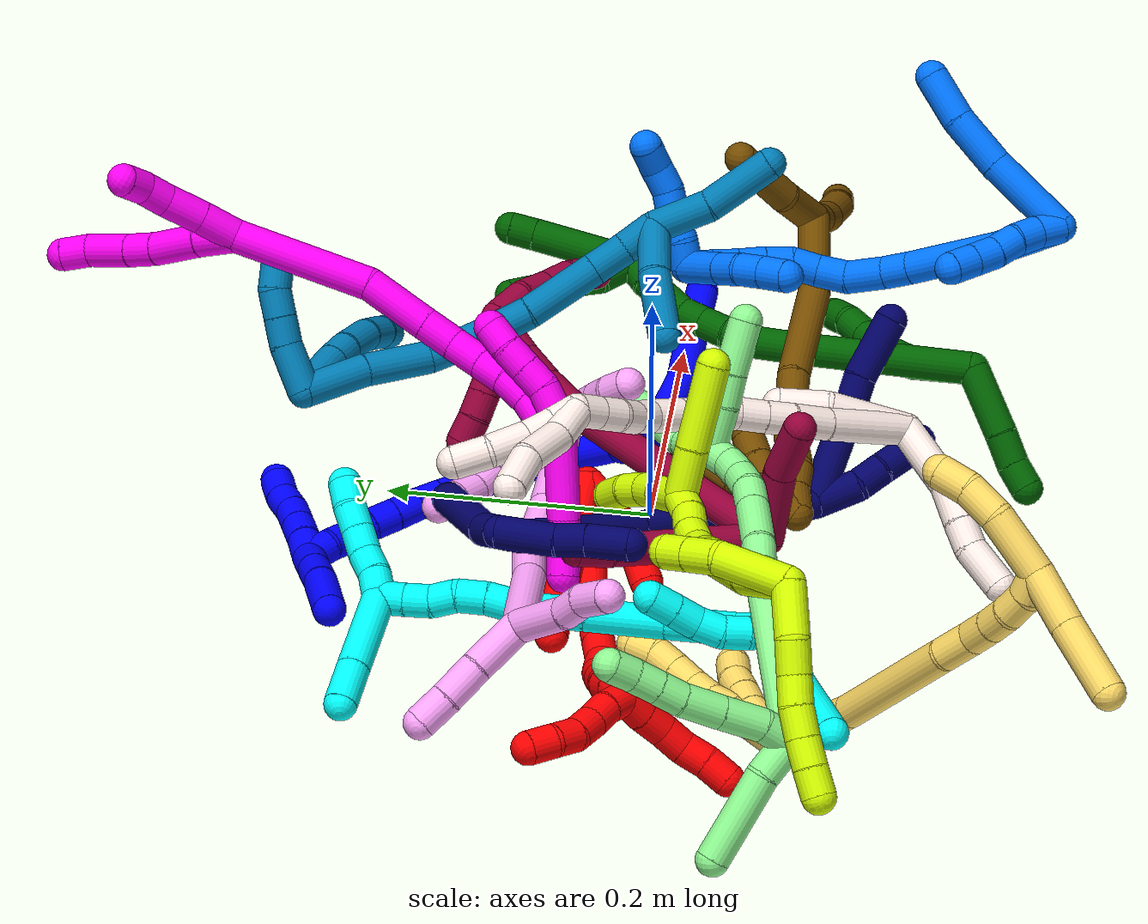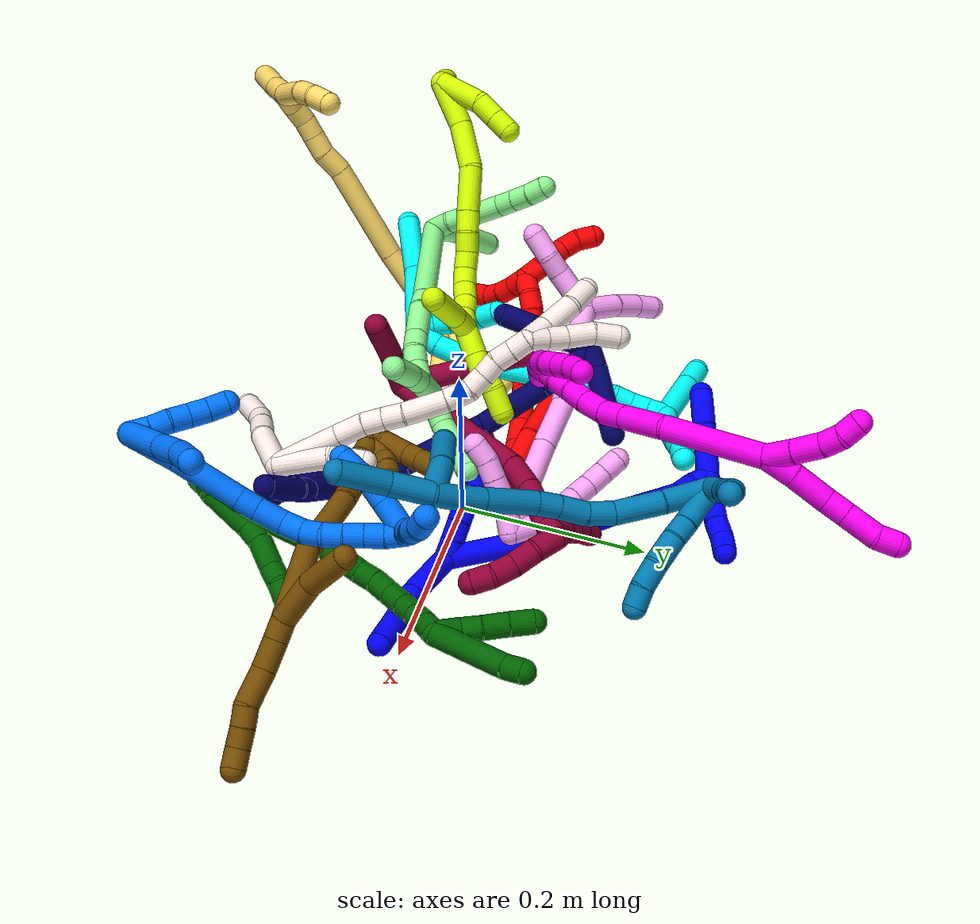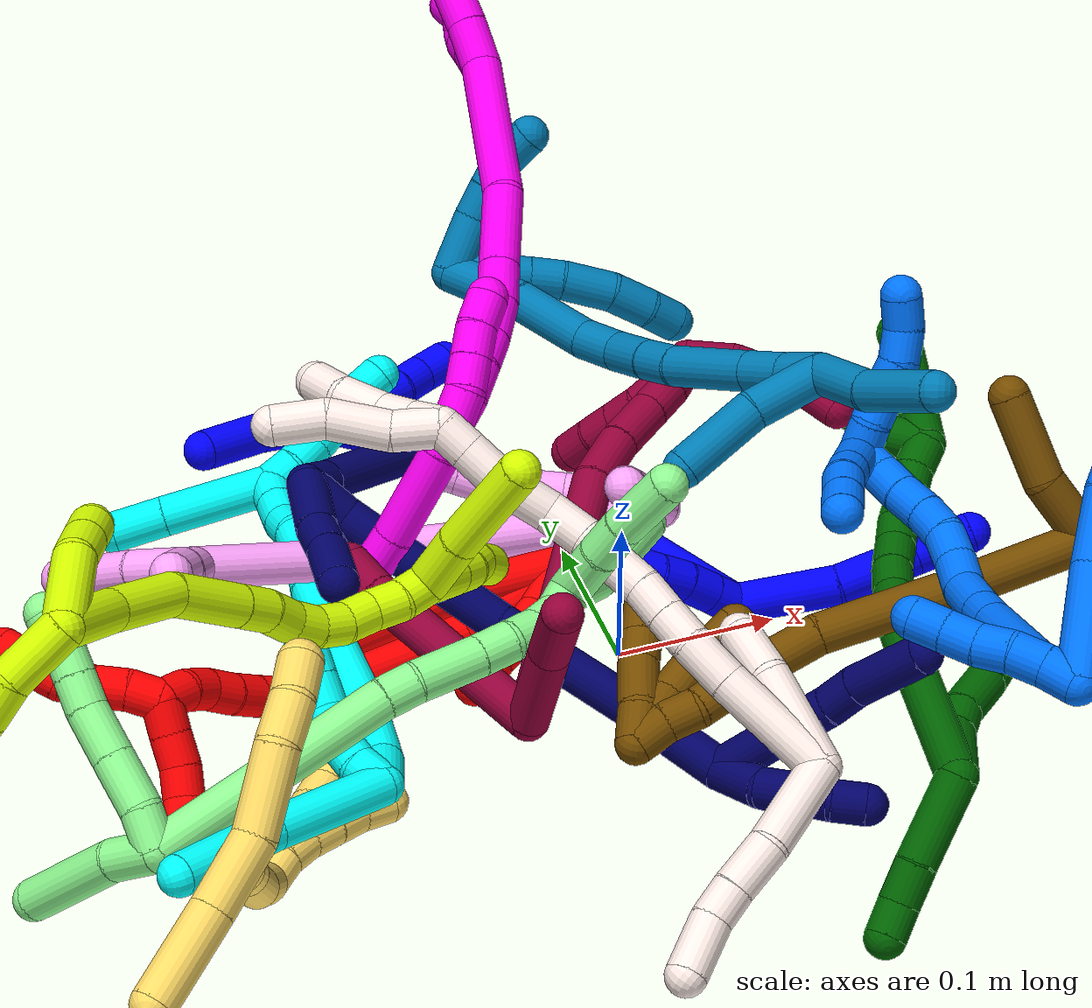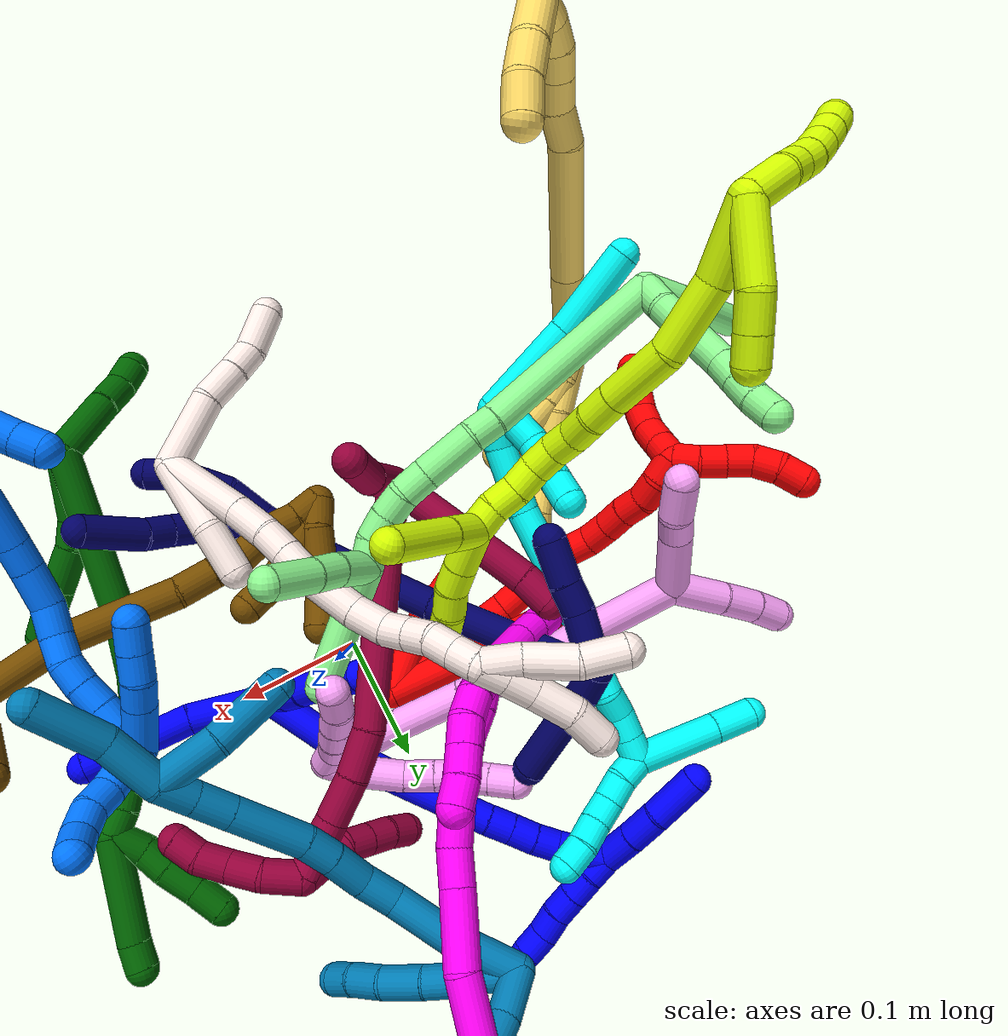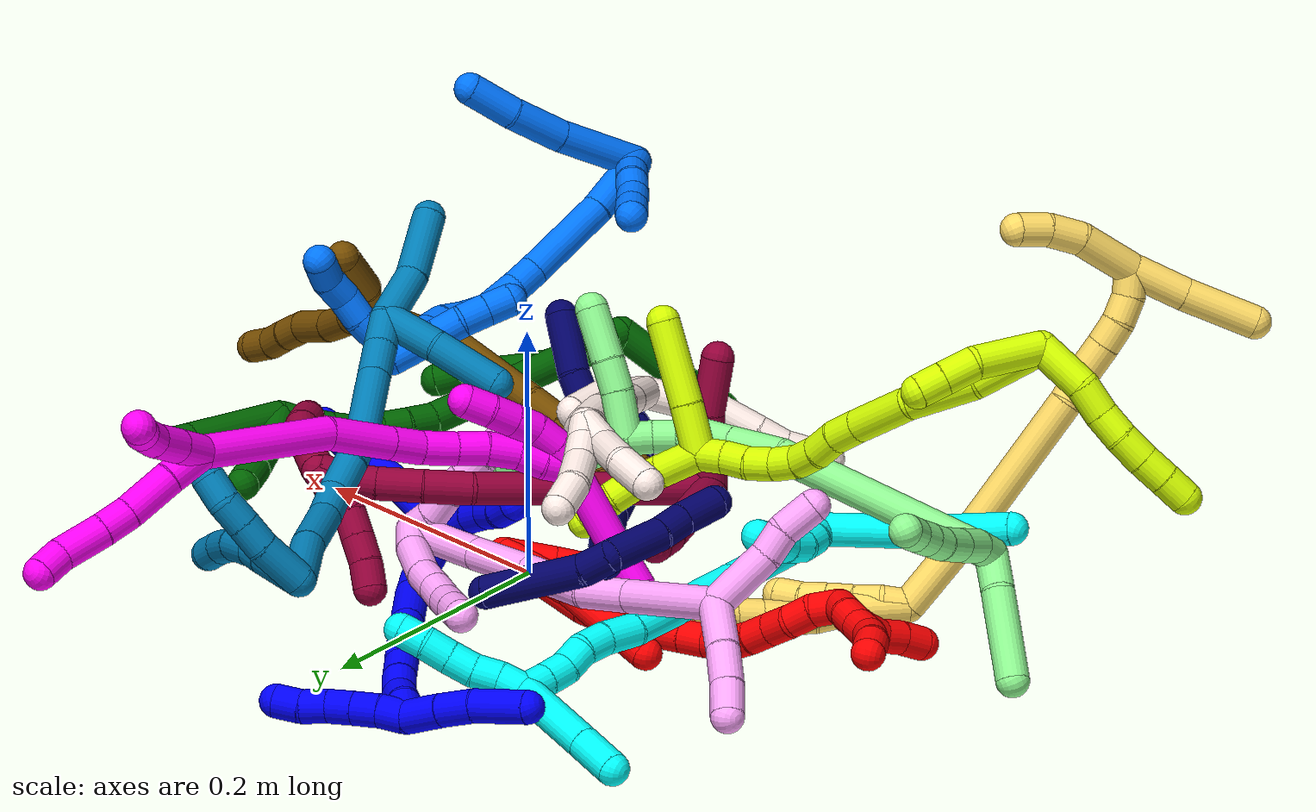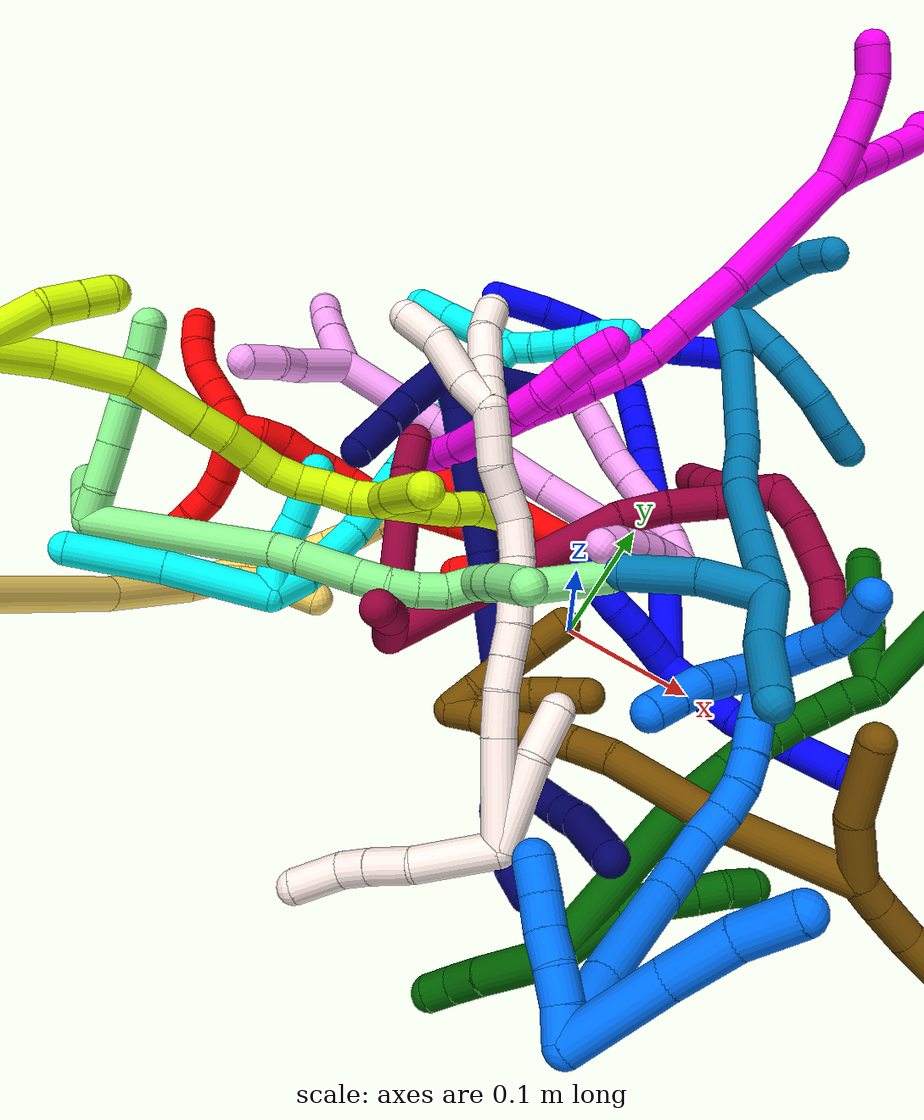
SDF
<sdf version="1.7">
 <world name="default">
  <plugin name="TubeGeneratorPlugin" filename="libtube_generator_plugin.so"/>
  <model name="photoneo_s_sensor">
   <static>1</static>
   <pose>0 0 2 1.57079 1.57079 3.14159</pose>
   <link name="link">
    <inertial><mass>0.1</mass></inertial>
    <sensor name="sensor" type="depth">
     <update_rate>30</update_rate>
     <camera>
      <horizontal_fov>1.22</horizontal_fov>
      <image><width>1920</width><height>1200</height><format>B8G8R8</format></image>
      <clip><near>0.1</near><far>4</far></clip>
      <depth_camera><output>points</output></depth_camera>
     </camera>
     <plugin name="camera_plugin" filename="libgazebo_ros_depth_camera.so">
      <baseline>0.2</baseline>
      <alwaysOn>1</alwaysOn>
      <updateRate>0.0</updateRate>
      <cameraName>camera_ir</cameraName>
      <imageTopicName>/camera/color/image_raw</imageTopicName>
      <cameraInfoTopicName>/camera/color/camera_info</cameraInfoTopicName>
      <depthImageTopicName>/camera/depth/image_raw</depthImageTopicName>
      <depthImageCameraInfoTopicName>/camera/depth/camera_info</depthImageCameraInfoTopicName>
      <pointCloudTopicName>/camera/depth/points</pointCloudTopicName>
      <frameName>fr_optical</frameName>
      <pointCloudCutoff>0.1</pointCloudCutoff>
      <pointCloudCutoffMax>2.0</pointCloudCutoffMax>
      <distortionK1>0</distortionK1>
      <distortionK2>0</distortionK2>
      <distortionK3>0</distortionK3>
      <distortionT1>0</distortionT1>
      <distortionT2>0</distortionT2>
      <CxPrime>0</CxPrime>
      <Cx>0</Cx>
      <Cy>0</Cy>
      <focalLength>0</focalLength>
      <hackBaseline>0</hackBaseline>
     </plugin>
    </sensor>
   </link>
  </model>
  <gravity>0 0 -9.8</gravity>
  <magnetic_field>6e-06 2.3e-05 -4.2e-05</magnetic_field>
  <atmosphere type="adiabatic"/>
  <physics name="default_physics" default="0" type="ode">
   <max_step_size>0.003</max_step_size>
   <real_time_factor>1</real_time_factor>
   <real_time_update_rate>1000</real_time_update_rate>
   <max_contacts>10000</max_contacts>
   <ode>
    <solver>
     <type>quick</type>
     <iters>100</iters>
     <sor>1.3</sor>
     <use_dynamic_moi_rescaling>0</use_dynamic_moi_rescaling>
    </solver>
    <constraints>
     <contact_max_correcting_vel>0</contact_max_correcting_vel>
     <contact_surface_layer>0.001</contact_surface_layer>
     <cfm>0</cfm>
     <erp>0.2</erp>
    </constraints>
   </ode>
  </physics>
  <scene><ambient>0.4 0.4 0.4 1</ambient><background>0.7 0.7 0.7 1</background><shadows>0</shadows></scene>
  <audio><device>default</device></audio>
  <spherical_coordinates>
   <surface_model>EARTH_WGS84</surface_model>
   <latitude_deg>0</latitude_deg>
   <longitude_deg>0</longitude_deg>
   <elevation>0</elevation>
   <heading_deg>0</heading_deg>
  </spherical_coordinates>
  <model name="bin">
   <static>1</static>
   <link name="bottom">
    <collision name="collision-bottom">
     <pose>0 0 -0.01 0 -0 0</pose>
     <geometry><box><size>0.8 0.6 0.02</size></box></geometry>
     <surface>
      <friction><ode><mu>100</mu><mu2>100</mu2></ode></friction>
      <contact><collide_bitmask>65535</collide_bitmask></contact>
     </surface>
    </collision>
   </link>
   <link name="west_wall">
    <collision name="collision-west_wall">
     <pose>-0.41 0 0.1 0 -0 0</pose>
     <geometry><box><size>0.02 0.6 0.2</size></box></geometry>
     <surface>
      <friction><ode><mu>100</mu><mu2>100</mu2></ode></friction>
      <contact><collide_bitmask>65535</collide_bitmask></contact>
     </surface>
    </collision>
   </link>
   <link name="east_wall">
    <collision name="collision-east_wall">
     <pose>0.41 0 0.1 0 -0 0</pose>
     <geometry><box><size>0.02 0.6 0.2</size></box></geometry>
     <surface>
      <friction><ode><mu>100</mu><mu2>100</mu2></ode></friction>
      <contact><collide_bitmask>65535</collide_bitmask></contact>
     </surface>
    </collision>
   </link>
   <link name="south_wall">
    <collision name="collision-south_wall">
     <pose>0 -0.31 0.1 0 -0 0</pose>
     <geometry><box><size>0.8 0.02 0.2</size></box></geometry>
     <surface>
      <friction><ode><mu>100</mu><mu2>100</mu2></ode></friction>
      <contact><collide_bitmask>65535</collide_bitmask></contact>
     </surface>
    </collision>
   </link>
   <link name="north_wall">
    <collision name="collision-north_wall">
     <pose>0 0.31 0.1 0 -0 0</pose>
     <geometry><box><size>0.8 0.02 0.2</size></box></geometry>
     <surface>
      <friction><ode><mu>100</mu><mu2>100</mu2></ode></friction>
      <contact><collide_bitmask>65535</collide_bitmask></contact>
     </surface>
    </collision>
   </link>
  </model>
  <model name="1">
   <static>0</static>
   <link name="1">
    <collision name="collision-cylinder-e_1_2_8">
     <pose>0.023801 -0.006386 0.020364 0.30388 0.839811 0.136511</pose>
     <geometry><cylinder><radius>0.0125</radius><length>0.063937</length></cylinder></geometry>
     <surface>
      <friction><ode><mu>1.16</mu><mu2>1.16</mu2><slip1>0</slip1><slip2>0</slip2></ode></friction>
      <contact><ode><kp>1e+06</kp><kd>1</kd><max_vel>0</max_vel><min_depth>0.001</min_depth></ode></contact>
     </surface>
    </collision>
    <visual name="visual-cylinder-e_1_2_8">
     <pose>0.023801 -0.006386 0.020364 0.30388 0.839811 0.136511</pose>
     <geometry><cylinder><radius>0.0125</radius><length>0.063937</length></cylinder></geometry>
     <material><ambient>0 0 1 1</ambient></material>
    </visual>
    <collision name="collision-cylinder-e_2_8_9">
     <pose>0.063578 -0.02208 0.057552 0.50533 0.693317 0.185997</pose>
     <geometry><cylinder><radius>0.0125</radius><length>0.049994</length></cylinder></geometry>
     <surface>
      <friction><ode><mu>1.16</mu><mu2>1.16</mu2><slip1>0</slip1><slip2>0</slip2></ode></friction>
      <contact><ode><kp>1e+06</kp><kd>1</kd><max_vel>0</max_vel><min_depth>0.001</min_depth></ode></contact>
     </surface>
    </collision>
    <visual name="visual-cylinder-e_2_8_9">
     <pose>0.063578 -0.02208 0.057552 0.50533 0.693317 0.185997</pose>
     <geometry><cylinder><radius>0.0125</radius><length>0.049994</length></cylinder></geometry>
     <material><ambient>0 0 1 1</ambient></material>
    </visual>
    <collision name="collision-cylinder-e_3_9_6">
     <pose>0.091423 -0.038398 0.086003 0.542577 0.718388 0.208123</pose>
     <geometry><cylinder><radius>0.0125</radius><length>0.036068</length></cylinder></geometry>
     <surface>
      <friction><ode><mu>1.16</mu><mu2>1.16</mu2><slip1>0</slip1><slip2>0</slip2></ode></friction>
      <contact><ode><kp>1e+06</kp><kd>1</kd><max_vel>0</max_vel><min_depth>0.001</min_depth></ode></contact>
     </surface>
    </collision>
    <visual name="visual-cylinder-e_3_9_6">
     <pose>0.091423 -0.038398 0.086003 0.542577 0.718388 0.208123</pose>
     <geometry><cylinder><radius>0.0125</radius><length>0.036068</length></cylinder></geometry>
     <material><ambient>0 0 1 1</ambient></material>
    </visual>
    <collision name="collision-cylinder-e_1_2_10">
     <pose>-0.002635 -0.003989 -0.008783 2.71525 -0.266686 -1.10955</pose>
     <geometry><cylinder><radius>0.0125</radius><length>0.02</length></cylinder></geometry>
     <surface>
      <friction><ode><mu>1.16</mu><mu2>1.16</mu2><slip1>0</slip1><slip2>0</slip2></ode></friction>
      <contact><ode><kp>1e+06</kp><kd>1</kd><max_vel>0</max_vel><min_depth>0.001</min_depth></ode></contact>
     </surface>
    </collision>
    <visual name="visual-cylinder-e_1_2_10">
     <pose>-0.002635 -0.003989 -0.008783 2.71525 -0.266686 -1.10955</pose>
     <geometry><cylinder><radius>0.0125</radius><length>0.02</length></cylinder></geometry>
     <material><ambient>0 0 1 1</ambient></material>
    </visual>
    <collision name="collision-cylinder-e_2_10_11">
     <pose>-0.007853 -0.011727 -0.02647 2.74312 -0.261234 -1.15358</pose>
     <geometry><cylinder><radius>0.0125</radius><length>0.02</length></cylinder></geometry>
     <surface>
      <friction><ode><mu>1.16</mu><mu2>1.16</mu2><slip1>0</slip1><slip2>0</slip2></ode></friction>
      <contact><ode><kp>1e+06</kp><kd>1</kd><max_vel>0</max_vel><min_depth>0.001</min_depth></ode></contact>
     </surface>
    </collision>
    <visual name="visual-cylinder-e_2_10_11">
     <pose>-0.007853 -0.011727 -0.02647 2.74312 -0.261234 -1.15358</pose>
     <geometry><cylinder><radius>0.0125</radius><length>0.02</length></cylinder></geometry>
     <material><ambient>0 0 1 1</ambient></material>
    </visual>
    <collision name="collision-cylinder-e_3_11_12">
     <pose>-0.013587 -0.018106 -0.044492 2.86069 -0.32056 -1.70448</pose>
     <geometry><cylinder><radius>0.0125</radius><length>0.02</length></cylinder></geometry>
     <surface>
      <friction><ode><mu>1.16</mu><mu2>1.16</mu2><slip1>0</slip1><slip2>0</slip2></ode></friction>
      <contact><ode><kp>1e+06</kp><kd>1</kd><max_vel>0</max_vel><min_depth>0.001</min_depth></ode></contact>
     </surface>
    </collision>
    <visual name="visual-cylinder-e_3_11_12">
     <pose>-0.013587 -0.018106 -0.044492 2.86069 -0.32056 -1.70448</pose>
     <geometry><cylinder><radius>0.0125</radius><length>0.02</length></cylinder></geometry>
     <material><ambient>0 0 1 1</ambient></material>
    </visual>
    <collision name="collision-cylinder-e_4_12_13">
     <pose>-0.021366 -0.023612 -0.061997 2.81135 -0.481108 -1.94818</pose>
     <geometry><cylinder><radius>0.0125</radius><length>0.02</length></cylinder></geometry>
     <surface>
      <friction><ode><mu>1.16</mu><mu2>1.16</mu2><slip1>0</slip1><slip2>0</slip2></ode></friction>
      <contact><ode><kp>1e+06</kp><kd>1</kd><max_vel>0</max_vel><min_depth>0.001</min_depth></ode></contact>
     </surface>
    </collision>
    <visual name="visual-cylinder-e_4_12_13">
     <pose>-0.021366 -0.023612 -0.061997 2.81135 -0.481108 -1.94818</pose>
     <geometry><cylinder><radius>0.0125</radius><length>0.02</length></cylinder></geometry>
     <material><ambient>0 0 1 1</ambient></material>
    </visual>
    <collision name="collision-cylinder-e_5_13_5">
     <pose>-0.028295 -0.030203 -0.079377 2.74977 -0.232233 -1.06272</pose>
     <geometry><cylinder><radius>0.0125</radius><length>0.02</length></cylinder></geometry>
     <surface>
      <friction><ode><mu>1.16</mu><mu2>1.16</mu2><slip1>0</slip1><slip2>0</slip2></ode></friction>
      <contact><ode><kp>1e+06</kp><kd>1</kd><max_vel>0</max_vel><min_depth>0.001</min_depth></ode></contact>
     </surface>
    </collision>
    <visual name="visual-cylinder-e_5_13_5">
     <pose>-0.028295 -0.030203 -0.079377 2.74977 -0.232233 -1.06272</pose>
     <geometry><cylinder><radius>0.0125</radius><length>0.02</length></cylinder></geometry>
     <material><ambient>0 0 1 1</ambient></material>
    </visual>
    <collision name="collision-cylinder-e_1_2_14">
     <pose>-0.038618 -0.018048 -0.005686 1.87601 -1.1152 -1.40933</pose>
     <geometry><cylinder><radius>0.0125</radius><length>0.086009</length></cylinder></geometry>
     <surface>
      <friction><ode><mu>1.16</mu><mu2>1.16</mu2><slip1>0</slip1><slip2>0</slip2></ode></friction>
      <contact><ode><kp>1e+06</kp><kd>1</kd><max_vel>0</max_vel><min_depth>0.001</min_depth></ode></contact>
     </surface>
    </collision>
    <visual name="visual-cylinder-e_1_2_14">
     <pose>-0.038618 -0.018048 -0.005686 1.87601 -1.1152 -1.40933</pose>
     <geometry><cylinder><radius>0.0125</radius><length>0.086009</length></cylinder></geometry>
     <material><ambient>0 0 1 1</ambient></material>
    </visual>
    <collision name="collision-cylinder-e_2_14_15">
     <pose>-0.089147 -0.040836 -0.014234 2.11395 -1.13556 -1.69284</pose>
     <geometry><cylinder><radius>0.0125</radius><length>0.02627</length></cylinder></geometry>
     <surface>
      <friction><ode><mu>1.16</mu><mu2>1.16</mu2><slip1>0</slip1><slip2>0</slip2></ode></friction>
      <contact><ode><kp>1e+06</kp><kd>1</kd><max_vel>0</max_vel><min_depth>0.001</min_depth></ode></contact>
     </surface>
    </collision>
    <visual name="visual-cylinder-e_2_14_15">
     <pose>-0.089147 -0.040836 -0.014234 2.11395 -1.13556 -1.69284</pose>
     <geometry><cylinder><radius>0.0125</radius><length>0.02627</length></cylinder></geometry>
     <material><ambient>0 0 1 1</ambient></material>
    </visual>
    <collision name="collision-cylinder-e_3_15_16">
     <pose>-0.122522 -0.053337 -0.023464 2.25798 -1.13335 -1.86312</pose>
     <geometry><cylinder><radius>0.0125</radius><length>0.047392</length></cylinder></geometry>
     <surface>
      <friction><ode><mu>1.16</mu><mu2>1.16</mu2><slip1>0</slip1><slip2>0</slip2></ode></friction>
      <contact><ode><kp>1e+06</kp><kd>1</kd><max_vel>0</max_vel><min_depth>0.001</min_depth></ode></contact>
     </surface>
    </collision>
    <visual name="visual-cylinder-e_3_15_16">
     <pose>-0.122522 -0.053337 -0.023464 2.25798 -1.13335 -1.86312</pose>
     <geometry><cylinder><radius>0.0125</radius><length>0.047392</length></cylinder></geometry>
     <material><ambient>0 0 1 1</ambient></material>
    </visual>
    <collision name="collision-cylinder-e_4_16_17">
     <pose>-0.152964 -0.064525 -0.032781 2.2812 -1.1042 -1.86113</pose>
     <geometry><cylinder><radius>0.0125</radius><length>0.020104</length></cylinder></geometry>
     <surface>
      <friction><ode><mu>1.16</mu><mu2>1.16</mu2><slip1>0</slip1><slip2>0</slip2></ode></friction>
      <contact><ode><kp>1e+06</kp><kd>1</kd><max_vel>0</max_vel><min_depth>0.001</min_depth></ode></contact>
     </surface>
    </collision>
    <visual name="visual-cylinder-e_4_16_17">
     <pose>-0.152964 -0.064525 -0.032781 2.2812 -1.1042 -1.86113</pose>
     <geometry><cylinder><radius>0.0125</radius><length>0.020104</length></cylinder></geometry>
     <material><ambient>0 0 1 1</ambient></material>
    </visual>
    <collision name="collision-cylinder-e_5_17_18">
     <pose>-0.171152 -0.071079 -0.038273 2.2537 -1.15836 -1.88405</pose>
     <geometry><cylinder><radius>0.0125</radius><length>0.020106</length></cylinder></geometry>
     <surface>
      <friction><ode><mu>1.16</mu><mu2>1.16</mu2><slip1>0</slip1><slip2>0</slip2></ode></friction>
      <contact><ode><kp>1e+06</kp><kd>1</kd><max_vel>0</max_vel><min_depth>0.001</min_depth></ode></contact>
     </surface>
    </collision>
    <visual name="visual-cylinder-e_5_17_18">
     <pose>-0.171152 -0.071079 -0.038273 2.2537 -1.15836 -1.88405</pose>
     <geometry><cylinder><radius>0.0125</radius><length>0.020106</length></cylinder></geometry>
     <material><ambient>0 0 1 1</ambient></material>
    </visual>
    <collision name="collision-cylinder-e_6_18_19">
     <pose>-0.189749 -0.07659 -0.043362 2.38886 -1.215 -2.10776</pose>
     <geometry><cylinder><radius>0.0125</radius><length>0.020029</length></cylinder></geometry>
     <surface>
      <friction><ode><mu>1.16</mu><mu2>1.16</mu2><slip1>0</slip1><slip2>0</slip2></ode></friction>
      <contact><ode><kp>1e+06</kp><kd>1</kd><max_vel>0</max_vel><min_depth>0.001</min_depth></ode></contact>
     </surface>
    </collision>
    <visual name="visual-cylinder-e_6_18_19">
     <pose>-0.189749 -0.07659 -0.043362 2.38886 -1.215 -2.10776</pose>
     <geometry><cylinder><radius>0.0125</radius><length>0.020029</length></cylinder></geometry>
     <material><ambient>0 0 1 1</ambient></material>
    </visual>
    <collision name="collision-cylinder-e_7_19_20">
     <pose>-0.208478 -0.081648 -0.048345 2.31002 -1.20141 -1.99674</pose>
     <geometry><cylinder><radius>0.0125</radius><length>0.020036</length></cylinder></geometry>
     <surface>
      <friction><ode><mu>1.16</mu><mu2>1.16</mu2><slip1>0</slip1><slip2>0</slip2></ode></friction>
      <contact><ode><kp>1e+06</kp><kd>1</kd><max_vel>0</max_vel><min_depth>0.001</min_depth></ode></contact>
     </surface>
    </collision>
    <visual name="visual-cylinder-e_7_19_20">
     <pose>-0.208478 -0.081648 -0.048345 2.31002 -1.20141 -1.99674</pose>
     <geometry><cylinder><radius>0.0125</radius><length>0.020036</length></cylinder></geometry>
     <material><ambient>0 0 1 1</ambient></material>
    </visual>
    <collision name="collision-cylinder-e_8_20_21">
     <pose>-0.227315 -0.086033 -0.053457 2.5724 -1.24792 -2.36965</pose>
     <geometry><cylinder><radius>0.0125</radius><length>0.020024</length></cylinder></geometry>
     <surface>
      <friction><ode><mu>1.16</mu><mu2>1.16</mu2><slip1>0</slip1><slip2>0</slip2></ode></friction>
      <contact><ode><kp>1e+06</kp><kd>1</kd><max_vel>0</max_vel><min_depth>0.001</min_depth></ode></contact>
     </surface>
    </collision>
    <visual name="visual-cylinder-e_8_20_21">
     <pose>-0.227315 -0.086033 -0.053457 2.5724 -1.24792 -2.36965</pose>
     <geometry><cylinder><radius>0.0125</radius><length>0.020024</length></cylinder></geometry>
     <material><ambient>0 0 1 1</ambient></material>
    </visual>
    <collision name="collision-cylinder-e_9_21_22">
     <pose>-0.244801 -0.090829 -0.061322 2.60524 -0.9238 -2.13283</pose>
     <geometry><cylinder><radius>0.0125</radius><length>0.020029</length></cylinder></geometry>
     <surface>
      <friction><ode><mu>1.16</mu><mu2>1.16</mu2><slip1>0</slip1><slip2>0</slip2></ode></friction>
      <contact><ode><kp>1e+06</kp><kd>1</kd><max_vel>0</max_vel><min_depth>0.001</min_depth></ode></contact>
     </surface>
    </collision>
    <visual name="visual-cylinder-e_9_21_22">
     <pose>-0.244801 -0.090829 -0.061322 2.60524 -0.9238 -2.13283</pose>
     <geometry><cylinder><radius>0.0125</radius><length>0.020029</length></cylinder></geometry>
     <material><ambient>0 0 1 1</ambient></material>
    </visual>
    <collision name="collision-cylinder-e_10_22_1">
     <pose>-0.261918 -0.095523 -0.070269 2.73703 -1.14968 -2.52839</pose>
     <geometry><cylinder><radius>0.0125</radius><length>0.020001</length></cylinder></geometry>
     <surface>
      <friction><ode><mu>1.16</mu><mu2>1.16</mu2><slip1>0</slip1><slip2>0</slip2></ode></friction>
      <contact><ode><kp>1e+06</kp><kd>1</kd><max_vel>0</max_vel><min_depth>0.001</min_depth></ode></contact>
     </surface>
    </collision>
    <visual name="visual-cylinder-e_10_22_1">
     <pose>-0.261918 -0.095523 -0.070269 2.73703 -1.14968 -2.52839</pose>
     <geometry><cylinder><radius>0.0125</radius><length>0.020001</length></cylinder></geometry>
     <material><ambient>0 0 1 1</ambient></material>
    </visual>
    <collision name="collision-cylinder-e_1_1_23">
     <pose>-0.27237 -0.096629 -0.089227 -3.10849 -0.086951 2.41434</pose>
     <geometry><cylinder><radius>0.0125</radius><length>0.030531</length></cylinder></geometry>
     <surface>
      <friction><ode><mu>1.16</mu><mu2>1.16</mu2><slip1>0</slip1><slip2>0</slip2></ode></friction>
      <contact><ode><kp>1e+06</kp><kd>1</kd><max_vel>0</max_vel><min_depth>0.001</min_depth></ode></contact>
     </surface>
    </collision>
    <visual name="visual-cylinder-e_1_1_23">
     <pose>-0.27237 -0.096629 -0.089227 -3.10849 -0.086951 2.41434</pose>
     <geometry><cylinder><radius>0.0125</radius><length>0.030531</length></cylinder></geometry>
     <material><ambient>0 0 1 1</ambient></material>
    </visual>
    <collision name="collision-cylinder-e_2_23_24">
     <pose>-0.274937 -0.09482 -0.117916 -3.0451 -0.091298 1.51543</pose>
     <geometry><cylinder><radius>0.0125</radius><length>0.02722</length></cylinder></geometry>
     <surface>
      <friction><ode><mu>1.16</mu><mu2>1.16</mu2><slip1>0</slip1><slip2>0</slip2></ode></friction>
      <contact><ode><kp>1e+06</kp><kd>1</kd><max_vel>0</max_vel><min_depth>0.001</min_depth></ode></contact>
     </surface>
    </collision>
    <visual name="visual-cylinder-e_2_23_24">
     <pose>-0.274937 -0.09482 -0.117916 -3.0451 -0.091298 1.51543</pose>
     <geometry><cylinder><radius>0.0125</radius><length>0.02722</length></cylinder></geometry>
     <material><ambient>0 0 1 1</ambient></material>
    </visual>
    <collision name="collision-cylinder-e_3_24_4">
     <pose>-0.279889 -0.088822 -0.151666 -2.91403 -0.176636 1.31845</pose>
     <geometry><cylinder><radius>0.0125</radius><length>0.042249</length></cylinder></geometry>
     <surface>
      <friction><ode><mu>1.16</mu><mu2>1.16</mu2><slip1>0</slip1><slip2>0</slip2></ode></friction>
      <contact><ode><kp>1e+06</kp><kd>1</kd><max_vel>0</max_vel><min_depth>0.001</min_depth></ode></contact>
     </surface>
    </collision>
    <visual name="visual-cylinder-e_3_24_4">
     <pose>-0.279889 -0.088822 -0.151666 -2.91403 -0.176636 1.31845</pose>
     <geometry><cylinder><radius>0.0125</radius><length>0.042249</length></cylinder></geometry>
     <material><ambient>0 0 1 1</ambient></material>
    </visual>
    <collision name="collision-cylinder-e_1_1_25">
     <pose>-0.268533 -0.101363 -0.065321 0.452357 0.25387 0.058719</pose>
     <geometry><cylinder><radius>0.0125</radius><length>0.02</length></cylinder></geometry>
     <surface>
      <friction><ode><mu>1.16</mu><mu2>1.16</mu2><slip1>0</slip1><slip2>0</slip2></ode></friction>
      <contact><ode><kp>1e+06</kp><kd>1</kd><max_vel>0</max_vel><min_depth>0.001</min_depth></ode></contact>
     </surface>
    </collision>
    <visual name="visual-cylinder-e_1_1_25">
     <pose>-0.268533 -0.101363 -0.065321 0.452357 0.25387 0.058719</pose>
     <geometry><cylinder><radius>0.0125</radius><length>0.02</length></cylinder></geometry>
     <material><ambient>0 0 1 1</ambient></material>
    </visual>
    <collision name="collision-cylinder-e_2_25_26">
     <pose>-0.264412 -0.109092 -0.047386 0.362326 0.161601 0.029663</pose>
     <geometry><cylinder><radius>0.0125</radius><length>0.02</length></cylinder></geometry>
     <surface>
      <friction><ode><mu>1.16</mu><mu2>1.16</mu2><slip1>0</slip1><slip2>0</slip2></ode></friction>
      <contact><ode><kp>1e+06</kp><kd>1</kd><max_vel>0</max_vel><min_depth>0.001</min_depth></ode></contact>
     </surface>
    </collision>
    <visual name="visual-cylinder-e_2_25_26">
     <pose>-0.264412 -0.109092 -0.047386 0.362326 0.161601 0.029663</pose>
     <geometry><cylinder><radius>0.0125</radius><length>0.02</length></cylinder></geometry>
     <material><ambient>0 0 1 1</ambient></material>
    </visual>
    <collision name="collision-cylinder-e_3_26_27">
     <pose>-0.26127 -0.115891 -0.028843 0.340573 0.153913 0.026516</pose>
     <geometry><cylinder><radius>0.0125</radius><length>0.02</length></cylinder></geometry>
     <surface>
      <friction><ode><mu>1.16</mu><mu2>1.16</mu2><slip1>0</slip1><slip2>0</slip2></ode></friction>
      <contact><ode><kp>1e+06</kp><kd>1</kd><max_vel>0</max_vel><min_depth>0.001</min_depth></ode></contact>
     </surface>
    </collision>
    <visual name="visual-cylinder-e_3_26_27">
     <pose>-0.26127 -0.115891 -0.028843 0.340573 0.153913 0.026516</pose>
     <geometry><cylinder><radius>0.0125</radius><length>0.02</length></cylinder></geometry>
     <material><ambient>0 0 1 1</ambient></material>
    </visual>
    <collision name="collision-cylinder-e_4_27_28">
     <pose>-0.259702 -0.122932 -0.010255 0.383304 0.00353 0.000685</pose>
     <geometry><cylinder><radius>0.0125</radius><length>0.02</length></cylinder></geometry>
     <surface>
      <friction><ode><mu>1.16</mu><mu2>1.16</mu2><slip1>0</slip1><slip2>0</slip2></ode></friction>
      <contact><ode><kp>1e+06</kp><kd>1</kd><max_vel>0</max_vel><min_depth>0.001</min_depth></ode></contact>
     </surface>
    </collision>
    <visual name="visual-cylinder-e_4_27_28">
     <pose>-0.259702 -0.122932 -0.010255 0.383304 0.00353 0.000685</pose>
     <geometry><cylinder><radius>0.0125</radius><length>0.02</length></cylinder></geometry>
     <material><ambient>0 0 1 1</ambient></material>
    </visual>
    <collision name="collision-cylinder-e_5_28_3">
     <pose>-0.257392 -0.130982 0.007752 0.458543 0.229497 0.053782</pose>
     <geometry><cylinder><radius>0.0125</radius><length>0.02</length></cylinder></geometry>
     <surface>
      <friction><ode><mu>1.16</mu><mu2>1.16</mu2><slip1>0</slip1><slip2>0</slip2></ode></friction>
      <contact><ode><kp>1e+06</kp><kd>1</kd><max_vel>0</max_vel><min_depth>0.001</min_depth></ode></contact>
     </surface>
    </collision>
    <visual name="visual-cylinder-e_5_28_3">
     <pose>-0.257392 -0.130982 0.007752 0.458543 0.229497 0.053782</pose>
     <geometry><cylinder><radius>0.0125</radius><length>0.02</length></cylinder></geometry>
     <material><ambient>0 0 1 1</ambient></material>
    </visual>
    <collision name="collision-sphere-3">
     <pose>-0.255117 -0.135293 0.016484 0 -0 0</pose>
     <geometry><sphere><radius>0.0125</radius></sphere></geometry>
     <surface>
      <friction><ode><mu>1.16</mu><mu2>1.16</mu2><slip1>0</slip1><slip2>0</slip2></ode></friction>
      <contact><ode><kp>1e+06</kp><kd>1</kd><max_vel>0</max_vel><min_depth>0.001</min_depth></ode></contact>
     </surface>
    </collision>
    <visual name="visual-sphere-3">
     <pose>-0.255117 -0.135293 0.016484 0 -0 0</pose>
     <geometry><sphere><radius>0.0125</radius></sphere></geometry>
     <material><ambient>0 0 1 1</ambient></material>
    </visual>
    <collision name="collision-sphere-28">
     <pose>-0.259667 -0.126672 -0.00098 0 -0 0</pose>
     <geometry><sphere><radius>0.0125</radius></sphere></geometry>
     <surface>
      <friction><ode><mu>1.16</mu><mu2>1.16</mu2><slip1>0</slip1><slip2>0</slip2></ode></friction>
      <contact><ode><kp>1e+06</kp><kd>1</kd><max_vel>0</max_vel><min_depth>0.001</min_depth></ode></contact>
     </surface>
    </collision>
    <visual name="visual-sphere-28">
     <pose>-0.259667 -0.126672 -0.00098 0 -0 0</pose>
     <geometry><sphere><radius>0.0125</radius></sphere></geometry>
     <material><ambient>0 0 1 1</ambient></material>
    </visual>
    <collision name="collision-sphere-27">
     <pose>-0.259737 -0.119192 -0.019529 0 -0 0</pose>
     <geometry><sphere><radius>0.0125</radius></sphere></geometry>
     <surface>
      <friction><ode><mu>1.16</mu><mu2>1.16</mu2><slip1>0</slip1><slip2>0</slip2></ode></friction>
      <contact><ode><kp>1e+06</kp><kd>1</kd><max_vel>0</max_vel><min_depth>0.001</min_depth></ode></contact>
     </surface>
    </collision>
    <visual name="visual-sphere-27">
     <pose>-0.259737 -0.119192 -0.019529 0 -0 0</pose>
     <geometry><sphere><radius>0.0125</radius></sphere></geometry>
     <material><ambient>0 0 1 1</ambient></material>
    </visual>
    <collision name="collision-sphere-26">
     <pose>-0.262803 -0.112591 -0.038157 0 -0 0</pose>
     <geometry><sphere><radius>0.0125</radius></sphere></geometry>
     <surface>
      <friction><ode><mu>1.16</mu><mu2>1.16</mu2><slip1>0</slip1><slip2>0</slip2></ode></friction>
      <contact><ode><kp>1e+06</kp><kd>1</kd><max_vel>0</max_vel><min_depth>0.001</min_depth></ode></contact>
     </surface>
    </collision>
    <visual name="visual-sphere-26">
     <pose>-0.262803 -0.112591 -0.038157 0 -0 0</pose>
     <geometry><sphere><radius>0.0125</radius></sphere></geometry>
     <material><ambient>0 0 1 1</ambient></material>
    </visual>
    <collision name="collision-sphere-25">
     <pose>-0.266021 -0.105594 -0.056615 0 -0 0</pose>
     <geometry><sphere><radius>0.0125</radius></sphere></geometry>
     <surface>
      <friction><ode><mu>1.16</mu><mu2>1.16</mu2><slip1>0</slip1><slip2>0</slip2></ode></friction>
      <contact><ode><kp>1e+06</kp><kd>1</kd><max_vel>0</max_vel><min_depth>0.001</min_depth></ode></contact>
     </surface>
    </collision>
    <visual name="visual-sphere-25">
     <pose>-0.266021 -0.105594 -0.056615 0 -0 0</pose>
     <geometry><sphere><radius>0.0125</radius></sphere></geometry>
     <material><ambient>0 0 1 1</ambient></material>
    </visual>
    <collision name="collision-sphere-4">
     <pose>-0.283601 -0.084131 -0.171926 0 -0 0</pose>
     <geometry><sphere><radius>0.0125</radius></sphere></geometry>
     <surface>
      <friction><ode><mu>1.16</mu><mu2>1.16</mu2><slip1>0</slip1><slip2>0</slip2></ode></friction>
      <contact><ode><kp>1e+06</kp><kd>1</kd><max_vel>0</max_vel><min_depth>0.001</min_depth></ode></contact>
     </surface>
    </collision>
    <visual name="visual-sphere-4">
     <pose>-0.283601 -0.084131 -0.171926 0 -0 0</pose>
     <geometry><sphere><radius>0.0125</radius></sphere></geometry>
     <material><ambient>0 0 1 1</ambient></material>
    </visual>
    <collision name="collision-sphere-24">
     <pose>-0.276177 -0.093514 -0.131407 0 -0 0</pose>
     <geometry><sphere><radius>0.0125</radius></sphere></geometry>
     <surface>
      <friction><ode><mu>1.16</mu><mu2>1.16</mu2><slip1>0</slip1><slip2>0</slip2></ode></friction>
      <contact><ode><kp>1e+06</kp><kd>1</kd><max_vel>0</max_vel><min_depth>0.001</min_depth></ode></contact>
     </surface>
    </collision>
    <visual name="visual-sphere-24">
     <pose>-0.276177 -0.093514 -0.131407 0 -0 0</pose>
     <geometry><sphere><radius>0.0125</radius></sphere></geometry>
     <material><ambient>0 0 1 1</ambient></material>
    </visual>
    <collision name="collision-sphere-23">
     <pose>-0.273696 -0.096126 -0.104426 0 -0 0</pose>
     <geometry><sphere><radius>0.0125</radius></sphere></geometry>
     <surface>
      <friction><ode><mu>1.16</mu><mu2>1.16</mu2><slip1>0</slip1><slip2>0</slip2></ode></friction>
      <contact><ode><kp>1e+06</kp><kd>1</kd><max_vel>0</max_vel><min_depth>0.001</min_depth></ode></contact>
     </surface>
    </collision>
    <visual name="visual-sphere-23">
     <pose>-0.273696 -0.096126 -0.104426 0 -0 0</pose>
     <geometry><sphere><radius>0.0125</radius></sphere></geometry>
     <material><ambient>0 0 1 1</ambient></material>
    </visual>
    <collision name="collision-sphere-1">
     <pose>-0.271044 -0.097132 -0.074027 0 -0 0</pose>
     <geometry><sphere><radius>0.0125</radius></sphere></geometry>
     <surface>
      <friction><ode><mu>1.16</mu><mu2>1.16</mu2><slip1>0</slip1><slip2>0</slip2></ode></friction>
      <contact><ode><kp>1e+06</kp><kd>1</kd><max_vel>0</max_vel><min_depth>0.001</min_depth></ode></contact>
     </surface>
    </collision>
    <visual name="visual-sphere-1">
     <pose>-0.271044 -0.097132 -0.074027 0 -0 0</pose>
     <geometry><sphere><radius>0.0125</radius></sphere></geometry>
     <material><ambient>0 0 1 1</ambient></material>
    </visual>
    <collision name="collision-sphere-22">
     <pose>-0.252791 -0.093914 -0.066511 0 -0 0</pose>
     <geometry><sphere><radius>0.0125</radius></sphere></geometry>
     <surface>
      <friction><ode><mu>1.16</mu><mu2>1.16</mu2><slip1>0</slip1><slip2>0</slip2></ode></friction>
      <contact><ode><kp>1e+06</kp><kd>1</kd><max_vel>0</max_vel><min_depth>0.001</min_depth></ode></contact>
     </surface>
    </collision>
    <visual name="visual-sphere-22">
     <pose>-0.252791 -0.093914 -0.066511 0 -0 0</pose>
     <geometry><sphere><radius>0.0125</radius></sphere></geometry>
     <material><ambient>0 0 1 1</ambient></material>
    </visual>
    <collision name="collision-sphere-21">
     <pose>-0.23681 -0.087745 -0.056133 0 -0 0</pose>
     <geometry><sphere><radius>0.0125</radius></sphere></geometry>
     <surface>
      <friction><ode><mu>1.16</mu><mu2>1.16</mu2><slip1>0</slip1><slip2>0</slip2></ode></friction>
      <contact><ode><kp>1e+06</kp><kd>1</kd><max_vel>0</max_vel><min_depth>0.001</min_depth></ode></contact>
     </surface>
    </collision>
    <visual name="visual-sphere-21">
     <pose>-0.23681 -0.087745 -0.056133 0 -0 0</pose>
     <geometry><sphere><radius>0.0125</radius></sphere></geometry>
     <material><ambient>0 0 1 1</ambient></material>
    </visual>
    <collision name="collision-sphere-11">
     <pose>-0.010436 -0.015475 -0.035374 0 -0 0</pose>
     <geometry><sphere><radius>0.0125</radius></sphere></geometry>
     <surface>
      <friction><ode><mu>1.16</mu><mu2>1.16</mu2><slip1>0</slip1><slip2>0</slip2></ode></friction>
      <contact><ode><kp>1e+06</kp><kd>1</kd><max_vel>0</max_vel><min_depth>0.001</min_depth></ode></contact>
     </surface>
    </collision>
    <visual name="visual-sphere-11">
     <pose>-0.010436 -0.015475 -0.035374 0 -0 0</pose>
     <geometry><sphere><radius>0.0125</radius></sphere></geometry>
     <material><ambient>0 0 1 1</ambient></material>
    </visual>
    <collision name="collision-sphere-10">
     <pose>-0.005271 -0.007979 -0.017566 0 -0 0</pose>
     <geometry><sphere><radius>0.0125</radius></sphere></geometry>
     <surface>
      <friction><ode><mu>1.16</mu><mu2>1.16</mu2><slip1>0</slip1><slip2>0</slip2></ode></friction>
      <contact><ode><kp>1e+06</kp><kd>1</kd><max_vel>0</max_vel><min_depth>0.001</min_depth></ode></contact>
     </surface>
    </collision>
    <visual name="visual-sphere-10">
     <pose>-0.005271 -0.007979 -0.017566 0 -0 0</pose>
     <geometry><sphere><radius>0.0125</radius></sphere></geometry>
     <material><ambient>0 0 1 1</ambient></material>
    </visual>
    <collision name="collision-sphere-6">
     <pose>0.103293 -0.045408 0.09763 0 -0 0</pose>
     <geometry><sphere><radius>0.0125</radius></sphere></geometry>
     <surface>
      <friction><ode><mu>1.16</mu><mu2>1.16</mu2><slip1>0</slip1><slip2>0</slip2></ode></friction>
      <contact><ode><kp>1e+06</kp><kd>1</kd><max_vel>0</max_vel><min_depth>0.001</min_depth></ode></contact>
     </surface>
    </collision>
    <visual name="visual-sphere-6">
     <pose>0.103293 -0.045408 0.09763 0 -0 0</pose>
     <geometry><sphere><radius>0.0125</radius></sphere></geometry>
     <material><ambient>0 0 1 1</ambient></material>
    </visual>
    <collision name="collision-sphere-9">
     <pose>0.079553 -0.031387 0.074375 0 -0 0</pose>
     <geometry><sphere><radius>0.0125</radius></sphere></geometry>
     <surface>
      <friction><ode><mu>1.16</mu><mu2>1.16</mu2><slip1>0</slip1><slip2>0</slip2></ode></friction>
      <contact><ode><kp>1e+06</kp><kd>1</kd><max_vel>0</max_vel><min_depth>0.001</min_depth></ode></contact>
     </surface>
    </collision>
    <visual name="visual-sphere-9">
     <pose>0.079553 -0.031387 0.074375 0 -0 0</pose>
     <geometry><sphere><radius>0.0125</radius></sphere></geometry>
     <material><ambient>0 0 1 1</ambient></material>
    </visual>
    <collision name="collision-sphere-2">
     <geometry><sphere><radius>0.0125</radius></sphere></geometry>
     <surface>
      <friction><ode><mu>1.16</mu><mu2>1.16</mu2><slip1>0</slip1><slip2>0</slip2></ode></friction>
      <contact><ode><kp>1e+06</kp><kd>1</kd><max_vel>0</max_vel><min_depth>0.001</min_depth></ode></contact>
     </surface>
    </collision>
    <visual name="visual-sphere-2">
     <geometry><sphere><radius>0.0125</radius></sphere></geometry>
     <material><ambient>0 0 1 1</ambient></material>
    </visual>
    <collision name="collision-sphere-19">
     <pose>-0.199136 -0.078975 -0.045908 0 -0 0</pose>
     <geometry><sphere><radius>0.0125</radius></sphere></geometry>
     <surface>
      <friction><ode><mu>1.16</mu><mu2>1.16</mu2><slip1>0</slip1><slip2>0</slip2></ode></friction>
      <contact><ode><kp>1e+06</kp><kd>1</kd><max_vel>0</max_vel><min_depth>0.001</min_depth></ode></contact>
     </surface>
    </collision>
    <visual name="visual-sphere-19">
     <pose>-0.199136 -0.078975 -0.045908 0 -0 0</pose>
     <geometry><sphere><radius>0.0125</radius></sphere></geometry>
     <material><ambient>0 0 1 1</ambient></material>
    </visual>
    <collision name="collision-sphere-8">
     <pose>0.047602 -0.012772 0.040729 0 -0 0</pose>
     <geometry><sphere><radius>0.0125</radius></sphere></geometry>
     <surface>
      <friction><ode><mu>1.16</mu><mu2>1.16</mu2><slip1>0</slip1><slip2>0</slip2></ode></friction>
      <contact><ode><kp>1e+06</kp><kd>1</kd><max_vel>0</max_vel><min_depth>0.001</min_depth></ode></contact>
     </surface>
    </collision>
    <visual name="visual-sphere-8">
     <pose>0.047602 -0.012772 0.040729 0 -0 0</pose>
     <geometry><sphere><radius>0.0125</radius></sphere></geometry>
     <material><ambient>0 0 1 1</ambient></material>
    </visual>
    <collision name="collision-sphere-12">
     <pose>-0.016738 -0.020737 -0.053611 0 -0 0</pose>
     <geometry><sphere><radius>0.0125</radius></sphere></geometry>
     <surface>
      <friction><ode><mu>1.16</mu><mu2>1.16</mu2><slip1>0</slip1><slip2>0</slip2></ode></friction>
      <contact><ode><kp>1e+06</kp><kd>1</kd><max_vel>0</max_vel><min_depth>0.001</min_depth></ode></contact>
     </surface>
    </collision>
    <visual name="visual-sphere-12">
     <pose>-0.016738 -0.020737 -0.053611 0 -0 0</pose>
     <geometry><sphere><radius>0.0125</radius></sphere></geometry>
     <material><ambient>0 0 1 1</ambient></material>
    </visual>
    <collision name="collision-sphere-13">
     <pose>-0.025993 -0.026487 -0.070383 0 -0 0</pose>
     <geometry><sphere><radius>0.0125</radius></sphere></geometry>
     <surface>
      <friction><ode><mu>1.16</mu><mu2>1.16</mu2><slip1>0</slip1><slip2>0</slip2></ode></friction>
      <contact><ode><kp>1e+06</kp><kd>1</kd><max_vel>0</max_vel><min_depth>0.001</min_depth></ode></contact>
     </surface>
    </collision>
    <visual name="visual-sphere-13">
     <pose>-0.025993 -0.026487 -0.070383 0 -0 0</pose>
     <geometry><sphere><radius>0.0125</radius></sphere></geometry>
     <material><ambient>0 0 1 1</ambient></material>
    </visual>
    <collision name="collision-sphere-5">
     <pose>-0.030596 -0.033919 -0.088371 0 -0 0</pose>
     <geometry><sphere><radius>0.0125</radius></sphere></geometry>
     <surface>
      <friction><ode><mu>1.16</mu><mu2>1.16</mu2><slip1>0</slip1><slip2>0</slip2></ode></friction>
      <contact><ode><kp>1e+06</kp><kd>1</kd><max_vel>0</max_vel><min_depth>0.001</min_depth></ode></contact>
     </surface>
    </collision>
    <visual name="visual-sphere-5">
     <pose>-0.030596 -0.033919 -0.088371 0 -0 0</pose>
     <geometry><sphere><radius>0.0125</radius></sphere></geometry>
     <material><ambient>0 0 1 1</ambient></material>
    </visual>
    <collision name="collision-sphere-14">
     <pose>-0.077236 -0.036095 -0.011372 0 -0 0</pose>
     <geometry><sphere><radius>0.0125</radius></sphere></geometry>
     <surface>
      <friction><ode><mu>1.16</mu><mu2>1.16</mu2><slip1>0</slip1><slip2>0</slip2></ode></friction>
      <contact><ode><kp>1e+06</kp><kd>1</kd><max_vel>0</max_vel><min_depth>0.001</min_depth></ode></contact>
     </surface>
    </collision>
    <visual name="visual-sphere-14">
     <pose>-0.077236 -0.036095 -0.011372 0 -0 0</pose>
     <geometry><sphere><radius>0.0125</radius></sphere></geometry>
     <material><ambient>0 0 1 1</ambient></material>
    </visual>
    <collision name="collision-sphere-15">
     <pose>-0.101058 -0.045577 -0.017097 0 -0 0</pose>
     <geometry><sphere><radius>0.0125</radius></sphere></geometry>
     <surface>
      <friction><ode><mu>1.16</mu><mu2>1.16</mu2><slip1>0</slip1><slip2>0</slip2></ode></friction>
      <contact><ode><kp>1e+06</kp><kd>1</kd><max_vel>0</max_vel><min_depth>0.001</min_depth></ode></contact>
     </surface>
    </collision>
    <visual name="visual-sphere-15">
     <pose>-0.101058 -0.045577 -0.017097 0 -0 0</pose>
     <geometry><sphere><radius>0.0125</radius></sphere></geometry>
     <material><ambient>0 0 1 1</ambient></material>
    </visual>
    <collision name="collision-sphere-16">
     <pose>-0.143987 -0.061097 -0.029832 0 -0 0</pose>
     <geometry><sphere><radius>0.0125</radius></sphere></geometry>
     <surface>
      <friction><ode><mu>1.16</mu><mu2>1.16</mu2><slip1>0</slip1><slip2>0</slip2></ode></friction>
      <contact><ode><kp>1e+06</kp><kd>1</kd><max_vel>0</max_vel><min_depth>0.001</min_depth></ode></contact>
     </surface>
    </collision>
    <visual name="visual-sphere-16">
     <pose>-0.143987 -0.061097 -0.029832 0 -0 0</pose>
     <geometry><sphere><radius>0.0125</radius></sphere></geometry>
     <material><ambient>0 0 1 1</ambient></material>
    </visual>
    <collision name="collision-sphere-17">
     <pose>-0.161942 -0.067953 -0.03573 0 -0 0</pose>
     <geometry><sphere><radius>0.0125</radius></sphere></geometry>
     <surface>
      <friction><ode><mu>1.16</mu><mu2>1.16</mu2><slip1>0</slip1><slip2>0</slip2></ode></friction>
      <contact><ode><kp>1e+06</kp><kd>1</kd><max_vel>0</max_vel><min_depth>0.001</min_depth></ode></contact>
     </surface>
    </collision>
    <visual name="visual-sphere-17">
     <pose>-0.161942 -0.067953 -0.03573 0 -0 0</pose>
     <geometry><sphere><radius>0.0125</radius></sphere></geometry>
     <material><ambient>0 0 1 1</ambient></material>
    </visual>
    <collision name="collision-sphere-18">
     <pose>-0.180362 -0.074205 -0.040816 0 -0 0</pose>
     <geometry><sphere><radius>0.0125</radius></sphere></geometry>
     <surface>
      <friction><ode><mu>1.16</mu><mu2>1.16</mu2><slip1>0</slip1><slip2>0</slip2></ode></friction>
      <contact><ode><kp>1e+06</kp><kd>1</kd><max_vel>0</max_vel><min_depth>0.001</min_depth></ode></contact>
     </surface>
    </collision>
    <visual name="visual-sphere-18">
     <pose>-0.180362 -0.074205 -0.040816 0 -0 0</pose>
     <geometry><sphere><radius>0.0125</radius></sphere></geometry>
     <material><ambient>0 0 1 1</ambient></material>
    </visual>
    <collision name="collision-sphere-20">
     <pose>-0.217821 -0.084321 -0.050781 0 -0 0</pose>
     <geometry><sphere><radius>0.0125</radius></sphere></geometry>
     <surface>
      <friction><ode><mu>1.16</mu><mu2>1.16</mu2><slip1>0</slip1><slip2>0</slip2></ode></friction>
      <contact><ode><kp>1e+06</kp><kd>1</kd><max_vel>0</max_vel><min_depth>0.001</min_depth></ode></contact>
     </surface>
    </collision>
    <visual name="visual-sphere-20">
     <pose>-0.217821 -0.084321 -0.050781 0 -0 0</pose>
     <geometry><sphere><radius>0.0125</radius></sphere></geometry>
     <material><ambient>0 0 1 1</ambient></material>
    </visual>
    <inertial>
     <pose>-0.117313 -0.056054 -0.028411 0 -0 0</pose>
     <mass>0.75</mass>
     <inertia><ixx>0</ixx><ixy>0</ixy><ixz>0</ixz><iyy>7.5e-05</iyy><iyz>0</iyz><izz>8.5e-05</izz></inertia>
    </inertial>
   </link>
   <pose>0.077871 0.008344 0.011463 -2.08372 -0.399767 -0.960246</pose>
  </model>
  <model name="2">
   <static>0</static>
   <link name="2">
    <collision name="collision-cylinder-e_1_2_8">
     <pose>-0.013274 0.008814 0.03118 -0.275487 -0.388816 0.054574</pose>
     <geometry><cylinder><radius>0.0125</radius><length>0.07003</length></cylinder></geometry>
     <surface>
      <friction><ode><mu>1.16</mu><mu2>1.16</mu2><slip1>0</slip1><slip2>0</slip2></ode></friction>
      <contact><ode><kp>1e+06</kp><kd>1</kd><max_vel>0</max_vel><min_depth>0.001</min_depth></ode></contact>
     </surface>
    </collision>
    <visual name="visual-cylinder-e_1_2_8">
     <pose>-0.013274 0.008814 0.03118 -0.275487 -0.388816 0.054574</pose>
     <geometry><cylinder><radius>0.0125</radius><length>0.07003</length></cylinder></geometry>
     <material><ambient>1 0 0 1</ambient></material>
    </visual>
    <collision name="collision-cylinder-e_2_8_6">
     <pose>-0.045615 0.019459 0.097458 -0.052141 -0.497082 0.013236</pose>
     <geometry><cylinder><radius>0.0125</radius><length>0.07997</length></cylinder></geometry>
     <surface>
      <friction><ode><mu>1.16</mu><mu2>1.16</mu2><slip1>0</slip1><slip2>0</slip2></ode></friction>
      <contact><ode><kp>1e+06</kp><kd>1</kd><max_vel>0</max_vel><min_depth>0.001</min_depth></ode></contact>
     </surface>
    </collision>
    <visual name="visual-cylinder-e_2_8_6">
     <pose>-0.045615 0.019459 0.097458 -0.052141 -0.497082 0.013236</pose>
     <geometry><cylinder><radius>0.0125</radius><length>0.07997</length></cylinder></geometry>
     <material><ambient>1 0 0 1</ambient></material>
    </visual>
    <collision name="collision-cylinder-e_1_2_9">
     <pose>0.003988 -0.004711 0.018013 0.255822 0.210982 0.027235</pose>
     <geometry><cylinder><radius>0.0125</radius><length>0.038083</length></cylinder></geometry>
     <surface>
      <friction><ode><mu>1.16</mu><mu2>1.16</mu2><slip1>0</slip1><slip2>0</slip2></ode></friction>
      <contact><ode><kp>1e+06</kp><kd>1</kd><max_vel>0</max_vel><min_depth>0.001</min_depth></ode></contact>
     </surface>
    </collision>
    <visual name="visual-cylinder-e_1_2_9">
     <pose>0.003988 -0.004711 0.018013 0.255822 0.210982 0.027235</pose>
     <geometry><cylinder><radius>0.0125</radius><length>0.038083</length></cylinder></geometry>
     <material><ambient>1 0 0 1</ambient></material>
    </visual>
    <collision name="collision-cylinder-e_2_9_10">
     <pose>0.009513 -0.011331 0.046253 0.184424 0.146737 0.013594</pose>
     <geometry><cylinder><radius>0.0125</radius><length>0.021033</length></cylinder></geometry>
     <surface>
      <friction><ode><mu>1.16</mu><mu2>1.16</mu2><slip1>0</slip1><slip2>0</slip2></ode></friction>
      <contact><ode><kp>1e+06</kp><kd>1</kd><max_vel>0</max_vel><min_depth>0.001</min_depth></ode></contact>
     </surface>
    </collision>
    <visual name="visual-cylinder-e_2_9_10">
     <pose>0.009513 -0.011331 0.046253 0.184424 0.146737 0.013594</pose>
     <geometry><cylinder><radius>0.0125</radius><length>0.021033</length></cylinder></geometry>
     <material><ambient>1 0 0 1</ambient></material>
    </visual>
    <collision name="collision-cylinder-e_3_10_11">
     <pose>0.01051 -0.014886 0.066427 0.16413 -0.053608 -0.00441</pose>
     <geometry><cylinder><radius>0.0125</radius><length>0.020193</length></cylinder></geometry>
     <surface>
      <friction><ode><mu>1.16</mu><mu2>1.16</mu2><slip1>0</slip1><slip2>0</slip2></ode></friction>
      <contact><ode><kp>1e+06</kp><kd>1</kd><max_vel>0</max_vel><min_depth>0.001</min_depth></ode></contact>
     </surface>
    </collision>
    <visual name="visual-cylinder-e_3_10_11">
     <pose>0.01051 -0.014886 0.066427 0.16413 -0.053608 -0.00441</pose>
     <geometry><cylinder><radius>0.0125</radius><length>0.020193</length></cylinder></geometry>
     <material><ambient>1 0 0 1</ambient></material>
    </visual>
    <collision name="collision-cylinder-e_4_11_5">
     <pose>0.00854 -0.020069 0.085991 0.352335 -0.138535 -0.024699</pose>
     <geometry><cylinder><radius>0.0125</radius><length>0.020691</length></cylinder></geometry>
     <surface>
      <friction><ode><mu>1.16</mu><mu2>1.16</mu2><slip1>0</slip1><slip2>0</slip2></ode></friction>
      <contact><ode><kp>1e+06</kp><kd>1</kd><max_vel>0</max_vel><min_depth>0.001</min_depth></ode></contact>
     </surface>
    </collision>
    <visual name="visual-cylinder-e_4_11_5">
     <pose>0.00854 -0.020069 0.085991 0.352335 -0.138535 -0.024699</pose>
     <geometry><cylinder><radius>0.0125</radius><length>0.020691</length></cylinder></geometry>
     <material><ambient>1 0 0 1</ambient></material>
    </visual>
    <collision name="collision-cylinder-e_1_2_12">
     <pose>-0.012213 -0.003079 0.034733 0.08842 -0.336898 -0.015046</pose>
     <geometry><cylinder><radius>0.0125</radius><length>0.073893</length></cylinder></geometry>
     <surface>
      <friction><ode><mu>1.16</mu><mu2>1.16</mu2><slip1>0</slip1><slip2>0</slip2></ode></friction>
      <contact><ode><kp>1e+06</kp><kd>1</kd><max_vel>0</max_vel><min_depth>0.001</min_depth></ode></contact>
     </surface>
    </collision>
    <visual name="visual-cylinder-e_1_2_12">
     <pose>-0.012213 -0.003079 0.034733 0.08842 -0.336898 -0.015046</pose>
     <geometry><cylinder><radius>0.0125</radius><length>0.073893</length></cylinder></geometry>
     <material><ambient>1 0 0 1</ambient></material>
    </visual>
    <collision name="collision-cylinder-e_2_12_13">
     <pose>-0.028516 -0.003731 0.087179 -0.136203 -0.224905 0.015405</pose>
     <geometry><cylinder><radius>0.0125</radius><length>0.03668</length></cylinder></geometry>
     <surface>
      <friction><ode><mu>1.16</mu><mu2>1.16</mu2><slip1>0</slip1><slip2>0</slip2></ode></friction>
      <contact><ode><kp>1e+06</kp><kd>1</kd><max_vel>0</max_vel><min_depth>0.001</min_depth></ode></contact>
     </surface>
    </collision>
    <visual name="visual-cylinder-e_2_12_13">
     <pose>-0.028516 -0.003731 0.087179 -0.136203 -0.224905 0.015405</pose>
     <geometry><cylinder><radius>0.0125</radius><length>0.03668</length></cylinder></geometry>
     <material><ambient>1 0 0 1</ambient></material>
    </visual>
    <collision name="collision-cylinder-e_3_13_14">
     <pose>-0.034579 0.004096 0.128242 -0.227236 -0.082148 0.009379</pose>
     <geometry><cylinder><radius>0.0125</radius><length>0.048094</length></cylinder></geometry>
     <surface>
      <friction><ode><mu>1.16</mu><mu2>1.16</mu2><slip1>0</slip1><slip2>0</slip2></ode></friction>
      <contact><ode><kp>1e+06</kp><kd>1</kd><max_vel>0</max_vel><min_depth>0.001</min_depth></ode></contact>
     </surface>
    </collision>
    <visual name="visual-cylinder-e_3_13_14">
     <pose>-0.034579 0.004096 0.128242 -0.227236 -0.082148 0.009379</pose>
     <geometry><cylinder><radius>0.0125</radius><length>0.048094</length></cylinder></geometry>
     <material><ambient>1 0 0 1</ambient></material>
    </visual>
    <collision name="collision-cylinder-e_4_14_15">
     <pose>-0.037317 0.011676 0.16175 -0.211443 -0.073456 0.007798</pose>
     <geometry><cylinder><radius>0.0125</radius><length>0.020836</length></cylinder></geometry>
     <surface>
      <friction><ode><mu>1.16</mu><mu2>1.16</mu2><slip1>0</slip1><slip2>0</slip2></ode></friction>
      <contact><ode><kp>1e+06</kp><kd>1</kd><max_vel>0</max_vel><min_depth>0.001</min_depth></ode></contact>
     </surface>
    </collision>
    <visual name="visual-cylinder-e_4_14_15">
     <pose>-0.037317 0.011676 0.16175 -0.211443 -0.073456 0.007798</pose>
     <geometry><cylinder><radius>0.0125</radius><length>0.020836</length></cylinder></geometry>
     <material><ambient>1 0 0 1</ambient></material>
    </visual>
    <collision name="collision-cylinder-e_5_15_16">
     <pose>-0.039889 0.018682 0.180648 -0.504565 -0.179072 0.046276</pose>
     <geometry><cylinder><radius>0.0125</radius><length>0.020291</length></cylinder></geometry>
     <surface>
      <friction><ode><mu>1.16</mu><mu2>1.16</mu2><slip1>0</slip1><slip2>0</slip2></ode></friction>
      <contact><ode><kp>1e+06</kp><kd>1</kd><max_vel>0</max_vel><min_depth>0.001</min_depth></ode></contact>
     </surface>
    </collision>
    <visual name="visual-cylinder-e_5_15_16">
     <pose>-0.039889 0.018682 0.180648 -0.504565 -0.179072 0.046276</pose>
     <geometry><cylinder><radius>0.0125</radius><length>0.020291</length></cylinder></geometry>
     <material><ambient>1 0 0 1</ambient></material>
    </visual>
    <collision name="collision-cylinder-e_6_16_17">
     <pose>-0.040365 0.029518 0.197384 -0.644364 0.132247 -0.044203</pose>
     <geometry><cylinder><radius>0.0125</radius><length>0.020183</length></cylinder></geometry>
     <surface>
      <friction><ode><mu>1.16</mu><mu2>1.16</mu2><slip1>0</slip1><slip2>0</slip2></ode></friction>
      <contact><ode><kp>1e+06</kp><kd>1</kd><max_vel>0</max_vel><min_depth>0.001</min_depth></ode></contact>
     </surface>
    </collision>
    <visual name="visual-cylinder-e_6_16_17">
     <pose>-0.040365 0.029518 0.197384 -0.644364 0.132247 -0.044203</pose>
     <geometry><cylinder><radius>0.0125</radius><length>0.020183</length></cylinder></geometry>
     <material><ambient>1 0 0 1</ambient></material>
    </visual>
    <collision name="collision-cylinder-e_7_17_18">
     <pose>-0.036794 0.041581 0.213022 -0.670149 0.225945 -0.07897</pose>
     <geometry><cylinder><radius>0.0125</radius><length>0.020005</length></cylinder></geometry>
     <surface>
      <friction><ode><mu>1.16</mu><mu2>1.16</mu2><slip1>0</slip1><slip2>0</slip2></ode></friction>
      <contact><ode><kp>1e+06</kp><kd>1</kd><max_vel>0</max_vel><min_depth>0.001</min_depth></ode></contact>
     </surface>
    </collision>
    <visual name="visual-cylinder-e_7_17_18">
     <pose>-0.036794 0.041581 0.213022 -0.670149 0.225945 -0.07897</pose>
     <geometry><cylinder><radius>0.0125</radius><length>0.020005</length></cylinder></geometry>
     <material><ambient>1 0 0 1</ambient></material>
    </visual>
    <collision name="collision-cylinder-e_8_18_19">
     <pose>-0.033384 0.054376 0.22796 -0.745643 0.117178 -0.045874</pose>
     <geometry><cylinder><radius>0.0125</radius><length>0.020007</length></cylinder></geometry>
     <surface>
      <friction><ode><mu>1.16</mu><mu2>1.16</mu2><slip1>0</slip1><slip2>0</slip2></ode></friction>
      <contact><ode><kp>1e+06</kp><kd>1</kd><max_vel>0</max_vel><min_depth>0.001</min_depth></ode></contact>
     </surface>
    </collision>
    <visual name="visual-cylinder-e_8_18_19">
     <pose>-0.033384 0.054376 0.22796 -0.745643 0.117178 -0.045874</pose>
     <geometry><cylinder><radius>0.0125</radius><length>0.020007</length></cylinder></geometry>
     <material><ambient>1 0 0 1</ambient></material>
    </visual>
    <collision name="collision-cylinder-e_9_19_20">
     <pose>-0.028403 0.066233 0.242965 -0.586161 0.390813 -0.119318</pose>
     <geometry><cylinder><radius>0.0125</radius><length>0.02001</length></cylinder></geometry>
     <surface>
      <friction><ode><mu>1.16</mu><mu2>1.16</mu2><slip1>0</slip1><slip2>0</slip2></ode></friction>
      <contact><ode><kp>1e+06</kp><kd>1</kd><max_vel>0</max_vel><min_depth>0.001</min_depth></ode></contact>
     </surface>
    </collision>
    <visual name="visual-cylinder-e_9_19_20">
     <pose>-0.028403 0.066233 0.242965 -0.586161 0.390813 -0.119318</pose>
     <geometry><cylinder><radius>0.0125</radius><length>0.02001</length></cylinder></geometry>
     <material><ambient>1 0 0 1</ambient></material>
    </visual>
    <collision name="collision-cylinder-e_10_20_1">
     <pose>-0.021864 0.07423 0.259853 -0.303895 0.276189 -0.042557</pose>
     <geometry><cylinder><radius>0.0125</radius><length>0.020001</length></cylinder></geometry>
     <surface>
      <friction><ode><mu>1.16</mu><mu2>1.16</mu2><slip1>0</slip1><slip2>0</slip2></ode></friction>
      <contact><ode><kp>1e+06</kp><kd>1</kd><max_vel>0</max_vel><min_depth>0.001</min_depth></ode></contact>
     </surface>
    </collision>
    <visual name="visual-cylinder-e_10_20_1">
     <pose>-0.021864 0.07423 0.259853 -0.303895 0.276189 -0.042557</pose>
     <geometry><cylinder><radius>0.0125</radius><length>0.020001</length></cylinder></geometry>
     <material><ambient>1 0 0 1</ambient></material>
    </visual>
    <collision name="collision-cylinder-e_1_1_21">
     <pose>-0.017502 0.067747 0.272144 1.25 0.164296 0.118665</pose>
     <geometry><cylinder><radius>0.0125</radius><length>0.02</length></cylinder></geometry>
     <surface>
      <friction><ode><mu>1.16</mu><mu2>1.16</mu2><slip1>0</slip1><slip2>0</slip2></ode></friction>
      <contact><ode><kp>1e+06</kp><kd>1</kd><max_vel>0</max_vel><min_depth>0.001</min_depth></ode></contact>
     </surface>
    </collision>
    <visual name="visual-cylinder-e_1_1_21">
     <pose>-0.017502 0.067747 0.272144 1.25 0.164296 0.118665</pose>
     <geometry><cylinder><radius>0.0125</radius><length>0.02</length></cylinder></geometry>
     <material><ambient>1 0 0 1</ambient></material>
    </visual>
    <collision name="collision-cylinder-e_2_21_22">
     <pose>-0.013165 0.049285 0.278401 1.23795 0.273495 0.195427</pose>
     <geometry><cylinder><radius>0.0125</radius><length>0.02</length></cylinder></geometry>
     <surface>
      <friction><ode><mu>1.16</mu><mu2>1.16</mu2><slip1>0</slip1><slip2>0</slip2></ode></friction>
      <contact><ode><kp>1e+06</kp><kd>1</kd><max_vel>0</max_vel><min_depth>0.001</min_depth></ode></contact>
     </surface>
    </collision>
    <visual name="visual-cylinder-e_2_21_22">
     <pose>-0.013165 0.049285 0.278401 1.23795 0.273495 0.195427</pose>
     <geometry><cylinder><radius>0.0125</radius><length>0.02</length></cylinder></geometry>
     <material><ambient>1 0 0 1</ambient></material>
    </visual>
    <collision name="collision-cylinder-e_3_22_23">
     <pose>-0.007763 0.031978 0.286581 1.02054 0.273478 0.153727</pose>
     <geometry><cylinder><radius>0.0125</radius><length>0.02</length></cylinder></geometry>
     <surface>
      <friction><ode><mu>1.16</mu><mu2>1.16</mu2><slip1>0</slip1><slip2>0</slip2></ode></friction>
      <contact><ode><kp>1e+06</kp><kd>1</kd><max_vel>0</max_vel><min_depth>0.001</min_depth></ode></contact>
     </surface>
    </collision>
    <visual name="visual-cylinder-e_3_22_23">
     <pose>-0.007763 0.031978 0.286581 1.02054 0.273478 0.153727</pose>
     <geometry><cylinder><radius>0.0125</radius><length>0.02</length></cylinder></geometry>
     <material><ambient>1 0 0 1</ambient></material>
    </visual>
    <collision name="collision-cylinder-e_4_23_24">
     <pose>-0.000325 0.017836 0.298122 0.73953 0.493533 0.194652</pose>
     <geometry><cylinder><radius>0.0125</radius><length>0.02</length></cylinder></geometry>
     <surface>
      <friction><ode><mu>1.16</mu><mu2>1.16</mu2><slip1>0</slip1><slip2>0</slip2></ode></friction>
      <contact><ode><kp>1e+06</kp><kd>1</kd><max_vel>0</max_vel><min_depth>0.001</min_depth></ode></contact>
     </surface>
    </collision>
    <visual name="visual-cylinder-e_4_23_24">
     <pose>-0.000325 0.017836 0.298122 0.73953 0.493533 0.194652</pose>
     <geometry><cylinder><radius>0.0125</radius><length>0.02</length></cylinder></geometry>
     <material><ambient>1 0 0 1</ambient></material>
    </visual>
    <collision name="collision-cylinder-e_5_24_4">
     <pose>0.007746 0.005592 0.311635 0.73301 0.339881 0.131543</pose>
     <geometry><cylinder><radius>0.0125</radius><length>0.02</length></cylinder></geometry>
     <surface>
      <friction><ode><mu>1.16</mu><mu2>1.16</mu2><slip1>0</slip1><slip2>0</slip2></ode></friction>
      <contact><ode><kp>1e+06</kp><kd>1</kd><max_vel>0</max_vel><min_depth>0.001</min_depth></ode></contact>
     </surface>
    </collision>
    <visual name="visual-cylinder-e_5_24_4">
     <pose>0.007746 0.005592 0.311635 0.73301 0.339881 0.131543</pose>
     <geometry><cylinder><radius>0.0125</radius><length>0.02</length></cylinder></geometry>
     <material><ambient>1 0 0 1</ambient></material>
    </visual>
    <collision name="collision-cylinder-e_1_1_25">
     <pose>-0.025154 0.083287 0.274096 -0.884384 -0.645569 0.314121</pose>
     <geometry><cylinder><radius>0.0125</radius><length>0.02</length></cylinder></geometry>
     <surface>
      <friction><ode><mu>1.16</mu><mu2>1.16</mu2><slip1>0</slip1><slip2>0</slip2></ode></friction>
      <contact><ode><kp>1e+06</kp><kd>1</kd><max_vel>0</max_vel><min_depth>0.001</min_depth></ode></contact>
     </surface>
    </collision>
    <visual name="visual-cylinder-e_1_1_25">
     <pose>-0.025154 0.083287 0.274096 -0.884384 -0.645569 0.314121</pose>
     <geometry><cylinder><radius>0.0125</radius><length>0.02</length></cylinder></geometry>
     <material><ambient>1 0 0 1</ambient></material>
    </visual>
    <collision name="collision-cylinder-e_2_25_26">
     <pose>-0.0373 0.094183 0.285497 -0.639675 -0.659788 0.225851</pose>
     <geometry><cylinder><radius>0.0125</radius><length>0.02</length></cylinder></geometry>
     <surface>
      <friction><ode><mu>1.16</mu><mu2>1.16</mu2><slip1>0</slip1><slip2>0</slip2></ode></friction>
      <contact><ode><kp>1e+06</kp><kd>1</kd><max_vel>0</max_vel><min_depth>0.001</min_depth></ode></contact>
     </surface>
    </collision>
    <visual name="visual-cylinder-e_2_25_26">
     <pose>-0.0373 0.094183 0.285497 -0.639675 -0.659788 0.225851</pose>
     <geometry><cylinder><radius>0.0125</radius><length>0.02</length></cylinder></geometry>
     <material><ambient>1 0 0 1</ambient></material>
    </visual>
    <collision name="collision-cylinder-e_3_26_27">
     <pose>-0.049131 0.104377 0.297959 -0.729831 -0.60665 0.238005</pose>
     <geometry><cylinder><radius>0.0125</radius><length>0.02</length></cylinder></geometry>
     <surface>
      <friction><ode><mu>1.16</mu><mu2>1.16</mu2><slip1>0</slip1><slip2>0</slip2></ode></friction>
      <contact><ode><kp>1e+06</kp><kd>1</kd><max_vel>0</max_vel><min_depth>0.001</min_depth></ode></contact>
     </surface>
    </collision>
    <visual name="visual-cylinder-e_3_26_27">
     <pose>-0.049131 0.104377 0.297959 -0.729831 -0.60665 0.238005</pose>
     <geometry><cylinder><radius>0.0125</radius><length>0.02</length></cylinder></geometry>
     <material><ambient>1 0 0 1</ambient></material>
    </visual>
    <collision name="collision-cylinder-e_4_27_28">
     <pose>-0.061303 0.116764 0.307305 -1.13437 -0.703768 0.459514</pose>
     <geometry><cylinder><radius>0.0125</radius><length>0.02</length></cylinder></geometry>
     <surface>
      <friction><ode><mu>1.16</mu><mu2>1.16</mu2><slip1>0</slip1><slip2>0</slip2></ode></friction>
      <contact><ode><kp>1e+06</kp><kd>1</kd><max_vel>0</max_vel><min_depth>0.001</min_depth></ode></contact>
     </surface>
    </collision>
    <visual name="visual-cylinder-e_4_27_28">
     <pose>-0.061303 0.116764 0.307305 -1.13437 -0.703768 0.459514</pose>
     <geometry><cylinder><radius>0.0125</radius><length>0.02</length></cylinder></geometry>
     <material><ambient>1 0 0 1</ambient></material>
    </visual>
    <collision name="collision-cylinder-e_5_28_3">
     <pose>-0.076063 0.129049 0.312073 -1.29076 -0.977193 0.761451</pose>
     <geometry><cylinder><radius>0.0125</radius><length>0.02</length></cylinder></geometry>
     <surface>
      <friction><ode><mu>1.16</mu><mu2>1.16</mu2><slip1>0</slip1><slip2>0</slip2></ode></friction>
      <contact><ode><kp>1e+06</kp><kd>1</kd><max_vel>0</max_vel><min_depth>0.001</min_depth></ode></contact>
     </surface>
    </collision>
    <visual name="visual-cylinder-e_5_28_3">
     <pose>-0.076063 0.129049 0.312073 -1.29076 -0.977193 0.761451</pose>
     <geometry><cylinder><radius>0.0125</radius><length>0.02</length></cylinder></geometry>
     <material><ambient>1 0 0 1</ambient></material>
    </visual>
    <collision name="collision-sphere-3">
     <pose>-0.084352 0.134425 0.313619 0 -0 0</pose>
     <geometry><sphere><radius>0.0125</radius></sphere></geometry>
     <surface>
      <friction><ode><mu>1.16</mu><mu2>1.16</mu2><slip1>0</slip1><slip2>0</slip2></ode></friction>
      <contact><ode><kp>1e+06</kp><kd>1</kd><max_vel>0</max_vel><min_depth>0.001</min_depth></ode></contact>
     </surface>
    </collision>
    <visual name="visual-sphere-3">
     <pose>-0.084352 0.134425 0.313619 0 -0 0</pose>
     <geometry><sphere><radius>0.0125</radius></sphere></geometry>
     <material><ambient>1 0 0 1</ambient></material>
    </visual>
    <collision name="collision-sphere-28">
     <pose>-0.067774 0.123673 0.310527 0 -0 0</pose>
     <geometry><sphere><radius>0.0125</radius></sphere></geometry>
     <surface>
      <friction><ode><mu>1.16</mu><mu2>1.16</mu2><slip1>0</slip1><slip2>0</slip2></ode></friction>
      <contact><ode><kp>1e+06</kp><kd>1</kd><max_vel>0</max_vel><min_depth>0.001</min_depth></ode></contact>
     </surface>
    </collision>
    <visual name="visual-sphere-28">
     <pose>-0.067774 0.123673 0.310527 0 -0 0</pose>
     <geometry><sphere><radius>0.0125</radius></sphere></geometry>
     <material><ambient>1 0 0 1</ambient></material>
    </visual>
    <collision name="collision-sphere-27">
     <pose>-0.054832 0.109854 0.304082 0 -0 0</pose>
     <geometry><sphere><radius>0.0125</radius></sphere></geometry>
     <surface>
      <friction><ode><mu>1.16</mu><mu2>1.16</mu2><slip1>0</slip1><slip2>0</slip2></ode></friction>
      <contact><ode><kp>1e+06</kp><kd>1</kd><max_vel>0</max_vel><min_depth>0.001</min_depth></ode></contact>
     </surface>
    </collision>
    <visual name="visual-sphere-27">
     <pose>-0.054832 0.109854 0.304082 0 -0 0</pose>
     <geometry><sphere><radius>0.0125</radius></sphere></geometry>
     <material><ambient>1 0 0 1</ambient></material>
    </visual>
    <collision name="collision-sphere-26">
     <pose>-0.043429 0.098899 0.291836 0 -0 0</pose>
     <geometry><sphere><radius>0.0125</radius></sphere></geometry>
     <surface>
      <friction><ode><mu>1.16</mu><mu2>1.16</mu2><slip1>0</slip1><slip2>0</slip2></ode></friction>
      <contact><ode><kp>1e+06</kp><kd>1</kd><max_vel>0</max_vel><min_depth>0.001</min_depth></ode></contact>
     </surface>
    </collision>
    <visual name="visual-sphere-26">
     <pose>-0.043429 0.098899 0.291836 0 -0 0</pose>
     <geometry><sphere><radius>0.0125</radius></sphere></geometry>
     <material><ambient>1 0 0 1</ambient></material>
    </visual>
    <collision name="collision-sphere-25">
     <pose>-0.03117 0.089466 0.279158 0 -0 0</pose>
     <geometry><sphere><radius>0.0125</radius></sphere></geometry>
     <surface>
      <friction><ode><mu>1.16</mu><mu2>1.16</mu2><slip1>0</slip1><slip2>0</slip2></ode></friction>
      <contact><ode><kp>1e+06</kp><kd>1</kd><max_vel>0</max_vel><min_depth>0.001</min_depth></ode></contact>
     </surface>
    </collision>
    <visual name="visual-sphere-25">
     <pose>-0.03117 0.089466 0.279158 0 -0 0</pose>
     <geometry><sphere><radius>0.0125</radius></sphere></geometry>
     <material><ambient>1 0 0 1</ambient></material>
    </visual>
    <collision name="collision-sphere-4">
     <pose>0.01108 -0.000716 0.318642 0 -0 0</pose>
     <geometry><sphere><radius>0.0125</radius></sphere></geometry>
     <surface>
      <friction><ode><mu>1.16</mu><mu2>1.16</mu2><slip1>0</slip1><slip2>0</slip2></ode></friction>
      <contact><ode><kp>1e+06</kp><kd>1</kd><max_vel>0</max_vel><min_depth>0.001</min_depth></ode></contact>
     </surface>
    </collision>
    <visual name="visual-sphere-4">
     <pose>0.01108 -0.000716 0.318642 0 -0 0</pose>
     <geometry><sphere><radius>0.0125</radius></sphere></geometry>
     <material><ambient>1 0 0 1</ambient></material>
    </visual>
    <collision name="collision-sphere-24">
     <pose>0.004412 0.0119 0.304629 0 -0 0</pose>
     <geometry><sphere><radius>0.0125</radius></sphere></geometry>
     <surface>
      <friction><ode><mu>1.16</mu><mu2>1.16</mu2><slip1>0</slip1><slip2>0</slip2></ode></friction>
      <contact><ode><kp>1e+06</kp><kd>1</kd><max_vel>0</max_vel><min_depth>0.001</min_depth></ode></contact>
     </surface>
    </collision>
    <visual name="visual-sphere-24">
     <pose>0.004412 0.0119 0.304629 0 -0 0</pose>
     <geometry><sphere><radius>0.0125</radius></sphere></geometry>
     <material><ambient>1 0 0 1</ambient></material>
    </visual>
    <collision name="collision-sphere-23">
     <pose>-0.005063 0.023771 0.291616 0 -0 0</pose>
     <geometry><sphere><radius>0.0125</radius></sphere></geometry>
     <surface>
      <friction><ode><mu>1.16</mu><mu2>1.16</mu2><slip1>0</slip1><slip2>0</slip2></ode></friction>
      <contact><ode><kp>1e+06</kp><kd>1</kd><max_vel>0</max_vel><min_depth>0.001</min_depth></ode></contact>
     </surface>
    </collision>
    <visual name="visual-sphere-23">
     <pose>-0.005063 0.023771 0.291616 0 -0 0</pose>
     <geometry><sphere><radius>0.0125</radius></sphere></geometry>
     <material><ambient>1 0 0 1</ambient></material>
    </visual>
    <collision name="collision-sphere-22">
     <pose>-0.010464 0.040185 0.281547 0 -0 0</pose>
     <geometry><sphere><radius>0.0125</radius></sphere></geometry>
     <surface>
      <friction><ode><mu>1.16</mu><mu2>1.16</mu2><slip1>0</slip1><slip2>0</slip2></ode></friction>
      <contact><ode><kp>1e+06</kp><kd>1</kd><max_vel>0</max_vel><min_depth>0.001</min_depth></ode></contact>
     </surface>
    </collision>
    <visual name="visual-sphere-22">
     <pose>-0.010464 0.040185 0.281547 0 -0 0</pose>
     <geometry><sphere><radius>0.0125</radius></sphere></geometry>
     <material><ambient>1 0 0 1</ambient></material>
    </visual>
    <collision name="collision-sphere-21">
     <pose>-0.015866 0.058385 0.275255 0 -0 0</pose>
     <geometry><sphere><radius>0.0125</radius></sphere></geometry>
     <surface>
      <friction><ode><mu>1.16</mu><mu2>1.16</mu2><slip1>0</slip1><slip2>0</slip2></ode></friction>
      <contact><ode><kp>1e+06</kp><kd>1</kd><max_vel>0</max_vel><min_depth>0.001</min_depth></ode></contact>
     </surface>
    </collision>
    <visual name="visual-sphere-21">
     <pose>-0.015866 0.058385 0.275255 0 -0 0</pose>
     <geometry><sphere><radius>0.0125</radius></sphere></geometry>
     <material><ambient>1 0 0 1</ambient></material>
    </visual>
    <collision name="collision-sphere-1">
     <pose>-0.019137 0.077109 0.269033 0 -0 0</pose>
     <geometry><sphere><radius>0.0125</radius></sphere></geometry>
     <surface>
      <friction><ode><mu>1.16</mu><mu2>1.16</mu2><slip1>0</slip1><slip2>0</slip2></ode></friction>
      <contact><ode><kp>1e+06</kp><kd>1</kd><max_vel>0</max_vel><min_depth>0.001</min_depth></ode></contact>
     </surface>
    </collision>
    <visual name="visual-sphere-1">
     <pose>-0.019137 0.077109 0.269033 0 -0 0</pose>
     <geometry><sphere><radius>0.0125</radius></sphere></geometry>
     <material><ambient>1 0 0 1</ambient></material>
    </visual>
    <collision name="collision-sphere-11">
     <pose>0.009969 -0.016533 0.076374 0 -0 0</pose>
     <geometry><sphere><radius>0.0125</radius></sphere></geometry>
     <surface>
      <friction><ode><mu>1.16</mu><mu2>1.16</mu2><slip1>0</slip1><slip2>0</slip2></ode></friction>
      <contact><ode><kp>1e+06</kp><kd>1</kd><max_vel>0</max_vel><min_depth>0.001</min_depth></ode></contact>
     </surface>
    </collision>
    <visual name="visual-sphere-11">
     <pose>0.009969 -0.016533 0.076374 0 -0 0</pose>
     <geometry><sphere><radius>0.0125</radius></sphere></geometry>
     <material><ambient>1 0 0 1</ambient></material>
    </visual>
    <collision name="collision-sphere-10">
     <pose>0.011051 -0.013238 0.056481 0 -0 0</pose>
     <geometry><sphere><radius>0.0125</radius></sphere></geometry>
     <surface>
      <friction><ode><mu>1.16</mu><mu2>1.16</mu2><slip1>0</slip1><slip2>0</slip2></ode></friction>
      <contact><ode><kp>1e+06</kp><kd>1</kd><max_vel>0</max_vel><min_depth>0.001</min_depth></ode></contact>
     </surface>
    </collision>
    <visual name="visual-sphere-10">
     <pose>0.011051 -0.013238 0.056481 0 -0 0</pose>
     <geometry><sphere><radius>0.0125</radius></sphere></geometry>
     <material><ambient>1 0 0 1</ambient></material>
    </visual>
    <collision name="collision-sphere-6">
     <pose>-0.064683 0.021291 0.132556 0 -0 0</pose>
     <geometry><sphere><radius>0.0125</radius></sphere></geometry>
     <surface>
      <friction><ode><mu>1.16</mu><mu2>1.16</mu2><slip1>0</slip1><slip2>0</slip2></ode></friction>
      <contact><ode><kp>1e+06</kp><kd>1</kd><max_vel>0</max_vel><min_depth>0.001</min_depth></ode></contact>
     </surface>
    </collision>
    <visual name="visual-sphere-6">
     <pose>-0.064683 0.021291 0.132556 0 -0 0</pose>
     <geometry><sphere><radius>0.0125</radius></sphere></geometry>
     <material><ambient>1 0 0 1</ambient></material>
    </visual>
    <collision name="collision-sphere-9">
     <pose>0.007975 -0.009423 0.036026 0 -0 0</pose>
     <geometry><sphere><radius>0.0125</radius></sphere></geometry>
     <surface>
      <friction><ode><mu>1.16</mu><mu2>1.16</mu2><slip1>0</slip1><slip2>0</slip2></ode></friction>
      <contact><ode><kp>1e+06</kp><kd>1</kd><max_vel>0</max_vel><min_depth>0.001</min_depth></ode></contact>
     </surface>
    </collision>
    <visual name="visual-sphere-9">
     <pose>0.007975 -0.009423 0.036026 0 -0 0</pose>
     <geometry><sphere><radius>0.0125</radius></sphere></geometry>
     <material><ambient>1 0 0 1</ambient></material>
    </visual>
    <collision name="collision-sphere-2">
     <geometry><sphere><radius>0.0125</radius></sphere></geometry>
     <surface>
      <friction><ode><mu>1.16</mu><mu2>1.16</mu2><slip1>0</slip1><slip2>0</slip2></ode></friction>
      <contact><ode><kp>1e+06</kp><kd>1</kd><max_vel>0</max_vel><min_depth>0.001</min_depth></ode></contact>
     </surface>
    </collision>
    <visual name="visual-sphere-2">
     <geometry><sphere><radius>0.0125</radius></sphere></geometry>
     <material><ambient>1 0 0 1</ambient></material>
    </visual>
    <collision name="collision-sphere-19">
     <pose>-0.032214 0.061116 0.235259 0 -0 0</pose>
     <geometry><sphere><radius>0.0125</radius></sphere></geometry>
     <surface>
      <friction><ode><mu>1.16</mu><mu2>1.16</mu2><slip1>0</slip1><slip2>0</slip2></ode></friction>
      <contact><ode><kp>1e+06</kp><kd>1</kd><max_vel>0</max_vel><min_depth>0.001</min_depth></ode></contact>
     </surface>
    </collision>
    <visual name="visual-sphere-19">
     <pose>-0.032214 0.061116 0.235259 0 -0 0</pose>
     <geometry><sphere><radius>0.0125</radius></sphere></geometry>
     <material><ambient>1 0 0 1</ambient></material>
    </visual>
    <collision name="collision-sphere-8">
     <pose>-0.026548 0.017627 0.06236 0 -0 0</pose>
     <geometry><sphere><radius>0.0125</radius></sphere></geometry>
     <surface>
      <friction><ode><mu>1.16</mu><mu2>1.16</mu2><slip1>0</slip1><slip2>0</slip2></ode></friction>
      <contact><ode><kp>1e+06</kp><kd>1</kd><max_vel>0</max_vel><min_depth>0.001</min_depth></ode></contact>
     </surface>
    </collision>
    <visual name="visual-sphere-8">
     <pose>-0.026548 0.017627 0.06236 0 -0 0</pose>
     <geometry><sphere><radius>0.0125</radius></sphere></geometry>
     <material><ambient>1 0 0 1</ambient></material>
    </visual>
    <collision name="collision-sphere-5">
     <pose>0.007111 -0.023605 0.095608 0 -0 0</pose>
     <geometry><sphere><radius>0.0125</radius></sphere></geometry>
     <surface>
      <friction><ode><mu>1.16</mu><mu2>1.16</mu2><slip1>0</slip1><slip2>0</slip2></ode></friction>
      <contact><ode><kp>1e+06</kp><kd>1</kd><max_vel>0</max_vel><min_depth>0.001</min_depth></ode></contact>
     </surface>
    </collision>
    <visual name="visual-sphere-5">
     <pose>0.007111 -0.023605 0.095608 0 -0 0</pose>
     <geometry><sphere><radius>0.0125</radius></sphere></geometry>
     <material><ambient>1 0 0 1</ambient></material>
    </visual>
    <collision name="collision-sphere-12">
     <pose>-0.024426 -0.006158 0.069466 0 -0 0</pose>
     <geometry><sphere><radius>0.0125</radius></sphere></geometry>
     <surface>
      <friction><ode><mu>1.16</mu><mu2>1.16</mu2><slip1>0</slip1><slip2>0</slip2></ode></friction>
      <contact><ode><kp>1e+06</kp><kd>1</kd><max_vel>0</max_vel><min_depth>0.001</min_depth></ode></contact>
     </surface>
    </collision>
    <visual name="visual-sphere-12">
     <pose>-0.024426 -0.006158 0.069466 0 -0 0</pose>
     <geometry><sphere><radius>0.0125</radius></sphere></geometry>
     <material><ambient>1 0 0 1</ambient></material>
    </visual>
    <collision name="collision-sphere-13">
     <pose>-0.032606 -0.001303 0.104892 0 -0 0</pose>
     <geometry><sphere><radius>0.0125</radius></sphere></geometry>
     <surface>
      <friction><ode><mu>1.16</mu><mu2>1.16</mu2><slip1>0</slip1><slip2>0</slip2></ode></friction>
      <contact><ode><kp>1e+06</kp><kd>1</kd><max_vel>0</max_vel><min_depth>0.001</min_depth></ode></contact>
     </surface>
    </collision>
    <visual name="visual-sphere-13">
     <pose>-0.032606 -0.001303 0.104892 0 -0 0</pose>
     <geometry><sphere><radius>0.0125</radius></sphere></geometry>
     <material><ambient>1 0 0 1</ambient></material>
    </visual>
    <collision name="collision-sphere-14">
     <pose>-0.036553 0.009495 0.151592 0 -0 0</pose>
     <geometry><sphere><radius>0.0125</radius></sphere></geometry>
     <surface>
      <friction><ode><mu>1.16</mu><mu2>1.16</mu2><slip1>0</slip1><slip2>0</slip2></ode></friction>
      <contact><ode><kp>1e+06</kp><kd>1</kd><max_vel>0</max_vel><min_depth>0.001</min_depth></ode></contact>
     </surface>
    </collision>
    <visual name="visual-sphere-14">
     <pose>-0.036553 0.009495 0.151592 0 -0 0</pose>
     <geometry><sphere><radius>0.0125</radius></sphere></geometry>
     <material><ambient>1 0 0 1</ambient></material>
    </visual>
    <collision name="collision-sphere-15">
     <pose>-0.038082 0.013856 0.171908 0 -0 0</pose>
     <geometry><sphere><radius>0.0125</radius></sphere></geometry>
     <surface>
      <friction><ode><mu>1.16</mu><mu2>1.16</mu2><slip1>0</slip1><slip2>0</slip2></ode></friction>
      <contact><ode><kp>1e+06</kp><kd>1</kd><max_vel>0</max_vel><min_depth>0.001</min_depth></ode></contact>
     </surface>
    </collision>
    <visual name="visual-sphere-15">
     <pose>-0.038082 0.013856 0.171908 0 -0 0</pose>
     <geometry><sphere><radius>0.0125</radius></sphere></geometry>
     <material><ambient>1 0 0 1</ambient></material>
    </visual>
    <collision name="collision-sphere-16">
     <pose>-0.041696 0.023509 0.189387 0 -0 0</pose>
     <geometry><sphere><radius>0.0125</radius></sphere></geometry>
     <surface>
      <friction><ode><mu>1.16</mu><mu2>1.16</mu2><slip1>0</slip1><slip2>0</slip2></ode></friction>
      <contact><ode><kp>1e+06</kp><kd>1</kd><max_vel>0</max_vel><min_depth>0.001</min_depth></ode></contact>
     </surface>
    </collision>
    <visual name="visual-sphere-16">
     <pose>-0.041696 0.023509 0.189387 0 -0 0</pose>
     <geometry><sphere><radius>0.0125</radius></sphere></geometry>
     <material><ambient>1 0 0 1</ambient></material>
    </visual>
    <collision name="collision-sphere-17">
     <pose>-0.039035 0.035527 0.205382 0 -0 0</pose>
     <geometry><sphere><radius>0.0125</radius></sphere></geometry>
     <surface>
      <friction><ode><mu>1.16</mu><mu2>1.16</mu2><slip1>0</slip1><slip2>0</slip2></ode></friction>
      <contact><ode><kp>1e+06</kp><kd>1</kd><max_vel>0</max_vel><min_depth>0.001</min_depth></ode></contact>
     </surface>
    </collision>
    <visual name="visual-sphere-17">
     <pose>-0.039035 0.035527 0.205382 0 -0 0</pose>
     <geometry><sphere><radius>0.0125</radius></sphere></geometry>
     <material><ambient>1 0 0 1</ambient></material>
    </visual>
    <collision name="collision-sphere-18">
     <pose>-0.034553 0.047636 0.220662 0 -0 0</pose>
     <geometry><sphere><radius>0.0125</radius></sphere></geometry>
     <surface>
      <friction><ode><mu>1.16</mu><mu2>1.16</mu2><slip1>0</slip1><slip2>0</slip2></ode></friction>
      <contact><ode><kp>1e+06</kp><kd>1</kd><max_vel>0</max_vel><min_depth>0.001</min_depth></ode></contact>
     </surface>
    </collision>
    <visual name="visual-sphere-18">
     <pose>-0.034553 0.047636 0.220662 0 -0 0</pose>
     <geometry><sphere><radius>0.0125</radius></sphere></geometry>
     <material><ambient>1 0 0 1</ambient></material>
    </visual>
    <collision name="collision-sphere-20">
     <pose>-0.024591 0.071351 0.250672 0 -0 0</pose>
     <geometry><sphere><radius>0.0125</radius></sphere></geometry>
     <surface>
      <friction><ode><mu>1.16</mu><mu2>1.16</mu2><slip1>0</slip1><slip2>0</slip2></ode></friction>
      <contact><ode><kp>1e+06</kp><kd>1</kd><max_vel>0</max_vel><min_depth>0.001</min_depth></ode></contact>
     </surface>
    </collision>
    <visual name="visual-sphere-20">
     <pose>-0.024591 0.071351 0.250672 0 -0 0</pose>
     <geometry><sphere><radius>0.0125</radius></sphere></geometry>
     <material><ambient>1 0 0 1</ambient></material>
    </visual>
    <inertial>
     <pose>-0.023811 0.027763 0.153421 0 -0 0</pose>
     <mass>0.75</mass>
     <inertia>
      <ixx>0.000148</ixx>
      <ixy>0</ixy>
      <ixz>0</ixz>
      <iyy>0.000166</iyy>
      <iyz>0</iyz>
      <izz>8.3e-05</izz>
     </inertia>
    </inertial>
   </link>
   <pose>-0.017518 0.045154 0.040305 1.68969 -0.513918 -1.19819</pose>
  </model>
  <model name="3">
   <static>0</static>
   <link name="3">
    <collision name="collision-cylinder-e_1_2_8">
     <pose>0.00942 -0.008322 0.037566 0.218007 0.240097 0.026401</pose>
     <geometry><cylinder><radius>0.0125</radius><length>0.079225</length></cylinder></geometry>
     <surface>
      <friction><ode><mu>1.16</mu><mu2>1.16</mu2><slip1>0</slip1><slip2>0</slip2></ode></friction>
      <contact><ode><kp>1e+06</kp><kd>1</kd><max_vel>0</max_vel><min_depth>0.001</min_depth></ode></contact>
     </surface>
    </collision>
    <visual name="visual-cylinder-e_1_2_8">
     <pose>0.00942 -0.008322 0.037566 0.218007 0.240097 0.026401</pose>
     <geometry><cylinder><radius>0.0125</radius><length>0.079225</length></cylinder></geometry>
     <material><ambient>0.003922 1 0.996078 1</ambient></material>
    </visual>
    <collision name="collision-cylinder-e_2_8_6">
     <pose>0.028111 -0.026963 0.107686 0.306952 0.265097 0.041245</pose>
     <geometry><cylinder><radius>0.0125</radius><length>0.070775</length></cylinder></geometry>
     <surface>
      <friction><ode><mu>1.16</mu><mu2>1.16</mu2><slip1>0</slip1><slip2>0</slip2></ode></friction>
      <contact><ode><kp>1e+06</kp><kd>1</kd><max_vel>0</max_vel><min_depth>0.001</min_depth></ode></contact>
     </surface>
    </collision>
    <visual name="visual-cylinder-e_2_8_6">
     <pose>0.028111 -0.026963 0.107686 0.306952 0.265097 0.041245</pose>
     <geometry><cylinder><radius>0.0125</radius><length>0.070775</length></cylinder></geometry>
     <material><ambient>0.003922 1 0.996078 1</ambient></material>
    </visual>
    <collision name="collision-cylinder-e_1_2_9">
     <pose>0.001353 0.009261 0.003522 -1.20743 0.135729 -0.093675</pose>
     <geometry><cylinder><radius>0.0125</radius><length>0.02</length></cylinder></geometry>
     <surface>
      <friction><ode><mu>1.16</mu><mu2>1.16</mu2><slip1>0</slip1><slip2>0</slip2></ode></friction>
      <contact><ode><kp>1e+06</kp><kd>1</kd><max_vel>0</max_vel><min_depth>0.001</min_depth></ode></contact>
     </surface>
    </collision>
    <visual name="visual-cylinder-e_1_2_9">
     <pose>0.001353 0.009261 0.003522 -1.20743 0.135729 -0.093675</pose>
     <geometry><cylinder><radius>0.0125</radius><length>0.02</length></cylinder></geometry>
     <material><ambient>0.003922 1 0.996078 1</ambient></material>
    </visual>
    <collision name="collision-cylinder-e_2_9_10">
     <pose>0.004187 0.028323 0.008365 -1.43671 0.148593 -0.129951</pose>
     <geometry><cylinder><radius>0.0125</radius><length>0.02</length></cylinder></geometry>
     <surface>
      <friction><ode><mu>1.16</mu><mu2>1.16</mu2><slip1>0</slip1><slip2>0</slip2></ode></friction>
      <contact><ode><kp>1e+06</kp><kd>1</kd><max_vel>0</max_vel><min_depth>0.001</min_depth></ode></contact>
     </surface>
    </collision>
    <visual name="visual-cylinder-e_2_9_10">
     <pose>0.004187 0.028323 0.008365 -1.43671 0.148593 -0.129951</pose>
     <geometry><cylinder><radius>0.0125</radius><length>0.02</length></cylinder></geometry>
     <material><ambient>0.003922 1 0.996078 1</ambient></material>
    </visual>
    <collision name="collision-cylinder-e_3_10_11">
     <pose>0.008788 0.047535 0.008386 -1.70824 0.317419 -0.363381</pose>
     <geometry><cylinder><radius>0.0125</radius><length>0.02</length></cylinder></geometry>
     <surface>
      <friction><ode><mu>1.16</mu><mu2>1.16</mu2><slip1>0</slip1><slip2>0</slip2></ode></friction>
      <contact><ode><kp>1e+06</kp><kd>1</kd><max_vel>0</max_vel><min_depth>0.001</min_depth></ode></contact>
     </surface>
    </collision>
    <visual name="visual-cylinder-e_3_10_11">
     <pose>0.008788 0.047535 0.008386 -1.70824 0.317419 -0.363381</pose>
     <geometry><cylinder><radius>0.0125</radius><length>0.02</length></cylinder></geometry>
     <material><ambient>0.003922 1 0.996078 1</ambient></material>
    </visual>
    <collision name="collision-cylinder-e_4_11_12">
     <pose>0.017186 0.065396 0.006216 -1.6731 0.555835 -0.612306</pose>
     <geometry><cylinder><radius>0.0125</radius><length>0.02</length></cylinder></geometry>
     <surface>
      <friction><ode><mu>1.16</mu><mu2>1.16</mu2><slip1>0</slip1><slip2>0</slip2></ode></friction>
      <contact><ode><kp>1e+06</kp><kd>1</kd><max_vel>0</max_vel><min_depth>0.001</min_depth></ode></contact>
     </surface>
    </collision>
    <visual name="visual-cylinder-e_4_11_12">
     <pose>0.017186 0.065396 0.006216 -1.6731 0.555835 -0.612306</pose>
     <geometry><cylinder><radius>0.0125</radius><length>0.02</length></cylinder></geometry>
     <material><ambient>0.003922 1 0.996078 1</ambient></material>
    </visual>
    <collision name="collision-cylinder-e_5_12_5">
     <pose>0.027574 0.082394 0.004449 -1.67565 0.536549 -0.592714</pose>
     <geometry><cylinder><radius>0.0125</radius><length>0.02</length></cylinder></geometry>
     <surface>
      <friction><ode><mu>1.16</mu><mu2>1.16</mu2><slip1>0</slip1><slip2>0</slip2></ode></friction>
      <contact><ode><kp>1e+06</kp><kd>1</kd><max_vel>0</max_vel><min_depth>0.001</min_depth></ode></contact>
     </surface>
    </collision>
    <visual name="visual-cylinder-e_5_12_5">
     <pose>0.027574 0.082394 0.004449 -1.67565 0.536549 -0.592714</pose>
     <geometry><cylinder><radius>0.0125</radius><length>0.02</length></cylinder></geometry>
     <material><ambient>0.003922 1 0.996078 1</ambient></material>
    </visual>
    <collision name="collision-cylinder-e_1_2_13">
     <pose>-0.005855 0.012735 -0.005723 -1.99312 -0.39711 0.60304</pose>
     <geometry><cylinder><radius>0.0125</radius><length>0.030279</length></cylinder></geometry>
     <surface>
      <friction><ode><mu>1.16</mu><mu2>1.16</mu2><slip1>0</slip1><slip2>0</slip2></ode></friction>
      <contact><ode><kp>1e+06</kp><kd>1</kd><max_vel>0</max_vel><min_depth>0.001</min_depth></ode></contact>
     </surface>
    </collision>
    <visual name="visual-cylinder-e_1_2_13">
     <pose>-0.005855 0.012735 -0.005723 -1.99312 -0.39711 0.60304</pose>
     <geometry><cylinder><radius>0.0125</radius><length>0.030279</length></cylinder></geometry>
     <material><ambient>0.003922 1 0.996078 1</ambient></material>
    </visual>
    <collision name="collision-cylinder-e_2_13_14">
     <pose>-0.015838 0.051273 -0.017989 -1.81916 -0.15384 0.197471</pose>
     <geometry><cylinder><radius>0.0125</radius><length>0.053875</length></cylinder></geometry>
     <surface>
      <friction><ode><mu>1.16</mu><mu2>1.16</mu2><slip1>0</slip1><slip2>0</slip2></ode></friction>
      <contact><ode><kp>1e+06</kp><kd>1</kd><max_vel>0</max_vel><min_depth>0.001</min_depth></ode></contact>
     </surface>
    </collision>
    <visual name="visual-cylinder-e_2_13_14">
     <pose>-0.015838 0.051273 -0.017989 -1.81916 -0.15384 0.197471</pose>
     <geometry><cylinder><radius>0.0125</radius><length>0.053875</length></cylinder></geometry>
     <material><ambient>0.003922 1 0.996078 1</ambient></material>
    </visual>
    <collision name="collision-cylinder-e_3_14_15">
     <pose>-0.020644 0.106917 -0.028178 -1.69236 -0.022546 0.025468</pose>
     <geometry><cylinder><radius>0.0125</radius><length>0.060142</length></cylinder></geometry>
     <surface>
      <friction><ode><mu>1.16</mu><mu2>1.16</mu2><slip1>0</slip1><slip2>0</slip2></ode></friction>
      <contact><ode><kp>1e+06</kp><kd>1</kd><max_vel>0</max_vel><min_depth>0.001</min_depth></ode></contact>
     </surface>
    </collision>
    <visual name="visual-cylinder-e_3_14_15">
     <pose>-0.020644 0.106917 -0.028178 -1.69236 -0.022546 0.025468</pose>
     <geometry><cylinder><radius>0.0125</radius><length>0.060142</length></cylinder></geometry>
     <material><ambient>0.003922 1 0.996078 1</ambient></material>
    </visual>
    <collision name="collision-cylinder-e_4_15_16">
     <pose>-0.022248 0.158873 -0.035152 -1.72019 -0.041401 0.048096</pose>
     <geometry><cylinder><radius>0.0125</radius><length>0.044765</length></cylinder></geometry>
     <surface>
      <friction><ode><mu>1.16</mu><mu2>1.16</mu2><slip1>0</slip1><slip2>0</slip2></ode></friction>
      <contact><ode><kp>1e+06</kp><kd>1</kd><max_vel>0</max_vel><min_depth>0.001</min_depth></ode></contact>
     </surface>
    </collision>
    <visual name="visual-cylinder-e_4_15_16">
     <pose>-0.022248 0.158873 -0.035152 -1.72019 -0.041401 0.048096</pose>
     <geometry><cylinder><radius>0.0125</radius><length>0.044765</length></cylinder></geometry>
     <material><ambient>0.003922 1 0.996078 1</ambient></material>
    </visual>
    <collision name="collision-cylinder-e_5_16_17">
     <pose>-0.022795 0.194483 -0.042772 -1.87864 0.026843 -0.0367</pose>
     <geometry><cylinder><radius>0.0125</radius><length>0.028335</length></cylinder></geometry>
     <surface>
      <friction><ode><mu>1.16</mu><mu2>1.16</mu2><slip1>0</slip1><slip2>0</slip2></ode></friction>
      <contact><ode><kp>1e+06</kp><kd>1</kd><max_vel>0</max_vel><min_depth>0.001</min_depth></ode></contact>
     </surface>
    </collision>
    <visual name="visual-cylinder-e_5_16_17">
     <pose>-0.022795 0.194483 -0.042772 -1.87864 0.026843 -0.0367</pose>
     <geometry><cylinder><radius>0.0125</radius><length>0.028335</length></cylinder></geometry>
     <material><ambient>0.003922 1 0.996078 1</ambient></material>
    </visual>
    <collision name="collision-cylinder-e_6_17_18">
     <pose>-0.02306 0.219011 -0.048838 -1.73031 -0.057737 0.06776</pose>
     <geometry><cylinder><radius>0.0125</radius><length>0.022383</length></cylinder></geometry>
     <surface>
      <friction><ode><mu>1.16</mu><mu2>1.16</mu2><slip1>0</slip1><slip2>0</slip2></ode></friction>
      <contact><ode><kp>1e+06</kp><kd>1</kd><max_vel>0</max_vel><min_depth>0.001</min_depth></ode></contact>
     </surface>
    </collision>
    <visual name="visual-cylinder-e_6_17_18">
     <pose>-0.02306 0.219011 -0.048838 -1.73031 -0.057737 0.06776</pose>
     <geometry><cylinder><radius>0.0125</radius><length>0.022383</length></cylinder></geometry>
     <material><ambient>0.003922 1 0.996078 1</ambient></material>
    </visual>
    <collision name="collision-cylinder-e_7_18_19">
     <pose>-0.027518 0.239308 -0.051086 -1.62191 -0.389895 0.409795</pose>
     <geometry><cylinder><radius>0.0125</radius><length>0.02006</length></cylinder></geometry>
     <surface>
      <friction><ode><mu>1.16</mu><mu2>1.16</mu2><slip1>0</slip1><slip2>0</slip2></ode></friction>
      <contact><ode><kp>1e+06</kp><kd>1</kd><max_vel>0</max_vel><min_depth>0.001</min_depth></ode></contact>
     </surface>
    </collision>
    <visual name="visual-cylinder-e_7_18_19">
     <pose>-0.027518 0.239308 -0.051086 -1.62191 -0.389895 0.409795</pose>
     <geometry><cylinder><radius>0.0125</radius><length>0.02006</length></cylinder></geometry>
     <material><ambient>0.003922 1 0.996078 1</ambient></material>
    </visual>
    <collision name="collision-cylinder-e_8_19_20">
     <pose>-0.032741 0.258346 -0.053412 -1.75802 -0.140883 0.169949</pose>
     <geometry><cylinder><radius>0.0125</radius><length>0.020092</length></cylinder></geometry>
     <surface>
      <friction><ode><mu>1.16</mu><mu2>1.16</mu2><slip1>0</slip1><slip2>0</slip2></ode></friction>
      <contact><ode><kp>1e+06</kp><kd>1</kd><max_vel>0</max_vel><min_depth>0.001</min_depth></ode></contact>
     </surface>
    </collision>
    <visual name="visual-cylinder-e_8_19_20">
     <pose>-0.032741 0.258346 -0.053412 -1.75802 -0.140883 0.169949</pose>
     <geometry><cylinder><radius>0.0125</radius><length>0.020092</length></cylinder></geometry>
     <material><ambient>0.003922 1 0.996078 1</ambient></material>
    </visual>
    <collision name="collision-cylinder-e_9_20_1">
     <pose>-0.03518 0.277916 -0.057168 -1.76285 -0.102666 0.1245</pose>
     <geometry><cylinder><radius>0.0125</radius><length>0.020068</length></cylinder></geometry>
     <surface>
      <friction><ode><mu>1.16</mu><mu2>1.16</mu2><slip1>0</slip1><slip2>0</slip2></ode></friction>
      <contact><ode><kp>1e+06</kp><kd>1</kd><max_vel>0</max_vel><min_depth>0.001</min_depth></ode></contact>
     </surface>
    </collision>
    <visual name="visual-cylinder-e_9_20_1">
     <pose>-0.03518 0.277916 -0.057168 -1.76285 -0.102666 0.1245</pose>
     <geometry><cylinder><radius>0.0125</radius><length>0.020068</length></cylinder></geometry>
     <material><ambient>0.003922 1 0.996078 1</ambient></material>
    </visual>
    <collision name="collision-cylinder-e_1_1_21">
     <pose>-0.04147 0.296095 -0.027026 -0.255819 -0.157521 0.0203</pose>
     <geometry><cylinder><radius>0.0125</radius><length>0.067081</length></cylinder></geometry>
     <surface>
      <friction><ode><mu>1.16</mu><mu2>1.16</mu2><slip1>0</slip1><slip2>0</slip2></ode></friction>
      <contact><ode><kp>1e+06</kp><kd>1</kd><max_vel>0</max_vel><min_depth>0.001</min_depth></ode></contact>
     </surface>
    </collision>
    <visual name="visual-cylinder-e_1_1_21">
     <pose>-0.04147 0.296095 -0.027026 -0.255819 -0.157521 0.0203</pose>
     <geometry><cylinder><radius>0.0125</radius><length>0.067081</length></cylinder></geometry>
     <material><ambient>0.003922 1 0.996078 1</ambient></material>
    </visual>
    <collision name="collision-cylinder-e_2_21_4">
     <pose>-0.049544 0.308499 0.020732 -0.250624 -0.171712 0.021683</pose>
     <geometry><cylinder><radius>0.0125</radius><length>0.032919</length></cylinder></geometry>
     <surface>
      <friction><ode><mu>1.16</mu><mu2>1.16</mu2><slip1>0</slip1><slip2>0</slip2></ode></friction>
      <contact><ode><kp>1e+06</kp><kd>1</kd><max_vel>0</max_vel><min_depth>0.001</min_depth></ode></contact>
     </surface>
    </collision>
    <visual name="visual-cylinder-e_2_21_4">
     <pose>-0.049544 0.308499 0.020732 -0.250624 -0.171712 0.021683</pose>
     <geometry><cylinder><radius>0.0125</radius><length>0.032919</length></cylinder></geometry>
     <material><ambient>0.003922 1 0.996078 1</ambient></material>
    </visual>
    <collision name="collision-cylinder-e_1_1_22">
     <pose>-0.033899 0.289603 -0.068617 -2.94608 0.233094 -1.74702</pose>
     <geometry><cylinder><radius>0.0125</radius><length>0.02</length></cylinder></geometry>
     <surface>
      <friction><ode><mu>1.16</mu><mu2>1.16</mu2><slip1>0</slip1><slip2>0</slip2></ode></friction>
      <contact><ode><kp>1e+06</kp><kd>1</kd><max_vel>0</max_vel><min_depth>0.001</min_depth></ode></contact>
     </surface>
    </collision>
    <visual name="visual-cylinder-e_1_1_22">
     <pose>-0.033899 0.289603 -0.068617 -2.94608 0.233094 -1.74702</pose>
     <geometry><cylinder><radius>0.0125</radius><length>0.02</length></cylinder></geometry>
     <material><ambient>0.003922 1 0.996078 1</ambient></material>
    </visual>
    <collision name="collision-cylinder-e_2_22_23">
     <pose>-0.030238 0.295363 -0.087283 -2.7404 0.135479 -0.644087</pose>
     <geometry><cylinder><radius>0.0125</radius><length>0.02</length></cylinder></geometry>
     <surface>
      <friction><ode><mu>1.16</mu><mu2>1.16</mu2><slip1>0</slip1><slip2>0</slip2></ode></friction>
      <contact><ode><kp>1e+06</kp><kd>1</kd><max_vel>0</max_vel><min_depth>0.001</min_depth></ode></contact>
     </surface>
    </collision>
    <visual name="visual-cylinder-e_2_22_23">
     <pose>-0.030238 0.295363 -0.087283 -2.7404 0.135479 -0.644087</pose>
     <geometry><cylinder><radius>0.0125</radius><length>0.02</length></cylinder></geometry>
     <material><ambient>0.003922 1 0.996078 1</ambient></material>
    </visual>
    <collision name="collision-cylinder-e_3_23_24">
     <pose>-0.025508 0.302236 -0.105324 -2.8167 0.344779 -1.63129</pose>
     <geometry><cylinder><radius>0.0125</radius><length>0.02</length></cylinder></geometry>
     <surface>
      <friction><ode><mu>1.16</mu><mu2>1.16</mu2><slip1>0</slip1><slip2>0</slip2></ode></friction>
      <contact><ode><kp>1e+06</kp><kd>1</kd><max_vel>0</max_vel><min_depth>0.001</min_depth></ode></contact>
     </surface>
    </collision>
    <visual name="visual-cylinder-e_3_23_24">
     <pose>-0.025508 0.302236 -0.105324 -2.8167 0.344779 -1.63129</pose>
     <geometry><cylinder><radius>0.0125</radius><length>0.02</length></cylinder></geometry>
     <material><ambient>0.003922 1 0.996078 1</ambient></material>
    </visual>
    <collision name="collision-cylinder-e_4_24_25">
     <pose>-0.018109 0.308516 -0.122794 -2.77582 0.413571 -1.69644</pose>
     <geometry><cylinder><radius>0.0125</radius><length>0.02</length></cylinder></geometry>
     <surface>
      <friction><ode><mu>1.16</mu><mu2>1.16</mu2><slip1>0</slip1><slip2>0</slip2></ode></friction>
      <contact><ode><kp>1e+06</kp><kd>1</kd><max_vel>0</max_vel><min_depth>0.001</min_depth></ode></contact>
     </surface>
    </collision>
    <visual name="visual-cylinder-e_4_24_25">
     <pose>-0.018109 0.308516 -0.122794 -2.77582 0.413571 -1.69644</pose>
     <geometry><cylinder><radius>0.0125</radius><length>0.02</length></cylinder></geometry>
     <material><ambient>0.003922 1 0.996078 1</ambient></material>
    </visual>
    <collision name="collision-cylinder-e_5_25_3">
     <pose>-0.011412 0.313948 -0.140735 -2.91579 0.271103 -1.75448</pose>
     <geometry><cylinder><radius>0.0125</radius><length>0.02</length></cylinder></geometry>
     <surface>
      <friction><ode><mu>1.16</mu><mu2>1.16</mu2><slip1>0</slip1><slip2>0</slip2></ode></friction>
      <contact><ode><kp>1e+06</kp><kd>1</kd><max_vel>0</max_vel><min_depth>0.001</min_depth></ode></contact>
     </surface>
    </collision>
    <visual name="visual-cylinder-e_5_25_3">
     <pose>-0.011412 0.313948 -0.140735 -2.91579 0.271103 -1.75448</pose>
     <geometry><cylinder><radius>0.0125</radius><length>0.02</length></cylinder></geometry>
     <material><ambient>0.003922 1 0.996078 1</ambient></material>
    </visual>
    <collision name="collision-sphere-3">
     <pose>-0.008734 0.316105 -0.150126 0 -0 0</pose>
     <geometry><sphere><radius>0.0125</radius></sphere></geometry>
     <surface>
      <friction><ode><mu>1.16</mu><mu2>1.16</mu2><slip1>0</slip1><slip2>0</slip2></ode></friction>
      <contact><ode><kp>1e+06</kp><kd>1</kd><max_vel>0</max_vel><min_depth>0.001</min_depth></ode></contact>
     </surface>
    </collision>
    <visual name="visual-sphere-3">
     <pose>-0.008734 0.316105 -0.150126 0 -0 0</pose>
     <geometry><sphere><radius>0.0125</radius></sphere></geometry>
     <material><ambient>0.003922 1 0.996078 1</ambient></material>
    </visual>
    <collision name="collision-sphere-25">
     <pose>-0.01409 0.311791 -0.131345 0 -0 0</pose>
     <geometry><sphere><radius>0.0125</radius></sphere></geometry>
     <surface>
      <friction><ode><mu>1.16</mu><mu2>1.16</mu2><slip1>0</slip1><slip2>0</slip2></ode></friction>
      <contact><ode><kp>1e+06</kp><kd>1</kd><max_vel>0</max_vel><min_depth>0.001</min_depth></ode></contact>
     </surface>
    </collision>
    <visual name="visual-sphere-25">
     <pose>-0.01409 0.311791 -0.131345 0 -0 0</pose>
     <geometry><sphere><radius>0.0125</radius></sphere></geometry>
     <material><ambient>0.003922 1 0.996078 1</ambient></material>
    </visual>
    <collision name="collision-sphere-24">
     <pose>-0.022128 0.305241 -0.114243 0 -0 0</pose>
     <geometry><sphere><radius>0.0125</radius></sphere></geometry>
     <surface>
      <friction><ode><mu>1.16</mu><mu2>1.16</mu2><slip1>0</slip1><slip2>0</slip2></ode></friction>
      <contact><ode><kp>1e+06</kp><kd>1</kd><max_vel>0</max_vel><min_depth>0.001</min_depth></ode></contact>
     </surface>
    </collision>
    <visual name="visual-sphere-24">
     <pose>-0.022128 0.305241 -0.114243 0 -0 0</pose>
     <geometry><sphere><radius>0.0125</radius></sphere></geometry>
     <material><ambient>0.003922 1 0.996078 1</ambient></material>
    </visual>
    <collision name="collision-sphere-23">
     <pose>-0.028888 0.299232 -0.096405 0 -0 0</pose>
     <geometry><sphere><radius>0.0125</radius></sphere></geometry>
     <surface>
      <friction><ode><mu>1.16</mu><mu2>1.16</mu2><slip1>0</slip1><slip2>0</slip2></ode></friction>
      <contact><ode><kp>1e+06</kp><kd>1</kd><max_vel>0</max_vel><min_depth>0.001</min_depth></ode></contact>
     </surface>
    </collision>
    <visual name="visual-sphere-23">
     <pose>-0.028888 0.299232 -0.096405 0 -0 0</pose>
     <geometry><sphere><radius>0.0125</radius></sphere></geometry>
     <material><ambient>0.003922 1 0.996078 1</ambient></material>
    </visual>
    <collision name="collision-sphere-22">
     <pose>-0.031589 0.291493 -0.078161 0 -0 0</pose>
     <geometry><sphere><radius>0.0125</radius></sphere></geometry>
     <surface>
      <friction><ode><mu>1.16</mu><mu2>1.16</mu2><slip1>0</slip1><slip2>0</slip2></ode></friction>
      <contact><ode><kp>1e+06</kp><kd>1</kd><max_vel>0</max_vel><min_depth>0.001</min_depth></ode></contact>
     </surface>
    </collision>
    <visual name="visual-sphere-22">
     <pose>-0.031589 0.291493 -0.078161 0 -0 0</pose>
     <geometry><sphere><radius>0.0125</radius></sphere></geometry>
     <material><ambient>0.003922 1 0.996078 1</ambient></material>
    </visual>
    <collision name="collision-sphere-4">
     <pose>-0.052356 0.312521 0.036443 0 -0 0</pose>
     <geometry><sphere><radius>0.0125</radius></sphere></geometry>
     <surface>
      <friction><ode><mu>1.16</mu><mu2>1.16</mu2><slip1>0</slip1><slip2>0</slip2></ode></friction>
      <contact><ode><kp>1e+06</kp><kd>1</kd><max_vel>0</max_vel><min_depth>0.001</min_depth></ode></contact>
     </surface>
    </collision>
    <visual name="visual-sphere-4">
     <pose>-0.052356 0.312521 0.036443 0 -0 0</pose>
     <geometry><sphere><radius>0.0125</radius></sphere></geometry>
     <material><ambient>0.003922 1 0.996078 1</ambient></material>
    </visual>
    <collision name="collision-sphere-21">
     <pose>-0.046732 0.304477 0.005021 0 -0 0</pose>
     <geometry><sphere><radius>0.0125</radius></sphere></geometry>
     <surface>
      <friction><ode><mu>1.16</mu><mu2>1.16</mu2><slip1>0</slip1><slip2>0</slip2></ode></friction>
      <contact><ode><kp>1e+06</kp><kd>1</kd><max_vel>0</max_vel><min_depth>0.001</min_depth></ode></contact>
     </surface>
    </collision>
    <visual name="visual-sphere-21">
     <pose>-0.046732 0.304477 0.005021 0 -0 0</pose>
     <geometry><sphere><radius>0.0125</radius></sphere></geometry>
     <material><ambient>0.003922 1 0.996078 1</ambient></material>
    </visual>
    <collision name="collision-sphere-1">
     <pose>-0.036209 0.287713 -0.059073 0 -0 0</pose>
     <geometry><sphere><radius>0.0125</radius></sphere></geometry>
     <surface>
      <friction><ode><mu>1.16</mu><mu2>1.16</mu2><slip1>0</slip1><slip2>0</slip2></ode></friction>
      <contact><ode><kp>1e+06</kp><kd>1</kd><max_vel>0</max_vel><min_depth>0.001</min_depth></ode></contact>
     </surface>
    </collision>
    <visual name="visual-sphere-1">
     <pose>-0.036209 0.287713 -0.059073 0 -0 0</pose>
     <geometry><sphere><radius>0.0125</radius></sphere></geometry>
     <material><ambient>0.003922 1 0.996078 1</ambient></material>
    </visual>
    <collision name="collision-sphere-11">
     <pose>0.01191 0.056946 0.007084 0 -0 0</pose>
     <geometry><sphere><radius>0.0125</radius></sphere></geometry>
     <surface>
      <friction><ode><mu>1.16</mu><mu2>1.16</mu2><slip1>0</slip1><slip2>0</slip2></ode></friction>
      <contact><ode><kp>1e+06</kp><kd>1</kd><max_vel>0</max_vel><min_depth>0.001</min_depth></ode></contact>
     </surface>
    </collision>
    <visual name="visual-sphere-11">
     <pose>0.01191 0.056946 0.007084 0 -0 0</pose>
     <geometry><sphere><radius>0.0125</radius></sphere></geometry>
     <material><ambient>0.003922 1 0.996078 1</ambient></material>
    </visual>
    <collision name="collision-sphere-10">
     <pose>0.005667 0.038124 0.009687 0 -0 0</pose>
     <geometry><sphere><radius>0.0125</radius></sphere></geometry>
     <surface>
      <friction><ode><mu>1.16</mu><mu2>1.16</mu2><slip1>0</slip1><slip2>0</slip2></ode></friction>
      <contact><ode><kp>1e+06</kp><kd>1</kd><max_vel>0</max_vel><min_depth>0.001</min_depth></ode></contact>
     </surface>
    </collision>
    <visual name="visual-sphere-10">
     <pose>0.005667 0.038124 0.009687 0 -0 0</pose>
     <geometry><sphere><radius>0.0125</radius></sphere></geometry>
     <material><ambient>0.003922 1 0.996078 1</ambient></material>
    </visual>
    <collision name="collision-sphere-6">
     <pose>0.037383 -0.037282 0.140241 0 -0 0</pose>
     <geometry><sphere><radius>0.0125</radius></sphere></geometry>
     <surface>
      <friction><ode><mu>1.16</mu><mu2>1.16</mu2><slip1>0</slip1><slip2>0</slip2></ode></friction>
      <contact><ode><kp>1e+06</kp><kd>1</kd><max_vel>0</max_vel><min_depth>0.001</min_depth></ode></contact>
     </surface>
    </collision>
    <visual name="visual-sphere-6">
     <pose>0.037383 -0.037282 0.140241 0 -0 0</pose>
     <geometry><sphere><radius>0.0125</radius></sphere></geometry>
     <material><ambient>0.003922 1 0.996078 1</ambient></material>
    </visual>
    <collision name="collision-sphere-9">
     <pose>0.002706 0.018522 0.007043 0 -0 0</pose>
     <geometry><sphere><radius>0.0125</radius></sphere></geometry>
     <surface>
      <friction><ode><mu>1.16</mu><mu2>1.16</mu2><slip1>0</slip1><slip2>0</slip2></ode></friction>
      <contact><ode><kp>1e+06</kp><kd>1</kd><max_vel>0</max_vel><min_depth>0.001</min_depth></ode></contact>
     </surface>
    </collision>
    <visual name="visual-sphere-9">
     <pose>0.002706 0.018522 0.007043 0 -0 0</pose>
     <geometry><sphere><radius>0.0125</radius></sphere></geometry>
     <material><ambient>0.003922 1 0.996078 1</ambient></material>
    </visual>
    <collision name="collision-sphere-2">
     <geometry><sphere><radius>0.0125</radius></sphere></geometry>
     <surface>
      <friction><ode><mu>1.16</mu><mu2>1.16</mu2><slip1>0</slip1><slip2>0</slip2></ode></friction>
      <contact><ode><kp>1e+06</kp><kd>1</kd><max_vel>0</max_vel><min_depth>0.001</min_depth></ode></contact>
     </surface>
    </collision>
    <visual name="visual-sphere-2">
     <geometry><sphere><radius>0.0125</radius></sphere></geometry>
     <material><ambient>0.003922 1 0.996078 1</ambient></material>
    </visual>
    <collision name="collision-sphere-19">
     <pose>-0.031331 0.248573 -0.05156 0 -0 0</pose>
     <geometry><sphere><radius>0.0125</radius></sphere></geometry>
     <surface>
      <friction><ode><mu>1.16</mu><mu2>1.16</mu2><slip1>0</slip1><slip2>0</slip2></ode></friction>
      <contact><ode><kp>1e+06</kp><kd>1</kd><max_vel>0</max_vel><min_depth>0.001</min_depth></ode></contact>
     </surface>
    </collision>
    <visual name="visual-sphere-19">
     <pose>-0.031331 0.248573 -0.05156 0 -0 0</pose>
     <geometry><sphere><radius>0.0125</radius></sphere></geometry>
     <material><ambient>0.003922 1 0.996078 1</ambient></material>
    </visual>
    <collision name="collision-sphere-8">
     <pose>0.018839 -0.016644 0.075131 0 -0 0</pose>
     <geometry><sphere><radius>0.0125</radius></sphere></geometry>
     <surface>
      <friction><ode><mu>1.16</mu><mu2>1.16</mu2><slip1>0</slip1><slip2>0</slip2></ode></friction>
      <contact><ode><kp>1e+06</kp><kd>1</kd><max_vel>0</max_vel><min_depth>0.001</min_depth></ode></contact>
     </surface>
    </collision>
    <visual name="visual-sphere-8">
     <pose>0.018839 -0.016644 0.075131 0 -0 0</pose>
     <geometry><sphere><radius>0.0125</radius></sphere></geometry>
     <material><ambient>0.003922 1 0.996078 1</ambient></material>
    </visual>
    <collision name="collision-sphere-12">
     <pose>0.022463 0.073846 0.005349 0 -0 0</pose>
     <geometry><sphere><radius>0.0125</radius></sphere></geometry>
     <surface>
      <friction><ode><mu>1.16</mu><mu2>1.16</mu2><slip1>0</slip1><slip2>0</slip2></ode></friction>
      <contact><ode><kp>1e+06</kp><kd>1</kd><max_vel>0</max_vel><min_depth>0.001</min_depth></ode></contact>
     </surface>
    </collision>
    <visual name="visual-sphere-12">
     <pose>0.022463 0.073846 0.005349 0 -0 0</pose>
     <geometry><sphere><radius>0.0125</radius></sphere></geometry>
     <material><ambient>0.003922 1 0.996078 1</ambient></material>
    </visual>
    <collision name="collision-sphere-5">
     <pose>0.032686 0.090942 0.00355 0 -0 0</pose>
     <geometry><sphere><radius>0.0125</radius></sphere></geometry>
     <surface>
      <friction><ode><mu>1.16</mu><mu2>1.16</mu2><slip1>0</slip1><slip2>0</slip2></ode></friction>
      <contact><ode><kp>1e+06</kp><kd>1</kd><max_vel>0</max_vel><min_depth>0.001</min_depth></ode></contact>
     </surface>
    </collision>
    <visual name="visual-sphere-5">
     <pose>0.032686 0.090942 0.00355 0 -0 0</pose>
     <geometry><sphere><radius>0.0125</radius></sphere></geometry>
     <material><ambient>0.003922 1 0.996078 1</ambient></material>
    </visual>
    <collision name="collision-sphere-13">
     <pose>-0.011711 0.02547 -0.011445 0 -0 0</pose>
     <geometry><sphere><radius>0.0125</radius></sphere></geometry>
     <surface>
      <friction><ode><mu>1.16</mu><mu2>1.16</mu2><slip1>0</slip1><slip2>0</slip2></ode></friction>
      <contact><ode><kp>1e+06</kp><kd>1</kd><max_vel>0</max_vel><min_depth>0.001</min_depth></ode></contact>
     </surface>
    </collision>
    <visual name="visual-sphere-13">
     <pose>-0.011711 0.02547 -0.011445 0 -0 0</pose>
     <geometry><sphere><radius>0.0125</radius></sphere></geometry>
     <material><ambient>0.003922 1 0.996078 1</ambient></material>
    </visual>
    <collision name="collision-sphere-14">
     <pose>-0.019966 0.077075 -0.024533 0 -0 0</pose>
     <geometry><sphere><radius>0.0125</radius></sphere></geometry>
     <surface>
      <friction><ode><mu>1.16</mu><mu2>1.16</mu2><slip1>0</slip1><slip2>0</slip2></ode></friction>
      <contact><ode><kp>1e+06</kp><kd>1</kd><max_vel>0</max_vel><min_depth>0.001</min_depth></ode></contact>
     </surface>
    </collision>
    <visual name="visual-sphere-14">
     <pose>-0.019966 0.077075 -0.024533 0 -0 0</pose>
     <geometry><sphere><radius>0.0125</radius></sphere></geometry>
     <material><ambient>0.003922 1 0.996078 1</ambient></material>
    </visual>
    <collision name="collision-sphere-15">
     <pose>-0.021322 0.136758 -0.031824 0 -0 0</pose>
     <geometry><sphere><radius>0.0125</radius></sphere></geometry>
     <surface>
      <friction><ode><mu>1.16</mu><mu2>1.16</mu2><slip1>0</slip1><slip2>0</slip2></ode></friction>
      <contact><ode><kp>1e+06</kp><kd>1</kd><max_vel>0</max_vel><min_depth>0.001</min_depth></ode></contact>
     </surface>
    </collision>
    <visual name="visual-sphere-15">
     <pose>-0.021322 0.136758 -0.031824 0 -0 0</pose>
     <geometry><sphere><radius>0.0125</radius></sphere></geometry>
     <material><ambient>0.003922 1 0.996078 1</ambient></material>
    </visual>
    <collision name="collision-sphere-16">
     <pose>-0.023175 0.180987 -0.038481 0 -0 0</pose>
     <geometry><sphere><radius>0.0125</radius></sphere></geometry>
     <surface>
      <friction><ode><mu>1.16</mu><mu2>1.16</mu2><slip1>0</slip1><slip2>0</slip2></ode></friction>
      <contact><ode><kp>1e+06</kp><kd>1</kd><max_vel>0</max_vel><min_depth>0.001</min_depth></ode></contact>
     </surface>
    </collision>
    <visual name="visual-sphere-16">
     <pose>-0.023175 0.180987 -0.038481 0 -0 0</pose>
     <geometry><sphere><radius>0.0125</radius></sphere></geometry>
     <material><ambient>0.003922 1 0.996078 1</ambient></material>
    </visual>
    <collision name="collision-sphere-17">
     <pose>-0.022414 0.20798 -0.047063 0 -0 0</pose>
     <geometry><sphere><radius>0.0125</radius></sphere></geometry>
     <surface>
      <friction><ode><mu>1.16</mu><mu2>1.16</mu2><slip1>0</slip1><slip2>0</slip2></ode></friction>
      <contact><ode><kp>1e+06</kp><kd>1</kd><max_vel>0</max_vel><min_depth>0.001</min_depth></ode></contact>
     </surface>
    </collision>
    <visual name="visual-sphere-17">
     <pose>-0.022414 0.20798 -0.047063 0 -0 0</pose>
     <geometry><sphere><radius>0.0125</radius></sphere></geometry>
     <material><ambient>0.003922 1 0.996078 1</ambient></material>
    </visual>
    <collision name="collision-sphere-18">
     <pose>-0.023706 0.230042 -0.050612 0 -0 0</pose>
     <geometry><sphere><radius>0.0125</radius></sphere></geometry>
     <surface>
      <friction><ode><mu>1.16</mu><mu2>1.16</mu2><slip1>0</slip1><slip2>0</slip2></ode></friction>
      <contact><ode><kp>1e+06</kp><kd>1</kd><max_vel>0</max_vel><min_depth>0.001</min_depth></ode></contact>
     </surface>
    </collision>
    <visual name="visual-sphere-18">
     <pose>-0.023706 0.230042 -0.050612 0 -0 0</pose>
     <geometry><sphere><radius>0.0125</radius></sphere></geometry>
     <material><ambient>0.003922 1 0.996078 1</ambient></material>
    </visual>
    <collision name="collision-sphere-20">
     <pose>-0.034152 0.268118 -0.055263 0 -0 0</pose>
     <geometry><sphere><radius>0.0125</radius></sphere></geometry>
     <surface>
      <friction><ode><mu>1.16</mu><mu2>1.16</mu2><slip1>0</slip1><slip2>0</slip2></ode></friction>
      <contact><ode><kp>1e+06</kp><kd>1</kd><max_vel>0</max_vel><min_depth>0.001</min_depth></ode></contact>
     </surface>
    </collision>
    <visual name="visual-sphere-20">
     <pose>-0.034152 0.268118 -0.055263 0 -0 0</pose>
     <geometry><sphere><radius>0.0125</radius></sphere></geometry>
     <material><ambient>0.003922 1 0.996078 1</ambient></material>
    </visual>
    <inertial>
     <pose>-0.012299 0.139964 -0.013827 0 -0 0</pose>
     <mass>0.75</mass>
     <inertia>
      <ixx>0.000173</ixx>
      <ixy>0</ixy>
      <ixz>0</ixz>
      <iyy>0.00013</iyy>
      <iyz>0</iyz>
      <izz>-5.9e-05</izz>
     </inertia>
    </inertial>
   </link>
   <pose>-0.186284 -0.114888 0.058164 2.71751 -1.49666 -2.58512</pose>
  </model>
  <model name="4">
   <static>0</static>
   <link name="4">
    <collision name="collision-cylinder-e_1_2_8">
     <pose>0.007882 0.003739 0.0087 -0.405936 0.694141 -0.148608</pose>
     <geometry><cylinder><radius>0.0125</radius><length>0.024642</length></cylinder></geometry>
     <surface>
      <friction><ode><mu>1.16</mu><mu2>1.16</mu2><slip1>0</slip1><slip2>0</slip2></ode></friction>
      <contact><ode><kp>1e+06</kp><kd>1</kd><max_vel>0</max_vel><min_depth>0.001</min_depth></ode></contact>
     </surface>
    </collision>
    <visual name="visual-cylinder-e_1_2_8">
     <pose>0.007882 0.003739 0.0087 -0.405936 0.694141 -0.148608</pose>
     <geometry><cylinder><radius>0.0125</radius><length>0.024642</length></cylinder></geometry>
     <material><ambient>1 0.65098 0.996078 1</ambient></material>
    </visual>
    <collision name="collision-cylinder-e_2_8_9">
     <pose>0.024691 0.01182 0.032797 -0.274798 0.508992 -0.071907</pose>
     <geometry><cylinder><radius>0.0125</radius><length>0.036637</length></cylinder></geometry>
     <surface>
      <friction><ode><mu>1.16</mu><mu2>1.16</mu2><slip1>0</slip1><slip2>0</slip2></ode></friction>
      <contact><ode><kp>1e+06</kp><kd>1</kd><max_vel>0</max_vel><min_depth>0.001</min_depth></ode></contact>
     </surface>
    </collision>
    <visual name="visual-cylinder-e_2_8_9">
     <pose>0.024691 0.01182 0.032797 -0.274798 0.508992 -0.071907</pose>
     <geometry><cylinder><radius>0.0125</radius><length>0.036637</length></cylinder></geometry>
     <material><ambient>1 0.65098 0.996078 1</ambient></material>
    </visual>
    <collision name="collision-cylinder-e_3_9_10">
     <pose>0.037823 0.017955 0.059165 -0.16213 0.361652 -0.029704</pose>
     <geometry><cylinder><radius>0.0125</radius><length>0.023774</length></cylinder></geometry>
     <surface>
      <friction><ode><mu>1.16</mu><mu2>1.16</mu2><slip1>0</slip1><slip2>0</slip2></ode></friction>
      <contact><ode><kp>1e+06</kp><kd>1</kd><max_vel>0</max_vel><min_depth>0.001</min_depth></ode></contact>
     </surface>
    </collision>
    <visual name="visual-cylinder-e_3_9_10">
     <pose>0.037823 0.017955 0.059165 -0.16213 0.361652 -0.029704</pose>
     <geometry><cylinder><radius>0.0125</radius><length>0.023774</length></cylinder></geometry>
     <material><ambient>1 0.65098 0.996078 1</ambient></material>
    </visual>
    <collision name="collision-cylinder-e_4_10_11">
     <pose>0.046213 0.021407 0.080013 -0.166265 0.395838 -0.033417</pose>
     <geometry><cylinder><radius>0.0125</radius><length>0.021706</length></cylinder></geometry>
     <surface>
      <friction><ode><mu>1.16</mu><mu2>1.16</mu2><slip1>0</slip1><slip2>0</slip2></ode></friction>
      <contact><ode><kp>1e+06</kp><kd>1</kd><max_vel>0</max_vel><min_depth>0.001</min_depth></ode></contact>
     </surface>
    </collision>
    <visual name="visual-cylinder-e_4_10_11">
     <pose>0.046213 0.021407 0.080013 -0.166265 0.395838 -0.033417</pose>
     <geometry><cylinder><radius>0.0125</radius><length>0.021706</length></cylinder></geometry>
     <material><ambient>1 0.65098 0.996078 1</ambient></material>
    </visual>
    <collision name="collision-cylinder-e_5_11_12">
     <pose>0.055398 0.022607 0.099753 0.046295 0.468705 0.011054</pose>
     <geometry><cylinder><radius>0.0125</radius><length>0.022137</length></cylinder></geometry>
     <surface>
      <friction><ode><mu>1.16</mu><mu2>1.16</mu2><slip1>0</slip1><slip2>0</slip2></ode></friction>
      <contact><ode><kp>1e+06</kp><kd>1</kd><max_vel>0</max_vel><min_depth>0.001</min_depth></ode></contact>
     </surface>
    </collision>
    <visual name="visual-cylinder-e_5_11_12">
     <pose>0.055398 0.022607 0.099753 0.046295 0.468705 0.011054</pose>
     <geometry><cylinder><radius>0.0125</radius><length>0.022137</length></cylinder></geometry>
     <material><ambient>1 0.65098 0.996078 1</ambient></material>
    </visual>
    <collision name="collision-cylinder-e_6_12_6">
     <pose>0.065097 0.021759 0.119057 0.041404 0.461471 0.009728</pose>
     <geometry><cylinder><radius>0.0125</radius><length>0.021105</length></cylinder></geometry>
     <surface>
      <friction><ode><mu>1.16</mu><mu2>1.16</mu2><slip1>0</slip1><slip2>0</slip2></ode></friction>
      <contact><ode><kp>1e+06</kp><kd>1</kd><max_vel>0</max_vel><min_depth>0.001</min_depth></ode></contact>
     </surface>
    </collision>
    <visual name="visual-cylinder-e_6_12_6">
     <pose>0.065097 0.021759 0.119057 0.041404 0.461471 0.009728</pose>
     <geometry><cylinder><radius>0.0125</radius><length>0.021105</length></cylinder></geometry>
     <material><ambient>1 0.65098 0.996078 1</ambient></material>
    </visual>
    <collision name="collision-cylinder-e_1_2_13">
     <pose>-0.003718 -0.005867 0.007194 0.684189 -0.380951 -0.137104</pose>
     <geometry><cylinder><radius>0.0125</radius><length>0.02</length></cylinder></geometry>
     <surface>
      <friction><ode><mu>1.16</mu><mu2>1.16</mu2><slip1>0</slip1><slip2>0</slip2></ode></friction>
      <contact><ode><kp>1e+06</kp><kd>1</kd><max_vel>0</max_vel><min_depth>0.001</min_depth></ode></contact>
     </surface>
    </collision>
    <visual name="visual-cylinder-e_1_2_13">
     <pose>-0.003718 -0.005867 0.007194 0.684189 -0.380951 -0.137104</pose>
     <geometry><cylinder><radius>0.0125</radius><length>0.02</length></cylinder></geometry>
     <material><ambient>1 0.65098 0.996078 1</ambient></material>
    </visual>
    <collision name="collision-cylinder-e_2_13_14">
     <pose>-0.011648 -0.019446 0.019161 1.01652 -0.434803 -0.244878</pose>
     <geometry><cylinder><radius>0.0125</radius><length>0.02</length></cylinder></geometry>
     <surface>
      <friction><ode><mu>1.16</mu><mu2>1.16</mu2><slip1>0</slip1><slip2>0</slip2></ode></friction>
      <contact><ode><kp>1e+06</kp><kd>1</kd><max_vel>0</max_vel><min_depth>0.001</min_depth></ode></contact>
     </surface>
    </collision>
    <visual name="visual-cylinder-e_2_13_14">
     <pose>-0.011648 -0.019446 0.019161 1.01652 -0.434803 -0.244878</pose>
     <geometry><cylinder><radius>0.0125</radius><length>0.02</length></cylinder></geometry>
     <material><ambient>1 0.65098 0.996078 1</ambient></material>
    </visual>
    <collision name="collision-cylinder-e_3_14_15">
     <pose>-0.020925 -0.034103 0.029046 0.936314 -0.530992 -0.273274</pose>
     <geometry><cylinder><radius>0.0125</radius><length>0.02</length></cylinder></geometry>
     <surface>
      <friction><ode><mu>1.16</mu><mu2>1.16</mu2><slip1>0</slip1><slip2>0</slip2></ode></friction>
      <contact><ode><kp>1e+06</kp><kd>1</kd><max_vel>0</max_vel><min_depth>0.001</min_depth></ode></contact>
     </surface>
    </collision>
    <visual name="visual-cylinder-e_3_14_15">
     <pose>-0.020925 -0.034103 0.029046 0.936314 -0.530992 -0.273274</pose>
     <geometry><cylinder><radius>0.0125</radius><length>0.02</length></cylinder></geometry>
     <material><ambient>1 0.65098 0.996078 1</ambient></material>
    </visual>
    <collision name="collision-cylinder-e_4_15_16">
     <pose>-0.031209 -0.047766 0.039413 0.90698 -0.549225 -0.272906</pose>
     <geometry><cylinder><radius>0.0125</radius><length>0.02</length></cylinder></geometry>
     <surface>
      <friction><ode><mu>1.16</mu><mu2>1.16</mu2><slip1>0</slip1><slip2>0</slip2></ode></friction>
      <contact><ode><kp>1e+06</kp><kd>1</kd><max_vel>0</max_vel><min_depth>0.001</min_depth></ode></contact>
     </surface>
    </collision>
    <visual name="visual-cylinder-e_4_15_16">
     <pose>-0.031209 -0.047766 0.039413 0.90698 -0.549225 -0.272906</pose>
     <geometry><cylinder><radius>0.0125</radius><length>0.02</length></cylinder></geometry>
     <material><ambient>1 0.65098 0.996078 1</ambient></material>
    </visual>
    <collision name="collision-cylinder-e_5_16_5">
     <pose>-0.043338 -0.060806 0.048173 1.06454 -0.762755 -0.463866</pose>
     <geometry><cylinder><radius>0.0125</radius><length>0.02</length></cylinder></geometry>
     <surface>
      <friction><ode><mu>1.16</mu><mu2>1.16</mu2><slip1>0</slip1><slip2>0</slip2></ode></friction>
      <contact><ode><kp>1e+06</kp><kd>1</kd><max_vel>0</max_vel><min_depth>0.001</min_depth></ode></contact>
     </surface>
    </collision>
    <visual name="visual-cylinder-e_5_16_5">
     <pose>-0.043338 -0.060806 0.048173 1.06454 -0.762755 -0.463866</pose>
     <geometry><cylinder><radius>0.0125</radius><length>0.02</length></cylinder></geometry>
     <material><ambient>1 0.65098 0.996078 1</ambient></material>
    </visual>
    <collision name="collision-cylinder-e_1_2_17">
     <pose>-0.002899 0.004053 0.031765 -0.126894 -0.090283 0.00574</pose>
     <geometry><cylinder><radius>0.0125</radius><length>0.064306</length></cylinder></geometry>
     <surface>
      <friction><ode><mu>1.16</mu><mu2>1.16</mu2><slip1>0</slip1><slip2>0</slip2></ode></friction>
      <contact><ode><kp>1e+06</kp><kd>1</kd><max_vel>0</max_vel><min_depth>0.001</min_depth></ode></contact>
     </surface>
    </collision>
    <visual name="visual-cylinder-e_1_2_17">
     <pose>-0.002899 0.004053 0.031765 -0.126894 -0.090283 0.00574</pose>
     <geometry><cylinder><radius>0.0125</radius><length>0.064306</length></cylinder></geometry>
     <material><ambient>1 0.65098 0.996078 1</ambient></material>
    </visual>
    <collision name="collision-cylinder-e_2_17_18">
     <pose>-0.007064 0.01003 0.0901 -0.072339 -0.047507 0.001719</pose>
     <geometry><cylinder><radius>0.0125</radius><length>0.053341</length></cylinder></geometry>
     <surface>
      <friction><ode><mu>1.16</mu><mu2>1.16</mu2><slip1>0</slip1><slip2>0</slip2></ode></friction>
      <contact><ode><kp>1e+06</kp><kd>1</kd><max_vel>0</max_vel><min_depth>0.001</min_depth></ode></contact>
     </surface>
    </collision>
    <visual name="visual-cylinder-e_2_17_18">
     <pose>-0.007064 0.01003 0.0901 -0.072339 -0.047507 0.001719</pose>
     <geometry><cylinder><radius>0.0125</radius><length>0.053341</length></cylinder></geometry>
     <material><ambient>1 0.65098 0.996078 1</ambient></material>
    </visual>
    <collision name="collision-cylinder-e_3_18_19">
     <pose>-0.008649 0.014248 0.146217 -0.077413 -0.010745 0.000416</pose>
     <geometry><cylinder><radius>0.0125</radius><length>0.059274</length></cylinder></geometry>
     <surface>
      <friction><ode><mu>1.16</mu><mu2>1.16</mu2><slip1>0</slip1><slip2>0</slip2></ode></friction>
      <contact><ode><kp>1e+06</kp><kd>1</kd><max_vel>0</max_vel><min_depth>0.001</min_depth></ode></contact>
     </surface>
    </collision>
    <visual name="visual-cylinder-e_3_18_19">
     <pose>-0.008649 0.014248 0.146217 -0.077413 -0.010745 0.000416</pose>
     <geometry><cylinder><radius>0.0125</radius><length>0.059274</length></cylinder></geometry>
     <material><ambient>1 0.65098 0.996078 1</ambient></material>
    </visual>
    <collision name="collision-cylinder-e_4_19_20">
     <pose>-0.013058 0.015567 0.195874 0.048325 -0.200441 -0.00486</pose>
     <geometry><cylinder><radius>0.0125</radius><length>0.04109</length></cylinder></geometry>
     <surface>
      <friction><ode><mu>1.16</mu><mu2>1.16</mu2><slip1>0</slip1><slip2>0</slip2></ode></friction>
      <contact><ode><kp>1e+06</kp><kd>1</kd><max_vel>0</max_vel><min_depth>0.001</min_depth></ode></contact>
     </surface>
    </collision>
    <visual name="visual-cylinder-e_4_19_20">
     <pose>-0.013058 0.015567 0.195874 0.048325 -0.200441 -0.00486</pose>
     <geometry><cylinder><radius>0.0125</radius><length>0.04109</length></cylinder></geometry>
     <material><ambient>1 0.65098 0.996078 1</ambient></material>
    </visual>
    <collision name="collision-cylinder-e_5_20_1">
     <pose>-0.021396 0.010771 0.256578 0.09391 -0.10378 -0.004881</pose>
     <geometry><cylinder><radius>0.0125</radius><length>0.081989</length></cylinder></geometry>
     <surface>
      <friction><ode><mu>1.16</mu><mu2>1.16</mu2><slip1>0</slip1><slip2>0</slip2></ode></friction>
      <contact><ode><kp>1e+06</kp><kd>1</kd><max_vel>0</max_vel><min_depth>0.001</min_depth></ode></contact>
     </surface>
    </collision>
    <visual name="visual-cylinder-e_5_20_1">
     <pose>-0.021396 0.010771 0.256578 0.09391 -0.10378 -0.004881</pose>
     <geometry><cylinder><radius>0.0125</radius><length>0.081989</length></cylinder></geometry>
     <material><ambient>1 0.65098 0.996078 1</ambient></material>
    </visual>
    <collision name="collision-cylinder-e_1_1_21">
     <pose>-0.043304 -0.008229 0.306795 1.00574 -0.776768 -0.442737</pose>
     <geometry><cylinder><radius>0.0125</radius><length>0.050392</length></cylinder></geometry>
     <surface>
      <friction><ode><mu>1.16</mu><mu2>1.16</mu2><slip1>0</slip1><slip2>0</slip2></ode></friction>
      <contact><ode><kp>1e+06</kp><kd>1</kd><max_vel>0</max_vel><min_depth>0.001</min_depth></ode></contact>
     </surface>
    </collision>
    <visual name="visual-cylinder-e_1_1_21">
     <pose>-0.043304 -0.008229 0.306795 1.00574 -0.776768 -0.442737</pose>
     <geometry><cylinder><radius>0.0125</radius><length>0.050392</length></cylinder></geometry>
     <material><ambient>1 0.65098 0.996078 1</ambient></material>
    </visual>
    <collision name="collision-cylinder-e_2_21_22">
     <pose>-0.067227 -0.031696 0.31948 1.21687 -0.616308 -0.436383</pose>
     <geometry><cylinder><radius>0.0125</radius><length>0.021664</length></cylinder></geometry>
     <surface>
      <friction><ode><mu>1.16</mu><mu2>1.16</mu2><slip1>0</slip1><slip2>0</slip2></ode></friction>
      <contact><ode><kp>1e+06</kp><kd>1</kd><max_vel>0</max_vel><min_depth>0.001</min_depth></ode></contact>
     </surface>
    </collision>
    <visual name="visual-cylinder-e_2_21_22">
     <pose>-0.067227 -0.031696 0.31948 1.21687 -0.616308 -0.436383</pose>
     <geometry><cylinder><radius>0.0125</radius><length>0.021664</length></cylinder></geometry>
     <material><ambient>1 0.65098 0.996078 1</ambient></material>
    </visual>
    <collision name="collision-cylinder-e_3_22_4">
     <pose>-0.083205 -0.047674 0.329003 0.871943 -0.768997 -0.372644</pose>
     <geometry><cylinder><radius>0.0125</radius><length>0.027944</length></cylinder></geometry>
     <surface>
      <friction><ode><mu>1.16</mu><mu2>1.16</mu2><slip1>0</slip1><slip2>0</slip2></ode></friction>
      <contact><ode><kp>1e+06</kp><kd>1</kd><max_vel>0</max_vel><min_depth>0.001</min_depth></ode></contact>
     </surface>
    </collision>
    <visual name="visual-cylinder-e_3_22_4">
     <pose>-0.083205 -0.047674 0.329003 0.871943 -0.768997 -0.372644</pose>
     <geometry><cylinder><radius>0.0125</radius><length>0.027944</length></cylinder></geometry>
     <material><ambient>1 0.65098 0.996078 1</ambient></material>
    </visual>
    <collision name="collision-cylinder-e_1_1_23">
     <pose>-0.014311 0.018105 0.311799 -0.651651 0.552075 -0.190833</pose>
     <geometry><cylinder><radius>0.0125</radius><length>0.043211</length></cylinder></geometry>
     <surface>
      <friction><ode><mu>1.16</mu><mu2>1.16</mu2><slip1>0</slip1><slip2>0</slip2></ode></friction>
      <contact><ode><kp>1e+06</kp><kd>1</kd><max_vel>0</max_vel><min_depth>0.001</min_depth></ode></contact>
     </surface>
    </collision>
    <visual name="visual-cylinder-e_1_1_23">
     <pose>-0.014311 0.018105 0.311799 -0.651651 0.552075 -0.190833</pose>
     <geometry><cylinder><radius>0.0125</radius><length>0.043211</length></cylinder></geometry>
     <material><ambient>1 0.65098 0.996078 1</ambient></material>
    </visual>
    <collision name="collision-cylinder-e_2_23_24">
     <pose>0.005011 0.0385 0.335958 -0.769686 0.541857 -0.224064</pose>
     <geometry><cylinder><radius>0.0125</radius><length>0.03099</length></cylinder></geometry>
     <surface>
      <friction><ode><mu>1.16</mu><mu2>1.16</mu2><slip1>0</slip1><slip2>0</slip2></ode></friction>
      <contact><ode><kp>1e+06</kp><kd>1</kd><max_vel>0</max_vel><min_depth>0.001</min_depth></ode></contact>
     </surface>
    </collision>
    <visual name="visual-cylinder-e_2_23_24">
     <pose>0.005011 0.0385 0.335958 -0.769686 0.541857 -0.224064</pose>
     <geometry><cylinder><radius>0.0125</radius><length>0.03099</length></cylinder></geometry>
     <material><ambient>1 0.65098 0.996078 1</ambient></material>
    </visual>
    <collision name="collision-cylinder-e_3_24_3">
     <pose>0.020413 0.055668 0.352462 -0.849686 0.612021 -0.283931</pose>
     <geometry><cylinder><radius>0.0125</radius><length>0.025799</length></cylinder></geometry>
     <surface>
      <friction><ode><mu>1.16</mu><mu2>1.16</mu2><slip1>0</slip1><slip2>0</slip2></ode></friction>
      <contact><ode><kp>1e+06</kp><kd>1</kd><max_vel>0</max_vel><min_depth>0.001</min_depth></ode></contact>
     </surface>
    </collision>
    <visual name="visual-cylinder-e_3_24_3">
     <pose>0.020413 0.055668 0.352462 -0.849686 0.612021 -0.283931</pose>
     <geometry><cylinder><radius>0.0125</radius><length>0.025799</length></cylinder></geometry>
     <material><ambient>1 0.65098 0.996078 1</ambient></material>
    </visual>
    <collision name="collision-sphere-3">
     <pose>0.027824 0.063598 0.359433 0 -0 0</pose>
     <geometry><sphere><radius>0.0125</radius></sphere></geometry>
     <surface>
      <friction><ode><mu>1.16</mu><mu2>1.16</mu2><slip1>0</slip1><slip2>0</slip2></ode></friction>
      <contact><ode><kp>1e+06</kp><kd>1</kd><max_vel>0</max_vel><min_depth>0.001</min_depth></ode></contact>
     </surface>
    </collision>
    <visual name="visual-sphere-3">
     <pose>0.027824 0.063598 0.359433 0 -0 0</pose>
     <geometry><sphere><radius>0.0125</radius></sphere></geometry>
     <material><ambient>1 0.65098 0.996078 1</ambient></material>
    </visual>
    <collision name="collision-sphere-24">
     <pose>0.013002 0.047739 0.345492 0 -0 0</pose>
     <geometry><sphere><radius>0.0125</radius></sphere></geometry>
     <surface>
      <friction><ode><mu>1.16</mu><mu2>1.16</mu2><slip1>0</slip1><slip2>0</slip2></ode></friction>
      <contact><ode><kp>1e+06</kp><kd>1</kd><max_vel>0</max_vel><min_depth>0.001</min_depth></ode></contact>
     </surface>
    </collision>
    <visual name="visual-sphere-24">
     <pose>0.013002 0.047739 0.345492 0 -0 0</pose>
     <geometry><sphere><radius>0.0125</radius></sphere></geometry>
     <material><ambient>1 0.65098 0.996078 1</ambient></material>
    </visual>
    <collision name="collision-sphere-23">
     <pose>-0.00298 0.029262 0.326425 0 -0 0</pose>
     <geometry><sphere><radius>0.0125</radius></sphere></geometry>
     <surface>
      <friction><ode><mu>1.16</mu><mu2>1.16</mu2><slip1>0</slip1><slip2>0</slip2></ode></friction>
      <contact><ode><kp>1e+06</kp><kd>1</kd><max_vel>0</max_vel><min_depth>0.001</min_depth></ode></contact>
     </surface>
    </collision>
    <visual name="visual-sphere-23">
     <pose>-0.00298 0.029262 0.326425 0 -0 0</pose>
     <geometry><sphere><radius>0.0125</radius></sphere></geometry>
     <material><ambient>1 0.65098 0.996078 1</ambient></material>
    </visual>
    <collision name="collision-sphere-4">
     <pose>-0.092921 -0.055361 0.335462 0 -0 0</pose>
     <geometry><sphere><radius>0.0125</radius></sphere></geometry>
     <surface>
      <friction><ode><mu>1.16</mu><mu2>1.16</mu2><slip1>0</slip1><slip2>0</slip2></ode></friction>
      <contact><ode><kp>1e+06</kp><kd>1</kd><max_vel>0</max_vel><min_depth>0.001</min_depth></ode></contact>
     </surface>
    </collision>
    <visual name="visual-sphere-4">
     <pose>-0.092921 -0.055361 0.335462 0 -0 0</pose>
     <geometry><sphere><radius>0.0125</radius></sphere></geometry>
     <material><ambient>1 0.65098 0.996078 1</ambient></material>
    </visual>
    <collision name="collision-sphere-22">
     <pose>-0.073489 -0.039987 0.322543 0 -0 0</pose>
     <geometry><sphere><radius>0.0125</radius></sphere></geometry>
     <surface>
      <friction><ode><mu>1.16</mu><mu2>1.16</mu2><slip1>0</slip1><slip2>0</slip2></ode></friction>
      <contact><ode><kp>1e+06</kp><kd>1</kd><max_vel>0</max_vel><min_depth>0.001</min_depth></ode></contact>
     </surface>
    </collision>
    <visual name="visual-sphere-22">
     <pose>-0.073489 -0.039987 0.322543 0 -0 0</pose>
     <geometry><sphere><radius>0.0125</radius></sphere></geometry>
     <material><ambient>1 0.65098 0.996078 1</ambient></material>
    </visual>
    <collision name="collision-sphere-21">
     <pose>-0.060966 -0.023405 0.316416 0 -0 0</pose>
     <geometry><sphere><radius>0.0125</radius></sphere></geometry>
     <surface>
      <friction><ode><mu>1.16</mu><mu2>1.16</mu2><slip1>0</slip1><slip2>0</slip2></ode></friction>
      <contact><ode><kp>1e+06</kp><kd>1</kd><max_vel>0</max_vel><min_depth>0.001</min_depth></ode></contact>
     </surface>
    </collision>
    <visual name="visual-sphere-21">
     <pose>-0.060966 -0.023405 0.316416 0 -0 0</pose>
     <geometry><sphere><radius>0.0125</radius></sphere></geometry>
     <material><ambient>1 0.65098 0.996078 1</ambient></material>
    </visual>
    <collision name="collision-sphere-1">
     <pose>-0.025643 0.006948 0.297173 0 -0 0</pose>
     <geometry><sphere><radius>0.0125</radius></sphere></geometry>
     <surface>
      <friction><ode><mu>1.16</mu><mu2>1.16</mu2><slip1>0</slip1><slip2>0</slip2></ode></friction>
      <contact><ode><kp>1e+06</kp><kd>1</kd><max_vel>0</max_vel><min_depth>0.001</min_depth></ode></contact>
     </surface>
    </collision>
    <visual name="visual-sphere-1">
     <pose>-0.025643 0.006948 0.297173 0 -0 0</pose>
     <geometry><sphere><radius>0.0125</radius></sphere></geometry>
     <material><ambient>1 0.65098 0.996078 1</ambient></material>
    </visual>
    <collision name="collision-sphere-12">
     <pose>0.060398 0.02215 0.109617 0 -0 0</pose>
     <geometry><sphere><radius>0.0125</radius></sphere></geometry>
     <surface>
      <friction><ode><mu>1.16</mu><mu2>1.16</mu2><slip1>0</slip1><slip2>0</slip2></ode></friction>
      <contact><ode><kp>1e+06</kp><kd>1</kd><max_vel>0</max_vel><min_depth>0.001</min_depth></ode></contact>
     </surface>
    </collision>
    <visual name="visual-sphere-12">
     <pose>0.060398 0.02215 0.109617 0 -0 0</pose>
     <geometry><sphere><radius>0.0125</radius></sphere></geometry>
     <material><ambient>1 0.65098 0.996078 1</ambient></material>
    </visual>
    <collision name="collision-sphere-11">
     <pose>0.050398 0.023064 0.089889 0 -0 0</pose>
     <geometry><sphere><radius>0.0125</radius></sphere></geometry>
     <surface>
      <friction><ode><mu>1.16</mu><mu2>1.16</mu2><slip1>0</slip1><slip2>0</slip2></ode></friction>
      <contact><ode><kp>1e+06</kp><kd>1</kd><max_vel>0</max_vel><min_depth>0.001</min_depth></ode></contact>
     </surface>
    </collision>
    <visual name="visual-sphere-11">
     <pose>0.050398 0.023064 0.089889 0 -0 0</pose>
     <geometry><sphere><radius>0.0125</radius></sphere></geometry>
     <material><ambient>1 0.65098 0.996078 1</ambient></material>
    </visual>
    <collision name="collision-sphere-10">
     <pose>0.042029 0.01975 0.070137 0 -0 0</pose>
     <geometry><sphere><radius>0.0125</radius></sphere></geometry>
     <surface>
      <friction><ode><mu>1.16</mu><mu2>1.16</mu2><slip1>0</slip1><slip2>0</slip2></ode></friction>
      <contact><ode><kp>1e+06</kp><kd>1</kd><max_vel>0</max_vel><min_depth>0.001</min_depth></ode></contact>
     </surface>
    </collision>
    <visual name="visual-sphere-10">
     <pose>0.042029 0.01975 0.070137 0 -0 0</pose>
     <geometry><sphere><radius>0.0125</radius></sphere></geometry>
     <material><ambient>1 0.65098 0.996078 1</ambient></material>
    </visual>
    <collision name="collision-sphere-9">
     <pose>0.033617 0.01616 0.048193 0 -0 0</pose>
     <geometry><sphere><radius>0.0125</radius></sphere></geometry>
     <surface>
      <friction><ode><mu>1.16</mu><mu2>1.16</mu2><slip1>0</slip1><slip2>0</slip2></ode></friction>
      <contact><ode><kp>1e+06</kp><kd>1</kd><max_vel>0</max_vel><min_depth>0.001</min_depth></ode></contact>
     </surface>
    </collision>
    <visual name="visual-sphere-9">
     <pose>0.033617 0.01616 0.048193 0 -0 0</pose>
     <geometry><sphere><radius>0.0125</radius></sphere></geometry>
     <material><ambient>1 0.65098 0.996078 1</ambient></material>
    </visual>
    <collision name="collision-sphere-2">
     <geometry><sphere><radius>0.0125</radius></sphere></geometry>
     <surface>
      <friction><ode><mu>1.16</mu><mu2>1.16</mu2><slip1>0</slip1><slip2>0</slip2></ode></friction>
      <contact><ode><kp>1e+06</kp><kd>1</kd><max_vel>0</max_vel><min_depth>0.001</min_depth></ode></contact>
     </surface>
    </collision>
    <visual name="visual-sphere-2">
     <geometry><sphere><radius>0.0125</radius></sphere></geometry>
     <material><ambient>1 0.65098 0.996078 1</ambient></material>
    </visual>
    <collision name="collision-sphere-19">
     <pose>-0.008968 0.01654 0.175764 0 -0 0</pose>
     <geometry><sphere><radius>0.0125</radius></sphere></geometry>
     <surface>
      <friction><ode><mu>1.16</mu><mu2>1.16</mu2><slip1>0</slip1><slip2>0</slip2></ode></friction>
      <contact><ode><kp>1e+06</kp><kd>1</kd><max_vel>0</max_vel><min_depth>0.001</min_depth></ode></contact>
     </surface>
    </collision>
    <visual name="visual-sphere-19">
     <pose>-0.008968 0.01654 0.175764 0 -0 0</pose>
     <geometry><sphere><radius>0.0125</radius></sphere></geometry>
     <material><ambient>1 0.65098 0.996078 1</ambient></material>
    </visual>
    <collision name="collision-sphere-8">
     <pose>0.015764 0.007479 0.017401 0 -0 0</pose>
     <geometry><sphere><radius>0.0125</radius></sphere></geometry>
     <surface>
      <friction><ode><mu>1.16</mu><mu2>1.16</mu2><slip1>0</slip1><slip2>0</slip2></ode></friction>
      <contact><ode><kp>1e+06</kp><kd>1</kd><max_vel>0</max_vel><min_depth>0.001</min_depth></ode></contact>
     </surface>
    </collision>
    <visual name="visual-sphere-8">
     <pose>0.015764 0.007479 0.017401 0 -0 0</pose>
     <geometry><sphere><radius>0.0125</radius></sphere></geometry>
     <material><ambient>1 0.65098 0.996078 1</ambient></material>
    </visual>
    <collision name="collision-sphere-6">
     <pose>0.069795 0.021368 0.128498 0 -0 0</pose>
     <geometry><sphere><radius>0.0125</radius></sphere></geometry>
     <surface>
      <friction><ode><mu>1.16</mu><mu2>1.16</mu2><slip1>0</slip1><slip2>0</slip2></ode></friction>
      <contact><ode><kp>1e+06</kp><kd>1</kd><max_vel>0</max_vel><min_depth>0.001</min_depth></ode></contact>
     </surface>
    </collision>
    <visual name="visual-sphere-6">
     <pose>0.069795 0.021368 0.128498 0 -0 0</pose>
     <geometry><sphere><radius>0.0125</radius></sphere></geometry>
     <material><ambient>1 0.65098 0.996078 1</ambient></material>
    </visual>
    <collision name="collision-sphere-13">
     <pose>-0.007436 -0.011735 0.014388 0 -0 0</pose>
     <geometry><sphere><radius>0.0125</radius></sphere></geometry>
     <surface>
      <friction><ode><mu>1.16</mu><mu2>1.16</mu2><slip1>0</slip1><slip2>0</slip2></ode></friction>
      <contact><ode><kp>1e+06</kp><kd>1</kd><max_vel>0</max_vel><min_depth>0.001</min_depth></ode></contact>
     </surface>
    </collision>
    <visual name="visual-sphere-13">
     <pose>-0.007436 -0.011735 0.014388 0 -0 0</pose>
     <geometry><sphere><radius>0.0125</radius></sphere></geometry>
     <material><ambient>1 0.65098 0.996078 1</ambient></material>
    </visual>
    <collision name="collision-sphere-14">
     <pose>-0.015861 -0.027158 0.023935 0 -0 0</pose>
     <geometry><sphere><radius>0.0125</radius></sphere></geometry>
     <surface>
      <friction><ode><mu>1.16</mu><mu2>1.16</mu2><slip1>0</slip1><slip2>0</slip2></ode></friction>
      <contact><ode><kp>1e+06</kp><kd>1</kd><max_vel>0</max_vel><min_depth>0.001</min_depth></ode></contact>
     </surface>
    </collision>
    <visual name="visual-sphere-14">
     <pose>-0.015861 -0.027158 0.023935 0 -0 0</pose>
     <geometry><sphere><radius>0.0125</radius></sphere></geometry>
     <material><ambient>1 0.65098 0.996078 1</ambient></material>
    </visual>
    <collision name="collision-sphere-15">
     <pose>-0.025988 -0.041048 0.034157 0 -0 0</pose>
     <geometry><sphere><radius>0.0125</radius></sphere></geometry>
     <surface>
      <friction><ode><mu>1.16</mu><mu2>1.16</mu2><slip1>0</slip1><slip2>0</slip2></ode></friction>
      <contact><ode><kp>1e+06</kp><kd>1</kd><max_vel>0</max_vel><min_depth>0.001</min_depth></ode></contact>
     </surface>
    </collision>
    <visual name="visual-sphere-15">
     <pose>-0.025988 -0.041048 0.034157 0 -0 0</pose>
     <geometry><sphere><radius>0.0125</radius></sphere></geometry>
     <material><ambient>1 0.65098 0.996078 1</ambient></material>
    </visual>
    <collision name="collision-sphere-16">
     <pose>-0.036429 -0.054484 0.044668 0 -0 0</pose>
     <geometry><sphere><radius>0.0125</radius></sphere></geometry>
     <surface>
      <friction><ode><mu>1.16</mu><mu2>1.16</mu2><slip1>0</slip1><slip2>0</slip2></ode></friction>
      <contact><ode><kp>1e+06</kp><kd>1</kd><max_vel>0</max_vel><min_depth>0.001</min_depth></ode></contact>
     </surface>
    </collision>
    <visual name="visual-sphere-16">
     <pose>-0.036429 -0.054484 0.044668 0 -0 0</pose>
     <geometry><sphere><radius>0.0125</radius></sphere></geometry>
     <material><ambient>1 0.65098 0.996078 1</ambient></material>
    </visual>
    <collision name="collision-sphere-5">
     <pose>-0.050247 -0.067129 0.051679 0 -0 0</pose>
     <geometry><sphere><radius>0.0125</radius></sphere></geometry>
     <surface>
      <friction><ode><mu>1.16</mu><mu2>1.16</mu2><slip1>0</slip1><slip2>0</slip2></ode></friction>
      <contact><ode><kp>1e+06</kp><kd>1</kd><max_vel>0</max_vel><min_depth>0.001</min_depth></ode></contact>
     </surface>
    </collision>
    <visual name="visual-sphere-5">
     <pose>-0.050247 -0.067129 0.051679 0 -0 0</pose>
     <geometry><sphere><radius>0.0125</radius></sphere></geometry>
     <material><ambient>1 0.65098 0.996078 1</ambient></material>
    </visual>
    <collision name="collision-sphere-17">
     <pose>-0.005798 0.008105 0.063529 0 -0 0</pose>
     <geometry><sphere><radius>0.0125</radius></sphere></geometry>
     <surface>
      <friction><ode><mu>1.16</mu><mu2>1.16</mu2><slip1>0</slip1><slip2>0</slip2></ode></friction>
      <contact><ode><kp>1e+06</kp><kd>1</kd><max_vel>0</max_vel><min_depth>0.001</min_depth></ode></contact>
     </surface>
    </collision>
    <visual name="visual-sphere-17">
     <pose>-0.005798 0.008105 0.063529 0 -0 0</pose>
     <geometry><sphere><radius>0.0125</radius></sphere></geometry>
     <material><ambient>1 0.65098 0.996078 1</ambient></material>
    </visual>
    <collision name="collision-sphere-18">
     <pose>-0.008331 0.011956 0.11667 0 -0 0</pose>
     <geometry><sphere><radius>0.0125</radius></sphere></geometry>
     <surface>
      <friction><ode><mu>1.16</mu><mu2>1.16</mu2><slip1>0</slip1><slip2>0</slip2></ode></friction>
      <contact><ode><kp>1e+06</kp><kd>1</kd><max_vel>0</max_vel><min_depth>0.001</min_depth></ode></contact>
     </surface>
    </collision>
    <visual name="visual-sphere-18">
     <pose>-0.008331 0.011956 0.11667 0 -0 0</pose>
     <geometry><sphere><radius>0.0125</radius></sphere></geometry>
     <material><ambient>1 0.65098 0.996078 1</ambient></material>
    </visual>
    <collision name="collision-sphere-20">
     <pose>-0.017149 0.014595 0.215984 0 -0 0</pose>
     <geometry><sphere><radius>0.0125</radius></sphere></geometry>
     <surface>
      <friction><ode><mu>1.16</mu><mu2>1.16</mu2><slip1>0</slip1><slip2>0</slip2></ode></friction>
      <contact><ode><kp>1e+06</kp><kd>1</kd><max_vel>0</max_vel><min_depth>0.001</min_depth></ode></contact>
     </surface>
    </collision>
    <visual name="visual-sphere-20">
     <pose>-0.017149 0.014595 0.215984 0 -0 0</pose>
     <geometry><sphere><radius>0.0125</radius></sphere></geometry>
     <material><ambient>1 0.65098 0.996078 1</ambient></material>
    </visual>
    <inertial>
     <pose>-0.007843 0.00421 0.161724 0 -0 0</pose>
     <mass>0.75</mass>
     <inertia><ixx>0.000146</ixx><ixy>0</ixy><ixz>0</ixz><iyy>0.000145</iyy><iyz>0</iyz><izz>6e-05</izz></inertia>
    </inertial>
   </link>
   <pose>0.051899 0.070072 0.045222 -1.39696 -0.061009 1.49586</pose>
  </model>
  <model name="5">
   <static>0</static>
   <link name="5">
    <collision name="collision-cylinder-e_1_2_8">
     <pose>-0.000195 -0.00746 -0.021471 2.80718 -0.008571 -0.050768</pose>
     <geometry><cylinder><radius>0.0125</radius><length>0.045462</length></cylinder></geometry>
     <surface>
      <friction><ode><mu>1.16</mu><mu2>1.16</mu2><slip1>0</slip1><slip2>0</slip2></ode></friction>
      <contact><ode><kp>1e+06</kp><kd>1</kd><max_vel>0</max_vel><min_depth>0.001</min_depth></ode></contact>
     </surface>
    </collision>
    <visual name="visual-cylinder-e_1_2_8">
     <pose>-0.000195 -0.00746 -0.021471 2.80718 -0.008571 -0.050768</pose>
     <geometry><cylinder><radius>0.0125</radius><length>0.045462</length></cylinder></geometry>
     <material><ambient>1 0.858824 0.4 1</ambient></material>
    </visual>
    <collision name="collision-cylinder-e_2_8_9">
     <pose>-0.000342 -0.017034 -0.05482 2.96553 0.003911 0.044304</pose>
     <geometry><cylinder><radius>0.0125</radius><length>0.02413</length></cylinder></geometry>
     <surface>
      <friction><ode><mu>1.16</mu><mu2>1.16</mu2><slip1>0</slip1><slip2>0</slip2></ode></friction>
      <contact><ode><kp>1e+06</kp><kd>1</kd><max_vel>0</max_vel><min_depth>0.001</min_depth></ode></contact>
     </surface>
    </collision>
    <visual name="visual-cylinder-e_2_8_9">
     <pose>-0.000342 -0.017034 -0.05482 2.96553 0.003911 0.044304</pose>
     <geometry><cylinder><radius>0.0125</radius><length>0.02413</length></cylinder></geometry>
     <material><ambient>1 0.858824 0.4 1</ambient></material>
    </visual>
    <collision name="collision-cylinder-e_3_9_10">
     <pose>-0.000886 -0.022522 -0.076281 2.80299 -0.058087 -0.336693</pose>
     <geometry><cylinder><radius>0.0125</radius><length>0.020352</length></cylinder></geometry>
     <surface>
      <friction><ode><mu>1.16</mu><mu2>1.16</mu2><slip1>0</slip1><slip2>0</slip2></ode></friction>
      <contact><ode><kp>1e+06</kp><kd>1</kd><max_vel>0</max_vel><min_depth>0.001</min_depth></ode></contact>
     </surface>
    </collision>
    <visual name="visual-cylinder-e_3_9_10">
     <pose>-0.000886 -0.022522 -0.076281 2.80299 -0.058087 -0.336693</pose>
     <geometry><cylinder><radius>0.0125</radius><length>0.020352</length></cylinder></geometry>
     <material><ambient>1 0.858824 0.4 1</ambient></material>
    </visual>
    <collision name="collision-cylinder-e_4_10_11">
     <pose>-0.000873 -0.030757 -0.094612 2.63451 0.060216 0.231422</pose>
     <geometry><cylinder><radius>0.0125</radius><length>0.020053</length></cylinder></geometry>
     <surface>
      <friction><ode><mu>1.16</mu><mu2>1.16</mu2><slip1>0</slip1><slip2>0</slip2></ode></friction>
      <contact><ode><kp>1e+06</kp><kd>1</kd><max_vel>0</max_vel><min_depth>0.001</min_depth></ode></contact>
     </surface>
    </collision>
    <visual name="visual-cylinder-e_4_10_11">
     <pose>-0.000873 -0.030757 -0.094612 2.63451 0.060216 0.231422</pose>
     <geometry><cylinder><radius>0.0125</radius><length>0.020053</length></cylinder></geometry>
     <material><ambient>1 0.858824 0.4 1</ambient></material>
    </visual>
    <collision name="collision-cylinder-e_5_11_12">
     <pose>0.000708 -0.040206 -0.112193 2.66237 0.097965 0.396057</pose>
     <geometry><cylinder><radius>0.0125</radius><length>0.020003</length></cylinder></geometry>
     <surface>
      <friction><ode><mu>1.16</mu><mu2>1.16</mu2><slip1>0</slip1><slip2>0</slip2></ode></friction>
      <contact><ode><kp>1e+06</kp><kd>1</kd><max_vel>0</max_vel><min_depth>0.001</min_depth></ode></contact>
     </surface>
    </collision>
    <visual name="visual-cylinder-e_5_11_12">
     <pose>0.000708 -0.040206 -0.112193 2.66237 0.097965 0.396057</pose>
     <geometry><cylinder><radius>0.0125</radius><length>0.020003</length></cylinder></geometry>
     <material><ambient>1 0.858824 0.4 1</ambient></material>
    </visual>
    <collision name="collision-cylinder-e_6_12_6">
     <pose>0.003896 -0.047208 -0.130475 2.89171 0.222753 1.45504</pose>
     <geometry><cylinder><radius>0.0125</radius><length>0.02</length></cylinder></geometry>
     <surface>
      <friction><ode><mu>1.16</mu><mu2>1.16</mu2><slip1>0</slip1><slip2>0</slip2></ode></friction>
      <contact><ode><kp>1e+06</kp><kd>1</kd><max_vel>0</max_vel><min_depth>0.001</min_depth></ode></contact>
     </surface>
    </collision>
    <visual name="visual-cylinder-e_6_12_6">
     <pose>0.003896 -0.047208 -0.130475 2.89171 0.222753 1.45504</pose>
     <geometry><cylinder><radius>0.0125</radius><length>0.02</length></cylinder></geometry>
     <material><ambient>1 0.858824 0.4 1</ambient></material>
    </visual>
    <collision name="collision-cylinder-e_1_2_13">
     <pose>-0.000884 -0.005065 -0.008577 2.60819 -0.088558 -0.321548</pose>
     <geometry><cylinder><radius>0.0125</radius><length>0.02</length></cylinder></geometry>
     <surface>
      <friction><ode><mu>1.16</mu><mu2>1.16</mu2><slip1>0</slip1><slip2>0</slip2></ode></friction>
      <contact><ode><kp>1e+06</kp><kd>1</kd><max_vel>0</max_vel><min_depth>0.001</min_depth></ode></contact>
     </surface>
    </collision>
    <visual name="visual-cylinder-e_1_2_13">
     <pose>-0.000884 -0.005065 -0.008577 2.60819 -0.088558 -0.321548</pose>
     <geometry><cylinder><radius>0.0125</radius><length>0.02</length></cylinder></geometry>
     <material><ambient>1 0.858824 0.4 1</ambient></material>
    </visual>
    <collision name="collision-cylinder-e_2_13_14">
     <pose>-0.0048 -0.013323 -0.026133 2.79988 -0.307977 -1.4652</pose>
     <geometry><cylinder><radius>0.0125</radius><length>0.02</length></cylinder></geometry>
     <surface>
      <friction><ode><mu>1.16</mu><mu2>1.16</mu2><slip1>0</slip1><slip2>0</slip2></ode></friction>
      <contact><ode><kp>1e+06</kp><kd>1</kd><max_vel>0</max_vel><min_depth>0.001</min_depth></ode></contact>
     </surface>
    </collision>
    <visual name="visual-cylinder-e_2_13_14">
     <pose>-0.0048 -0.013323 -0.026133 2.79988 -0.307977 -1.4652</pose>
     <geometry><cylinder><radius>0.0125</radius><length>0.02</length></cylinder></geometry>
     <material><ambient>1 0.858824 0.4 1</ambient></material>
    </visual>
    <collision name="collision-cylinder-e_3_14_15">
     <pose>-0.012517 -0.01968 -0.04336 2.77529 -0.487609 -1.8615</pose>
     <geometry><cylinder><radius>0.0125</radius><length>0.02</length></cylinder></geometry>
     <surface>
      <friction><ode><mu>1.16</mu><mu2>1.16</mu2><slip1>0</slip1><slip2>0</slip2></ode></friction>
      <contact><ode><kp>1e+06</kp><kd>1</kd><max_vel>0</max_vel><min_depth>0.001</min_depth></ode></contact>
     </surface>
    </collision>
    <visual name="visual-cylinder-e_3_14_15">
     <pose>-0.012517 -0.01968 -0.04336 2.77529 -0.487609 -1.8615</pose>
     <geometry><cylinder><radius>0.0125</radius><length>0.02</length></cylinder></geometry>
     <material><ambient>1 0.858824 0.4 1</ambient></material>
    </visual>
    <collision name="collision-cylinder-e_4_15_16">
     <pose>-0.021689 -0.025628 -0.0601 2.82483 -0.465366 -1.95549</pose>
     <geometry><cylinder><radius>0.0125</radius><length>0.02</length></cylinder></geometry>
     <surface>
      <friction><ode><mu>1.16</mu><mu2>1.16</mu2><slip1>0</slip1><slip2>0</slip2></ode></friction>
      <contact><ode><kp>1e+06</kp><kd>1</kd><max_vel>0</max_vel><min_depth>0.001</min_depth></ode></contact>
     </surface>
    </collision>
    <visual name="visual-cylinder-e_4_15_16">
     <pose>-0.021689 -0.025628 -0.0601 2.82483 -0.465366 -1.95549</pose>
     <geometry><cylinder><radius>0.0125</radius><length>0.02</length></cylinder></geometry>
     <material><ambient>1 0.858824 0.4 1</ambient></material>
    </visual>
    <collision name="collision-cylinder-e_5_16_5">
     <pose>-0.03246 -0.03167 -0.075656 2.70939 -0.679448 -2.02994</pose>
     <geometry><cylinder><radius>0.0125</radius><length>0.02</length></cylinder></geometry>
     <surface>
      <friction><ode><mu>1.16</mu><mu2>1.16</mu2><slip1>0</slip1><slip2>0</slip2></ode></friction>
      <contact><ode><kp>1e+06</kp><kd>1</kd><max_vel>0</max_vel><min_depth>0.001</min_depth></ode></contact>
     </surface>
    </collision>
    <visual name="visual-cylinder-e_5_16_5">
     <pose>-0.03246 -0.03167 -0.075656 2.70939 -0.679448 -2.02994</pose>
     <geometry><cylinder><radius>0.0125</radius><length>0.02</length></cylinder></geometry>
     <material><ambient>1 0.858824 0.4 1</ambient></material>
    </visual>
    <collision name="collision-cylinder-e_1_2_17">
     <pose>-0.001308 -0.018365 0.034031 0.494863 -0.033812 -0.008542</pose>
     <geometry><cylinder><radius>0.0125</radius><length>0.077384</length></cylinder></geometry>
     <surface>
      <friction><ode><mu>1.16</mu><mu2>1.16</mu2><slip1>0</slip1><slip2>0</slip2></ode></friction>
      <contact><ode><kp>1e+06</kp><kd>1</kd><max_vel>0</max_vel><min_depth>0.001</min_depth></ode></contact>
     </surface>
    </collision>
    <visual name="visual-cylinder-e_1_2_17">
     <pose>-0.001308 -0.018365 0.034031 0.494863 -0.033812 -0.008542</pose>
     <geometry><cylinder><radius>0.0125</radius><length>0.077384</length></cylinder></geometry>
     <material><ambient>1 0.858824 0.4 1</ambient></material>
    </visual>
    <collision name="collision-cylinder-e_2_17_18">
     <pose>-0.001439 -0.066958 0.115176 0.570451 0.021029 0.006166</pose>
     <geometry><cylinder><radius>0.0125</radius><length>0.111981</length></cylinder></geometry>
     <surface>
      <friction><ode><mu>1.16</mu><mu2>1.16</mu2><slip1>0</slip1><slip2>0</slip2></ode></friction>
      <contact><ode><kp>1e+06</kp><kd>1</kd><max_vel>0</max_vel><min_depth>0.001</min_depth></ode></contact>
     </surface>
    </collision>
    <visual name="visual-cylinder-e_2_17_18">
     <pose>-0.001439 -0.066958 0.115176 0.570451 0.021029 0.006166</pose>
     <geometry><cylinder><radius>0.0125</radius><length>0.111981</length></cylinder></geometry>
     <material><ambient>1 0.858824 0.4 1</ambient></material>
    </visual>
    <collision name="collision-cylinder-e_3_18_19">
     <pose>-0.003089 -0.104797 0.173426 0.599511 -0.206645 -0.064074</pose>
     <geometry><cylinder><radius>0.0125</radius><length>0.027561</length></cylinder></geometry>
     <surface>
      <friction><ode><mu>1.16</mu><mu2>1.16</mu2><slip1>0</slip1><slip2>0</slip2></ode></friction>
      <contact><ode><kp>1e+06</kp><kd>1</kd><max_vel>0</max_vel><min_depth>0.001</min_depth></ode></contact>
     </surface>
    </collision>
    <visual name="visual-cylinder-e_3_18_19">
     <pose>-0.003089 -0.104797 0.173426 0.599511 -0.206645 -0.064074</pose>
     <geometry><cylinder><radius>0.0125</radius><length>0.027561</length></cylinder></geometry>
     <material><ambient>1 0.858824 0.4 1</ambient></material>
    </visual>
    <collision name="collision-cylinder-e_4_19_20">
     <pose>-0.005431 -0.118728 0.194125 0.584 0.042286 0.012712</pose>
     <geometry><cylinder><radius>0.0125</radius><length>0.022947</length></cylinder></geometry>
     <surface>
      <friction><ode><mu>1.16</mu><mu2>1.16</mu2><slip1>0</slip1><slip2>0</slip2></ode></friction>
      <contact><ode><kp>1e+06</kp><kd>1</kd><max_vel>0</max_vel><min_depth>0.001</min_depth></ode></contact>
     </surface>
    </collision>
    <visual name="visual-cylinder-e_4_19_20">
     <pose>-0.005431 -0.118728 0.194125 0.584 0.042286 0.012712</pose>
     <geometry><cylinder><radius>0.0125</radius><length>0.022947</length></cylinder></geometry>
     <material><ambient>1 0.858824 0.4 1</ambient></material>
    </visual>
    <collision name="collision-cylinder-e_5_20_21">
     <pose>-0.004631 -0.130964 0.211746 0.633236 0.03149 0.010318</pose>
     <geometry><cylinder><radius>0.0125</radius><length>0.020002</length></cylinder></geometry>
     <surface>
      <friction><ode><mu>1.16</mu><mu2>1.16</mu2><slip1>0</slip1><slip2>0</slip2></ode></friction>
      <contact><ode><kp>1e+06</kp><kd>1</kd><max_vel>0</max_vel><min_depth>0.001</min_depth></ode></contact>
     </surface>
    </collision>
    <visual name="visual-cylinder-e_5_20_21">
     <pose>-0.004631 -0.130964 0.211746 0.633236 0.03149 0.010318</pose>
     <geometry><cylinder><radius>0.0125</radius><length>0.020002</length></cylinder></geometry>
     <material><ambient>1 0.858824 0.4 1</ambient></material>
    </visual>
    <collision name="collision-cylinder-e_6_21_22">
     <pose>-0.005702 -0.143945 0.22679 0.791138 -0.138517 -0.057918</pose>
     <geometry><cylinder><radius>0.0125</radius><length>0.020066</length></cylinder></geometry>
     <surface>
      <friction><ode><mu>1.16</mu><mu2>1.16</mu2><slip1>0</slip1><slip2>0</slip2></ode></friction>
      <contact><ode><kp>1e+06</kp><kd>1</kd><max_vel>0</max_vel><min_depth>0.001</min_depth></ode></contact>
     </surface>
    </collision>
    <visual name="visual-cylinder-e_6_21_22">
     <pose>-0.005702 -0.143945 0.22679 0.791138 -0.138517 -0.057918</pose>
     <geometry><cylinder><radius>0.0125</radius><length>0.020066</length></cylinder></geometry>
     <material><ambient>1 0.858824 0.4 1</ambient></material>
    </visual>
    <collision name="collision-cylinder-e_7_22_1">
     <pose>-0.008196 -0.159847 0.238391 1.08944 -0.110801 -0.067174</pose>
     <geometry><cylinder><radius>0.0125</radius><length>0.020059</length></cylinder></geometry>
     <surface>
      <friction><ode><mu>1.16</mu><mu2>1.16</mu2><slip1>0</slip1><slip2>0</slip2></ode></friction>
      <contact><ode><kp>1e+06</kp><kd>1</kd><max_vel>0</max_vel><min_depth>0.001</min_depth></ode></contact>
     </surface>
    </collision>
    <visual name="visual-cylinder-e_7_22_1">
     <pose>-0.008196 -0.159847 0.238391 1.08944 -0.110801 -0.067174</pose>
     <geometry><cylinder><radius>0.0125</radius><length>0.020059</length></cylinder></geometry>
     <material><ambient>1 0.858824 0.4 1</ambient></material>
    </visual>
    <collision name="collision-cylinder-e_1_1_23">
     <pose>-0.007943 -0.15279 0.257801 -0.82113 0.06266 -0.027283</pose>
     <geometry><cylinder><radius>0.0125</radius><length>0.043512</length></cylinder></geometry>
     <surface>
      <friction><ode><mu>1.16</mu><mu2>1.16</mu2><slip1>0</slip1><slip2>0</slip2></ode></friction>
      <contact><ode><kp>1e+06</kp><kd>1</kd><max_vel>0</max_vel><min_depth>0.001</min_depth></ode></contact>
     </surface>
    </collision>
    <visual name="visual-cylinder-e_1_1_23">
     <pose>-0.007943 -0.15279 0.257801 -0.82113 0.06266 -0.027283</pose>
     <geometry><cylinder><radius>0.0125</radius><length>0.043512</length></cylinder></geometry>
     <material><ambient>1 0.858824 0.4 1</ambient></material>
    </visual>
    <collision name="collision-cylinder-e_2_23_4">
     <pose>-0.004284 -0.117489 0.292986 -0.760774 0.081406 -0.032566</pose>
     <geometry><cylinder><radius>0.0125</radius><length>0.056488</length></cylinder></geometry>
     <surface>
      <friction><ode><mu>1.16</mu><mu2>1.16</mu2><slip1>0</slip1><slip2>0</slip2></ode></friction>
      <contact><ode><kp>1e+06</kp><kd>1</kd><max_vel>0</max_vel><min_depth>0.001</min_depth></ode></contact>
     </surface>
    </collision>
    <visual name="visual-cylinder-e_2_23_4">
     <pose>-0.004284 -0.117489 0.292986 -0.760774 0.081406 -0.032566</pose>
     <geometry><cylinder><radius>0.0125</radius><length>0.056488</length></cylinder></geometry>
     <material><ambient>1 0.858824 0.4 1</ambient></material>
    </visual>
    <collision name="collision-cylinder-e_1_1_24">
     <pose>-0.004197 -0.187878 0.229067 2.19887 0.212099 0.411788</pose>
     <geometry><cylinder><radius>0.0125</radius><length>0.048532</length></cylinder></geometry>
     <surface>
      <friction><ode><mu>1.16</mu><mu2>1.16</mu2><slip1>0</slip1><slip2>0</slip2></ode></friction>
      <contact><ode><kp>1e+06</kp><kd>1</kd><max_vel>0</max_vel><min_depth>0.001</min_depth></ode></contact>
     </surface>
    </collision>
    <visual name="visual-cylinder-e_1_1_24">
     <pose>-0.004197 -0.187878 0.229067 2.19887 0.212099 0.411788</pose>
     <geometry><cylinder><radius>0.0125</radius><length>0.048532</length></cylinder></geometry>
     <material><ambient>1 0.858824 0.4 1</ambient></material>
    </visual>
    <collision name="collision-cylinder-e_2_24_25">
     <pose>0.003159 -0.215445 0.204706 2.4648 0.166593 0.465849</pose>
     <geometry><cylinder><radius>0.0125</radius><length>0.027112</length></cylinder></geometry>
     <surface>
      <friction><ode><mu>1.16</mu><mu2>1.16</mu2><slip1>0</slip1><slip2>0</slip2></ode></friction>
      <contact><ode><kp>1e+06</kp><kd>1</kd><max_vel>0</max_vel><min_depth>0.001</min_depth></ode></contact>
     </surface>
    </collision>
    <visual name="visual-cylinder-e_2_24_25">
     <pose>0.003159 -0.215445 0.204706 2.4648 0.166593 0.465849</pose>
     <geometry><cylinder><radius>0.0125</radius><length>0.027112</length></cylinder></geometry>
     <material><ambient>1 0.858824 0.4 1</ambient></material>
    </visual>
    <collision name="collision-cylinder-e_3_25_3">
     <pose>0.008337 -0.228758 0.183547 2.71039 0.242979 1.01714</pose>
     <geometry><cylinder><radius>0.0125</radius><length>0.024356</length></cylinder></geometry>
     <surface>
      <friction><ode><mu>1.16</mu><mu2>1.16</mu2><slip1>0</slip1><slip2>0</slip2></ode></friction>
      <contact><ode><kp>1e+06</kp><kd>1</kd><max_vel>0</max_vel><min_depth>0.001</min_depth></ode></contact>
     </surface>
    </collision>
    <visual name="visual-cylinder-e_3_25_3">
     <pose>0.008337 -0.228758 0.183547 2.71039 0.242979 1.01714</pose>
     <geometry><cylinder><radius>0.0125</radius><length>0.024356</length></cylinder></geometry>
     <material><ambient>1 0.858824 0.4 1</ambient></material>
    </visual>
    <collision name="collision-sphere-3">
     <pose>0.011267 -0.233699 0.172808 0 -0 0</pose>
     <geometry><sphere><radius>0.0125</radius></sphere></geometry>
     <surface>
      <friction><ode><mu>1.16</mu><mu2>1.16</mu2><slip1>0</slip1><slip2>0</slip2></ode></friction>
      <contact><ode><kp>1e+06</kp><kd>1</kd><max_vel>0</max_vel><min_depth>0.001</min_depth></ode></contact>
     </surface>
    </collision>
    <visual name="visual-sphere-3">
     <pose>0.011267 -0.233699 0.172808 0 -0 0</pose>
     <geometry><sphere><radius>0.0125</radius></sphere></geometry>
     <material><ambient>1 0.858824 0.4 1</ambient></material>
    </visual>
    <collision name="collision-sphere-25">
     <pose>0.005407 -0.223818 0.194285 0 -0 0</pose>
     <geometry><sphere><radius>0.0125</radius></sphere></geometry>
     <surface>
      <friction><ode><mu>1.16</mu><mu2>1.16</mu2><slip1>0</slip1><slip2>0</slip2></ode></friction>
      <contact><ode><kp>1e+06</kp><kd>1</kd><max_vel>0</max_vel><min_depth>0.001</min_depth></ode></contact>
     </surface>
    </collision>
    <visual name="visual-sphere-25">
     <pose>0.005407 -0.223818 0.194285 0 -0 0</pose>
     <geometry><sphere><radius>0.0125</radius></sphere></geometry>
     <material><ambient>1 0.858824 0.4 1</ambient></material>
    </visual>
    <collision name="collision-sphere-24">
     <pose>0.000912 -0.207073 0.215128 0 -0 0</pose>
     <geometry><sphere><radius>0.0125</radius></sphere></geometry>
     <surface>
      <friction><ode><mu>1.16</mu><mu2>1.16</mu2><slip1>0</slip1><slip2>0</slip2></ode></friction>
      <contact><ode><kp>1e+06</kp><kd>1</kd><max_vel>0</max_vel><min_depth>0.001</min_depth></ode></contact>
     </surface>
    </collision>
    <visual name="visual-sphere-24">
     <pose>0.000912 -0.207073 0.215128 0 -0 0</pose>
     <geometry><sphere><radius>0.0125</radius></sphere></geometry>
     <material><ambient>1 0.858824 0.4 1</ambient></material>
    </visual>
    <collision name="collision-sphere-4">
     <pose>-0.001987 -0.098079 0.313375 0 -0 0</pose>
     <geometry><sphere><radius>0.0125</radius></sphere></geometry>
     <surface>
      <friction><ode><mu>1.16</mu><mu2>1.16</mu2><slip1>0</slip1><slip2>0</slip2></ode></friction>
      <contact><ode><kp>1e+06</kp><kd>1</kd><max_vel>0</max_vel><min_depth>0.001</min_depth></ode></contact>
     </surface>
    </collision>
    <visual name="visual-sphere-4">
     <pose>-0.001987 -0.098079 0.313375 0 -0 0</pose>
     <geometry><sphere><radius>0.0125</radius></sphere></geometry>
     <material><ambient>1 0.858824 0.4 1</ambient></material>
    </visual>
    <collision name="collision-sphere-23">
     <pose>-0.00658 -0.136898 0.272596 0 -0 0</pose>
     <geometry><sphere><radius>0.0125</radius></sphere></geometry>
     <surface>
      <friction><ode><mu>1.16</mu><mu2>1.16</mu2><slip1>0</slip1><slip2>0</slip2></ode></friction>
      <contact><ode><kp>1e+06</kp><kd>1</kd><max_vel>0</max_vel><min_depth>0.001</min_depth></ode></contact>
     </surface>
    </collision>
    <visual name="visual-sphere-23">
     <pose>-0.00658 -0.136898 0.272596 0 -0 0</pose>
     <geometry><sphere><radius>0.0125</radius></sphere></geometry>
     <material><ambient>1 0.858824 0.4 1</ambient></material>
    </visual>
    <collision name="collision-sphere-1">
     <pose>-0.009305 -0.168683 0.243006 0 -0 0</pose>
     <geometry><sphere><radius>0.0125</radius></sphere></geometry>
     <surface>
      <friction><ode><mu>1.16</mu><mu2>1.16</mu2><slip1>0</slip1><slip2>0</slip2></ode></friction>
      <contact><ode><kp>1e+06</kp><kd>1</kd><max_vel>0</max_vel><min_depth>0.001</min_depth></ode></contact>
     </surface>
    </collision>
    <visual name="visual-sphere-1">
     <pose>-0.009305 -0.168683 0.243006 0 -0 0</pose>
     <geometry><sphere><radius>0.0125</radius></sphere></geometry>
     <material><ambient>1 0.858824 0.4 1</ambient></material>
    </visual>
    <collision name="collision-sphere-22">
     <pose>-0.007087 -0.151012 0.233776 0 -0 0</pose>
     <geometry><sphere><radius>0.0125</radius></sphere></geometry>
     <surface>
      <friction><ode><mu>1.16</mu><mu2>1.16</mu2><slip1>0</slip1><slip2>0</slip2></ode></friction>
      <contact><ode><kp>1e+06</kp><kd>1</kd><max_vel>0</max_vel><min_depth>0.001</min_depth></ode></contact>
     </surface>
    </collision>
    <visual name="visual-sphere-22">
     <pose>-0.007087 -0.151012 0.233776 0 -0 0</pose>
     <geometry><sphere><radius>0.0125</radius></sphere></geometry>
     <material><ambient>1 0.858824 0.4 1</ambient></material>
    </visual>
    <collision name="collision-sphere-21">
     <pose>-0.004316 -0.136879 0.219804 0 -0 0</pose>
     <geometry><sphere><radius>0.0125</radius></sphere></geometry>
     <surface>
      <friction><ode><mu>1.16</mu><mu2>1.16</mu2><slip1>0</slip1><slip2>0</slip2></ode></friction>
      <contact><ode><kp>1e+06</kp><kd>1</kd><max_vel>0</max_vel><min_depth>0.001</min_depth></ode></contact>
     </surface>
    </collision>
    <visual name="visual-sphere-21">
     <pose>-0.004316 -0.136879 0.219804 0 -0 0</pose>
     <geometry><sphere><radius>0.0125</radius></sphere></geometry>
     <material><ambient>1 0.858824 0.4 1</ambient></material>
    </visual>
    <collision name="collision-sphere-12">
     <pose>0.001686 -0.044796 -0.121025 0 -0 0</pose>
     <geometry><sphere><radius>0.0125</radius></sphere></geometry>
     <surface>
      <friction><ode><mu>1.16</mu><mu2>1.16</mu2><slip1>0</slip1><slip2>0</slip2></ode></friction>
      <contact><ode><kp>1e+06</kp><kd>1</kd><max_vel>0</max_vel><min_depth>0.001</min_depth></ode></contact>
     </surface>
    </collision>
    <visual name="visual-sphere-12">
     <pose>0.001686 -0.044796 -0.121025 0 -0 0</pose>
     <geometry><sphere><radius>0.0125</radius></sphere></geometry>
     <material><ambient>1 0.858824 0.4 1</ambient></material>
    </visual>
    <collision name="collision-sphere-11">
     <pose>-0.00027 -0.035617 -0.103361 0 -0 0</pose>
     <geometry><sphere><radius>0.0125</radius></sphere></geometry>
     <surface>
      <friction><ode><mu>1.16</mu><mu2>1.16</mu2><slip1>0</slip1><slip2>0</slip2></ode></friction>
      <contact><ode><kp>1e+06</kp><kd>1</kd><max_vel>0</max_vel><min_depth>0.001</min_depth></ode></contact>
     </surface>
    </collision>
    <visual name="visual-sphere-11">
     <pose>-0.00027 -0.035617 -0.103361 0 -0 0</pose>
     <geometry><sphere><radius>0.0125</radius></sphere></geometry>
     <material><ambient>1 0.858824 0.4 1</ambient></material>
    </visual>
    <collision name="collision-sphere-10">
     <pose>-0.001477 -0.025896 -0.085863 0 -0 0</pose>
     <geometry><sphere><radius>0.0125</radius></sphere></geometry>
     <surface>
      <friction><ode><mu>1.16</mu><mu2>1.16</mu2><slip1>0</slip1><slip2>0</slip2></ode></friction>
      <contact><ode><kp>1e+06</kp><kd>1</kd><max_vel>0</max_vel><min_depth>0.001</min_depth></ode></contact>
     </surface>
    </collision>
    <visual name="visual-sphere-10">
     <pose>-0.001477 -0.025896 -0.085863 0 -0 0</pose>
     <geometry><sphere><radius>0.0125</radius></sphere></geometry>
     <material><ambient>1 0.858824 0.4 1</ambient></material>
    </visual>
    <collision name="collision-sphere-9">
     <pose>-0.000295 -0.019147 -0.066699 0 -0 0</pose>
     <geometry><sphere><radius>0.0125</radius></sphere></geometry>
     <surface>
      <friction><ode><mu>1.16</mu><mu2>1.16</mu2><slip1>0</slip1><slip2>0</slip2></ode></friction>
      <contact><ode><kp>1e+06</kp><kd>1</kd><max_vel>0</max_vel><min_depth>0.001</min_depth></ode></contact>
     </surface>
    </collision>
    <visual name="visual-sphere-9">
     <pose>-0.000295 -0.019147 -0.066699 0 -0 0</pose>
     <geometry><sphere><radius>0.0125</radius></sphere></geometry>
     <material><ambient>1 0.858824 0.4 1</ambient></material>
    </visual>
    <collision name="collision-sphere-2">
     <geometry><sphere><radius>0.0125</radius></sphere></geometry>
     <surface>
      <friction><ode><mu>1.16</mu><mu2>1.16</mu2><slip1>0</slip1><slip2>0</slip2></ode></friction>
      <contact><ode><kp>1e+06</kp><kd>1</kd><max_vel>0</max_vel><min_depth>0.001</min_depth></ode></contact>
     </surface>
    </collision>
    <visual name="visual-sphere-2">
     <geometry><sphere><radius>0.0125</radius></sphere></geometry>
     <material><ambient>1 0.858824 0.4 1</ambient></material>
    </visual>
    <collision name="collision-sphere-19">
     <pose>-0.005916 -0.112408 0.184561 0 -0 0</pose>
     <geometry><sphere><radius>0.0125</radius></sphere></geometry>
     <surface>
      <friction><ode><mu>1.16</mu><mu2>1.16</mu2><slip1>0</slip1><slip2>0</slip2></ode></friction>
      <contact><ode><kp>1e+06</kp><kd>1</kd><max_vel>0</max_vel><min_depth>0.001</min_depth></ode></contact>
     </surface>
    </collision>
    <visual name="visual-sphere-19">
     <pose>-0.005916 -0.112408 0.184561 0 -0 0</pose>
     <geometry><sphere><radius>0.0125</radius></sphere></geometry>
     <material><ambient>1 0.858824 0.4 1</ambient></material>
    </visual>
    <collision name="collision-sphere-8">
     <pose>-0.00039 -0.014921 -0.042942 0 -0 0</pose>
     <geometry><sphere><radius>0.0125</radius></sphere></geometry>
     <surface>
      <friction><ode><mu>1.16</mu><mu2>1.16</mu2><slip1>0</slip1><slip2>0</slip2></ode></friction>
      <contact><ode><kp>1e+06</kp><kd>1</kd><max_vel>0</max_vel><min_depth>0.001</min_depth></ode></contact>
     </surface>
    </collision>
    <visual name="visual-sphere-8">
     <pose>-0.00039 -0.014921 -0.042942 0 -0 0</pose>
     <geometry><sphere><radius>0.0125</radius></sphere></geometry>
     <material><ambient>1 0.858824 0.4 1</ambient></material>
    </visual>
    <collision name="collision-sphere-6">
     <pose>0.006105 -0.049619 -0.139925 0 -0 0</pose>
     <geometry><sphere><radius>0.0125</radius></sphere></geometry>
     <surface>
      <friction><ode><mu>1.16</mu><mu2>1.16</mu2><slip1>0</slip1><slip2>0</slip2></ode></friction>
      <contact><ode><kp>1e+06</kp><kd>1</kd><max_vel>0</max_vel><min_depth>0.001</min_depth></ode></contact>
     </surface>
    </collision>
    <visual name="visual-sphere-6">
     <pose>0.006105 -0.049619 -0.139925 0 -0 0</pose>
     <geometry><sphere><radius>0.0125</radius></sphere></geometry>
     <material><ambient>1 0.858824 0.4 1</ambient></material>
    </visual>
    <collision name="collision-sphere-13">
     <pose>-0.001769 -0.01013 -0.017154 0 -0 0</pose>
     <geometry><sphere><radius>0.0125</radius></sphere></geometry>
     <surface>
      <friction><ode><mu>1.16</mu><mu2>1.16</mu2><slip1>0</slip1><slip2>0</slip2></ode></friction>
      <contact><ode><kp>1e+06</kp><kd>1</kd><max_vel>0</max_vel><min_depth>0.001</min_depth></ode></contact>
     </surface>
    </collision>
    <visual name="visual-sphere-13">
     <pose>-0.001769 -0.01013 -0.017154 0 -0 0</pose>
     <geometry><sphere><radius>0.0125</radius></sphere></geometry>
     <material><ambient>1 0.858824 0.4 1</ambient></material>
    </visual>
    <collision name="collision-sphere-14">
     <pose>-0.007831 -0.016516 -0.035111 0 -0 0</pose>
     <geometry><sphere><radius>0.0125</radius></sphere></geometry>
     <surface>
      <friction><ode><mu>1.16</mu><mu2>1.16</mu2><slip1>0</slip1><slip2>0</slip2></ode></friction>
      <contact><ode><kp>1e+06</kp><kd>1</kd><max_vel>0</max_vel><min_depth>0.001</min_depth></ode></contact>
     </surface>
    </collision>
    <visual name="visual-sphere-14">
     <pose>-0.007831 -0.016516 -0.035111 0 -0 0</pose>
     <geometry><sphere><radius>0.0125</radius></sphere></geometry>
     <material><ambient>1 0.858824 0.4 1</ambient></material>
    </visual>
    <collision name="collision-sphere-15">
     <pose>-0.017202 -0.022845 -0.051608 0 -0 0</pose>
     <geometry><sphere><radius>0.0125</radius></sphere></geometry>
     <surface>
      <friction><ode><mu>1.16</mu><mu2>1.16</mu2><slip1>0</slip1><slip2>0</slip2></ode></friction>
      <contact><ode><kp>1e+06</kp><kd>1</kd><max_vel>0</max_vel><min_depth>0.001</min_depth></ode></contact>
     </surface>
    </collision>
    <visual name="visual-sphere-15">
     <pose>-0.017202 -0.022845 -0.051608 0 -0 0</pose>
     <geometry><sphere><radius>0.0125</radius></sphere></geometry>
     <material><ambient>1 0.858824 0.4 1</ambient></material>
    </visual>
    <collision name="collision-sphere-16">
     <pose>-0.026177 -0.028412 -0.068592 0 -0 0</pose>
     <geometry><sphere><radius>0.0125</radius></sphere></geometry>
     <surface>
      <friction><ode><mu>1.16</mu><mu2>1.16</mu2><slip1>0</slip1><slip2>0</slip2></ode></friction>
      <contact><ode><kp>1e+06</kp><kd>1</kd><max_vel>0</max_vel><min_depth>0.001</min_depth></ode></contact>
     </surface>
    </collision>
    <visual name="visual-sphere-16">
     <pose>-0.026177 -0.028412 -0.068592 0 -0 0</pose>
     <geometry><sphere><radius>0.0125</radius></sphere></geometry>
     <material><ambient>1 0.858824 0.4 1</ambient></material>
    </visual>
    <collision name="collision-sphere-5">
     <pose>-0.038744 -0.034929 -0.08272 0 -0 0</pose>
     <geometry><sphere><radius>0.0125</radius></sphere></geometry>
     <surface>
      <friction><ode><mu>1.16</mu><mu2>1.16</mu2><slip1>0</slip1><slip2>0</slip2></ode></friction>
      <contact><ode><kp>1e+06</kp><kd>1</kd><max_vel>0</max_vel><min_depth>0.001</min_depth></ode></contact>
     </surface>
    </collision>
    <visual name="visual-sphere-5">
     <pose>-0.038744 -0.034929 -0.08272 0 -0 0</pose>
     <geometry><sphere><radius>0.0125</radius></sphere></geometry>
     <material><ambient>1 0.858824 0.4 1</ambient></material>
    </visual>
    <collision name="collision-sphere-17">
     <pose>-0.002616 -0.036729 0.068061 0 -0 0</pose>
     <geometry><sphere><radius>0.0125</radius></sphere></geometry>
     <surface>
      <friction><ode><mu>1.16</mu><mu2>1.16</mu2><slip1>0</slip1><slip2>0</slip2></ode></friction>
      <contact><ode><kp>1e+06</kp><kd>1</kd><max_vel>0</max_vel><min_depth>0.001</min_depth></ode></contact>
     </surface>
    </collision>
    <visual name="visual-sphere-17">
     <pose>-0.002616 -0.036729 0.068061 0 -0 0</pose>
     <geometry><sphere><radius>0.0125</radius></sphere></geometry>
     <material><ambient>1 0.858824 0.4 1</ambient></material>
    </visual>
    <collision name="collision-sphere-18">
     <pose>-0.000261 -0.097187 0.162291 0 -0 0</pose>
     <geometry><sphere><radius>0.0125</radius></sphere></geometry>
     <surface>
      <friction><ode><mu>1.16</mu><mu2>1.16</mu2><slip1>0</slip1><slip2>0</slip2></ode></friction>
      <contact><ode><kp>1e+06</kp><kd>1</kd><max_vel>0</max_vel><min_depth>0.001</min_depth></ode></contact>
     </surface>
    </collision>
    <visual name="visual-sphere-18">
     <pose>-0.000261 -0.097187 0.162291 0 -0 0</pose>
     <geometry><sphere><radius>0.0125</radius></sphere></geometry>
     <material><ambient>1 0.858824 0.4 1</ambient></material>
    </visual>
    <collision name="collision-sphere-20">
     <pose>-0.004946 -0.125048 0.203688 0 -0 0</pose>
     <geometry><sphere><radius>0.0125</radius></sphere></geometry>
     <surface>
      <friction><ode><mu>1.16</mu><mu2>1.16</mu2><slip1>0</slip1><slip2>0</slip2></ode></friction>
      <contact><ode><kp>1e+06</kp><kd>1</kd><max_vel>0</max_vel><min_depth>0.001</min_depth></ode></contact>
     </surface>
    </collision>
    <visual name="visual-sphere-20">
     <pose>-0.004946 -0.125048 0.203688 0 -0 0</pose>
     <geometry><sphere><radius>0.0125</radius></sphere></geometry>
     <material><ambient>1 0.858824 0.4 1</ambient></material>
    </visual>
    <inertial>
     <pose>-0.003672 -0.083391 0.096479 0 -0 0</pose>
     <mass>0.75</mass>
     <inertia>
      <ixx>0.000229</ixx>
      <ixy>0</ixy>
      <ixz>0</ixz>
      <iyy>0.000126</iyy>
      <iyz>0</iyz>
      <izz>9.1e-05</izz>
     </inertia>
    </inertial>
   </link>
   <pose>-0.261223 -0.128298 0.016066 -1.23857 -0.271891 2.44923</pose>
  </model>
  <model name="6">
   <static>0</static>
   <link name="6">
    <collision name="collision-cylinder-e_1_2_8">
     <pose>0.005046 -0.003899 -0.025678 2.9909 0.191883 1.81129</pose>
     <geometry><cylinder><radius>0.0125</radius><length>0.052916</length></cylinder></geometry>
     <surface>
      <friction><ode><mu>1.16</mu><mu2>1.16</mu2><slip1>0</slip1><slip2>0</slip2></ode></friction>
      <contact><ode><kp>1e+06</kp><kd>1</kd><max_vel>0</max_vel><min_depth>0.001</min_depth></ode></contact>
     </surface>
    </collision>
    <visual name="visual-cylinder-e_1_2_8">
     <pose>0.005046 -0.003899 -0.025678 2.9909 0.191883 1.81129</pose>
     <geometry><cylinder><radius>0.0125</radius><length>0.052916</length></cylinder></geometry>
     <material><ambient>0 0.392157 0.003922 1</ambient></material>
    </visual>
    <collision name="collision-cylinder-e_2_8_9">
     <pose>0.013895 -0.006903 -0.061388 -3.05264 0.361105 -2.66328</pose>
     <geometry><cylinder><radius>0.0125</radius><length>0.021531</length></cylinder></geometry>
     <surface>
      <friction><ode><mu>1.16</mu><mu2>1.16</mu2><slip1>0</slip1><slip2>0</slip2></ode></friction>
      <contact><ode><kp>1e+06</kp><kd>1</kd><max_vel>0</max_vel><min_depth>0.001</min_depth></ode></contact>
     </surface>
    </collision>
    <visual name="visual-cylinder-e_2_8_9">
     <pose>0.013895 -0.006903 -0.061388 -3.05264 0.361105 -2.66328</pose>
     <geometry><cylinder><radius>0.0125</radius><length>0.021531</length></cylinder></geometry>
     <material><ambient>0 0.392157 0.003922 1</ambient></material>
    </visual>
    <collision name="collision-cylinder-e_3_9_10">
     <pose>0.027583 -0.004657 -0.085718 -3.04735 0.602761 -2.84049</pose>
     <geometry><cylinder><radius>0.0125</radius><length>0.034869</length></cylinder></geometry>
     <surface>
      <friction><ode><mu>1.16</mu><mu2>1.16</mu2><slip1>0</slip1><slip2>0</slip2></ode></friction>
      <contact><ode><kp>1e+06</kp><kd>1</kd><max_vel>0</max_vel><min_depth>0.001</min_depth></ode></contact>
     </surface>
    </collision>
    <visual name="visual-cylinder-e_3_9_10">
     <pose>0.027583 -0.004657 -0.085718 -3.04735 0.602761 -2.84049</pose>
     <geometry><cylinder><radius>0.0125</radius><length>0.034869</length></cylinder></geometry>
     <material><ambient>0 0.392157 0.003922 1</ambient></material>
    </visual>
    <collision name="collision-cylinder-e_4_10_11">
     <pose>0.042749 -0.001023 -0.108576 -2.88101 0.537674 -2.25368</pose>
     <geometry><cylinder><radius>0.0125</radius><length>0.02063</length></cylinder></geometry>
     <surface>
      <friction><ode><mu>1.16</mu><mu2>1.16</mu2><slip1>0</slip1><slip2>0</slip2></ode></friction>
      <contact><ode><kp>1e+06</kp><kd>1</kd><max_vel>0</max_vel><min_depth>0.001</min_depth></ode></contact>
     </surface>
    </collision>
    <visual name="visual-cylinder-e_4_10_11">
     <pose>0.042749 -0.001023 -0.108576 -2.88101 0.537674 -2.25368</pose>
     <geometry><cylinder><radius>0.0125</radius><length>0.02063</length></cylinder></geometry>
     <material><ambient>0 0.392157 0.003922 1</ambient></material>
    </visual>
    <collision name="collision-cylinder-e_5_11_6">
     <pose>0.054017 0.000445 -0.125141 3.04016 0.639589 2.83741</pose>
     <geometry><cylinder><radius>0.0125</radius><length>0.020053</length></cylinder></geometry>
     <surface>
      <friction><ode><mu>1.16</mu><mu2>1.16</mu2><slip1>0</slip1><slip2>0</slip2></ode></friction>
      <contact><ode><kp>1e+06</kp><kd>1</kd><max_vel>0</max_vel><min_depth>0.001</min_depth></ode></contact>
     </surface>
    </collision>
    <visual name="visual-cylinder-e_5_11_6">
     <pose>0.054017 0.000445 -0.125141 3.04016 0.639589 2.83741</pose>
     <geometry><cylinder><radius>0.0125</radius><length>0.020053</length></cylinder></geometry>
     <material><ambient>0 0.392157 0.003922 1</ambient></material>
    </visual>
    <collision name="collision-cylinder-e_1_2_12">
     <pose>-0.009123 -0.021056 0.014551 0.966096 -0.342385 -0.180858</pose>
     <geometry><cylinder><radius>0.0125</radius><length>0.054344</length></cylinder></geometry>
     <surface>
      <friction><ode><mu>1.16</mu><mu2>1.16</mu2><slip1>0</slip1><slip2>0</slip2></ode></friction>
      <contact><ode><kp>1e+06</kp><kd>1</kd><max_vel>0</max_vel><min_depth>0.001</min_depth></ode></contact>
     </surface>
    </collision>
    <visual name="visual-cylinder-e_1_2_12">
     <pose>-0.009123 -0.021056 0.014551 0.966096 -0.342385 -0.180858</pose>
     <geometry><cylinder><radius>0.0125</radius><length>0.054344</length></cylinder></geometry>
     <material><ambient>0 0.392157 0.003922 1</ambient></material>
    </visual>
    <collision name="collision-cylinder-e_2_12_13">
     <pose>-0.021754 -0.052501 0.035118 1.0459 -0.284355 -0.164668</pose>
     <geometry><cylinder><radius>0.0125</radius><length>0.025013</length></cylinder></geometry>
     <surface>
      <friction><ode><mu>1.16</mu><mu2>1.16</mu2><slip1>0</slip1><slip2>0</slip2></ode></friction>
      <contact><ode><kp>1e+06</kp><kd>1</kd><max_vel>0</max_vel><min_depth>0.001</min_depth></ode></contact>
     </surface>
    </collision>
    <visual name="visual-cylinder-e_2_12_13">
     <pose>-0.021754 -0.052501 0.035118 1.0459 -0.284355 -0.164668</pose>
     <geometry><cylinder><radius>0.0125</radius><length>0.025013</length></cylinder></geometry>
     <material><ambient>0 0.392157 0.003922 1</ambient></material>
    </visual>
    <collision name="collision-cylinder-e_3_13_5">
     <pose>-0.028522 -0.070138 0.047718 0.833341 -0.32132 -0.143203</pose>
     <geometry><cylinder><radius>0.0125</radius><length>0.020642</length></cylinder></geometry>
     <surface>
      <friction><ode><mu>1.16</mu><mu2>1.16</mu2><slip1>0</slip1><slip2>0</slip2></ode></friction>
      <contact><ode><kp>1e+06</kp><kd>1</kd><max_vel>0</max_vel><min_depth>0.001</min_depth></ode></contact>
     </surface>
    </collision>
    <visual name="visual-cylinder-e_3_13_5">
     <pose>-0.028522 -0.070138 0.047718 0.833341 -0.32132 -0.143203</pose>
     <geometry><cylinder><radius>0.0125</radius><length>0.020642</length></cylinder></geometry>
     <material><ambient>0 0.392157 0.003922 1</ambient></material>
    </visual>
    <collision name="collision-cylinder-e_1_2_14">
     <pose>-0.004419 -0.000276 -0.067313 3.1375 -0.06555 -3.01687</pose>
     <geometry><cylinder><radius>0.0125</radius><length>0.134917</length></cylinder></geometry>
     <surface>
      <friction><ode><mu>1.16</mu><mu2>1.16</mu2><slip1>0</slip1><slip2>0</slip2></ode></friction>
      <contact><ode><kp>1e+06</kp><kd>1</kd><max_vel>0</max_vel><min_depth>0.001</min_depth></ode></contact>
     </surface>
    </collision>
    <visual name="visual-cylinder-e_1_2_14">
     <pose>-0.004419 -0.000276 -0.067313 3.1375 -0.06555 -3.01687</pose>
     <geometry><cylinder><radius>0.0125</radius><length>0.134917</length></cylinder></geometry>
     <material><ambient>0 0.392157 0.003922 1</ambient></material>
    </visual>
    <collision name="collision-cylinder-e_2_14_15">
     <pose>-0.006858 -0.001683 -0.156269 3.08933 0.091086 2.10024</pose>
     <geometry><cylinder><radius>0.0125</radius><length>0.043524</length></cylinder></geometry>
     <surface>
      <friction><ode><mu>1.16</mu><mu2>1.16</mu2><slip1>0</slip1><slip2>0</slip2></ode></friction>
      <contact><ode><kp>1e+06</kp><kd>1</kd><max_vel>0</max_vel><min_depth>0.001</min_depth></ode></contact>
     </surface>
    </collision>
    <visual name="visual-cylinder-e_2_14_15">
     <pose>-0.006858 -0.001683 -0.156269 3.08933 0.091086 2.10024</pose>
     <geometry><cylinder><radius>0.0125</radius><length>0.043524</length></cylinder></geometry>
     <material><ambient>0 0.392157 0.003922 1</ambient></material>
    </visual>
    <collision name="collision-cylinder-e_3_15_16">
     <pose>-0.00393 -0.000989 -0.188131 -2.96479 0.091075 -0.949801</pose>
     <geometry><cylinder><radius>0.0125</radius><length>0.020849</length></cylinder></geometry>
     <surface>
      <friction><ode><mu>1.16</mu><mu2>1.16</mu2><slip1>0</slip1><slip2>0</slip2></ode></friction>
      <contact><ode><kp>1e+06</kp><kd>1</kd><max_vel>0</max_vel><min_depth>0.001</min_depth></ode></contact>
     </surface>
    </collision>
    <visual name="visual-cylinder-e_3_15_16">
     <pose>-0.00393 -0.000989 -0.188131 -2.96479 0.091075 -0.949801</pose>
     <geometry><cylinder><radius>0.0125</radius><length>0.020849</length></cylinder></geometry>
     <material><ambient>0 0.392157 0.003922 1</ambient></material>
    </visual>
    <collision name="collision-cylinder-e_4_16_17">
     <pose>-0.000573 0.002386 -0.208276 -2.98676 0.235365 -1.98026</pose>
     <geometry><cylinder><radius>0.0125</radius><length>0.02066</length></cylinder></geometry>
     <surface>
      <friction><ode><mu>1.16</mu><mu2>1.16</mu2><slip1>0</slip1><slip2>0</slip2></ode></friction>
      <contact><ode><kp>1e+06</kp><kd>1</kd><max_vel>0</max_vel><min_depth>0.001</min_depth></ode></contact>
     </surface>
    </collision>
    <visual name="visual-cylinder-e_4_16_17">
     <pose>-0.000573 0.002386 -0.208276 -2.98676 0.235365 -1.98026</pose>
     <geometry><cylinder><radius>0.0125</radius><length>0.02066</length></cylinder></geometry>
     <material><ambient>0 0.392157 0.003922 1</ambient></material>
    </visual>
    <collision name="collision-cylinder-e_5_17_18">
     <pose>0.003917 0.005739 -0.227827 -2.95633 0.209448 -1.69398</pose>
     <geometry><cylinder><radius>0.0125</radius><length>0.020025</length></cylinder></geometry>
     <surface>
      <friction><ode><mu>1.16</mu><mu2>1.16</mu2><slip1>0</slip1><slip2>0</slip2></ode></friction>
      <contact><ode><kp>1e+06</kp><kd>1</kd><max_vel>0</max_vel><min_depth>0.001</min_depth></ode></contact>
     </surface>
    </collision>
    <visual name="visual-cylinder-e_5_17_18">
     <pose>0.003917 0.005739 -0.227827 -2.95633 0.209448 -1.69398</pose>
     <geometry><cylinder><radius>0.0125</radius><length>0.020025</length></cylinder></geometry>
     <material><ambient>0 0.392157 0.003922 1</ambient></material>
    </visual>
    <collision name="collision-cylinder-e_6_18_19">
     <pose>0.00901 0.011673 -0.246056 -2.69405 0.30557 -1.18972</pose>
     <geometry><cylinder><radius>0.0125</radius><length>0.020012</length></cylinder></geometry>
     <surface>
      <friction><ode><mu>1.16</mu><mu2>1.16</mu2><slip1>0</slip1><slip2>0</slip2></ode></friction>
      <contact><ode><kp>1e+06</kp><kd>1</kd><max_vel>0</max_vel><min_depth>0.001</min_depth></ode></contact>
     </surface>
    </collision>
    <visual name="visual-cylinder-e_6_18_19">
     <pose>0.00901 0.011673 -0.246056 -2.69405 0.30557 -1.18972</pose>
     <geometry><cylinder><radius>0.0125</radius><length>0.020012</length></cylinder></geometry>
     <material><ambient>0 0.392157 0.003922 1</ambient></material>
    </visual>
    <collision name="collision-cylinder-e_7_19_20">
     <pose>0.014725 0.020153 -0.26325 -2.67277 0.273878 -1.04675</pose>
     <geometry><cylinder><radius>0.0125</radius><length>0.020005</length></cylinder></geometry>
     <surface>
      <friction><ode><mu>1.16</mu><mu2>1.16</mu2><slip1>0</slip1><slip2>0</slip2></ode></friction>
      <contact><ode><kp>1e+06</kp><kd>1</kd><max_vel>0</max_vel><min_depth>0.001</min_depth></ode></contact>
     </surface>
    </collision>
    <visual name="visual-cylinder-e_7_19_20">
     <pose>0.014725 0.020153 -0.26325 -2.67277 0.273878 -1.04675</pose>
     <geometry><cylinder><radius>0.0125</radius><length>0.020005</length></cylinder></geometry>
     <material><ambient>0 0.392157 0.003922 1</ambient></material>
    </visual>
    <collision name="collision-cylinder-e_8_20_1">
     <pose>0.021357 0.029722 -0.279418 -2.53854 0.403359 -1.16313</pose>
     <geometry><cylinder><radius>0.0125</radius><length>0.020005</length></cylinder></geometry>
     <surface>
      <friction><ode><mu>1.16</mu><mu2>1.16</mu2><slip1>0</slip1><slip2>0</slip2></ode></friction>
      <contact><ode><kp>1e+06</kp><kd>1</kd><max_vel>0</max_vel><min_depth>0.001</min_depth></ode></contact>
     </surface>
    </collision>
    <visual name="visual-cylinder-e_8_20_1">
     <pose>0.021357 0.029722 -0.279418 -2.53854 0.403359 -1.16313</pose>
     <geometry><cylinder><radius>0.0125</radius><length>0.020005</length></cylinder></geometry>
     <material><ambient>0 0.392157 0.003922 1</ambient></material>
    </visual>
    <collision name="collision-cylinder-e_1_1_21">
     <pose>0.024383 0.041064 -0.326415 -2.98748 -0.022559 0.29015</pose>
     <geometry><cylinder><radius>0.0125</radius><length>0.079806</length></cylinder></geometry>
     <surface>
      <friction><ode><mu>1.16</mu><mu2>1.16</mu2><slip1>0</slip1><slip2>0</slip2></ode></friction>
      <contact><ode><kp>1e+06</kp><kd>1</kd><max_vel>0</max_vel><min_depth>0.001</min_depth></ode></contact>
     </surface>
    </collision>
    <visual name="visual-cylinder-e_1_1_21">
     <pose>0.024383 0.041064 -0.326415 -2.98748 -0.022559 0.29015</pose>
     <geometry><cylinder><radius>0.0125</radius><length>0.079806</length></cylinder></geometry>
     <material><ambient>0 0.392157 0.003922 1</ambient></material>
    </visual>
    <collision name="collision-cylinder-e_2_21_4">
     <pose>0.021769 0.049229 -0.375574 -2.93499 -0.170576 1.37921</pose>
     <geometry><cylinder><radius>0.0125</radius><length>0.020194</length></cylinder></geometry>
     <surface>
      <friction><ode><mu>1.16</mu><mu2>1.16</mu2><slip1>0</slip1><slip2>0</slip2></ode></friction>
      <contact><ode><kp>1e+06</kp><kd>1</kd><max_vel>0</max_vel><min_depth>0.001</min_depth></ode></contact>
     </surface>
    </collision>
    <visual name="visual-cylinder-e_2_21_4">
     <pose>0.021769 0.049229 -0.375574 -2.93499 -0.170576 1.37921</pose>
     <geometry><cylinder><radius>0.0125</radius><length>0.020194</length></cylinder></geometry>
     <material><ambient>0 0.392157 0.003922 1</ambient></material>
    </visual>
    <collision name="collision-cylinder-e_1_1_22">
     <pose>0.016143 0.031041 -0.295941 2.73056 -0.752667 -2.17075</pose>
     <geometry><cylinder><radius>0.0125</radius><length>0.026741</length></cylinder></geometry>
     <surface>
      <friction><ode><mu>1.16</mu><mu2>1.16</mu2><slip1>0</slip1><slip2>0</slip2></ode></friction>
      <contact><ode><kp>1e+06</kp><kd>1</kd><max_vel>0</max_vel><min_depth>0.001</min_depth></ode></contact>
     </surface>
    </collision>
    <visual name="visual-cylinder-e_1_1_22">
     <pose>0.016143 0.031041 -0.295941 2.73056 -0.752667 -2.17075</pose>
     <geometry><cylinder><radius>0.0125</radius><length>0.026741</length></cylinder></geometry>
     <material><ambient>0 0.392157 0.003922 1</ambient></material>
    </visual>
    <collision name="collision-cylinder-e_2_22_23">
     <pose>0.000654 0.027119 -0.313401 3.13895 -0.640753 -3.13364</pose>
     <geometry><cylinder><radius>0.0125</radius><length>0.021242</length></cylinder></geometry>
     <surface>
      <friction><ode><mu>1.16</mu><mu2>1.16</mu2><slip1>0</slip1><slip2>0</slip2></ode></friction>
      <contact><ode><kp>1e+06</kp><kd>1</kd><max_vel>0</max_vel><min_depth>0.001</min_depth></ode></contact>
     </surface>
    </collision>
    <visual name="visual-cylinder-e_2_22_23">
     <pose>0.000654 0.027119 -0.313401 3.13895 -0.640753 -3.13364</pose>
     <geometry><cylinder><radius>0.0125</radius><length>0.021242</length></cylinder></geometry>
     <material><ambient>0 0.392157 0.003922 1</ambient></material>
    </visual>
    <collision name="collision-cylinder-e_3_23_24">
     <pose>-0.01453 0.025587 -0.33182 2.99036 -0.722645 -2.74588</pose>
     <geometry><cylinder><radius>0.0125</radius><length>0.026716</length></cylinder></geometry>
     <surface>
      <friction><ode><mu>1.16</mu><mu2>1.16</mu2><slip1>0</slip1><slip2>0</slip2></ode></friction>
      <contact><ode><kp>1e+06</kp><kd>1</kd><max_vel>0</max_vel><min_depth>0.001</min_depth></ode></contact>
     </surface>
    </collision>
    <visual name="visual-cylinder-e_3_23_24">
     <pose>-0.01453 0.025587 -0.33182 2.99036 -0.722645 -2.74588</pose>
     <geometry><cylinder><radius>0.0125</radius><length>0.026716</length></cylinder></geometry>
     <material><ambient>0 0.392157 0.003922 1</ambient></material>
    </visual>
    <collision name="collision-cylinder-e_4_24_3">
     <pose>-0.031282 0.023231 -0.351555 3.05564 -0.676297 -2.89823</pose>
     <geometry><cylinder><radius>0.0125</radius><length>0.025302</length></cylinder></geometry>
     <surface>
      <friction><ode><mu>1.16</mu><mu2>1.16</mu2><slip1>0</slip1><slip2>0</slip2></ode></friction>
      <contact><ode><kp>1e+06</kp><kd>1</kd><max_vel>0</max_vel><min_depth>0.001</min_depth></ode></contact>
     </surface>
    </collision>
    <visual name="visual-cylinder-e_4_24_3">
     <pose>-0.031282 0.023231 -0.351555 3.05564 -0.676297 -2.89823</pose>
     <geometry><cylinder><radius>0.0125</radius><length>0.025302</length></cylinder></geometry>
     <material><ambient>0 0.392157 0.003922 1</ambient></material>
    </visual>
    <collision name="collision-sphere-3">
     <pose>-0.039201 0.022384 -0.361385 0 -0 0</pose>
     <geometry><sphere><radius>0.0125</radius></sphere></geometry>
     <surface>
      <friction><ode><mu>1.16</mu><mu2>1.16</mu2><slip1>0</slip1><slip2>0</slip2></ode></friction>
      <contact><ode><kp>1e+06</kp><kd>1</kd><max_vel>0</max_vel><min_depth>0.001</min_depth></ode></contact>
     </surface>
    </collision>
    <visual name="visual-sphere-3">
     <pose>-0.039201 0.022384 -0.361385 0 -0 0</pose>
     <geometry><sphere><radius>0.0125</radius></sphere></geometry>
     <material><ambient>0 0.392157 0.003922 1</ambient></material>
    </visual>
    <collision name="collision-sphere-24">
     <pose>-0.023364 0.024078 -0.341725 0 -0 0</pose>
     <geometry><sphere><radius>0.0125</radius></sphere></geometry>
     <surface>
      <friction><ode><mu>1.16</mu><mu2>1.16</mu2><slip1>0</slip1><slip2>0</slip2></ode></friction>
      <contact><ode><kp>1e+06</kp><kd>1</kd><max_vel>0</max_vel><min_depth>0.001</min_depth></ode></contact>
     </surface>
    </collision>
    <visual name="visual-sphere-24">
     <pose>-0.023364 0.024078 -0.341725 0 -0 0</pose>
     <geometry><sphere><radius>0.0125</radius></sphere></geometry>
     <material><ambient>0 0.392157 0.003922 1</ambient></material>
    </visual>
    <collision name="collision-sphere-23">
     <pose>-0.005695 0.027097 -0.321915 0 -0 0</pose>
     <geometry><sphere><radius>0.0125</radius></sphere></geometry>
     <surface>
      <friction><ode><mu>1.16</mu><mu2>1.16</mu2><slip1>0</slip1><slip2>0</slip2></ode></friction>
      <contact><ode><kp>1e+06</kp><kd>1</kd><max_vel>0</max_vel><min_depth>0.001</min_depth></ode></contact>
     </surface>
    </collision>
    <visual name="visual-sphere-23">
     <pose>-0.005695 0.027097 -0.321915 0 -0 0</pose>
     <geometry><sphere><radius>0.0125</radius></sphere></geometry>
     <material><ambient>0 0.392157 0.003922 1</ambient></material>
    </visual>
    <collision name="collision-sphere-22">
     <pose>0.007003 0.027142 -0.304887 0 -0 0</pose>
     <geometry><sphere><radius>0.0125</radius></sphere></geometry>
     <surface>
      <friction><ode><mu>1.16</mu><mu2>1.16</mu2><slip1>0</slip1><slip2>0</slip2></ode></friction>
      <contact><ode><kp>1e+06</kp><kd>1</kd><max_vel>0</max_vel><min_depth>0.001</min_depth></ode></contact>
     </surface>
    </collision>
    <visual name="visual-sphere-22">
     <pose>0.007003 0.027142 -0.304887 0 -0 0</pose>
     <geometry><sphere><radius>0.0125</radius></sphere></geometry>
     <material><ambient>0 0.392157 0.003922 1</ambient></material>
    </visual>
    <collision name="collision-sphere-4">
     <pose>0.020055 0.05127 -0.385313 0 -0 0</pose>
     <geometry><sphere><radius>0.0125</radius></sphere></geometry>
     <surface>
      <friction><ode><mu>1.16</mu><mu2>1.16</mu2><slip1>0</slip1><slip2>0</slip2></ode></friction>
      <contact><ode><kp>1e+06</kp><kd>1</kd><max_vel>0</max_vel><min_depth>0.001</min_depth></ode></contact>
     </surface>
    </collision>
    <visual name="visual-sphere-4">
     <pose>0.020055 0.05127 -0.385313 0 -0 0</pose>
     <geometry><sphere><radius>0.0125</radius></sphere></geometry>
     <material><ambient>0 0.392157 0.003922 1</ambient></material>
    </visual>
    <collision name="collision-sphere-21">
     <pose>0.023483 0.047187 -0.365836 0 -0 0</pose>
     <geometry><sphere><radius>0.0125</radius></sphere></geometry>
     <surface>
      <friction><ode><mu>1.16</mu><mu2>1.16</mu2><slip1>0</slip1><slip2>0</slip2></ode></friction>
      <contact><ode><kp>1e+06</kp><kd>1</kd><max_vel>0</max_vel><min_depth>0.001</min_depth></ode></contact>
     </surface>
    </collision>
    <visual name="visual-sphere-21">
     <pose>0.023483 0.047187 -0.365836 0 -0 0</pose>
     <geometry><sphere><radius>0.0125</radius></sphere></geometry>
     <material><ambient>0 0.392157 0.003922 1</ambient></material>
    </visual>
    <collision name="collision-sphere-1">
     <pose>0.025283 0.03494 -0.286995 0 -0 0</pose>
     <geometry><sphere><radius>0.0125</radius></sphere></geometry>
     <surface>
      <friction><ode><mu>1.16</mu><mu2>1.16</mu2><slip1>0</slip1><slip2>0</slip2></ode></friction>
      <contact><ode><kp>1e+06</kp><kd>1</kd><max_vel>0</max_vel><min_depth>0.001</min_depth></ode></contact>
     </surface>
    </collision>
    <visual name="visual-sphere-1">
     <pose>0.025283 0.03494 -0.286995 0 -0 0</pose>
     <geometry><sphere><radius>0.0125</radius></sphere></geometry>
     <material><ambient>0 0.392157 0.003922 1</ambient></material>
    </visual>
    <collision name="collision-sphere-6">
     <pose>0.060001 -0.000369 -0.133144 0 -0 0</pose>
     <geometry><sphere><radius>0.0125</radius></sphere></geometry>
     <surface>
      <friction><ode><mu>1.16</mu><mu2>1.16</mu2><slip1>0</slip1><slip2>0</slip2></ode></friction>
      <contact><ode><kp>1e+06</kp><kd>1</kd><max_vel>0</max_vel><min_depth>0.001</min_depth></ode></contact>
     </surface>
    </collision>
    <visual name="visual-sphere-6">
     <pose>0.060001 -0.000369 -0.133144 0 -0 0</pose>
     <geometry><sphere><radius>0.0125</radius></sphere></geometry>
     <material><ambient>0 0.392157 0.003922 1</ambient></material>
    </visual>
    <collision name="collision-sphere-11">
     <pose>0.048032 0.00126 -0.117137 0 -0 0</pose>
     <geometry><sphere><radius>0.0125</radius></sphere></geometry>
     <surface>
      <friction><ode><mu>1.16</mu><mu2>1.16</mu2><slip1>0</slip1><slip2>0</slip2></ode></friction>
      <contact><ode><kp>1e+06</kp><kd>1</kd><max_vel>0</max_vel><min_depth>0.001</min_depth></ode></contact>
     </surface>
    </collision>
    <visual name="visual-sphere-11">
     <pose>0.048032 0.00126 -0.117137 0 -0 0</pose>
     <geometry><sphere><radius>0.0125</radius></sphere></geometry>
     <material><ambient>0 0.392157 0.003922 1</ambient></material>
    </visual>
    <collision name="collision-sphere-10">
     <pose>0.037467 -0.003306 -0.100016 0 -0 0</pose>
     <geometry><sphere><radius>0.0125</radius></sphere></geometry>
     <surface>
      <friction><ode><mu>1.16</mu><mu2>1.16</mu2><slip1>0</slip1><slip2>0</slip2></ode></friction>
      <contact><ode><kp>1e+06</kp><kd>1</kd><max_vel>0</max_vel><min_depth>0.001</min_depth></ode></contact>
     </surface>
    </collision>
    <visual name="visual-sphere-10">
     <pose>0.037467 -0.003306 -0.100016 0 -0 0</pose>
     <geometry><sphere><radius>0.0125</radius></sphere></geometry>
     <material><ambient>0 0.392157 0.003922 1</ambient></material>
    </visual>
    <collision name="collision-sphere-9">
     <pose>0.017699 -0.006009 -0.071419 0 -0 0</pose>
     <geometry><sphere><radius>0.0125</radius></sphere></geometry>
     <surface>
      <friction><ode><mu>1.16</mu><mu2>1.16</mu2><slip1>0</slip1><slip2>0</slip2></ode></friction>
      <contact><ode><kp>1e+06</kp><kd>1</kd><max_vel>0</max_vel><min_depth>0.001</min_depth></ode></contact>
     </surface>
    </collision>
    <visual name="visual-sphere-9">
     <pose>0.017699 -0.006009 -0.071419 0 -0 0</pose>
     <geometry><sphere><radius>0.0125</radius></sphere></geometry>
     <material><ambient>0 0.392157 0.003922 1</ambient></material>
    </visual>
    <collision name="collision-sphere-2">
     <geometry><sphere><radius>0.0125</radius></sphere></geometry>
     <surface>
      <friction><ode><mu>1.16</mu><mu2>1.16</mu2><slip1>0</slip1><slip2>0</slip2></ode></friction>
      <contact><ode><kp>1e+06</kp><kd>1</kd><max_vel>0</max_vel><min_depth>0.001</min_depth></ode></contact>
     </surface>
    </collision>
    <visual name="visual-sphere-2">
     <geometry><sphere><radius>0.0125</radius></sphere></geometry>
     <material><ambient>0 0.392157 0.003922 1</ambient></material>
    </visual>
    <collision name="collision-sphere-19">
     <pose>0.01202 0.015802 -0.254659 0 -0 0</pose>
     <geometry><sphere><radius>0.0125</radius></sphere></geometry>
     <surface>
      <friction><ode><mu>1.16</mu><mu2>1.16</mu2><slip1>0</slip1><slip2>0</slip2></ode></friction>
      <contact><ode><kp>1e+06</kp><kd>1</kd><max_vel>0</max_vel><min_depth>0.001</min_depth></ode></contact>
     </surface>
    </collision>
    <visual name="visual-sphere-19">
     <pose>0.01202 0.015802 -0.254659 0 -0 0</pose>
     <geometry><sphere><radius>0.0125</radius></sphere></geometry>
     <material><ambient>0 0.392157 0.003922 1</ambient></material>
    </visual>
    <collision name="collision-sphere-8">
     <pose>0.010092 -0.007798 -0.051356 0 -0 0</pose>
     <geometry><sphere><radius>0.0125</radius></sphere></geometry>
     <surface>
      <friction><ode><mu>1.16</mu><mu2>1.16</mu2><slip1>0</slip1><slip2>0</slip2></ode></friction>
      <contact><ode><kp>1e+06</kp><kd>1</kd><max_vel>0</max_vel><min_depth>0.001</min_depth></ode></contact>
     </surface>
    </collision>
    <visual name="visual-sphere-8">
     <pose>0.010092 -0.007798 -0.051356 0 -0 0</pose>
     <geometry><sphere><radius>0.0125</radius></sphere></geometry>
     <material><ambient>0 0.392157 0.003922 1</ambient></material>
    </visual>
    <collision name="collision-sphere-12">
     <pose>-0.018245 -0.042113 0.029102 0 -0 0</pose>
     <geometry><sphere><radius>0.0125</radius></sphere></geometry>
     <surface>
      <friction><ode><mu>1.16</mu><mu2>1.16</mu2><slip1>0</slip1><slip2>0</slip2></ode></friction>
      <contact><ode><kp>1e+06</kp><kd>1</kd><max_vel>0</max_vel><min_depth>0.001</min_depth></ode></contact>
     </surface>
    </collision>
    <visual name="visual-sphere-12">
     <pose>-0.018245 -0.042113 0.029102 0 -0 0</pose>
     <geometry><sphere><radius>0.0125</radius></sphere></geometry>
     <material><ambient>0 0.392157 0.003922 1</ambient></material>
    </visual>
    <collision name="collision-sphere-13">
     <pose>-0.025262 -0.062889 0.041134 0 -0 0</pose>
     <geometry><sphere><radius>0.0125</radius></sphere></geometry>
     <surface>
      <friction><ode><mu>1.16</mu><mu2>1.16</mu2><slip1>0</slip1><slip2>0</slip2></ode></friction>
      <contact><ode><kp>1e+06</kp><kd>1</kd><max_vel>0</max_vel><min_depth>0.001</min_depth></ode></contact>
     </surface>
    </collision>
    <visual name="visual-sphere-13">
     <pose>-0.025262 -0.062889 0.041134 0 -0 0</pose>
     <geometry><sphere><radius>0.0125</radius></sphere></geometry>
     <material><ambient>0 0.392157 0.003922 1</ambient></material>
    </visual>
    <collision name="collision-sphere-5">
     <pose>-0.031782 -0.077386 0.054303 0 -0 0</pose>
     <geometry><sphere><radius>0.0125</radius></sphere></geometry>
     <surface>
      <friction><ode><mu>1.16</mu><mu2>1.16</mu2><slip1>0</slip1><slip2>0</slip2></ode></friction>
      <contact><ode><kp>1e+06</kp><kd>1</kd><max_vel>0</max_vel><min_depth>0.001</min_depth></ode></contact>
     </surface>
    </collision>
    <visual name="visual-sphere-5">
     <pose>-0.031782 -0.077386 0.054303 0 -0 0</pose>
     <geometry><sphere><radius>0.0125</radius></sphere></geometry>
     <material><ambient>0 0.392157 0.003922 1</ambient></material>
    </visual>
    <collision name="collision-sphere-14">
     <pose>-0.008838 -0.000551 -0.134627 0 -0 0</pose>
     <geometry><sphere><radius>0.0125</radius></sphere></geometry>
     <surface>
      <friction><ode><mu>1.16</mu><mu2>1.16</mu2><slip1>0</slip1><slip2>0</slip2></ode></friction>
      <contact><ode><kp>1e+06</kp><kd>1</kd><max_vel>0</max_vel><min_depth>0.001</min_depth></ode></contact>
     </surface>
    </collision>
    <visual name="visual-sphere-14">
     <pose>-0.008838 -0.000551 -0.134627 0 -0 0</pose>
     <geometry><sphere><radius>0.0125</radius></sphere></geometry>
     <material><ambient>0 0.392157 0.003922 1</ambient></material>
    </visual>
    <collision name="collision-sphere-15">
     <pose>-0.004879 -0.002815 -0.177911 0 -0 0</pose>
     <geometry><sphere><radius>0.0125</radius></sphere></geometry>
     <surface>
      <friction><ode><mu>1.16</mu><mu2>1.16</mu2><slip1>0</slip1><slip2>0</slip2></ode></friction>
      <contact><ode><kp>1e+06</kp><kd>1</kd><max_vel>0</max_vel><min_depth>0.001</min_depth></ode></contact>
     </surface>
    </collision>
    <visual name="visual-sphere-15">
     <pose>-0.004879 -0.002815 -0.177911 0 -0 0</pose>
     <geometry><sphere><radius>0.0125</radius></sphere></geometry>
     <material><ambient>0 0.392157 0.003922 1</ambient></material>
    </visual>
    <collision name="collision-sphere-16">
     <pose>-0.002982 0.000836 -0.19835 0 -0 0</pose>
     <geometry><sphere><radius>0.0125</radius></sphere></geometry>
     <surface>
      <friction><ode><mu>1.16</mu><mu2>1.16</mu2><slip1>0</slip1><slip2>0</slip2></ode></friction>
      <contact><ode><kp>1e+06</kp><kd>1</kd><max_vel>0</max_vel><min_depth>0.001</min_depth></ode></contact>
     </surface>
    </collision>
    <visual name="visual-sphere-16">
     <pose>-0.002982 0.000836 -0.19835 0 -0 0</pose>
     <geometry><sphere><radius>0.0125</radius></sphere></geometry>
     <material><ambient>0 0.392157 0.003922 1</ambient></material>
    </visual>
    <collision name="collision-sphere-17">
     <pose>0.001836 0.003935 -0.218201 0 -0 0</pose>
     <geometry><sphere><radius>0.0125</radius></sphere></geometry>
     <surface>
      <friction><ode><mu>1.16</mu><mu2>1.16</mu2><slip1>0</slip1><slip2>0</slip2></ode></friction>
      <contact><ode><kp>1e+06</kp><kd>1</kd><max_vel>0</max_vel><min_depth>0.001</min_depth></ode></contact>
     </surface>
    </collision>
    <visual name="visual-sphere-17">
     <pose>0.001836 0.003935 -0.218201 0 -0 0</pose>
     <geometry><sphere><radius>0.0125</radius></sphere></geometry>
     <material><ambient>0 0.392157 0.003922 1</ambient></material>
    </visual>
    <collision name="collision-sphere-18">
     <pose>0.005999 0.007543 -0.237454 0 -0 0</pose>
     <geometry><sphere><radius>0.0125</radius></sphere></geometry>
     <surface>
      <friction><ode><mu>1.16</mu><mu2>1.16</mu2><slip1>0</slip1><slip2>0</slip2></ode></friction>
      <contact><ode><kp>1e+06</kp><kd>1</kd><max_vel>0</max_vel><min_depth>0.001</min_depth></ode></contact>
     </surface>
    </collision>
    <visual name="visual-sphere-18">
     <pose>0.005999 0.007543 -0.237454 0 -0 0</pose>
     <geometry><sphere><radius>0.0125</radius></sphere></geometry>
     <material><ambient>0 0.392157 0.003922 1</ambient></material>
    </visual>
    <collision name="collision-sphere-20">
     <pose>0.017431 0.024505 -0.271841 0 -0 0</pose>
     <geometry><sphere><radius>0.0125</radius></sphere></geometry>
     <surface>
      <friction><ode><mu>1.16</mu><mu2>1.16</mu2><slip1>0</slip1><slip2>0</slip2></ode></friction>
      <contact><ode><kp>1e+06</kp><kd>1</kd><max_vel>0</max_vel><min_depth>0.001</min_depth></ode></contact>
     </surface>
    </collision>
    <visual name="visual-sphere-20">
     <pose>0.017431 0.024505 -0.271841 0 -0 0</pose>
     <geometry><sphere><radius>0.0125</radius></sphere></geometry>
     <material><ambient>0 0.392157 0.003922 1</ambient></material>
    </visual>
    <inertial>
     <pose>0.004677 0.005038 -0.157575 0 -0 0</pose>
     <mass>0.75</mass>
     <inertia>
      <ixx>-0.000173</ixx>
      <ixy>0</ixy>
      <ixz>0</ixz>
      <iyy>0.000191</iyy>
      <iyz>0</iyz>
      <izz>-1.7e-05</izz>
     </inertia>
    </inertial>
   </link>
   <pose>0.117152 -0.230061 0.074901 1.46185 0.216835 -0.252555</pose>
  </model>
  <model name="7">
   <static>0</static>
   <link name="7">
    <collision name="collision-cylinder-e_1_2_8">
     <pose>0.031743 0.00873 0.022664 -0.367682 0.917702 -0.183202</pose>
     <geometry><cylinder><radius>0.0125</radius><length>0.079937</length></cylinder></geometry>
     <surface>
      <friction><ode><mu>1.16</mu><mu2>1.16</mu2><slip1>0</slip1><slip2>0</slip2></ode></friction>
      <contact><ode><kp>1e+06</kp><kd>1</kd><max_vel>0</max_vel><min_depth>0.001</min_depth></ode></contact>
     </surface>
    </collision>
    <visual name="visual-cylinder-e_1_2_8">
     <pose>0.031743 0.00873 0.022664 -0.367682 0.917702 -0.183202</pose>
     <geometry><cylinder><radius>0.0125</radius><length>0.079937</length></cylinder></geometry>
     <material><ambient>0.003922 0 0.403922 1</ambient></material>
    </visual>
    <collision name="collision-cylinder-e_2_8_9">
     <pose>0.071839 0.020804 0.051016 -0.53148 0.902105 -0.262148</pose>
     <geometry><cylinder><radius>0.0125</radius><length>0.021289</length></cylinder></geometry>
     <surface>
      <friction><ode><mu>1.16</mu><mu2>1.16</mu2><slip1>0</slip1><slip2>0</slip2></ode></friction>
      <contact><ode><kp>1e+06</kp><kd>1</kd><max_vel>0</max_vel><min_depth>0.001</min_depth></ode></contact>
     </surface>
    </collision>
    <visual name="visual-cylinder-e_2_8_9">
     <pose>0.071839 0.020804 0.051016 -0.53148 0.902105 -0.262148</pose>
     <geometry><cylinder><radius>0.0125</radius><length>0.021289</length></cylinder></geometry>
     <material><ambient>0.003922 0 0.403922 1</ambient></material>
    </visual>
    <collision name="collision-cylinder-e_3_9_6">
     <pose>0.096616 0.030773 0.07347 -0.376283 0.738959 -0.147199</pose>
     <geometry><cylinder><radius>0.0125</radius><length>0.048774</length></cylinder></geometry>
     <surface>
      <friction><ode><mu>1.16</mu><mu2>1.16</mu2><slip1>0</slip1><slip2>0</slip2></ode></friction>
      <contact><ode><kp>1e+06</kp><kd>1</kd><max_vel>0</max_vel><min_depth>0.001</min_depth></ode></contact>
     </surface>
    </collision>
    <visual name="visual-cylinder-e_3_9_6">
     <pose>0.096616 0.030773 0.07347 -0.376283 0.738959 -0.147199</pose>
     <geometry><cylinder><radius>0.0125</radius><length>0.048774</length></cylinder></geometry>
     <material><ambient>0.003922 0 0.403922 1</ambient></material>
    </visual>
    <collision name="collision-cylinder-e_1_2_10">
     <pose>0.002617 -0.000566 0.017359 0.032619 0.149539 0.002444</pose>
     <geometry><cylinder><radius>0.0125</radius><length>0.035128</length></cylinder></geometry>
     <surface>
      <friction><ode><mu>1.16</mu><mu2>1.16</mu2><slip1>0</slip1><slip2>0</slip2></ode></friction>
      <contact><ode><kp>1e+06</kp><kd>1</kd><max_vel>0</max_vel><min_depth>0.001</min_depth></ode></contact>
     </surface>
    </collision>
    <visual name="visual-cylinder-e_1_2_10">
     <pose>0.002617 -0.000566 0.017359 0.032619 0.149539 0.002444</pose>
     <geometry><cylinder><radius>0.0125</radius><length>0.035128</length></cylinder></geometry>
     <material><ambient>0.003922 0 0.403922 1</ambient></material>
    </visual>
    <collision name="collision-cylinder-e_2_10_11">
     <pose>0.009974 -0.00259 0.04443 0.148878 0.449669 0.034108</pose>
     <geometry><cylinder><radius>0.0125</radius><length>0.02181</length></cylinder></geometry>
     <surface>
      <friction><ode><mu>1.16</mu><mu2>1.16</mu2><slip1>0</slip1><slip2>0</slip2></ode></friction>
      <contact><ode><kp>1e+06</kp><kd>1</kd><max_vel>0</max_vel><min_depth>0.001</min_depth></ode></contact>
     </surface>
    </collision>
    <visual name="visual-cylinder-e_2_10_11">
     <pose>0.009974 -0.00259 0.04443 0.148878 0.449669 0.034108</pose>
     <geometry><cylinder><radius>0.0125</radius><length>0.02181</length></cylinder></geometry>
     <material><ambient>0.003922 0 0.403922 1</ambient></material>
    </visual>
    <collision name="collision-cylinder-e_3_11_12">
     <pose>0.01994 -0.007262 0.063657 0.325959 0.47983 0.080409</pose>
     <geometry><cylinder><radius>0.0125</radius><length>0.022644</length></cylinder></geometry>
     <surface>
      <friction><ode><mu>1.16</mu><mu2>1.16</mu2><slip1>0</slip1><slip2>0</slip2></ode></friction>
      <contact><ode><kp>1e+06</kp><kd>1</kd><max_vel>0</max_vel><min_depth>0.001</min_depth></ode></contact>
     </surface>
    </collision>
    <visual name="visual-cylinder-e_3_11_12">
     <pose>0.01994 -0.007262 0.063657 0.325959 0.47983 0.080409</pose>
     <geometry><cylinder><radius>0.0125</radius><length>0.022644</length></cylinder></geometry>
     <material><ambient>0.003922 0 0.403922 1</ambient></material>
    </visual>
    <collision name="collision-cylinder-e_4_12_5">
     <pose>0.031276 -0.015029 0.079968 0.589983 0.64159 0.201244</pose>
     <geometry><cylinder><radius>0.0125</radius><length>0.020417</length></cylinder></geometry>
     <surface>
      <friction><ode><mu>1.16</mu><mu2>1.16</mu2><slip1>0</slip1><slip2>0</slip2></ode></friction>
      <contact><ode><kp>1e+06</kp><kd>1</kd><max_vel>0</max_vel><min_depth>0.001</min_depth></ode></contact>
     </surface>
    </collision>
    <visual name="visual-cylinder-e_4_12_5">
     <pose>0.031276 -0.015029 0.079968 0.589983 0.64159 0.201244</pose>
     <geometry><cylinder><radius>0.0125</radius><length>0.020417</length></cylinder></geometry>
     <material><ambient>0.003922 0 0.403922 1</ambient></material>
    </visual>
    <collision name="collision-cylinder-e_1_2_13">
     <pose>-0.004158 0.017003 -0.027377 -2.58584 -0.128322 0.44307</pose>
     <geometry><cylinder><radius>0.0125</radius><length>0.064989</length></cylinder></geometry>
     <surface>
      <friction><ode><mu>1.16</mu><mu2>1.16</mu2><slip1>0</slip1><slip2>0</slip2></ode></friction>
      <contact><ode><kp>1e+06</kp><kd>1</kd><max_vel>0</max_vel><min_depth>0.001</min_depth></ode></contact>
     </surface>
    </collision>
    <visual name="visual-cylinder-e_1_2_13">
     <pose>-0.004158 0.017003 -0.027377 -2.58584 -0.128322 0.44307</pose>
     <geometry><cylinder><radius>0.0125</radius><length>0.064989</length></cylinder></geometry>
     <material><ambient>0.003922 0 0.403922 1</ambient></material>
    </visual>
    <collision name="collision-cylinder-e_2_13_14">
     <pose>-0.017069 0.0615 -0.091287 -2.49642 -0.189127 0.552966</pose>
     <geometry><cylinder><radius>0.0125</radius><length>0.093107</length></cylinder></geometry>
     <surface>
      <friction><ode><mu>1.16</mu><mu2>1.16</mu2><slip1>0</slip1><slip2>0</slip2></ode></friction>
      <contact><ode><kp>1e+06</kp><kd>1</kd><max_vel>0</max_vel><min_depth>0.001</min_depth></ode></contact>
     </surface>
    </collision>
    <visual name="visual-cylinder-e_2_13_14">
     <pose>-0.017069 0.0615 -0.091287 -2.49642 -0.189127 0.552966</pose>
     <geometry><cylinder><radius>0.0125</radius><length>0.093107</length></cylinder></geometry>
     <material><ambient>0.003922 0 0.403922 1</ambient></material>
    </visual>
    <collision name="collision-cylinder-e_3_14_15">
     <pose>-0.032789 0.115137 -0.1545 -2.36639 -0.184439 0.445539</pose>
     <geometry><cylinder><radius>0.0125</radius><length>0.075995</length></cylinder></geometry>
     <surface>
      <friction><ode><mu>1.16</mu><mu2>1.16</mu2><slip1>0</slip1><slip2>0</slip2></ode></friction>
      <contact><ode><kp>1e+06</kp><kd>1</kd><max_vel>0</max_vel><min_depth>0.001</min_depth></ode></contact>
     </surface>
    </collision>
    <visual name="visual-cylinder-e_3_14_15">
     <pose>-0.032789 0.115137 -0.1545 -2.36639 -0.184439 0.445539</pose>
     <geometry><cylinder><radius>0.0125</radius><length>0.075995</length></cylinder></geometry>
     <material><ambient>0.003922 0 0.403922 1</ambient></material>
    </visual>
    <collision name="collision-cylinder-e_4_15_16">
     <pose>-0.042837 0.15344 -0.194231 -2.39143 -0.170925 0.428508</pose>
     <geometry><cylinder><radius>0.0125</radius><length>0.036203</length></cylinder></geometry>
     <surface>
      <friction><ode><mu>1.16</mu><mu2>1.16</mu2><slip1>0</slip1><slip2>0</slip2></ode></friction>
      <contact><ode><kp>1e+06</kp><kd>1</kd><max_vel>0</max_vel><min_depth>0.001</min_depth></ode></contact>
     </surface>
    </collision>
    <visual name="visual-cylinder-e_4_15_16">
     <pose>-0.042837 0.15344 -0.194231 -2.39143 -0.170925 0.428508</pose>
     <geometry><cylinder><radius>0.0125</radius><length>0.036203</length></cylinder></geometry>
     <material><ambient>0.003922 0 0.403922 1</ambient></material>
    </visual>
    <collision name="collision-cylinder-e_5_16_1">
     <pose>-0.047964 0.178482 -0.214386 -2.07492 -0.138349 0.233633</pose>
     <geometry><cylinder><radius>0.0125</radius><length>0.029706</length></cylinder></geometry>
     <surface>
      <friction><ode><mu>1.16</mu><mu2>1.16</mu2><slip1>0</slip1><slip2>0</slip2></ode></friction>
      <contact><ode><kp>1e+06</kp><kd>1</kd><max_vel>0</max_vel><min_depth>0.001</min_depth></ode></contact>
     </surface>
    </collision>
    <visual name="visual-cylinder-e_5_16_1">
     <pose>-0.047964 0.178482 -0.214386 -2.07492 -0.138349 0.233633</pose>
     <geometry><cylinder><radius>0.0125</radius><length>0.029706</length></cylinder></geometry>
     <material><ambient>0.003922 0 0.403922 1</ambient></material>
    </visual>
    <collision name="collision-cylinder-e_1_1_17">
     <pose>-0.043545 0.183282 -0.22691 2.16138 0.586706 1.03035</pose>
     <geometry><cylinder><radius>0.0125</radius><length>0.023366</length></cylinder></geometry>
     <surface>
      <friction><ode><mu>1.16</mu><mu2>1.16</mu2><slip1>0</slip1><slip2>0</slip2></ode></friction>
      <contact><ode><kp>1e+06</kp><kd>1</kd><max_vel>0</max_vel><min_depth>0.001</min_depth></ode></contact>
     </surface>
    </collision>
    <visual name="visual-cylinder-e_1_1_17">
     <pose>-0.043545 0.183282 -0.22691 2.16138 0.586706 1.03035</pose>
     <geometry><cylinder><radius>0.0125</radius><length>0.023366</length></cylinder></geometry>
     <material><ambient>0.003922 0 0.403922 1</ambient></material>
    </visual>
    <collision name="collision-cylinder-e_2_17_4">
     <pose>-0.009364 0.151959 -0.244976 2.06919 0.808505 1.2479</pose>
     <geometry><cylinder><radius>0.0125</radius><length>0.076634</length></cylinder></geometry>
     <surface>
      <friction><ode><mu>1.16</mu><mu2>1.16</mu2><slip1>0</slip1><slip2>0</slip2></ode></friction>
      <contact><ode><kp>1e+06</kp><kd>1</kd><max_vel>0</max_vel><min_depth>0.001</min_depth></ode></contact>
     </surface>
    </collision>
    <visual name="visual-cylinder-e_2_17_4">
     <pose>-0.009364 0.151959 -0.244976 2.06919 0.808505 1.2479</pose>
     <geometry><cylinder><radius>0.0125</radius><length>0.076634</length></cylinder></geometry>
     <material><ambient>0.003922 0 0.403922 1</ambient></material>
    </visual>
    <collision name="collision-cylinder-e_1_1_18">
     <pose>-0.059897 0.192202 -0.20136 -0.041645 -0.456037 0.009665</pose>
     <geometry><cylinder><radius>0.0125</radius><length>0.044887</length></cylinder></geometry>
     <surface>
      <friction><ode><mu>1.16</mu><mu2>1.16</mu2><slip1>0</slip1><slip2>0</slip2></ode></friction>
      <contact><ode><kp>1e+06</kp><kd>1</kd><max_vel>0</max_vel><min_depth>0.001</min_depth></ode></contact>
     </surface>
    </collision>
    <visual name="visual-cylinder-e_1_1_18">
     <pose>-0.059897 0.192202 -0.20136 -0.041645 -0.456037 0.009665</pose>
     <geometry><cylinder><radius>0.0125</radius><length>0.044887</length></cylinder></geometry>
     <material><ambient>0.003922 0 0.403922 1</ambient></material>
    </visual>
    <collision name="collision-cylinder-e_2_18_19">
     <pose>-0.073062 0.193293 -0.170455 -0.023349 -0.29565 0.003477</pose>
     <geometry><cylinder><radius>0.0125</radius><length>0.022528</length></cylinder></geometry>
     <surface>
      <friction><ode><mu>1.16</mu><mu2>1.16</mu2><slip1>0</slip1><slip2>0</slip2></ode></friction>
      <contact><ode><kp>1e+06</kp><kd>1</kd><max_vel>0</max_vel><min_depth>0.001</min_depth></ode></contact>
     </surface>
    </collision>
    <visual name="visual-cylinder-e_2_18_19">
     <pose>-0.073062 0.193293 -0.170455 -0.023349 -0.29565 0.003477</pose>
     <geometry><cylinder><radius>0.0125</radius><length>0.022528</length></cylinder></geometry>
     <material><ambient>0.003922 0 0.403922 1</ambient></material>
    </visual>
    <collision name="collision-cylinder-e_3_19_3">
     <pose>-0.082702 0.193864 -0.144685 -0.02129 -0.400844 0.004325</pose>
     <geometry><cylinder><radius>0.0125</radius><length>0.032585</length></cylinder></geometry>
     <surface>
      <friction><ode><mu>1.16</mu><mu2>1.16</mu2><slip1>0</slip1><slip2>0</slip2></ode></friction>
      <contact><ode><kp>1e+06</kp><kd>1</kd><max_vel>0</max_vel><min_depth>0.001</min_depth></ode></contact>
     </surface>
    </collision>
    <visual name="visual-cylinder-e_3_19_3">
     <pose>-0.082702 0.193864 -0.144685 -0.02129 -0.400844 0.004325</pose>
     <geometry><cylinder><radius>0.0125</radius><length>0.032585</length></cylinder></geometry>
     <material><ambient>0.003922 0 0.403922 1</ambient></material>
    </visual>
    <collision name="collision-sphere-3">
     <pose>-0.089059 0.194183 -0.129688 0 -0 0</pose>
     <geometry><sphere><radius>0.0125</radius></sphere></geometry>
     <surface>
      <friction><ode><mu>1.16</mu><mu2>1.16</mu2><slip1>0</slip1><slip2>0</slip2></ode></friction>
      <contact><ode><kp>1e+06</kp><kd>1</kd><max_vel>0</max_vel><min_depth>0.001</min_depth></ode></contact>
     </surface>
    </collision>
    <visual name="visual-sphere-3">
     <pose>-0.089059 0.194183 -0.129688 0 -0 0</pose>
     <geometry><sphere><radius>0.0125</radius></sphere></geometry>
     <material><ambient>0.003922 0 0.403922 1</ambient></material>
    </visual>
    <collision name="collision-sphere-19">
     <pose>-0.076344 0.193544 -0.159683 0 -0 0</pose>
     <geometry><sphere><radius>0.0125</radius></sphere></geometry>
     <surface>
      <friction><ode><mu>1.16</mu><mu2>1.16</mu2><slip1>0</slip1><slip2>0</slip2></ode></friction>
      <contact><ode><kp>1e+06</kp><kd>1</kd><max_vel>0</max_vel><min_depth>0.001</min_depth></ode></contact>
     </surface>
    </collision>
    <visual name="visual-sphere-19">
     <pose>-0.076344 0.193544 -0.159683 0 -0 0</pose>
     <geometry><sphere><radius>0.0125</radius></sphere></geometry>
     <material><ambient>0.003922 0 0.403922 1</ambient></material>
    </visual>
    <collision name="collision-sphere-11">
     <pose>0.014714 -0.004046 0.054143 0 -0 0</pose>
     <geometry><sphere><radius>0.0125</radius></sphere></geometry>
     <surface>
      <friction><ode><mu>1.16</mu><mu2>1.16</mu2><slip1>0</slip1><slip2>0</slip2></ode></friction>
      <contact><ode><kp>1e+06</kp><kd>1</kd><max_vel>0</max_vel><min_depth>0.001</min_depth></ode></contact>
     </surface>
    </collision>
    <visual name="visual-sphere-11">
     <pose>0.014714 -0.004046 0.054143 0 -0 0</pose>
     <geometry><sphere><radius>0.0125</radius></sphere></geometry>
     <material><ambient>0.003922 0 0.403922 1</ambient></material>
    </visual>
    <collision name="collision-sphere-10">
     <pose>0.005234 -0.001133 0.034718 0 -0 0</pose>
     <geometry><sphere><radius>0.0125</radius></sphere></geometry>
     <surface>
      <friction><ode><mu>1.16</mu><mu2>1.16</mu2><slip1>0</slip1><slip2>0</slip2></ode></friction>
      <contact><ode><kp>1e+06</kp><kd>1</kd><max_vel>0</max_vel><min_depth>0.001</min_depth></ode></contact>
     </surface>
    </collision>
    <visual name="visual-sphere-10">
     <pose>0.005234 -0.001133 0.034718 0 -0 0</pose>
     <geometry><sphere><radius>0.0125</radius></sphere></geometry>
     <material><ambient>0.003922 0 0.403922 1</ambient></material>
    </visual>
    <collision name="collision-sphere-6">
     <pose>0.113041 0.037397 0.090235 0 -0 0</pose>
     <geometry><sphere><radius>0.0125</radius></sphere></geometry>
     <surface>
      <friction><ode><mu>1.16</mu><mu2>1.16</mu2><slip1>0</slip1><slip2>0</slip2></ode></friction>
      <contact><ode><kp>1e+06</kp><kd>1</kd><max_vel>0</max_vel><min_depth>0.001</min_depth></ode></contact>
     </surface>
    </collision>
    <visual name="visual-sphere-6">
     <pose>0.113041 0.037397 0.090235 0 -0 0</pose>
     <geometry><sphere><radius>0.0125</radius></sphere></geometry>
     <material><ambient>0.003922 0 0.403922 1</ambient></material>
    </visual>
    <collision name="collision-sphere-9">
     <pose>0.080191 0.024149 0.056705 0 -0 0</pose>
     <geometry><sphere><radius>0.0125</radius></sphere></geometry>
     <surface>
      <friction><ode><mu>1.16</mu><mu2>1.16</mu2><slip1>0</slip1><slip2>0</slip2></ode></friction>
      <contact><ode><kp>1e+06</kp><kd>1</kd><max_vel>0</max_vel><min_depth>0.001</min_depth></ode></contact>
     </surface>
    </collision>
    <visual name="visual-sphere-9">
     <pose>0.080191 0.024149 0.056705 0 -0 0</pose>
     <geometry><sphere><radius>0.0125</radius></sphere></geometry>
     <material><ambient>0.003922 0 0.403922 1</ambient></material>
    </visual>
    <collision name="collision-sphere-2">
     <geometry><sphere><radius>0.0125</radius></sphere></geometry>
     <surface>
      <friction><ode><mu>1.16</mu><mu2>1.16</mu2><slip1>0</slip1><slip2>0</slip2></ode></friction>
      <contact><ode><kp>1e+06</kp><kd>1</kd><max_vel>0</max_vel><min_depth>0.001</min_depth></ode></contact>
     </surface>
    </collision>
    <visual name="visual-sphere-2">
     <geometry><sphere><radius>0.0125</radius></sphere></geometry>
     <material><ambient>0.003922 0 0.403922 1</ambient></material>
    </visual>
    <collision name="collision-sphere-8">
     <pose>0.063487 0.01746 0.045327 0 -0 0</pose>
     <geometry><sphere><radius>0.0125</radius></sphere></geometry>
     <surface>
      <friction><ode><mu>1.16</mu><mu2>1.16</mu2><slip1>0</slip1><slip2>0</slip2></ode></friction>
      <contact><ode><kp>1e+06</kp><kd>1</kd><max_vel>0</max_vel><min_depth>0.001</min_depth></ode></contact>
     </surface>
    </collision>
    <visual name="visual-sphere-8">
     <pose>0.063487 0.01746 0.045327 0 -0 0</pose>
     <geometry><sphere><radius>0.0125</radius></sphere></geometry>
     <material><ambient>0.003922 0 0.403922 1</ambient></material>
    </visual>
    <collision name="collision-sphere-12">
     <pose>0.025167 -0.010478 0.073172 0 -0 0</pose>
     <geometry><sphere><radius>0.0125</radius></sphere></geometry>
     <surface>
      <friction><ode><mu>1.16</mu><mu2>1.16</mu2><slip1>0</slip1><slip2>0</slip2></ode></friction>
      <contact><ode><kp>1e+06</kp><kd>1</kd><max_vel>0</max_vel><min_depth>0.001</min_depth></ode></contact>
     </surface>
    </collision>
    <visual name="visual-sphere-12">
     <pose>0.025167 -0.010478 0.073172 0 -0 0</pose>
     <geometry><sphere><radius>0.0125</radius></sphere></geometry>
     <material><ambient>0.003922 0 0.403922 1</ambient></material>
    </visual>
    <collision name="collision-sphere-5">
     <pose>0.037386 -0.019579 0.086764 0 -0 0</pose>
     <geometry><sphere><radius>0.0125</radius></sphere></geometry>
     <surface>
      <friction><ode><mu>1.16</mu><mu2>1.16</mu2><slip1>0</slip1><slip2>0</slip2></ode></friction>
      <contact><ode><kp>1e+06</kp><kd>1</kd><max_vel>0</max_vel><min_depth>0.001</min_depth></ode></contact>
     </surface>
    </collision>
    <visual name="visual-sphere-5">
     <pose>0.037386 -0.019579 0.086764 0 -0 0</pose>
     <geometry><sphere><radius>0.0125</radius></sphere></geometry>
     <material><ambient>0.003922 0 0.403922 1</ambient></material>
    </visual>
    <collision name="collision-sphere-13">
     <pose>-0.008317 0.034005 -0.054754 0 -0 0</pose>
     <geometry><sphere><radius>0.0125</radius></sphere></geometry>
     <surface>
      <friction><ode><mu>1.16</mu><mu2>1.16</mu2><slip1>0</slip1><slip2>0</slip2></ode></friction>
      <contact><ode><kp>1e+06</kp><kd>1</kd><max_vel>0</max_vel><min_depth>0.001</min_depth></ode></contact>
     </surface>
    </collision>
    <visual name="visual-sphere-13">
     <pose>-0.008317 0.034005 -0.054754 0 -0 0</pose>
     <geometry><sphere><radius>0.0125</radius></sphere></geometry>
     <material><ambient>0.003922 0 0.403922 1</ambient></material>
    </visual>
    <collision name="collision-sphere-14">
     <pose>-0.025821 0.088995 -0.12782 0 -0 0</pose>
     <geometry><sphere><radius>0.0125</radius></sphere></geometry>
     <surface>
      <friction><ode><mu>1.16</mu><mu2>1.16</mu2><slip1>0</slip1><slip2>0</slip2></ode></friction>
      <contact><ode><kp>1e+06</kp><kd>1</kd><max_vel>0</max_vel><min_depth>0.001</min_depth></ode></contact>
     </surface>
    </collision>
    <visual name="visual-sphere-14">
     <pose>-0.025821 0.088995 -0.12782 0 -0 0</pose>
     <geometry><sphere><radius>0.0125</radius></sphere></geometry>
     <material><ambient>0.003922 0 0.403922 1</ambient></material>
    </visual>
    <collision name="collision-sphere-15">
     <pose>-0.039758 0.141279 -0.181181 0 -0 0</pose>
     <geometry><sphere><radius>0.0125</radius></sphere></geometry>
     <surface>
      <friction><ode><mu>1.16</mu><mu2>1.16</mu2><slip1>0</slip1><slip2>0</slip2></ode></friction>
      <contact><ode><kp>1e+06</kp><kd>1</kd><max_vel>0</max_vel><min_depth>0.001</min_depth></ode></contact>
     </surface>
    </collision>
    <visual name="visual-sphere-15">
     <pose>-0.039758 0.141279 -0.181181 0 -0 0</pose>
     <geometry><sphere><radius>0.0125</radius></sphere></geometry>
     <material><ambient>0.003922 0 0.403922 1</ambient></material>
    </visual>
    <collision name="collision-sphere-16">
     <pose>-0.045916 0.165601 -0.20728 0 -0 0</pose>
     <geometry><sphere><radius>0.0125</radius></sphere></geometry>
     <surface>
      <friction><ode><mu>1.16</mu><mu2>1.16</mu2><slip1>0</slip1><slip2>0</slip2></ode></friction>
      <contact><ode><kp>1e+06</kp><kd>1</kd><max_vel>0</max_vel><min_depth>0.001</min_depth></ode></contact>
     </surface>
    </collision>
    <visual name="visual-sphere-16">
     <pose>-0.045916 0.165601 -0.20728 0 -0 0</pose>
     <geometry><sphere><radius>0.0125</radius></sphere></geometry>
     <material><ambient>0.003922 0 0.403922 1</ambient></material>
    </visual>
    <collision name="collision-sphere-1">
     <pose>-0.050013 0.191363 -0.221492 0 -0 0</pose>
     <geometry><sphere><radius>0.0125</radius></sphere></geometry>
     <surface>
      <friction><ode><mu>1.16</mu><mu2>1.16</mu2><slip1>0</slip1><slip2>0</slip2></ode></friction>
      <contact><ode><kp>1e+06</kp><kd>1</kd><max_vel>0</max_vel><min_depth>0.001</min_depth></ode></contact>
     </surface>
    </collision>
    <visual name="visual-sphere-1">
     <pose>-0.050013 0.191363 -0.221492 0 -0 0</pose>
     <geometry><sphere><radius>0.0125</radius></sphere></geometry>
     <material><ambient>0.003922 0 0.403922 1</ambient></material>
    </visual>
    <collision name="collision-sphere-18">
     <pose>-0.06978 0.193041 -0.181228 0 -0 0</pose>
     <geometry><sphere><radius>0.0125</radius></sphere></geometry>
     <surface>
      <friction><ode><mu>1.16</mu><mu2>1.16</mu2><slip1>0</slip1><slip2>0</slip2></ode></friction>
      <contact><ode><kp>1e+06</kp><kd>1</kd><max_vel>0</max_vel><min_depth>0.001</min_depth></ode></contact>
     </surface>
    </collision>
    <visual name="visual-sphere-18">
     <pose>-0.06978 0.193041 -0.181228 0 -0 0</pose>
     <geometry><sphere><radius>0.0125</radius></sphere></geometry>
     <material><ambient>0.003922 0 0.403922 1</ambient></material>
    </visual>
    <collision name="collision-sphere-17">
     <pose>-0.037077 0.175201 -0.232328 0 -0 0</pose>
     <geometry><sphere><radius>0.0125</radius></sphere></geometry>
     <surface>
      <friction><ode><mu>1.16</mu><mu2>1.16</mu2><slip1>0</slip1><slip2>0</slip2></ode></friction>
      <contact><ode><kp>1e+06</kp><kd>1</kd><max_vel>0</max_vel><min_depth>0.001</min_depth></ode></contact>
     </surface>
    </collision>
    <visual name="visual-sphere-17">
     <pose>-0.037077 0.175201 -0.232328 0 -0 0</pose>
     <geometry><sphere><radius>0.0125</radius></sphere></geometry>
     <material><ambient>0.003922 0 0.403922 1</ambient></material>
    </visual>
    <collision name="collision-sphere-4">
     <pose>0.018349 0.128717 -0.257625 0 -0 0</pose>
     <geometry><sphere><radius>0.0125</radius></sphere></geometry>
     <surface>
      <friction><ode><mu>1.16</mu><mu2>1.16</mu2><slip1>0</slip1><slip2>0</slip2></ode></friction>
      <contact><ode><kp>1e+06</kp><kd>1</kd><max_vel>0</max_vel><min_depth>0.001</min_depth></ode></contact>
     </surface>
    </collision>
    <visual name="visual-sphere-4">
     <pose>0.018349 0.128717 -0.257625 0 -0 0</pose>
     <geometry><sphere><radius>0.0125</radius></sphere></geometry>
     <material><ambient>0.003922 0 0.403922 1</ambient></material>
    </visual>
    <inertial>
     <pose>-0.007884 0.085012 -0.08794 0 -0 0</pose>
     <mass>0.75</mass>
     <inertia>
      <ixx>0.000294</ixx>
      <ixy>0</ixy>
      <ixz>0</ixz>
      <iyy>0.00011</iyy>
      <iyz>0</iyz>
      <izz>-0.000122</izz>
     </inertia>
    </inertial>
   </link>
   <pose>0.017353 -0.122956 0.012536 1.30377 -0.399591 0.36398</pose>
  </model>
  <model name="8">
   <static>0</static>
   <link name="8">
    <collision name="collision-cylinder-e_1_2_8">
     <pose>-0.02275 0.048056 -0.031876 -2.15648 -0.375766 0.680938</pose>
     <geometry><cylinder><radius>0.0125</radius><length>0.123984</length></cylinder></geometry>
     <surface>
      <friction><ode><mu>1.16</mu><mu2>1.16</mu2><slip1>0</slip1><slip2>0</slip2></ode></friction>
      <contact><ode><kp>1e+06</kp><kd>1</kd><max_vel>0</max_vel><min_depth>0.001</min_depth></ode></contact>
     </surface>
    </collision>
    <visual name="visual-cylinder-e_1_2_8">
     <pose>-0.02275 0.048056 -0.031876 -2.15648 -0.375766 0.680938</pose>
     <geometry><cylinder><radius>0.0125</radius><length>0.123984</length></cylinder></geometry>
     <material><ambient>0.584314 0 0.227451 1</ambient></material>
    </visual>
    <collision name="collision-cylinder-e_2_8_6">
     <pose>-0.048701 0.106791 -0.070454 -2.13123 -0.248586 0.444352</pose>
     <geometry><cylinder><radius>0.0125</radius><length>0.026016</length></cylinder></geometry>
     <surface>
      <friction><ode><mu>1.16</mu><mu2>1.16</mu2><slip1>0</slip1><slip2>0</slip2></ode></friction>
      <contact><ode><kp>1e+06</kp><kd>1</kd><max_vel>0</max_vel><min_depth>0.001</min_depth></ode></contact>
     </surface>
    </collision>
    <visual name="visual-cylinder-e_2_8_6">
     <pose>-0.048701 0.106791 -0.070454 -2.13123 -0.248586 0.444352</pose>
     <geometry><cylinder><radius>0.0125</radius><length>0.026016</length></cylinder></geometry>
     <material><ambient>0.584314 0 0.227451 1</ambient></material>
    </visual>
    <collision name="collision-cylinder-e_1_2_9">
     <pose>-0.00153 0.015076 0.024354 -0.554311 -0.053357 0.015182</pose>
     <geometry><cylinder><radius>0.0125</radius><length>0.057367</length></cylinder></geometry>
     <surface>
      <friction><ode><mu>1.16</mu><mu2>1.16</mu2><slip1>0</slip1><slip2>0</slip2></ode></friction>
      <contact><ode><kp>1e+06</kp><kd>1</kd><max_vel>0</max_vel><min_depth>0.001</min_depth></ode></contact>
     </surface>
    </collision>
    <visual name="visual-cylinder-e_1_2_9">
     <pose>-0.00153 0.015076 0.024354 -0.554311 -0.053357 0.015182</pose>
     <geometry><cylinder><radius>0.0125</radius><length>0.057367</length></cylinder></geometry>
     <material><ambient>0.584314 0 0.227451 1</ambient></material>
    </visual>
    <collision name="collision-cylinder-e_2_9_5">
     <pose>-0.006904 0.0378 0.06823 -0.373375 -0.181358 0.034347</pose>
     <geometry><cylinder><radius>0.0125</radius><length>0.042633</length></cylinder></geometry>
     <surface>
      <friction><ode><mu>1.16</mu><mu2>1.16</mu2><slip1>0</slip1><slip2>0</slip2></ode></friction>
      <contact><ode><kp>1e+06</kp><kd>1</kd><max_vel>0</max_vel><min_depth>0.001</min_depth></ode></contact>
     </surface>
    </collision>
    <visual name="visual-cylinder-e_2_9_5">
     <pose>-0.006904 0.0378 0.06823 -0.373375 -0.181358 0.034347</pose>
     <geometry><cylinder><radius>0.0125</radius><length>0.042633</length></cylinder></geometry>
     <material><ambient>0.584314 0 0.227451 1</ambient></material>
    </visual>
    <collision name="collision-cylinder-e_1_2_10">
     <pose>0.053439 0.070248 -0.02688 -1.93626 0.617725 -0.868423</pose>
     <geometry><cylinder><radius>0.0125</radius><length>0.184532</length></cylinder></geometry>
     <surface>
      <friction><ode><mu>1.16</mu><mu2>1.16</mu2><slip1>0</slip1><slip2>0</slip2></ode></friction>
      <contact><ode><kp>1e+06</kp><kd>1</kd><max_vel>0</max_vel><min_depth>0.001</min_depth></ode></contact>
     </surface>
    </collision>
    <visual name="visual-cylinder-e_1_2_10">
     <pose>0.053439 0.070248 -0.02688 -1.93626 0.617725 -0.868423</pose>
     <geometry><cylinder><radius>0.0125</radius><length>0.184532</length></cylinder></geometry>
     <material><ambient>0.584314 0 0.227451 1</ambient></material>
    </visual>
    <collision name="collision-cylinder-e_2_10_11">
     <pose>0.120644 0.151594 -0.057497 -1.89555 0.865926 -1.14333</pose>
     <geometry><cylinder><radius>0.0125</radius><length>0.036148</length></cylinder></geometry>
     <surface>
      <friction><ode><mu>1.16</mu><mu2>1.16</mu2><slip1>0</slip1><slip2>0</slip2></ode></friction>
      <contact><ode><kp>1e+06</kp><kd>1</kd><max_vel>0</max_vel><min_depth>0.001</min_depth></ode></contact>
     </surface>
    </collision>
    <visual name="visual-cylinder-e_2_10_11">
     <pose>0.120644 0.151594 -0.057497 -1.89555 0.865926 -1.14333</pose>
     <geometry><cylinder><radius>0.0125</radius><length>0.036148</length></cylinder></geometry>
     <material><ambient>0.584314 0 0.227451 1</ambient></material>
    </visual>
    <collision name="collision-cylinder-e_3_11_12">
     <pose>0.148831 0.171572 -0.064129 -1.88599 0.996061 -1.286</pose>
     <geometry><cylinder><radius>0.0125</radius><length>0.03436</length></cylinder></geometry>
     <surface>
      <friction><ode><mu>1.16</mu><mu2>1.16</mu2><slip1>0</slip1><slip2>0</slip2></ode></friction>
      <contact><ode><kp>1e+06</kp><kd>1</kd><max_vel>0</max_vel><min_depth>0.001</min_depth></ode></contact>
     </surface>
    </collision>
    <visual name="visual-cylinder-e_3_11_12">
     <pose>0.148831 0.171572 -0.064129 -1.88599 0.996061 -1.286</pose>
     <geometry><cylinder><radius>0.0125</radius><length>0.03436</length></cylinder></geometry>
     <material><ambient>0.584314 0 0.227451 1</ambient></material>
    </visual>
    <collision name="collision-cylinder-e_4_12_13">
     <pose>0.172582 0.186491 -0.068104 -1.74781 0.989075 -1.14464</pose>
     <geometry><cylinder><radius>0.0125</radius><length>0.022334</length></cylinder></geometry>
     <surface>
      <friction><ode><mu>1.16</mu><mu2>1.16</mu2><slip1>0</slip1><slip2>0</slip2></ode></friction>
      <contact><ode><kp>1e+06</kp><kd>1</kd><max_vel>0</max_vel><min_depth>0.001</min_depth></ode></contact>
     </surface>
    </collision>
    <visual name="visual-cylinder-e_4_12_13">
     <pose>0.172582 0.186491 -0.068104 -1.74781 0.989075 -1.14464</pose>
     <geometry><cylinder><radius>0.0125</radius><length>0.022334</length></cylinder></geometry>
     <material><ambient>0.584314 0 0.227451 1</ambient></material>
    </visual>
    <collision name="collision-cylinder-e_5_13_1">
     <pose>0.190038 0.200373 -0.068509 -1.48487 0.801371 -0.741425</pose>
     <geometry><cylinder><radius>0.0125</radius><length>0.022626</length></cylinder></geometry>
     <surface>
      <friction><ode><mu>1.16</mu><mu2>1.16</mu2><slip1>0</slip1><slip2>0</slip2></ode></friction>
      <contact><ode><kp>1e+06</kp><kd>1</kd><max_vel>0</max_vel><min_depth>0.001</min_depth></ode></contact>
     </surface>
    </collision>
    <visual name="visual-cylinder-e_5_13_1">
     <pose>0.190038 0.200373 -0.068509 -1.48487 0.801371 -0.741425</pose>
     <geometry><cylinder><radius>0.0125</radius><length>0.022626</length></cylinder></geometry>
     <material><ambient>0.584314 0 0.227451 1</ambient></material>
    </visual>
    <collision name="collision-cylinder-e_1_1_14">
     <pose>0.192485 0.203099 -0.074283 2.47093 -0.603897 -1.45873</pose>
     <geometry><cylinder><radius>0.0125</radius><length>0.02</length></cylinder></geometry>
     <surface>
      <friction><ode><mu>1.16</mu><mu2>1.16</mu2><slip1>0</slip1><slip2>0</slip2></ode></friction>
      <contact><ode><kp>1e+06</kp><kd>1</kd><max_vel>0</max_vel><min_depth>0.001</min_depth></ode></contact>
     </surface>
    </collision>
    <visual name="visual-cylinder-e_1_1_14">
     <pose>0.192485 0.203099 -0.074283 2.47093 -0.603897 -1.45873</pose>
     <geometry><cylinder><radius>0.0125</radius><length>0.02</length></cylinder></geometry>
     <material><ambient>0.584314 0 0.227451 1</ambient></material>
    </visual>
    <collision name="collision-cylinder-e_2_14_15">
     <pose>0.180307 0.193739 -0.087035 2.54902 -0.707611 -1.76018</pose>
     <geometry><cylinder><radius>0.0125</radius><length>0.02</length></cylinder></geometry>
     <surface>
      <friction><ode><mu>1.16</mu><mu2>1.16</mu2><slip1>0</slip1><slip2>0</slip2></ode></friction>
      <contact><ode><kp>1e+06</kp><kd>1</kd><max_vel>0</max_vel><min_depth>0.001</min_depth></ode></contact>
     </surface>
    </collision>
    <visual name="visual-cylinder-e_2_14_15">
     <pose>0.180307 0.193739 -0.087035 2.54902 -0.707611 -1.76018</pose>
     <geometry><cylinder><radius>0.0125</radius><length>0.02</length></cylinder></geometry>
     <material><ambient>0.584314 0 0.227451 1</ambient></material>
    </visual>
    <collision name="collision-cylinder-e_3_15_16">
     <pose>0.169089 0.187052 -0.10181 2.86084 -0.491223 -2.115</pose>
     <geometry><cylinder><radius>0.0125</radius><length>0.02</length></cylinder></geometry>
     <surface>
      <friction><ode><mu>1.16</mu><mu2>1.16</mu2><slip1>0</slip1><slip2>0</slip2></ode></friction>
      <contact><ode><kp>1e+06</kp><kd>1</kd><max_vel>0</max_vel><min_depth>0.001</min_depth></ode></contact>
     </surface>
    </collision>
    <visual name="visual-cylinder-e_3_15_16">
     <pose>0.169089 0.187052 -0.10181 2.86084 -0.491223 -2.115</pose>
     <geometry><cylinder><radius>0.0125</radius><length>0.02</length></cylinder></geometry>
     <material><ambient>0.584314 0 0.227451 1</ambient></material>
    </visual>
    <collision name="collision-cylinder-e_4_16_17">
     <pose>0.159654 0.18217 -0.118756 2.86137 -0.491399 -2.11693</pose>
     <geometry><cylinder><radius>0.0125</radius><length>0.02</length></cylinder></geometry>
     <surface>
      <friction><ode><mu>1.16</mu><mu2>1.16</mu2><slip1>0</slip1><slip2>0</slip2></ode></friction>
      <contact><ode><kp>1e+06</kp><kd>1</kd><max_vel>0</max_vel><min_depth>0.001</min_depth></ode></contact>
     </surface>
    </collision>
    <visual name="visual-cylinder-e_4_16_17">
     <pose>0.159654 0.18217 -0.118756 2.86137 -0.491399 -2.11693</pose>
     <geometry><cylinder><radius>0.0125</radius><length>0.02</length></cylinder></geometry>
     <material><ambient>0.584314 0 0.227451 1</ambient></material>
    </visual>
    <collision name="collision-cylinder-e_5_17_4">
     <pose>0.151544 0.177658 -0.136405 2.91934 -0.345943 -2.00488</pose>
     <geometry><cylinder><radius>0.0125</radius><length>0.02</length></cylinder></geometry>
     <surface>
      <friction><ode><mu>1.16</mu><mu2>1.16</mu2><slip1>0</slip1><slip2>0</slip2></ode></friction>
      <contact><ode><kp>1e+06</kp><kd>1</kd><max_vel>0</max_vel><min_depth>0.001</min_depth></ode></contact>
     </surface>
    </collision>
    <visual name="visual-cylinder-e_5_17_4">
     <pose>0.151544 0.177658 -0.136405 2.91934 -0.345943 -2.00488</pose>
     <geometry><cylinder><radius>0.0125</radius><length>0.02</length></cylinder></geometry>
     <material><ambient>0.584314 0 0.227451 1</ambient></material>
    </visual>
    <collision name="collision-cylinder-e_1_1_18">
     <pose>0.208906 0.203407 -0.059068 0.501645 0.821306 0.2222</pose>
     <geometry><cylinder><radius>0.0125</radius><length>0.029349</length></cylinder></geometry>
     <surface>
      <friction><ode><mu>1.16</mu><mu2>1.16</mu2><slip1>0</slip1><slip2>0</slip2></ode></friction>
      <contact><ode><kp>1e+06</kp><kd>1</kd><max_vel>0</max_vel><min_depth>0.001</min_depth></ode></contact>
     </surface>
    </collision>
    <visual name="visual-cylinder-e_1_1_18">
     <pose>0.208906 0.203407 -0.059068 0.501645 0.821306 0.2222</pose>
     <geometry><cylinder><radius>0.0125</radius><length>0.029349</length></cylinder></geometry>
     <material><ambient>0.584314 0 0.227451 1</ambient></material>
    </visual>
    <collision name="collision-cylinder-e_2_18_19">
     <pose>0.22877 0.191593 -0.045014 0.924196 0.804485 0.417615</pose>
     <geometry><cylinder><radius>0.0125</radius><length>0.025319</length></cylinder></geometry>
     <surface>
      <friction><ode><mu>1.16</mu><mu2>1.16</mu2><slip1>0</slip1><slip2>0</slip2></ode></friction>
      <contact><ode><kp>1e+06</kp><kd>1</kd><max_vel>0</max_vel><min_depth>0.001</min_depth></ode></contact>
     </surface>
    </collision>
    <visual name="visual-cylinder-e_2_18_19">
     <pose>0.22877 0.191593 -0.045014 0.924196 0.804485 0.417615</pose>
     <geometry><cylinder><radius>0.0125</radius><length>0.025319</length></cylinder></geometry>
     <material><ambient>0.584314 0 0.227451 1</ambient></material>
    </visual>
    <collision name="collision-cylinder-e_3_19_20">
     <pose>0.245524 0.178446 -0.033111 0.748268 0.702105 0.285619</pose>
     <geometry><cylinder><radius>0.0125</radius><length>0.023638</length></cylinder></geometry>
     <surface>
      <friction><ode><mu>1.16</mu><mu2>1.16</mu2><slip1>0</slip1><slip2>0</slip2></ode></friction>
      <contact><ode><kp>1e+06</kp><kd>1</kd><max_vel>0</max_vel><min_depth>0.001</min_depth></ode></contact>
     </surface>
    </collision>
    <visual name="visual-cylinder-e_3_19_20">
     <pose>0.245524 0.178446 -0.033111 0.748268 0.702105 0.285619</pose>
     <geometry><cylinder><radius>0.0125</radius><length>0.023638</length></cylinder></geometry>
     <material><ambient>0.584314 0 0.227451 1</ambient></material>
    </visual>
    <collision name="collision-cylinder-e_4_20_3">
     <pose>0.25785 0.16428 -0.020913 0.962898 0.447483 0.23666</pose>
     <geometry><cylinder><radius>0.0125</radius><length>0.021693</length></cylinder></geometry>
     <surface>
      <friction><ode><mu>1.16</mu><mu2>1.16</mu2><slip1>0</slip1><slip2>0</slip2></ode></friction>
      <contact><ode><kp>1e+06</kp><kd>1</kd><max_vel>0</max_vel><min_depth>0.001</min_depth></ode></contact>
     </surface>
    </collision>
    <visual name="visual-cylinder-e_4_20_3">
     <pose>0.25785 0.16428 -0.020913 0.962898 0.447483 0.23666</pose>
     <geometry><cylinder><radius>0.0125</radius><length>0.021693</length></cylinder></geometry>
     <material><ambient>0.584314 0 0.227451 1</ambient></material>
    </visual>
    <collision name="collision-sphere-3">
     <pose>0.262544 0.156253 -0.015328 0 -0 0</pose>
     <geometry><sphere><radius>0.0125</radius></sphere></geometry>
     <surface>
      <friction><ode><mu>1.16</mu><mu2>1.16</mu2><slip1>0</slip1><slip2>0</slip2></ode></friction>
      <contact><ode><kp>1e+06</kp><kd>1</kd><max_vel>0</max_vel><min_depth>0.001</min_depth></ode></contact>
     </surface>
    </collision>
    <visual name="visual-sphere-3">
     <pose>0.262544 0.156253 -0.015328 0 -0 0</pose>
     <geometry><sphere><radius>0.0125</radius></sphere></geometry>
     <material><ambient>0.584314 0 0.227451 1</ambient></material>
    </visual>
    <collision name="collision-sphere-20">
     <pose>0.253157 0.172307 -0.026498 0 -0 0</pose>
     <geometry><sphere><radius>0.0125</radius></sphere></geometry>
     <surface>
      <friction><ode><mu>1.16</mu><mu2>1.16</mu2><slip1>0</slip1><slip2>0</slip2></ode></friction>
      <contact><ode><kp>1e+06</kp><kd>1</kd><max_vel>0</max_vel><min_depth>0.001</min_depth></ode></contact>
     </surface>
    </collision>
    <visual name="visual-sphere-20">
     <pose>0.253157 0.172307 -0.026498 0 -0 0</pose>
     <geometry><sphere><radius>0.0125</radius></sphere></geometry>
     <material><ambient>0.584314 0 0.227451 1</ambient></material>
    </visual>
    <collision name="collision-sphere-19">
     <pose>0.237891 0.184586 -0.039724 0 -0 0</pose>
     <geometry><sphere><radius>0.0125</radius></sphere></geometry>
     <surface>
      <friction><ode><mu>1.16</mu><mu2>1.16</mu2><slip1>0</slip1><slip2>0</slip2></ode></friction>
      <contact><ode><kp>1e+06</kp><kd>1</kd><max_vel>0</max_vel><min_depth>0.001</min_depth></ode></contact>
     </surface>
    </collision>
    <visual name="visual-sphere-19">
     <pose>0.237891 0.184586 -0.039724 0 -0 0</pose>
     <geometry><sphere><radius>0.0125</radius></sphere></geometry>
     <material><ambient>0.584314 0 0.227451 1</ambient></material>
    </visual>
    <collision name="collision-sphere-10">
     <pose>0.106878 0.140496 -0.05376 0 -0 0</pose>
     <geometry><sphere><radius>0.0125</radius></sphere></geometry>
     <surface>
      <friction><ode><mu>1.16</mu><mu2>1.16</mu2><slip1>0</slip1><slip2>0</slip2></ode></friction>
      <contact><ode><kp>1e+06</kp><kd>1</kd><max_vel>0</max_vel><min_depth>0.001</min_depth></ode></contact>
     </surface>
    </collision>
    <visual name="visual-sphere-10">
     <pose>0.106878 0.140496 -0.05376 0 -0 0</pose>
     <geometry><sphere><radius>0.0125</radius></sphere></geometry>
     <material><ambient>0.584314 0 0.227451 1</ambient></material>
    </visual>
    <collision name="collision-sphere-5">
     <pose>-0.010749 0.045448 0.087752 0 -0 0</pose>
     <geometry><sphere><radius>0.0125</radius></sphere></geometry>
     <surface>
      <friction><ode><mu>1.16</mu><mu2>1.16</mu2><slip1>0</slip1><slip2>0</slip2></ode></friction>
      <contact><ode><kp>1e+06</kp><kd>1</kd><max_vel>0</max_vel><min_depth>0.001</min_depth></ode></contact>
     </surface>
    </collision>
    <visual name="visual-sphere-5">
     <pose>-0.010749 0.045448 0.087752 0 -0 0</pose>
     <geometry><sphere><radius>0.0125</radius></sphere></geometry>
     <material><ambient>0.584314 0 0.227451 1</ambient></material>
    </visual>
    <collision name="collision-sphere-6">
     <pose>-0.051901 0.11747 -0.077156 0 -0 0</pose>
     <geometry><sphere><radius>0.0125</radius></sphere></geometry>
     <surface>
      <friction><ode><mu>1.16</mu><mu2>1.16</mu2><slip1>0</slip1><slip2>0</slip2></ode></friction>
      <contact><ode><kp>1e+06</kp><kd>1</kd><max_vel>0</max_vel><min_depth>0.001</min_depth></ode></contact>
     </surface>
    </collision>
    <visual name="visual-sphere-6">
     <pose>-0.051901 0.11747 -0.077156 0 -0 0</pose>
     <geometry><sphere><radius>0.0125</radius></sphere></geometry>
     <material><ambient>0.584314 0 0.227451 1</ambient></material>
    </visual>
    <collision name="collision-sphere-9">
     <pose>-0.003059 0.030152 0.048707 0 -0 0</pose>
     <geometry><sphere><radius>0.0125</radius></sphere></geometry>
     <surface>
      <friction><ode><mu>1.16</mu><mu2>1.16</mu2><slip1>0</slip1><slip2>0</slip2></ode></friction>
      <contact><ode><kp>1e+06</kp><kd>1</kd><max_vel>0</max_vel><min_depth>0.001</min_depth></ode></contact>
     </surface>
    </collision>
    <visual name="visual-sphere-9">
     <pose>-0.003059 0.030152 0.048707 0 -0 0</pose>
     <geometry><sphere><radius>0.0125</radius></sphere></geometry>
     <material><ambient>0.584314 0 0.227451 1</ambient></material>
    </visual>
    <collision name="collision-sphere-2">
     <geometry><sphere><radius>0.0125</radius></sphere></geometry>
     <surface>
      <friction><ode><mu>1.16</mu><mu2>1.16</mu2><slip1>0</slip1><slip2>0</slip2></ode></friction>
      <contact><ode><kp>1e+06</kp><kd>1</kd><max_vel>0</max_vel><min_depth>0.001</min_depth></ode></contact>
     </surface>
    </collision>
    <visual name="visual-sphere-2">
     <geometry><sphere><radius>0.0125</radius></sphere></geometry>
     <material><ambient>0.584314 0 0.227451 1</ambient></material>
    </visual>
    <collision name="collision-sphere-8">
     <pose>-0.0455 0.096111 -0.063752 0 -0 0</pose>
     <geometry><sphere><radius>0.0125</radius></sphere></geometry>
     <surface>
      <friction><ode><mu>1.16</mu><mu2>1.16</mu2><slip1>0</slip1><slip2>0</slip2></ode></friction>
      <contact><ode><kp>1e+06</kp><kd>1</kd><max_vel>0</max_vel><min_depth>0.001</min_depth></ode></contact>
     </surface>
    </collision>
    <visual name="visual-sphere-8">
     <pose>-0.0455 0.096111 -0.063752 0 -0 0</pose>
     <geometry><sphere><radius>0.0125</radius></sphere></geometry>
     <material><ambient>0.584314 0 0.227451 1</ambient></material>
    </visual>
    <collision name="collision-sphere-11">
     <pose>0.134411 0.162693 -0.061234 0 -0 0</pose>
     <geometry><sphere><radius>0.0125</radius></sphere></geometry>
     <surface>
      <friction><ode><mu>1.16</mu><mu2>1.16</mu2><slip1>0</slip1><slip2>0</slip2></ode></friction>
      <contact><ode><kp>1e+06</kp><kd>1</kd><max_vel>0</max_vel><min_depth>0.001</min_depth></ode></contact>
     </surface>
    </collision>
    <visual name="visual-sphere-11">
     <pose>0.134411 0.162693 -0.061234 0 -0 0</pose>
     <geometry><sphere><radius>0.0125</radius></sphere></geometry>
     <material><ambient>0.584314 0 0.227451 1</ambient></material>
    </visual>
    <collision name="collision-sphere-12">
     <pose>0.163251 0.180452 -0.067024 0 -0 0</pose>
     <geometry><sphere><radius>0.0125</radius></sphere></geometry>
     <surface>
      <friction><ode><mu>1.16</mu><mu2>1.16</mu2><slip1>0</slip1><slip2>0</slip2></ode></friction>
      <contact><ode><kp>1e+06</kp><kd>1</kd><max_vel>0</max_vel><min_depth>0.001</min_depth></ode></contact>
     </surface>
    </collision>
    <visual name="visual-sphere-12">
     <pose>0.163251 0.180452 -0.067024 0 -0 0</pose>
     <geometry><sphere><radius>0.0125</radius></sphere></geometry>
     <material><ambient>0.584314 0 0.227451 1</ambient></material>
    </visual>
    <collision name="collision-sphere-13">
     <pose>0.181912 0.192531 -0.069185 0 -0 0</pose>
     <geometry><sphere><radius>0.0125</radius></sphere></geometry>
     <surface>
      <friction><ode><mu>1.16</mu><mu2>1.16</mu2><slip1>0</slip1><slip2>0</slip2></ode></friction>
      <contact><ode><kp>1e+06</kp><kd>1</kd><max_vel>0</max_vel><min_depth>0.001</min_depth></ode></contact>
     </surface>
    </collision>
    <visual name="visual-sphere-13">
     <pose>0.181912 0.192531 -0.069185 0 -0 0</pose>
     <geometry><sphere><radius>0.0125</radius></sphere></geometry>
     <material><ambient>0.584314 0 0.227451 1</ambient></material>
    </visual>
    <collision name="collision-sphere-1">
     <pose>0.198164 0.208215 -0.067834 0 -0 0</pose>
     <geometry><sphere><radius>0.0125</radius></sphere></geometry>
     <surface>
      <friction><ode><mu>1.16</mu><mu2>1.16</mu2><slip1>0</slip1><slip2>0</slip2></ode></friction>
      <contact><ode><kp>1e+06</kp><kd>1</kd><max_vel>0</max_vel><min_depth>0.001</min_depth></ode></contact>
     </surface>
    </collision>
    <visual name="visual-sphere-1">
     <pose>0.198164 0.208215 -0.067834 0 -0 0</pose>
     <geometry><sphere><radius>0.0125</radius></sphere></geometry>
     <material><ambient>0.584314 0 0.227451 1</ambient></material>
    </visual>
    <collision name="collision-sphere-18">
     <pose>0.219649 0.1986 -0.050303 0 -0 0</pose>
     <geometry><sphere><radius>0.0125</radius></sphere></geometry>
     <surface>
      <friction><ode><mu>1.16</mu><mu2>1.16</mu2><slip1>0</slip1><slip2>0</slip2></ode></friction>
      <contact><ode><kp>1e+06</kp><kd>1</kd><max_vel>0</max_vel><min_depth>0.001</min_depth></ode></contact>
     </surface>
    </collision>
    <visual name="visual-sphere-18">
     <pose>0.219649 0.1986 -0.050303 0 -0 0</pose>
     <geometry><sphere><radius>0.0125</radius></sphere></geometry>
     <material><ambient>0.584314 0 0.227451 1</ambient></material>
    </visual>
    <collision name="collision-sphere-14">
     <pose>0.186807 0.197983 -0.080731 0 -0 0</pose>
     <geometry><sphere><radius>0.0125</radius></sphere></geometry>
     <surface>
      <friction><ode><mu>1.16</mu><mu2>1.16</mu2><slip1>0</slip1><slip2>0</slip2></ode></friction>
      <contact><ode><kp>1e+06</kp><kd>1</kd><max_vel>0</max_vel><min_depth>0.001</min_depth></ode></contact>
     </surface>
    </collision>
    <visual name="visual-sphere-14">
     <pose>0.186807 0.197983 -0.080731 0 -0 0</pose>
     <geometry><sphere><radius>0.0125</radius></sphere></geometry>
     <material><ambient>0.584314 0 0.227451 1</ambient></material>
    </visual>
    <collision name="collision-sphere-15">
     <pose>0.173807 0.189495 -0.093338 0 -0 0</pose>
     <geometry><sphere><radius>0.0125</radius></sphere></geometry>
     <surface>
      <friction><ode><mu>1.16</mu><mu2>1.16</mu2><slip1>0</slip1><slip2>0</slip2></ode></friction>
      <contact><ode><kp>1e+06</kp><kd>1</kd><max_vel>0</max_vel><min_depth>0.001</min_depth></ode></contact>
     </surface>
    </collision>
    <visual name="visual-sphere-15">
     <pose>0.173807 0.189495 -0.093338 0 -0 0</pose>
     <geometry><sphere><radius>0.0125</radius></sphere></geometry>
     <material><ambient>0.584314 0 0.227451 1</ambient></material>
    </visual>
    <collision name="collision-sphere-16">
     <pose>0.164372 0.184609 -0.110283 0 -0 0</pose>
     <geometry><sphere><radius>0.0125</radius></sphere></geometry>
     <surface>
      <friction><ode><mu>1.16</mu><mu2>1.16</mu2><slip1>0</slip1><slip2>0</slip2></ode></friction>
      <contact><ode><kp>1e+06</kp><kd>1</kd><max_vel>0</max_vel><min_depth>0.001</min_depth></ode></contact>
     </surface>
    </collision>
    <visual name="visual-sphere-16">
     <pose>0.164372 0.184609 -0.110283 0 -0 0</pose>
     <geometry><sphere><radius>0.0125</radius></sphere></geometry>
     <material><ambient>0.584314 0 0.227451 1</ambient></material>
    </visual>
    <collision name="collision-sphere-17">
     <pose>0.154935 0.179732 -0.127228 0 -0 0</pose>
     <geometry><sphere><radius>0.0125</radius></sphere></geometry>
     <surface>
      <friction><ode><mu>1.16</mu><mu2>1.16</mu2><slip1>0</slip1><slip2>0</slip2></ode></friction>
      <contact><ode><kp>1e+06</kp><kd>1</kd><max_vel>0</max_vel><min_depth>0.001</min_depth></ode></contact>
     </surface>
    </collision>
    <visual name="visual-sphere-17">
     <pose>0.154935 0.179732 -0.127228 0 -0 0</pose>
     <geometry><sphere><radius>0.0125</radius></sphere></geometry>
     <material><ambient>0.584314 0 0.227451 1</ambient></material>
    </visual>
    <collision name="collision-sphere-4">
     <pose>0.148154 0.175584 -0.145581 0 -0 0</pose>
     <geometry><sphere><radius>0.0125</radius></sphere></geometry>
     <surface>
      <friction><ode><mu>1.16</mu><mu2>1.16</mu2><slip1>0</slip1><slip2>0</slip2></ode></friction>
      <contact><ode><kp>1e+06</kp><kd>1</kd><max_vel>0</max_vel><min_depth>0.001</min_depth></ode></contact>
     </surface>
    </collision>
    <visual name="visual-sphere-4">
     <pose>0.148154 0.175584 -0.145581 0 -0 0</pose>
     <geometry><sphere><radius>0.0125</radius></sphere></geometry>
     <material><ambient>0.584314 0 0.227451 1</ambient></material>
    </visual>
    <inertial>
     <pose>0.084537 0.108969 -0.03769 0 -0 0</pose>
     <mass>0.75</mass>
     <inertia>
      <ixx>0.000202</ixx>
      <ixy>0</ixy>
      <ixz>0</ixz>
      <iyy>-0.000122</iyy>
      <iyz>0</iyz>
      <izz>-0.000811</izz>
     </inertia>
    </inertial>
   </link>
   <pose>-0.093017 -0.098798 0.065294 0.701112 0.20726 0.128095</pose>
  </model>
  <model name="9">
   <static>0</static>
   <link name="9">
    <collision name="collision-cylinder-e_1_2_8">
     <pose>-0.007497 0.005002 -0.022842 -2.92601 -0.31027 1.93102</pose>
     <geometry><cylinder><radius>0.0125</radius><length>0.049112</length></cylinder></geometry>
     <surface>
      <friction><ode><mu>1.16</mu><mu2>1.16</mu2><slip1>0</slip1><slip2>0</slip2></ode></friction>
      <contact><ode><kp>1e+06</kp><kd>1</kd><max_vel>0</max_vel><min_depth>0.001</min_depth></ode></contact>
     </surface>
    </collision>
    <visual name="visual-cylinder-e_1_2_8">
     <pose>-0.007497 0.005002 -0.022842 -2.92601 -0.31027 1.93102</pose>
     <geometry><cylinder><radius>0.0125</radius><length>0.049112</length></cylinder></geometry>
     <material><ambient>0 0.490196 0.709804 1</ambient></material>
    </visual>
    <collision name="collision-cylinder-e_2_8_9">
     <pose>-0.018314 0.011351 -0.055439 -3.00434 -0.325169 2.34801</pose>
     <geometry><cylinder><radius>0.0125</radius><length>0.020783</length></cylinder></geometry>
     <surface>
      <friction><ode><mu>1.16</mu><mu2>1.16</mu2><slip1>0</slip1><slip2>0</slip2></ode></friction>
      <contact><ode><kp>1e+06</kp><kd>1</kd><max_vel>0</max_vel><min_depth>0.001</min_depth></ode></contact>
     </surface>
    </collision>
    <visual name="visual-cylinder-e_2_8_9">
     <pose>-0.018314 0.011351 -0.055439 -3.00434 -0.325169 2.34801</pose>
     <geometry><cylinder><radius>0.0125</radius><length>0.020783</length></cylinder></geometry>
     <material><ambient>0 0.490196 0.709804 1</ambient></material>
    </visual>
    <collision name="collision-cylinder-e_3_9_10">
     <pose>-0.029017 0.014257 -0.079372 -3.03211 -0.477627 2.69884</pose>
     <geometry><cylinder><radius>0.0125</radius><length>0.032124</length></cylinder></geometry>
     <surface>
      <friction><ode><mu>1.16</mu><mu2>1.16</mu2><slip1>0</slip1><slip2>0</slip2></ode></friction>
      <contact><ode><kp>1e+06</kp><kd>1</kd><max_vel>0</max_vel><min_depth>0.001</min_depth></ode></contact>
     </surface>
    </collision>
    <visual name="visual-cylinder-e_3_9_10">
     <pose>-0.029017 0.014257 -0.079372 -3.03211 -0.477627 2.69884</pose>
     <geometry><cylinder><radius>0.0125</radius><length>0.032124</length></cylinder></geometry>
     <material><ambient>0 0.490196 0.709804 1</ambient></material>
    </visual>
    <collision name="collision-cylinder-e_4_10_11">
     <pose>-0.045011 0.01622 -0.103786 -3.10211 -0.699026 3.03336</pose>
     <geometry><cylinder><radius>0.0125</radius><length>0.026763</length></cylinder></geometry>
     <surface>
      <friction><ode><mu>1.16</mu><mu2>1.16</mu2><slip1>0</slip1><slip2>0</slip2></ode></friction>
      <contact><ode><kp>1e+06</kp><kd>1</kd><max_vel>0</max_vel><min_depth>0.001</min_depth></ode></contact>
     </surface>
    </collision>
    <visual name="visual-cylinder-e_4_10_11">
     <pose>-0.045011 0.01622 -0.103786 -3.10211 -0.699026 3.03336</pose>
     <geometry><cylinder><radius>0.0125</radius><length>0.026763</length></cylinder></geometry>
     <material><ambient>0 0.490196 0.709804 1</ambient></material>
    </visual>
    <collision name="collision-cylinder-e_5_11_6">
     <pose>-0.061665 0.017847 -0.120831 -2.96401 -0.860406 2.75834</pose>
     <geometry><cylinder><radius>0.0125</radius><length>0.021219</length></cylinder></geometry>
     <surface>
      <friction><ode><mu>1.16</mu><mu2>1.16</mu2><slip1>0</slip1><slip2>0</slip2></ode></friction>
      <contact><ode><kp>1e+06</kp><kd>1</kd><max_vel>0</max_vel><min_depth>0.001</min_depth></ode></contact>
     </surface>
    </collision>
    <visual name="visual-cylinder-e_5_11_6">
     <pose>-0.061665 0.017847 -0.120831 -2.96401 -0.860406 2.75834</pose>
     <geometry><cylinder><radius>0.0125</radius><length>0.021219</length></cylinder></geometry>
     <material><ambient>0 0.490196 0.709804 1</ambient></material>
    </visual>
    <collision name="collision-cylinder-e_1_2_12">
     <pose>0.008788 0.014995 -0.006227 -1.96436 0.496093 -0.725228</pose>
     <geometry><cylinder><radius>0.0125</radius><length>0.036925</length></cylinder></geometry>
     <surface>
      <friction><ode><mu>1.16</mu><mu2>1.16</mu2><slip1>0</slip1><slip2>0</slip2></ode></friction>
      <contact><ode><kp>1e+06</kp><kd>1</kd><max_vel>0</max_vel><min_depth>0.001</min_depth></ode></contact>
     </surface>
    </collision>
    <visual name="visual-cylinder-e_1_2_12">
     <pose>0.008788 0.014995 -0.006227 -1.96436 0.496093 -0.725228</pose>
     <geometry><cylinder><radius>0.0125</radius><length>0.036925</length></cylinder></geometry>
     <material><ambient>0 0.490196 0.709804 1</ambient></material>
    </visual>
    <collision name="collision-cylinder-e_2_12_13">
     <pose>0.023451 0.037462 -0.017281 -2.1445 0.583677 -1.00846</pose>
     <geometry><cylinder><radius>0.0125</radius><length>0.021321</length></cylinder></geometry>
     <surface>
      <friction><ode><mu>1.16</mu><mu2>1.16</mu2><slip1>0</slip1><slip2>0</slip2></ode></friction>
      <contact><ode><kp>1e+06</kp><kd>1</kd><max_vel>0</max_vel><min_depth>0.001</min_depth></ode></contact>
     </surface>
    </collision>
    <visual name="visual-cylinder-e_2_12_13">
     <pose>0.023451 0.037462 -0.017281 -2.1445 0.583677 -1.00846</pose>
     <geometry><cylinder><radius>0.0125</radius><length>0.021321</length></cylinder></geometry>
     <material><ambient>0 0.490196 0.709804 1</ambient></material>
    </visual>
    <collision name="collision-cylinder-e_3_13_14">
     <pose>0.034776 0.052401 -0.026977 -2.1485 0.548738 -0.958215</pose>
     <geometry><cylinder><radius>0.0125</radius><length>0.020898</length></cylinder></geometry>
     <surface>
      <friction><ode><mu>1.16</mu><mu2>1.16</mu2><slip1>0</slip1><slip2>0</slip2></ode></friction>
      <contact><ode><kp>1e+06</kp><kd>1</kd><max_vel>0</max_vel><min_depth>0.001</min_depth></ode></contact>
     </surface>
    </collision>
    <visual name="visual-cylinder-e_3_13_14">
     <pose>0.034776 0.052401 -0.026977 -2.1485 0.548738 -0.958215</pose>
     <geometry><cylinder><radius>0.0125</radius><length>0.020898</length></cylinder></geometry>
     <material><ambient>0 0.490196 0.709804 1</ambient></material>
    </visual>
    <collision name="collision-cylinder-e_4_14_5">
     <pose>0.045036 0.065184 -0.039421 -2.52983 0.479375 -1.31723</pose>
     <geometry><cylinder><radius>0.0125</radius><length>0.020857</length></cylinder></geometry>
     <surface>
      <friction><ode><mu>1.16</mu><mu2>1.16</mu2><slip1>0</slip1><slip2>0</slip2></ode></friction>
      <contact><ode><kp>1e+06</kp><kd>1</kd><max_vel>0</max_vel><min_depth>0.001</min_depth></ode></contact>
     </surface>
    </collision>
    <visual name="visual-cylinder-e_4_14_5">
     <pose>0.045036 0.065184 -0.039421 -2.52983 0.479375 -1.31723</pose>
     <geometry><cylinder><radius>0.0125</radius><length>0.020857</length></cylinder></geometry>
     <material><ambient>0 0.490196 0.709804 1</ambient></material>
    </visual>
    <collision name="collision-cylinder-e_1_2_15">
     <pose>-0.001061 -0.009669 -0.023704 2.75429 -0.041419 -0.21045</pose>
     <geometry><cylinder><radius>0.0125</radius><length>0.051245</length></cylinder></geometry>
     <surface>
      <friction><ode><mu>1.16</mu><mu2>1.16</mu2><slip1>0</slip1><slip2>0</slip2></ode></friction>
      <contact><ode><kp>1e+06</kp><kd>1</kd><max_vel>0</max_vel><min_depth>0.001</min_depth></ode></contact>
     </surface>
    </collision>
    <visual name="visual-cylinder-e_1_2_15">
     <pose>-0.001061 -0.009669 -0.023704 2.75429 -0.041419 -0.21045</pose>
     <geometry><cylinder><radius>0.0125</radius><length>0.051245</length></cylinder></geometry>
     <material><ambient>0 0.490196 0.709804 1</ambient></material>
    </visual>
    <collision name="collision-cylinder-e_2_15_16">
     <pose>-0.004108 -0.032196 -0.069731 2.61901 -0.076956 -0.285968</pose>
     <geometry><cylinder><radius>0.0125</radius><length>0.051675</length></cylinder></geometry>
     <surface>
      <friction><ode><mu>1.16</mu><mu2>1.16</mu2><slip1>0</slip1><slip2>0</slip2></ode></friction>
      <contact><ode><kp>1e+06</kp><kd>1</kd><max_vel>0</max_vel><min_depth>0.001</min_depth></ode></contact>
     </surface>
    </collision>
    <visual name="visual-cylinder-e_2_15_16">
     <pose>-0.004108 -0.032196 -0.069731 2.61901 -0.076956 -0.285968</pose>
     <geometry><cylinder><radius>0.0125</radius><length>0.051675</length></cylinder></geometry>
     <material><ambient>0 0.490196 0.709804 1</ambient></material>
    </visual>
    <collision name="collision-cylinder-e_3_16_17">
     <pose>-0.00351 -0.051577 -0.104374 2.65464 0.183291 0.708717</pose>
     <geometry><cylinder><radius>0.0125</radius><length>0.028356</length></cylinder></geometry>
     <surface>
      <friction><ode><mu>1.16</mu><mu2>1.16</mu2><slip1>0</slip1><slip2>0</slip2></ode></friction>
      <contact><ode><kp>1e+06</kp><kd>1</kd><max_vel>0</max_vel><min_depth>0.001</min_depth></ode></contact>
     </surface>
    </collision>
    <visual name="visual-cylinder-e_3_16_17">
     <pose>-0.00351 -0.051577 -0.104374 2.65464 0.183291 0.708717</pose>
     <geometry><cylinder><radius>0.0125</radius><length>0.028356</length></cylinder></geometry>
     <material><ambient>0 0.490196 0.709804 1</ambient></material>
    </visual>
    <collision name="collision-cylinder-e_4_17_18">
     <pose>0.00537 -0.065818 -0.128354 2.55688 0.423101 1.23952</pose>
     <geometry><cylinder><radius>0.0125</radius><length>0.030669</length></cylinder></geometry>
     <surface>
      <friction><ode><mu>1.16</mu><mu2>1.16</mu2><slip1>0</slip1><slip2>0</slip2></ode></friction>
      <contact><ode><kp>1e+06</kp><kd>1</kd><max_vel>0</max_vel><min_depth>0.001</min_depth></ode></contact>
     </surface>
    </collision>
    <visual name="visual-cylinder-e_4_17_18">
     <pose>0.00537 -0.065818 -0.128354 2.55688 0.423101 1.23952</pose>
     <geometry><cylinder><radius>0.0125</radius><length>0.030669</length></cylinder></geometry>
     <material><ambient>0 0.490196 0.709804 1</ambient></material>
    </visual>
    <collision name="collision-cylinder-e_5_18_19">
     <pose>0.016227 -0.079035 -0.149877 2.63298 0.383856 1.28389</pose>
     <geometry><cylinder><radius>0.0125</radius><length>0.024358</length></cylinder></geometry>
     <surface>
      <friction><ode><mu>1.16</mu><mu2>1.16</mu2><slip1>0</slip1><slip2>0</slip2></ode></friction>
      <contact><ode><kp>1e+06</kp><kd>1</kd><max_vel>0</max_vel><min_depth>0.001</min_depth></ode></contact>
     </surface>
    </collision>
    <visual name="visual-cylinder-e_5_18_19">
     <pose>0.016227 -0.079035 -0.149877 2.63298 0.383856 1.28389</pose>
     <geometry><cylinder><radius>0.0125</radius><length>0.024358</length></cylinder></geometry>
     <material><ambient>0 0.490196 0.709804 1</ambient></material>
    </visual>
    <collision name="collision-cylinder-e_6_19_20">
     <pose>0.031024 -0.093509 -0.185592 2.80746 0.357941 1.64095</pose>
     <geometry><cylinder><radius>0.0125</radius><length>0.058435</length></cylinder></geometry>
     <surface>
      <friction><ode><mu>1.16</mu><mu2>1.16</mu2><slip1>0</slip1><slip2>0</slip2></ode></friction>
      <contact><ode><kp>1e+06</kp><kd>1</kd><max_vel>0</max_vel><min_depth>0.001</min_depth></ode></contact>
     </surface>
    </collision>
    <visual name="visual-cylinder-e_6_19_20">
     <pose>0.031024 -0.093509 -0.185592 2.80746 0.357941 1.64095</pose>
     <geometry><cylinder><radius>0.0125</radius><length>0.058435</length></cylinder></geometry>
     <material><ambient>0 0.490196 0.709804 1</ambient></material>
    </visual>
    <collision name="collision-cylinder-e_7_20_21">
     <pose>0.0464 -0.10685 -0.223931 2.80519 0.370584 1.66946</pose>
     <geometry><cylinder><radius>0.0125</radius><length>0.028383</length></cylinder></geometry>
     <surface>
      <friction><ode><mu>1.16</mu><mu2>1.16</mu2><slip1>0</slip1><slip2>0</slip2></ode></friction>
      <contact><ode><kp>1e+06</kp><kd>1</kd><max_vel>0</max_vel><min_depth>0.001</min_depth></ode></contact>
     </surface>
    </collision>
    <visual name="visual-cylinder-e_7_20_21">
     <pose>0.0464 -0.10685 -0.223931 2.80519 0.370584 1.66946</pose>
     <geometry><cylinder><radius>0.0125</radius><length>0.028383</length></cylinder></geometry>
     <material><ambient>0 0.490196 0.709804 1</ambient></material>
    </visual>
    <collision name="collision-cylinder-e_8_21_1">
     <pose>0.057417 -0.115237 -0.247816 2.80252 0.452633 1.86305</pose>
     <geometry><cylinder><radius>0.0125</radius><length>0.026879</length></cylinder></geometry>
     <surface>
      <friction><ode><mu>1.16</mu><mu2>1.16</mu2><slip1>0</slip1><slip2>0</slip2></ode></friction>
      <contact><ode><kp>1e+06</kp><kd>1</kd><max_vel>0</max_vel><min_depth>0.001</min_depth></ode></contact>
     </surface>
    </collision>
    <visual name="visual-cylinder-e_8_21_1">
     <pose>0.057417 -0.115237 -0.247816 2.80252 0.452633 1.86305</pose>
     <geometry><cylinder><radius>0.0125</radius><length>0.026879</length></cylinder></geometry>
     <material><ambient>0 0.490196 0.709804 1</ambient></material>
    </visual>
    <collision name="collision-cylinder-e_1_1_22">
     <pose>0.064131 -0.13399 -0.241212 0.685875 0.035936 0.012832</pose>
     <geometry><cylinder><radius>0.0125</radius><length>0.046554</length></cylinder></geometry>
     <surface>
      <friction><ode><mu>1.16</mu><mu2>1.16</mu2><slip1>0</slip1><slip2>0</slip2></ode></friction>
      <contact><ode><kp>1e+06</kp><kd>1</kd><max_vel>0</max_vel><min_depth>0.001</min_depth></ode></contact>
     </surface>
    </collision>
    <visual name="visual-cylinder-e_1_1_22">
     <pose>0.064131 -0.13399 -0.241212 0.685875 0.035936 0.012832</pose>
     <geometry><cylinder><radius>0.0125</radius><length>0.046554</length></cylinder></geometry>
     <material><ambient>0 0.490196 0.709804 1</ambient></material>
    </visual>
    <collision name="collision-cylinder-e_2_22_4">
     <pose>0.062316 -0.168417 -0.205343 0.834003 -0.099375 -0.04405</pose>
     <geometry><cylinder><radius>0.0125</radius><length>0.053446</length></cylinder></geometry>
     <surface>
      <friction><ode><mu>1.16</mu><mu2>1.16</mu2><slip1>0</slip1><slip2>0</slip2></ode></friction>
      <contact><ode><kp>1e+06</kp><kd>1</kd><max_vel>0</max_vel><min_depth>0.001</min_depth></ode></contact>
     </surface>
    </collision>
    <visual name="visual-cylinder-e_2_22_4">
     <pose>0.062316 -0.168417 -0.205343 0.834003 -0.099375 -0.04405</pose>
     <geometry><cylinder><radius>0.0125</radius><length>0.053446</length></cylinder></geometry>
     <material><ambient>0 0.490196 0.709804 1</ambient></material>
    </visual>
    <collision name="collision-cylinder-e_1_1_23">
     <pose>0.071739 -0.131508 -0.275985 2.51069 0.386151 1.07949</pose>
     <geometry><cylinder><radius>0.0125</radius><length>0.044843</length></cylinder></geometry>
     <surface>
      <friction><ode><mu>1.16</mu><mu2>1.16</mu2><slip1>0</slip1><slip2>0</slip2></ode></friction>
      <contact><ode><kp>1e+06</kp><kd>1</kd><max_vel>0</max_vel><min_depth>0.001</min_depth></ode></contact>
     </surface>
    </collision>
    <visual name="visual-cylinder-e_1_1_23">
     <pose>0.071739 -0.131508 -0.275985 2.51069 0.386151 1.07949</pose>
     <geometry><cylinder><radius>0.0125</radius><length>0.044843</length></cylinder></geometry>
     <material><ambient>0 0.490196 0.709804 1</ambient></material>
    </visual>
    <collision name="collision-cylinder-e_2_23_3">
     <pose>0.093128 -0.153142 -0.31523 2.74611 0.488578 1.7875</pose>
     <geometry><cylinder><radius>0.0125</radius><length>0.055157</length></cylinder></geometry>
     <surface>
      <friction><ode><mu>1.16</mu><mu2>1.16</mu2><slip1>0</slip1><slip2>0</slip2></ode></friction>
      <contact><ode><kp>1e+06</kp><kd>1</kd><max_vel>0</max_vel><min_depth>0.001</min_depth></ode></contact>
     </surface>
    </collision>
    <visual name="visual-cylinder-e_2_23_3">
     <pose>0.093128 -0.153142 -0.31523 2.74611 0.488578 1.7875</pose>
     <geometry><cylinder><radius>0.0125</radius><length>0.055157</length></cylinder></geometry>
     <material><ambient>0 0.490196 0.709804 1</ambient></material>
    </visual>
    <collision name="collision-sphere-3">
     <pose>0.106073 -0.162524 -0.337702 0 -0 0</pose>
     <geometry><sphere><radius>0.0125</radius></sphere></geometry>
     <surface>
      <friction><ode><mu>1.16</mu><mu2>1.16</mu2><slip1>0</slip1><slip2>0</slip2></ode></friction>
      <contact><ode><kp>1e+06</kp><kd>1</kd><max_vel>0</max_vel><min_depth>0.001</min_depth></ode></contact>
     </surface>
    </collision>
    <visual name="visual-sphere-3">
     <pose>0.106073 -0.162524 -0.337702 0 -0 0</pose>
     <geometry><sphere><radius>0.0125</radius></sphere></geometry>
     <material><ambient>0 0.490196 0.709804 1</ambient></material>
    </visual>
    <collision name="collision-sphere-23">
     <pose>0.080184 -0.14376 -0.292757 0 -0 0</pose>
     <geometry><sphere><radius>0.0125</radius></sphere></geometry>
     <surface>
      <friction><ode><mu>1.16</mu><mu2>1.16</mu2><slip1>0</slip1><slip2>0</slip2></ode></friction>
      <contact><ode><kp>1e+06</kp><kd>1</kd><max_vel>0</max_vel><min_depth>0.001</min_depth></ode></contact>
     </surface>
    </collision>
    <visual name="visual-sphere-23">
     <pose>0.080184 -0.14376 -0.292757 0 -0 0</pose>
     <geometry><sphere><radius>0.0125</radius></sphere></geometry>
     <material><ambient>0 0.490196 0.709804 1</ambient></material>
    </visual>
    <collision name="collision-sphere-4">
     <pose>0.059665 -0.188111 -0.187476 0 -0 0</pose>
     <geometry><sphere><radius>0.0125</radius></sphere></geometry>
     <surface>
      <friction><ode><mu>1.16</mu><mu2>1.16</mu2><slip1>0</slip1><slip2>0</slip2></ode></friction>
      <contact><ode><kp>1e+06</kp><kd>1</kd><max_vel>0</max_vel><min_depth>0.001</min_depth></ode></contact>
     </surface>
    </collision>
    <visual name="visual-sphere-4">
     <pose>0.059665 -0.188111 -0.187476 0 -0 0</pose>
     <geometry><sphere><radius>0.0125</radius></sphere></geometry>
     <material><ambient>0 0.490196 0.709804 1</ambient></material>
    </visual>
    <collision name="collision-sphere-22">
     <pose>0.064967 -0.148722 -0.22321 0 -0 0</pose>
     <geometry><sphere><radius>0.0125</radius></sphere></geometry>
     <surface>
      <friction><ode><mu>1.16</mu><mu2>1.16</mu2><slip1>0</slip1><slip2>0</slip2></ode></friction>
      <contact><ode><kp>1e+06</kp><kd>1</kd><max_vel>0</max_vel><min_depth>0.001</min_depth></ode></contact>
     </surface>
    </collision>
    <visual name="visual-sphere-22">
     <pose>0.064967 -0.148722 -0.22321 0 -0 0</pose>
     <geometry><sphere><radius>0.0125</radius></sphere></geometry>
     <material><ambient>0 0.490196 0.709804 1</ambient></material>
    </visual>
    <collision name="collision-sphere-1">
     <pose>0.063295 -0.119257 -0.259214 0 -0 0</pose>
     <geometry><sphere><radius>0.0125</radius></sphere></geometry>
     <surface>
      <friction><ode><mu>1.16</mu><mu2>1.16</mu2><slip1>0</slip1><slip2>0</slip2></ode></friction>
      <contact><ode><kp>1e+06</kp><kd>1</kd><max_vel>0</max_vel><min_depth>0.001</min_depth></ode></contact>
     </surface>
    </collision>
    <visual name="visual-sphere-1">
     <pose>0.063295 -0.119257 -0.259214 0 -0 0</pose>
     <geometry><sphere><radius>0.0125</radius></sphere></geometry>
     <material><ambient>0 0.490196 0.709804 1</ambient></material>
    </visual>
    <collision name="collision-sphere-21">
     <pose>0.05154 -0.111217 -0.236418 0 -0 0</pose>
     <geometry><sphere><radius>0.0125</radius></sphere></geometry>
     <surface>
      <friction><ode><mu>1.16</mu><mu2>1.16</mu2><slip1>0</slip1><slip2>0</slip2></ode></friction>
      <contact><ode><kp>1e+06</kp><kd>1</kd><max_vel>0</max_vel><min_depth>0.001</min_depth></ode></contact>
     </surface>
    </collision>
    <visual name="visual-sphere-21">
     <pose>0.05154 -0.111217 -0.236418 0 -0 0</pose>
     <geometry><sphere><radius>0.0125</radius></sphere></geometry>
     <material><ambient>0 0.490196 0.709804 1</ambient></material>
    </visual>
    <collision name="collision-sphere-6">
     <pose>-0.069708 0.019069 -0.127641 0 -0 0</pose>
     <geometry><sphere><radius>0.0125</radius></sphere></geometry>
     <surface>
      <friction><ode><mu>1.16</mu><mu2>1.16</mu2><slip1>0</slip1><slip2>0</slip2></ode></friction>
      <contact><ode><kp>1e+06</kp><kd>1</kd><max_vel>0</max_vel><min_depth>0.001</min_depth></ode></contact>
     </surface>
    </collision>
    <visual name="visual-sphere-6">
     <pose>-0.069708 0.019069 -0.127641 0 -0 0</pose>
     <geometry><sphere><radius>0.0125</radius></sphere></geometry>
     <material><ambient>0 0.490196 0.709804 1</ambient></material>
    </visual>
    <collision name="collision-sphere-11">
     <pose>-0.053622 0.016624 -0.114021 0 -0 0</pose>
     <geometry><sphere><radius>0.0125</radius></sphere></geometry>
     <surface>
      <friction><ode><mu>1.16</mu><mu2>1.16</mu2><slip1>0</slip1><slip2>0</slip2></ode></friction>
      <contact><ode><kp>1e+06</kp><kd>1</kd><max_vel>0</max_vel><min_depth>0.001</min_depth></ode></contact>
     </surface>
    </collision>
    <visual name="visual-sphere-11">
     <pose>-0.053622 0.016624 -0.114021 0 -0 0</pose>
     <geometry><sphere><radius>0.0125</radius></sphere></geometry>
     <material><ambient>0 0.490196 0.709804 1</ambient></material>
    </visual>
    <collision name="collision-sphere-10">
     <pose>-0.036401 0.015816 -0.093551 0 -0 0</pose>
     <geometry><sphere><radius>0.0125</radius></sphere></geometry>
     <surface>
      <friction><ode><mu>1.16</mu><mu2>1.16</mu2><slip1>0</slip1><slip2>0</slip2></ode></friction>
      <contact><ode><kp>1e+06</kp><kd>1</kd><max_vel>0</max_vel><min_depth>0.001</min_depth></ode></contact>
     </surface>
    </collision>
    <visual name="visual-sphere-10">
     <pose>-0.036401 0.015816 -0.093551 0 -0 0</pose>
     <geometry><sphere><radius>0.0125</radius></sphere></geometry>
     <material><ambient>0 0.490196 0.709804 1</ambient></material>
    </visual>
    <collision name="collision-sphere-9">
     <pose>-0.021634 0.012699 -0.065193 0 -0 0</pose>
     <geometry><sphere><radius>0.0125</radius></sphere></geometry>
     <surface>
      <friction><ode><mu>1.16</mu><mu2>1.16</mu2><slip1>0</slip1><slip2>0</slip2></ode></friction>
      <contact><ode><kp>1e+06</kp><kd>1</kd><max_vel>0</max_vel><min_depth>0.001</min_depth></ode></contact>
     </surface>
    </collision>
    <visual name="visual-sphere-9">
     <pose>-0.021634 0.012699 -0.065193 0 -0 0</pose>
     <geometry><sphere><radius>0.0125</radius></sphere></geometry>
     <material><ambient>0 0.490196 0.709804 1</ambient></material>
    </visual>
    <collision name="collision-sphere-2">
     <geometry><sphere><radius>0.0125</radius></sphere></geometry>
     <surface>
      <friction><ode><mu>1.16</mu><mu2>1.16</mu2><slip1>0</slip1><slip2>0</slip2></ode></friction>
      <contact><ode><kp>1e+06</kp><kd>1</kd><max_vel>0</max_vel><min_depth>0.001</min_depth></ode></contact>
     </surface>
    </collision>
    <visual name="visual-sphere-2">
     <geometry><sphere><radius>0.0125</radius></sphere></geometry>
     <material><ambient>0 0.490196 0.709804 1</ambient></material>
    </visual>
    <collision name="collision-sphere-19">
     <pose>0.020788 -0.084534 -0.15974 0 -0 0</pose>
     <geometry><sphere><radius>0.0125</radius></sphere></geometry>
     <surface>
      <friction><ode><mu>1.16</mu><mu2>1.16</mu2><slip1>0</slip1><slip2>0</slip2></ode></friction>
      <contact><ode><kp>1e+06</kp><kd>1</kd><max_vel>0</max_vel><min_depth>0.001</min_depth></ode></contact>
     </surface>
    </collision>
    <visual name="visual-sphere-19">
     <pose>0.020788 -0.084534 -0.15974 0 -0 0</pose>
     <geometry><sphere><radius>0.0125</radius></sphere></geometry>
     <material><ambient>0 0.490196 0.709804 1</ambient></material>
    </visual>
    <collision name="collision-sphere-8">
     <pose>-0.014995 0.010004 -0.045684 0 -0 0</pose>
     <geometry><sphere><radius>0.0125</radius></sphere></geometry>
     <surface>
      <friction><ode><mu>1.16</mu><mu2>1.16</mu2><slip1>0</slip1><slip2>0</slip2></ode></friction>
      <contact><ode><kp>1e+06</kp><kd>1</kd><max_vel>0</max_vel><min_depth>0.001</min_depth></ode></contact>
     </surface>
    </collision>
    <visual name="visual-sphere-8">
     <pose>-0.014995 0.010004 -0.045684 0 -0 0</pose>
     <geometry><sphere><radius>0.0125</radius></sphere></geometry>
     <material><ambient>0 0.490196 0.709804 1</ambient></material>
    </visual>
    <collision name="collision-sphere-12">
     <pose>0.017576 0.029991 -0.012453 0 -0 0</pose>
     <geometry><sphere><radius>0.0125</radius></sphere></geometry>
     <surface>
      <friction><ode><mu>1.16</mu><mu2>1.16</mu2><slip1>0</slip1><slip2>0</slip2></ode></friction>
      <contact><ode><kp>1e+06</kp><kd>1</kd><max_vel>0</max_vel><min_depth>0.001</min_depth></ode></contact>
     </surface>
    </collision>
    <visual name="visual-sphere-12">
     <pose>0.017576 0.029991 -0.012453 0 -0 0</pose>
     <geometry><sphere><radius>0.0125</radius></sphere></geometry>
     <material><ambient>0 0.490196 0.709804 1</ambient></material>
    </visual>
    <collision name="collision-sphere-13">
     <pose>0.029326 0.044933 -0.022109 0 -0 0</pose>
     <geometry><sphere><radius>0.0125</radius></sphere></geometry>
     <surface>
      <friction><ode><mu>1.16</mu><mu2>1.16</mu2><slip1>0</slip1><slip2>0</slip2></ode></friction>
      <contact><ode><kp>1e+06</kp><kd>1</kd><max_vel>0</max_vel><min_depth>0.001</min_depth></ode></contact>
     </surface>
    </collision>
    <visual name="visual-sphere-13">
     <pose>0.029326 0.044933 -0.022109 0 -0 0</pose>
     <geometry><sphere><radius>0.0125</radius></sphere></geometry>
     <material><ambient>0 0.490196 0.709804 1</ambient></material>
    </visual>
    <collision name="collision-sphere-14">
     <pose>0.040226 0.059869 -0.031846 0 -0 0</pose>
     <geometry><sphere><radius>0.0125</radius></sphere></geometry>
     <surface>
      <friction><ode><mu>1.16</mu><mu2>1.16</mu2><slip1>0</slip1><slip2>0</slip2></ode></friction>
      <contact><ode><kp>1e+06</kp><kd>1</kd><max_vel>0</max_vel><min_depth>0.001</min_depth></ode></contact>
     </surface>
    </collision>
    <visual name="visual-sphere-14">
     <pose>0.040226 0.059869 -0.031846 0 -0 0</pose>
     <geometry><sphere><radius>0.0125</radius></sphere></geometry>
     <material><ambient>0 0.490196 0.709804 1</ambient></material>
    </visual>
    <collision name="collision-sphere-5">
     <pose>0.049846 0.070498 -0.046995 0 -0 0</pose>
     <geometry><sphere><radius>0.0125</radius></sphere></geometry>
     <surface>
      <friction><ode><mu>1.16</mu><mu2>1.16</mu2><slip1>0</slip1><slip2>0</slip2></ode></friction>
      <contact><ode><kp>1e+06</kp><kd>1</kd><max_vel>0</max_vel><min_depth>0.001</min_depth></ode></contact>
     </surface>
    </collision>
    <visual name="visual-sphere-5">
     <pose>0.049846 0.070498 -0.046995 0 -0 0</pose>
     <geometry><sphere><radius>0.0125</radius></sphere></geometry>
     <material><ambient>0 0.490196 0.709804 1</ambient></material>
    </visual>
    <collision name="collision-sphere-15">
     <pose>-0.002122 -0.019338 -0.047408 0 -0 0</pose>
     <geometry><sphere><radius>0.0125</radius></sphere></geometry>
     <surface>
      <friction><ode><mu>1.16</mu><mu2>1.16</mu2><slip1>0</slip1><slip2>0</slip2></ode></friction>
      <contact><ode><kp>1e+06</kp><kd>1</kd><max_vel>0</max_vel><min_depth>0.001</min_depth></ode></contact>
     </surface>
    </collision>
    <visual name="visual-sphere-15">
     <pose>-0.002122 -0.019338 -0.047408 0 -0 0</pose>
     <geometry><sphere><radius>0.0125</radius></sphere></geometry>
     <material><ambient>0 0.490196 0.709804 1</ambient></material>
    </visual>
    <collision name="collision-sphere-16">
     <pose>-0.006095 -0.045054 -0.092054 0 -0 0</pose>
     <geometry><sphere><radius>0.0125</radius></sphere></geometry>
     <surface>
      <friction><ode><mu>1.16</mu><mu2>1.16</mu2><slip1>0</slip1><slip2>0</slip2></ode></friction>
      <contact><ode><kp>1e+06</kp><kd>1</kd><max_vel>0</max_vel><min_depth>0.001</min_depth></ode></contact>
     </surface>
    </collision>
    <visual name="visual-sphere-16">
     <pose>-0.006095 -0.045054 -0.092054 0 -0 0</pose>
     <geometry><sphere><radius>0.0125</radius></sphere></geometry>
     <material><ambient>0 0.490196 0.709804 1</ambient></material>
    </visual>
    <collision name="collision-sphere-17">
     <pose>-0.000926 -0.058101 -0.116695 0 -0 0</pose>
     <geometry><sphere><radius>0.0125</radius></sphere></geometry>
     <surface>
      <friction><ode><mu>1.16</mu><mu2>1.16</mu2><slip1>0</slip1><slip2>0</slip2></ode></friction>
      <contact><ode><kp>1e+06</kp><kd>1</kd><max_vel>0</max_vel><min_depth>0.001</min_depth></ode></contact>
     </surface>
    </collision>
    <visual name="visual-sphere-17">
     <pose>-0.000926 -0.058101 -0.116695 0 -0 0</pose>
     <geometry><sphere><radius>0.0125</radius></sphere></geometry>
     <material><ambient>0 0.490196 0.709804 1</ambient></material>
    </visual>
    <collision name="collision-sphere-18">
     <pose>0.011666 -0.073536 -0.140014 0 -0 0</pose>
     <geometry><sphere><radius>0.0125</radius></sphere></geometry>
     <surface>
      <friction><ode><mu>1.16</mu><mu2>1.16</mu2><slip1>0</slip1><slip2>0</slip2></ode></friction>
      <contact><ode><kp>1e+06</kp><kd>1</kd><max_vel>0</max_vel><min_depth>0.001</min_depth></ode></contact>
     </surface>
    </collision>
    <visual name="visual-sphere-18">
     <pose>0.011666 -0.073536 -0.140014 0 -0 0</pose>
     <geometry><sphere><radius>0.0125</radius></sphere></geometry>
     <material><ambient>0 0.490196 0.709804 1</ambient></material>
    </visual>
    <collision name="collision-sphere-20">
     <pose>0.041261 -0.102484 -0.211445 0 -0 0</pose>
     <geometry><sphere><radius>0.0125</radius></sphere></geometry>
     <surface>
      <friction><ode><mu>1.16</mu><mu2>1.16</mu2><slip1>0</slip1><slip2>0</slip2></ode></friction>
      <contact><ode><kp>1e+06</kp><kd>1</kd><max_vel>0</max_vel><min_depth>0.001</min_depth></ode></contact>
     </surface>
    </collision>
    <visual name="visual-sphere-20">
     <pose>0.041261 -0.102484 -0.211445 0 -0 0</pose>
     <geometry><sphere><radius>0.0125</radius></sphere></geometry>
     <material><ambient>0 0.490196 0.709804 1</ambient></material>
    </visual>
    <inertial>
     <pose>0.023778 -0.057578 -0.137792 0 -0 0</pose>
     <mass>0.75</mass>
     <inertia><ixx>0.000105</ixx><ixy>0</ixy><ixz>0</ixz><iyy>5.6e-05</iyy><iyz>0</iyz><izz>-1e-05</izz></inertia>
    </inertial>
   </link>
   <pose>-0.017842 0.258817 0.103977 2.12172 -1.28443 -2.65352</pose>
  </model>
  <model name="10">
   <static>0</static>
   <link name="10">
    <collision name="collision-cylinder-e_1_2_8">
     <pose>-0.004626 0.011483 0.009332 -0.888391 -0.303004 0.145063</pose>
     <geometry><cylinder><radius>0.0125</radius><length>0.031007</length></cylinder></geometry>
     <surface>
      <friction><ode><mu>1.16</mu><mu2>1.16</mu2><slip1>0</slip1><slip2>0</slip2></ode></friction>
      <contact><ode><kp>1e+06</kp><kd>1</kd><max_vel>0</max_vel><min_depth>0.001</min_depth></ode></contact>
     </surface>
    </collision>
    <visual name="visual-cylinder-e_1_2_8">
     <pose>-0.004626 0.011483 0.009332 -0.888391 -0.303004 0.145063</pose>
     <geometry><cylinder><radius>0.0125</radius><length>0.031007</length></cylinder></geometry>
     <material><ambient>1 0 0.964706 1</ambient></material>
    </visual>
    <collision name="collision-cylinder-e_2_8_9">
     <pose>-0.015193 0.038221 0.029076 -0.971838 -0.311224 0.165337</pose>
     <geometry><cylinder><radius>0.0125</radius><length>0.038802</length></cylinder></geometry>
     <surface>
      <friction><ode><mu>1.16</mu><mu2>1.16</mu2><slip1>0</slip1><slip2>0</slip2></ode></friction>
      <contact><ode><kp>1e+06</kp><kd>1</kd><max_vel>0</max_vel><min_depth>0.001</min_depth></ode></contact>
     </surface>
    </collision>
    <visual name="visual-cylinder-e_2_8_9">
     <pose>-0.015193 0.038221 0.029076 -0.971838 -0.311224 0.165337</pose>
     <geometry><cylinder><radius>0.0125</radius><length>0.038802</length></cylinder></geometry>
     <material><ambient>1 0 0.964706 1</ambient></material>
    </visual>
    <collision name="collision-cylinder-e_3_9_10">
     <pose>-0.023716 0.062121 0.046467 -0.891754 -0.228333 0.109506</pose>
     <geometry><cylinder><radius>0.0125</radius><length>0.022814</length></cylinder></geometry>
     <surface>
      <friction><ode><mu>1.16</mu><mu2>1.16</mu2><slip1>0</slip1><slip2>0</slip2></ode></friction>
      <contact><ode><kp>1e+06</kp><kd>1</kd><max_vel>0</max_vel><min_depth>0.001</min_depth></ode></contact>
     </surface>
    </collision>
    <visual name="visual-cylinder-e_3_9_10">
     <pose>-0.023716 0.062121 0.046467 -0.891754 -0.228333 0.109506</pose>
     <geometry><cylinder><radius>0.0125</radius><length>0.022814</length></cylinder></geometry>
     <material><ambient>1 0 0.964706 1</ambient></material>
    </visual>
    <collision name="collision-cylinder-e_4_10_11">
     <pose>-0.029396 0.084125 0.064694 -0.87088 -0.175567 0.081842</pose>
     <geometry><cylinder><radius>0.0125</radius><length>0.03547</length></cylinder></geometry>
     <surface>
      <friction><ode><mu>1.16</mu><mu2>1.16</mu2><slip1>0</slip1><slip2>0</slip2></ode></friction>
      <contact><ode><kp>1e+06</kp><kd>1</kd><max_vel>0</max_vel><min_depth>0.001</min_depth></ode></contact>
     </surface>
    </collision>
    <visual name="visual-cylinder-e_4_10_11">
     <pose>-0.029396 0.084125 0.064694 -0.87088 -0.175567 0.081842</pose>
     <geometry><cylinder><radius>0.0125</radius><length>0.03547</length></cylinder></geometry>
     <material><ambient>1 0 0.964706 1</ambient></material>
    </visual>
    <collision name="collision-cylinder-e_5_11_6">
     <pose>-0.037375 0.103714 0.083513 -0.688768 -0.461939 0.168299</pose>
     <geometry><cylinder><radius>0.0125</radius><length>0.021906</length></cylinder></geometry>
     <surface>
      <friction><ode><mu>1.16</mu><mu2>1.16</mu2><slip1>0</slip1><slip2>0</slip2></ode></friction>
      <contact><ode><kp>1e+06</kp><kd>1</kd><max_vel>0</max_vel><min_depth>0.001</min_depth></ode></contact>
     </surface>
    </collision>
    <visual name="visual-cylinder-e_5_11_6">
     <pose>-0.037375 0.103714 0.083513 -0.688768 -0.461939 0.168299</pose>
     <geometry><cylinder><radius>0.0125</radius><length>0.021906</length></cylinder></geometry>
     <material><ambient>1 0 0.964706 1</ambient></material>
    </visual>
    <collision name="collision-cylinder-e_1_2_12">
     <pose>-0.000797 -0.00041 0.014845 0.027604 -0.05365 -0.000741</pose>
     <geometry><cylinder><radius>0.0125</radius><length>0.029744</length></cylinder></geometry>
     <surface>
      <friction><ode><mu>1.16</mu><mu2>1.16</mu2><slip1>0</slip1><slip2>0</slip2></ode></friction>
      <contact><ode><kp>1e+06</kp><kd>1</kd><max_vel>0</max_vel><min_depth>0.001</min_depth></ode></contact>
     </surface>
    </collision>
    <visual name="visual-cylinder-e_1_2_12">
     <pose>-0.000797 -0.00041 0.014845 0.027604 -0.05365 -0.000741</pose>
     <geometry><cylinder><radius>0.0125</radius><length>0.029744</length></cylinder></geometry>
     <material><ambient>1 0 0.964706 1</ambient></material>
    </visual>
    <collision name="collision-cylinder-e_2_12_13">
     <pose>-0.003244 -0.001602 0.044451 0.05292 -0.111072 -0.002943</pose>
     <geometry><cylinder><radius>0.0125</radius><length>0.029747</length></cylinder></geometry>
     <surface>
      <friction><ode><mu>1.16</mu><mu2>1.16</mu2><slip1>0</slip1><slip2>0</slip2></ode></friction>
      <contact><ode><kp>1e+06</kp><kd>1</kd><max_vel>0</max_vel><min_depth>0.001</min_depth></ode></contact>
     </surface>
    </collision>
    <visual name="visual-cylinder-e_2_12_13">
     <pose>-0.003244 -0.001602 0.044451 0.05292 -0.111072 -0.002943</pose>
     <geometry><cylinder><radius>0.0125</radius><length>0.029747</length></cylinder></geometry>
     <material><ambient>1 0 0.964706 1</ambient></material>
    </visual>
    <collision name="collision-cylinder-e_3_13_14">
     <pose>-0.006014 -0.004761 0.06904 0.237313 -0.110476 -0.013184</pose>
     <geometry><cylinder><radius>0.0125</radius><length>0.020348</length></cylinder></geometry>
     <surface>
      <friction><ode><mu>1.16</mu><mu2>1.16</mu2><slip1>0</slip1><slip2>0</slip2></ode></friction>
      <contact><ode><kp>1e+06</kp><kd>1</kd><max_vel>0</max_vel><min_depth>0.001</min_depth></ode></contact>
     </surface>
    </collision>
    <visual name="visual-cylinder-e_3_13_14">
     <pose>-0.006014 -0.004761 0.06904 0.237313 -0.110476 -0.013184</pose>
     <geometry><cylinder><radius>0.0125</radius><length>0.020348</length></cylinder></geometry>
     <material><ambient>1 0 0.964706 1</ambient></material>
    </visual>
    <collision name="collision-cylinder-e_4_14_5">
     <pose>-0.010239 -0.011708 0.087301 0.496694 -0.312937 -0.079966</pose>
     <geometry><cylinder><radius>0.0125</radius><length>0.020162</length></cylinder></geometry>
     <surface>
      <friction><ode><mu>1.16</mu><mu2>1.16</mu2><slip1>0</slip1><slip2>0</slip2></ode></friction>
      <contact><ode><kp>1e+06</kp><kd>1</kd><max_vel>0</max_vel><min_depth>0.001</min_depth></ode></contact>
     </surface>
    </collision>
    <visual name="visual-cylinder-e_4_14_5">
     <pose>-0.010239 -0.011708 0.087301 0.496694 -0.312937 -0.079966</pose>
     <geometry><cylinder><radius>0.0125</radius><length>0.020162</length></cylinder></geometry>
     <material><ambient>1 0 0.964706 1</ambient></material>
    </visual>
    <collision name="collision-cylinder-e_1_2_15">
     <pose>0.002214 -0.022186 -0.04907 2.71696 0.041081 0.190028</pose>
     <geometry><cylinder><radius>0.0125</radius><length>0.107795</length></cylinder></geometry>
     <surface>
      <friction><ode><mu>1.16</mu><mu2>1.16</mu2><slip1>0</slip1><slip2>0</slip2></ode></friction>
      <contact><ode><kp>1e+06</kp><kd>1</kd><max_vel>0</max_vel><min_depth>0.001</min_depth></ode></contact>
     </surface>
    </collision>
    <visual name="visual-cylinder-e_1_2_15">
     <pose>0.002214 -0.022186 -0.04907 2.71696 0.041081 0.190028</pose>
     <geometry><cylinder><radius>0.0125</radius><length>0.107795</length></cylinder></geometry>
     <material><ambient>1 0 0.964706 1</ambient></material>
    </visual>
    <collision name="collision-cylinder-e_2_15_16">
     <pose>-0.000781 -0.051889 -0.122076 2.83733 -0.204667 -1.18034</pose>
     <geometry><cylinder><radius>0.0125</radius><length>0.051247</length></cylinder></geometry>
     <surface>
      <friction><ode><mu>1.16</mu><mu2>1.16</mu2><slip1>0</slip1><slip2>0</slip2></ode></friction>
      <contact><ode><kp>1e+06</kp><kd>1</kd><max_vel>0</max_vel><min_depth>0.001</min_depth></ode></contact>
     </surface>
    </collision>
    <visual name="visual-cylinder-e_2_15_16">
     <pose>-0.000781 -0.051889 -0.122076 2.83733 -0.204667 -1.18034</pose>
     <geometry><cylinder><radius>0.0125</radius><length>0.051247</length></cylinder></geometry>
     <material><ambient>1 0 0.964706 1</ambient></material>
    </visual>
    <collision name="collision-cylinder-e_3_16_17">
     <pose>-0.008407 -0.063194 -0.158251 2.84139 -0.186581 -1.10801</pose>
     <geometry><cylinder><radius>0.0125</radius><length>0.026076</length></cylinder></geometry>
     <surface>
      <friction><ode><mu>1.16</mu><mu2>1.16</mu2><slip1>0</slip1><slip2>0</slip2></ode></friction>
      <contact><ode><kp>1e+06</kp><kd>1</kd><max_vel>0</max_vel><min_depth>0.001</min_depth></ode></contact>
     </surface>
    </collision>
    <visual name="visual-cylinder-e_3_16_17">
     <pose>-0.008407 -0.063194 -0.158251 2.84139 -0.186581 -1.10801</pose>
     <geometry><cylinder><radius>0.0125</radius><length>0.026076</length></cylinder></geometry>
     <material><ambient>1 0 0.964706 1</ambient></material>
    </visual>
    <collision name="collision-cylinder-e_4_17_18">
     <pose>-0.014225 -0.073603 -0.181812 2.61248 -0.253583 -0.879621</pose>
     <geometry><cylinder><radius>0.0125</radius><length>0.027099</length></cylinder></geometry>
     <surface>
      <friction><ode><mu>1.16</mu><mu2>1.16</mu2><slip1>0</slip1><slip2>0</slip2></ode></friction>
      <contact><ode><kp>1e+06</kp><kd>1</kd><max_vel>0</max_vel><min_depth>0.001</min_depth></ode></contact>
     </surface>
    </collision>
    <visual name="visual-cylinder-e_4_17_18">
     <pose>-0.014225 -0.073603 -0.181812 2.61248 -0.253583 -0.879621</pose>
     <geometry><cylinder><radius>0.0125</radius><length>0.027099</length></cylinder></geometry>
     <material><ambient>1 0 0.964706 1</ambient></material>
    </visual>
    <collision name="collision-cylinder-e_5_18_19">
     <pose>-0.020777 -0.086874 -0.202001 2.49805 -0.277201 -0.792624</pose>
     <geometry><cylinder><radius>0.0125</radius><length>0.023046</length></cylinder></geometry>
     <surface>
      <friction><ode><mu>1.16</mu><mu2>1.16</mu2><slip1>0</slip1><slip2>0</slip2></ode></friction>
      <contact><ode><kp>1e+06</kp><kd>1</kd><max_vel>0</max_vel><min_depth>0.001</min_depth></ode></contact>
     </surface>
    </collision>
    <visual name="visual-cylinder-e_5_18_19">
     <pose>-0.020777 -0.086874 -0.202001 2.49805 -0.277201 -0.792624</pose>
     <geometry><cylinder><radius>0.0125</radius><length>0.023046</length></cylinder></geometry>
     <material><ambient>1 0 0.964706 1</ambient></material>
    </visual>
    <collision name="collision-cylinder-e_6_19_20">
     <pose>-0.028507 -0.099093 -0.22061 2.6223 -0.387203 -1.27163</pose>
     <geometry><cylinder><radius>0.0125</radius><length>0.024239</length></cylinder></geometry>
     <surface>
      <friction><ode><mu>1.16</mu><mu2>1.16</mu2><slip1>0</slip1><slip2>0</slip2></ode></friction>
      <contact><ode><kp>1e+06</kp><kd>1</kd><max_vel>0</max_vel><min_depth>0.001</min_depth></ode></contact>
     </surface>
    </collision>
    <visual name="visual-cylinder-e_6_19_20">
     <pose>-0.028507 -0.099093 -0.22061 2.6223 -0.387203 -1.27163</pose>
     <geometry><cylinder><radius>0.0125</radius><length>0.024239</length></cylinder></geometry>
     <material><ambient>1 0 0.964706 1</ambient></material>
    </visual>
    <collision name="collision-cylinder-e_7_20_21">
     <pose>-0.038884 -0.108172 -0.237832 2.70296 -0.612083 -1.91284</pose>
     <geometry><cylinder><radius>0.0125</radius><length>0.02019</length></cylinder></geometry>
     <surface>
      <friction><ode><mu>1.16</mu><mu2>1.16</mu2><slip1>0</slip1><slip2>0</slip2></ode></friction>
      <contact><ode><kp>1e+06</kp><kd>1</kd><max_vel>0</max_vel><min_depth>0.001</min_depth></ode></contact>
     </surface>
    </collision>
    <visual name="visual-cylinder-e_7_20_21">
     <pose>-0.038884 -0.108172 -0.237832 2.70296 -0.612083 -1.91284</pose>
     <geometry><cylinder><radius>0.0125</radius><length>0.02019</length></cylinder></geometry>
     <material><ambient>1 0 0.964706 1</ambient></material>
    </visual>
    <collision name="collision-cylinder-e_8_21_1">
     <pose>-0.048801 -0.116085 -0.253483 2.6472 -0.417435 -1.3965</pose>
     <geometry><cylinder><radius>0.0125</radius><length>0.020308</length></cylinder></geometry>
     <surface>
      <friction><ode><mu>1.16</mu><mu2>1.16</mu2><slip1>0</slip1><slip2>0</slip2></ode></friction>
      <contact><ode><kp>1e+06</kp><kd>1</kd><max_vel>0</max_vel><min_depth>0.001</min_depth></ode></contact>
     </surface>
    </collision>
    <visual name="visual-cylinder-e_8_21_1">
     <pose>-0.048801 -0.116085 -0.253483 2.6472 -0.417435 -1.3965</pose>
     <geometry><cylinder><radius>0.0125</radius><length>0.020308</length></cylinder></geometry>
     <material><ambient>1 0 0.964706 1</ambient></material>
    </visual>
    <collision name="collision-cylinder-e_1_1_22">
     <pose>-0.045883 -0.123086 -0.255038 0.374096 0.780276 0.155341</pose>
     <geometry><cylinder><radius>0.0125</radius><length>0.02</length></cylinder></geometry>
     <surface>
      <friction><ode><mu>1.16</mu><mu2>1.16</mu2><slip1>0</slip1><slip2>0</slip2></ode></friction>
      <contact><ode><kp>1e+06</kp><kd>1</kd><max_vel>0</max_vel><min_depth>0.001</min_depth></ode></contact>
     </surface>
    </collision>
    <visual name="visual-cylinder-e_1_1_22">
     <pose>-0.045883 -0.123086 -0.255038 0.374096 0.780276 0.155341</pose>
     <geometry><cylinder><radius>0.0125</radius><length>0.02</length></cylinder></geometry>
     <material><ambient>1 0 0.964706 1</ambient></material>
    </visual>
    <collision name="collision-cylinder-e_2_22_23">
     <pose>-0.032798 -0.125322 -0.240469 -0.045368 0.649791 -0.015284</pose>
     <geometry><cylinder><radius>0.0125</radius><length>0.02</length></cylinder></geometry>
     <surface>
      <friction><ode><mu>1.16</mu><mu2>1.16</mu2><slip1>0</slip1><slip2>0</slip2></ode></friction>
      <contact><ode><kp>1e+06</kp><kd>1</kd><max_vel>0</max_vel><min_depth>0.001</min_depth></ode></contact>
     </surface>
    </collision>
    <visual name="visual-cylinder-e_2_22_23">
     <pose>-0.032798 -0.125322 -0.240469 -0.045368 0.649791 -0.015284</pose>
     <geometry><cylinder><radius>0.0125</radius><length>0.02</length></cylinder></geometry>
     <material><ambient>1 0 0.964706 1</ambient></material>
    </visual>
    <collision name="collision-cylinder-e_3_23_24">
     <pose>-0.022998 -0.123258 -0.223402 -0.184776 0.384293 -0.036046</pose>
     <geometry><cylinder><radius>0.0125</radius><length>0.02</length></cylinder></geometry>
     <surface>
      <friction><ode><mu>1.16</mu><mu2>1.16</mu2><slip1>0</slip1><slip2>0</slip2></ode></friction>
      <contact><ode><kp>1e+06</kp><kd>1</kd><max_vel>0</max_vel><min_depth>0.001</min_depth></ode></contact>
     </surface>
    </collision>
    <visual name="visual-cylinder-e_3_23_24">
     <pose>-0.022998 -0.123258 -0.223402 -0.184776 0.384293 -0.036046</pose>
     <geometry><cylinder><radius>0.0125</radius><length>0.02</length></cylinder></geometry>
     <material><ambient>1 0 0.964706 1</ambient></material>
    </visual>
    <collision name="collision-cylinder-e_4_24_25">
     <pose>-0.015484 -0.119791 -0.205195 -0.191607 0.386089 -0.037566</pose>
     <geometry><cylinder><radius>0.0125</radius><length>0.02</length></cylinder></geometry>
     <surface>
      <friction><ode><mu>1.16</mu><mu2>1.16</mu2><slip1>0</slip1><slip2>0</slip2></ode></friction>
      <contact><ode><kp>1e+06</kp><kd>1</kd><max_vel>0</max_vel><min_depth>0.001</min_depth></ode></contact>
     </surface>
    </collision>
    <visual name="visual-cylinder-e_4_24_25">
     <pose>-0.015484 -0.119791 -0.205195 -0.191607 0.386089 -0.037566</pose>
     <geometry><cylinder><radius>0.0125</radius><length>0.02</length></cylinder></geometry>
     <material><ambient>1 0 0.964706 1</ambient></material>
    </visual>
    <collision name="collision-cylinder-e_5_25_4">
     <pose>-0.006888 -0.115239 -0.1878 -0.323969 0.504068 -0.084113</pose>
     <geometry><cylinder><radius>0.0125</radius><length>0.02</length></cylinder></geometry>
     <surface>
      <friction><ode><mu>1.16</mu><mu2>1.16</mu2><slip1>0</slip1><slip2>0</slip2></ode></friction>
      <contact><ode><kp>1e+06</kp><kd>1</kd><max_vel>0</max_vel><min_depth>0.001</min_depth></ode></contact>
     </surface>
    </collision>
    <visual name="visual-cylinder-e_5_25_4">
     <pose>-0.006888 -0.115239 -0.1878 -0.323969 0.504068 -0.084113</pose>
     <geometry><cylinder><radius>0.0125</radius><length>0.02</length></cylinder></geometry>
     <material><ambient>1 0 0.964706 1</ambient></material>
    </visual>
    <collision name="collision-cylinder-e_1_1_26">
     <pose>-0.076256 -0.11266 -0.277921 -2.69304 -0.912406 2.27132</pose>
     <geometry><cylinder><radius>0.0125</radius><length>0.059013</length></cylinder></geometry>
     <surface>
      <friction><ode><mu>1.16</mu><mu2>1.16</mu2><slip1>0</slip1><slip2>0</slip2></ode></friction>
      <contact><ode><kp>1e+06</kp><kd>1</kd><max_vel>0</max_vel><min_depth>0.001</min_depth></ode></contact>
     </surface>
    </collision>
    <visual name="visual-cylinder-e_1_1_26">
     <pose>-0.076256 -0.11266 -0.277921 -2.69304 -0.912406 2.27132</pose>
     <geometry><cylinder><radius>0.0125</radius><length>0.059013</length></cylinder></geometry>
     <material><ambient>1 0 0.964706 1</ambient></material>
    </visual>
    <collision name="collision-cylinder-e_2_26_27">
     <pose>-0.108208 -0.102438 -0.299402 -2.7113 -0.98325 2.36666</pose>
     <geometry><cylinder><radius>0.0125</radius><length>0.020695</length></cylinder></geometry>
     <surface>
      <friction><ode><mu>1.16</mu><mu2>1.16</mu2><slip1>0</slip1><slip2>0</slip2></ode></friction>
      <contact><ode><kp>1e+06</kp><kd>1</kd><max_vel>0</max_vel><min_depth>0.001</min_depth></ode></contact>
     </surface>
    </collision>
    <visual name="visual-cylinder-e_2_26_27">
     <pose>-0.108208 -0.102438 -0.299402 -2.7113 -0.98325 2.36666</pose>
     <geometry><cylinder><radius>0.0125</radius><length>0.020695</length></cylinder></geometry>
     <material><ambient>1 0 0.964706 1</ambient></material>
    </visual>
    <collision name="collision-cylinder-e_3_27_3">
     <pose>-0.125603 -0.098154 -0.309328 -2.75982 -1.04655 2.49518</pose>
     <geometry><cylinder><radius>0.0125</radius><length>0.020292</length></cylinder></geometry>
     <surface>
      <friction><ode><mu>1.16</mu><mu2>1.16</mu2><slip1>0</slip1><slip2>0</slip2></ode></friction>
      <contact><ode><kp>1e+06</kp><kd>1</kd><max_vel>0</max_vel><min_depth>0.001</min_depth></ode></contact>
     </surface>
    </collision>
    <visual name="visual-cylinder-e_3_27_3">
     <pose>-0.125603 -0.098154 -0.309328 -2.75982 -1.04655 2.49518</pose>
     <geometry><cylinder><radius>0.0125</radius><length>0.020292</length></cylinder></geometry>
     <material><ambient>1 0 0.964706 1</ambient></material>
    </visual>
    <collision name="collision-sphere-3">
     <pose>-0.134387 -0.096261 -0.314041 0 -0 0</pose>
     <geometry><sphere><radius>0.0125</radius></sphere></geometry>
     <surface>
      <friction><ode><mu>1.16</mu><mu2>1.16</mu2><slip1>0</slip1><slip2>0</slip2></ode></friction>
      <contact><ode><kp>1e+06</kp><kd>1</kd><max_vel>0</max_vel><min_depth>0.001</min_depth></ode></contact>
     </surface>
    </collision>
    <visual name="visual-sphere-3">
     <pose>-0.134387 -0.096261 -0.314041 0 -0 0</pose>
     <geometry><sphere><radius>0.0125</radius></sphere></geometry>
     <material><ambient>1 0 0.964706 1</ambient></material>
    </visual>
    <collision name="collision-sphere-27">
     <pose>-0.11682 -0.100046 -0.304615 0 -0 0</pose>
     <geometry><sphere><radius>0.0125</radius></sphere></geometry>
     <surface>
      <friction><ode><mu>1.16</mu><mu2>1.16</mu2><slip1>0</slip1><slip2>0</slip2></ode></friction>
      <contact><ode><kp>1e+06</kp><kd>1</kd><max_vel>0</max_vel><min_depth>0.001</min_depth></ode></contact>
     </surface>
    </collision>
    <visual name="visual-sphere-27">
     <pose>-0.11682 -0.100046 -0.304615 0 -0 0</pose>
     <geometry><sphere><radius>0.0125</radius></sphere></geometry>
     <material><ambient>1 0 0.964706 1</ambient></material>
    </visual>
    <collision name="collision-sphere-26">
     <pose>-0.099595 -0.104831 -0.294189 0 -0 0</pose>
     <geometry><sphere><radius>0.0125</radius></sphere></geometry>
     <surface>
      <friction><ode><mu>1.16</mu><mu2>1.16</mu2><slip1>0</slip1><slip2>0</slip2></ode></friction>
      <contact><ode><kp>1e+06</kp><kd>1</kd><max_vel>0</max_vel><min_depth>0.001</min_depth></ode></contact>
     </surface>
    </collision>
    <visual name="visual-sphere-26">
     <pose>-0.099595 -0.104831 -0.294189 0 -0 0</pose>
     <geometry><sphere><radius>0.0125</radius></sphere></geometry>
     <material><ambient>1 0 0.964706 1</ambient></material>
    </visual>
    <collision name="collision-sphere-4">
     <pose>-0.002058 -0.112452 -0.179499 0 -0 0</pose>
     <geometry><sphere><radius>0.0125</radius></sphere></geometry>
     <surface>
      <friction><ode><mu>1.16</mu><mu2>1.16</mu2><slip1>0</slip1><slip2>0</slip2></ode></friction>
      <contact><ode><kp>1e+06</kp><kd>1</kd><max_vel>0</max_vel><min_depth>0.001</min_depth></ode></contact>
     </surface>
    </collision>
    <visual name="visual-sphere-4">
     <pose>-0.002058 -0.112452 -0.179499 0 -0 0</pose>
     <geometry><sphere><radius>0.0125</radius></sphere></geometry>
     <material><ambient>1 0 0.964706 1</ambient></material>
    </visual>
    <collision name="collision-sphere-25">
     <pose>-0.011718 -0.118026 -0.1961 0 -0 0</pose>
     <geometry><sphere><radius>0.0125</radius></sphere></geometry>
     <surface>
      <friction><ode><mu>1.16</mu><mu2>1.16</mu2><slip1>0</slip1><slip2>0</slip2></ode></friction>
      <contact><ode><kp>1e+06</kp><kd>1</kd><max_vel>0</max_vel><min_depth>0.001</min_depth></ode></contact>
     </surface>
    </collision>
    <visual name="visual-sphere-25">
     <pose>-0.011718 -0.118026 -0.1961 0 -0 0</pose>
     <geometry><sphere><radius>0.0125</radius></sphere></geometry>
     <material><ambient>1 0 0.964706 1</ambient></material>
    </visual>
    <collision name="collision-sphere-24">
     <pose>-0.019249 -0.121555 -0.214289 0 -0 0</pose>
     <geometry><sphere><radius>0.0125</radius></sphere></geometry>
     <surface>
      <friction><ode><mu>1.16</mu><mu2>1.16</mu2><slip1>0</slip1><slip2>0</slip2></ode></friction>
      <contact><ode><kp>1e+06</kp><kd>1</kd><max_vel>0</max_vel><min_depth>0.001</min_depth></ode></contact>
     </surface>
    </collision>
    <visual name="visual-sphere-24">
     <pose>-0.019249 -0.121555 -0.214289 0 -0 0</pose>
     <geometry><sphere><radius>0.0125</radius></sphere></geometry>
     <material><ambient>1 0 0.964706 1</ambient></material>
    </visual>
    <collision name="collision-sphere-23">
     <pose>-0.026747 -0.124961 -0.232515 0 -0 0</pose>
     <geometry><sphere><radius>0.0125</radius></sphere></geometry>
     <surface>
      <friction><ode><mu>1.16</mu><mu2>1.16</mu2><slip1>0</slip1><slip2>0</slip2></ode></friction>
      <contact><ode><kp>1e+06</kp><kd>1</kd><max_vel>0</max_vel><min_depth>0.001</min_depth></ode></contact>
     </surface>
    </collision>
    <visual name="visual-sphere-23">
     <pose>-0.026747 -0.124961 -0.232515 0 -0 0</pose>
     <geometry><sphere><radius>0.0125</radius></sphere></geometry>
     <material><ambient>1 0 0.964706 1</ambient></material>
    </visual>
    <collision name="collision-sphere-22">
     <pose>-0.038848 -0.125684 -0.248423 0 -0 0</pose>
     <geometry><sphere><radius>0.0125</radius></sphere></geometry>
     <surface>
      <friction><ode><mu>1.16</mu><mu2>1.16</mu2><slip1>0</slip1><slip2>0</slip2></ode></friction>
      <contact><ode><kp>1e+06</kp><kd>1</kd><max_vel>0</max_vel><min_depth>0.001</min_depth></ode></contact>
     </surface>
    </collision>
    <visual name="visual-sphere-22">
     <pose>-0.038848 -0.125684 -0.248423 0 -0 0</pose>
     <geometry><sphere><radius>0.0125</radius></sphere></geometry>
     <material><ambient>1 0 0.964706 1</ambient></material>
    </visual>
    <collision name="collision-sphere-1">
     <pose>-0.052917 -0.120489 -0.261654 0 -0 0</pose>
     <geometry><sphere><radius>0.0125</radius></sphere></geometry>
     <surface>
      <friction><ode><mu>1.16</mu><mu2>1.16</mu2><slip1>0</slip1><slip2>0</slip2></ode></friction>
      <contact><ode><kp>1e+06</kp><kd>1</kd><max_vel>0</max_vel><min_depth>0.001</min_depth></ode></contact>
     </surface>
    </collision>
    <visual name="visual-sphere-1">
     <pose>-0.052917 -0.120489 -0.261654 0 -0 0</pose>
     <geometry><sphere><radius>0.0125</radius></sphere></geometry>
     <material><ambient>1 0 0.964706 1</ambient></material>
    </visual>
    <collision name="collision-sphere-21">
     <pose>-0.044684 -0.111681 -0.245313 0 -0 0</pose>
     <geometry><sphere><radius>0.0125</radius></sphere></geometry>
     <surface>
      <friction><ode><mu>1.16</mu><mu2>1.16</mu2><slip1>0</slip1><slip2>0</slip2></ode></friction>
      <contact><ode><kp>1e+06</kp><kd>1</kd><max_vel>0</max_vel><min_depth>0.001</min_depth></ode></contact>
     </surface>
    </collision>
    <visual name="visual-sphere-21">
     <pose>-0.044684 -0.111681 -0.245313 0 -0 0</pose>
     <geometry><sphere><radius>0.0125</radius></sphere></geometry>
     <material><ambient>1 0 0.964706 1</ambient></material>
    </visual>
    <collision name="collision-sphere-6">
     <pose>-0.042257 0.109946 0.091083 0 -0 0</pose>
     <geometry><sphere><radius>0.0125</radius></sphere></geometry>
     <surface>
      <friction><ode><mu>1.16</mu><mu2>1.16</mu2><slip1>0</slip1><slip2>0</slip2></ode></friction>
      <contact><ode><kp>1e+06</kp><kd>1</kd><max_vel>0</max_vel><min_depth>0.001</min_depth></ode></contact>
     </surface>
    </collision>
    <visual name="visual-sphere-6">
     <pose>-0.042257 0.109946 0.091083 0 -0 0</pose>
     <geometry><sphere><radius>0.0125</radius></sphere></geometry>
     <material><ambient>1 0 0.964706 1</ambient></material>
    </visual>
    <collision name="collision-sphere-11">
     <pose>-0.032494 0.097482 0.075943 0 -0 0</pose>
     <geometry><sphere><radius>0.0125</radius></sphere></geometry>
     <surface>
      <friction><ode><mu>1.16</mu><mu2>1.16</mu2><slip1>0</slip1><slip2>0</slip2></ode></friction>
      <contact><ode><kp>1e+06</kp><kd>1</kd><max_vel>0</max_vel><min_depth>0.001</min_depth></ode></contact>
     </surface>
    </collision>
    <visual name="visual-sphere-11">
     <pose>-0.032494 0.097482 0.075943 0 -0 0</pose>
     <geometry><sphere><radius>0.0125</radius></sphere></geometry>
     <material><ambient>1 0 0.964706 1</ambient></material>
    </visual>
    <collision name="collision-sphere-10">
     <pose>-0.026298 0.070768 0.053446 0 -0 0</pose>
     <geometry><sphere><radius>0.0125</radius></sphere></geometry>
     <surface>
      <friction><ode><mu>1.16</mu><mu2>1.16</mu2><slip1>0</slip1><slip2>0</slip2></ode></friction>
      <contact><ode><kp>1e+06</kp><kd>1</kd><max_vel>0</max_vel><min_depth>0.001</min_depth></ode></contact>
     </surface>
    </collision>
    <visual name="visual-sphere-10">
     <pose>-0.026298 0.070768 0.053446 0 -0 0</pose>
     <geometry><sphere><radius>0.0125</radius></sphere></geometry>
     <material><ambient>1 0 0.964706 1</ambient></material>
    </visual>
    <collision name="collision-sphere-9">
     <pose>-0.021134 0.053475 0.039489 0 -0 0</pose>
     <geometry><sphere><radius>0.0125</radius></sphere></geometry>
     <surface>
      <friction><ode><mu>1.16</mu><mu2>1.16</mu2><slip1>0</slip1><slip2>0</slip2></ode></friction>
      <contact><ode><kp>1e+06</kp><kd>1</kd><max_vel>0</max_vel><min_depth>0.001</min_depth></ode></contact>
     </surface>
    </collision>
    <visual name="visual-sphere-9">
     <pose>-0.021134 0.053475 0.039489 0 -0 0</pose>
     <geometry><sphere><radius>0.0125</radius></sphere></geometry>
     <material><ambient>1 0 0.964706 1</ambient></material>
    </visual>
    <collision name="collision-sphere-2">
     <geometry><sphere><radius>0.0125</radius></sphere></geometry>
     <surface>
      <friction><ode><mu>1.16</mu><mu2>1.16</mu2><slip1>0</slip1><slip2>0</slip2></ode></friction>
      <contact><ode><kp>1e+06</kp><kd>1</kd><max_vel>0</max_vel><min_depth>0.001</min_depth></ode></contact>
     </surface>
    </collision>
    <visual name="visual-sphere-2">
     <geometry><sphere><radius>0.0125</radius></sphere></geometry>
     <material><ambient>1 0 0.964706 1</ambient></material>
    </visual>
    <collision name="collision-sphere-19">
     <pose>-0.023931 -0.093524 -0.210867 0 -0 0</pose>
     <geometry><sphere><radius>0.0125</radius></sphere></geometry>
     <surface>
      <friction><ode><mu>1.16</mu><mu2>1.16</mu2><slip1>0</slip1><slip2>0</slip2></ode></friction>
      <contact><ode><kp>1e+06</kp><kd>1</kd><max_vel>0</max_vel><min_depth>0.001</min_depth></ode></contact>
     </surface>
    </collision>
    <visual name="visual-sphere-19">
     <pose>-0.023931 -0.093524 -0.210867 0 -0 0</pose>
     <geometry><sphere><radius>0.0125</radius></sphere></geometry>
     <material><ambient>1 0 0.964706 1</ambient></material>
    </visual>
    <collision name="collision-sphere-8">
     <pose>-0.009252 0.022967 0.018664 0 -0 0</pose>
     <geometry><sphere><radius>0.0125</radius></sphere></geometry>
     <surface>
      <friction><ode><mu>1.16</mu><mu2>1.16</mu2><slip1>0</slip1><slip2>0</slip2></ode></friction>
      <contact><ode><kp>1e+06</kp><kd>1</kd><max_vel>0</max_vel><min_depth>0.001</min_depth></ode></contact>
     </surface>
    </collision>
    <visual name="visual-sphere-8">
     <pose>-0.009252 0.022967 0.018664 0 -0 0</pose>
     <geometry><sphere><radius>0.0125</radius></sphere></geometry>
     <material><ambient>1 0 0.964706 1</ambient></material>
    </visual>
    <collision name="collision-sphere-12">
     <pose>-0.001595 -0.00082 0.02969 0 -0 0</pose>
     <geometry><sphere><radius>0.0125</radius></sphere></geometry>
     <surface>
      <friction><ode><mu>1.16</mu><mu2>1.16</mu2><slip1>0</slip1><slip2>0</slip2></ode></friction>
      <contact><ode><kp>1e+06</kp><kd>1</kd><max_vel>0</max_vel><min_depth>0.001</min_depth></ode></contact>
     </surface>
    </collision>
    <visual name="visual-sphere-12">
     <pose>-0.001595 -0.00082 0.02969 0 -0 0</pose>
     <geometry><sphere><radius>0.0125</radius></sphere></geometry>
     <material><ambient>1 0 0.964706 1</ambient></material>
    </visual>
    <collision name="collision-sphere-13">
     <pose>-0.004892 -0.002384 0.059212 0 -0 0</pose>
     <geometry><sphere><radius>0.0125</radius></sphere></geometry>
     <surface>
      <friction><ode><mu>1.16</mu><mu2>1.16</mu2><slip1>0</slip1><slip2>0</slip2></ode></friction>
      <contact><ode><kp>1e+06</kp><kd>1</kd><max_vel>0</max_vel><min_depth>0.001</min_depth></ode></contact>
     </surface>
    </collision>
    <visual name="visual-sphere-13">
     <pose>-0.004892 -0.002384 0.059212 0 -0 0</pose>
     <geometry><sphere><radius>0.0125</radius></sphere></geometry>
     <material><ambient>1 0 0.964706 1</ambient></material>
    </visual>
    <collision name="collision-sphere-14">
     <pose>-0.007136 -0.007138 0.078869 0 -0 0</pose>
     <geometry><sphere><radius>0.0125</radius></sphere></geometry>
     <surface>
      <friction><ode><mu>1.16</mu><mu2>1.16</mu2><slip1>0</slip1><slip2>0</slip2></ode></friction>
      <contact><ode><kp>1e+06</kp><kd>1</kd><max_vel>0</max_vel><min_depth>0.001</min_depth></ode></contact>
     </surface>
    </collision>
    <visual name="visual-sphere-14">
     <pose>-0.007136 -0.007138 0.078869 0 -0 0</pose>
     <geometry><sphere><radius>0.0125</radius></sphere></geometry>
     <material><ambient>1 0 0.964706 1</ambient></material>
    </visual>
    <collision name="collision-sphere-5">
     <pose>-0.013342 -0.016279 0.095733 0 -0 0</pose>
     <geometry><sphere><radius>0.0125</radius></sphere></geometry>
     <surface>
      <friction><ode><mu>1.16</mu><mu2>1.16</mu2><slip1>0</slip1><slip2>0</slip2></ode></friction>
      <contact><ode><kp>1e+06</kp><kd>1</kd><max_vel>0</max_vel><min_depth>0.001</min_depth></ode></contact>
     </surface>
    </collision>
    <visual name="visual-sphere-5">
     <pose>-0.013342 -0.016279 0.095733 0 -0 0</pose>
     <geometry><sphere><radius>0.0125</radius></sphere></geometry>
     <material><ambient>1 0 0.964706 1</ambient></material>
    </visual>
    <collision name="collision-sphere-15">
     <pose>0.004427 -0.044372 -0.098139 0 -0 0</pose>
     <geometry><sphere><radius>0.0125</radius></sphere></geometry>
     <surface>
      <friction><ode><mu>1.16</mu><mu2>1.16</mu2><slip1>0</slip1><slip2>0</slip2></ode></friction>
      <contact><ode><kp>1e+06</kp><kd>1</kd><max_vel>0</max_vel><min_depth>0.001</min_depth></ode></contact>
     </surface>
    </collision>
    <visual name="visual-sphere-15">
     <pose>0.004427 -0.044372 -0.098139 0 -0 0</pose>
     <geometry><sphere><radius>0.0125</radius></sphere></geometry>
     <material><ambient>1 0 0.964706 1</ambient></material>
    </visual>
    <collision name="collision-sphere-16">
     <pose>-0.005989 -0.059405 -0.146012 0 -0 0</pose>
     <geometry><sphere><radius>0.0125</radius></sphere></geometry>
     <surface>
      <friction><ode><mu>1.16</mu><mu2>1.16</mu2><slip1>0</slip1><slip2>0</slip2></ode></friction>
      <contact><ode><kp>1e+06</kp><kd>1</kd><max_vel>0</max_vel><min_depth>0.001</min_depth></ode></contact>
     </surface>
    </collision>
    <visual name="visual-sphere-16">
     <pose>-0.005989 -0.059405 -0.146012 0 -0 0</pose>
     <geometry><sphere><radius>0.0125</radius></sphere></geometry>
     <material><ambient>1 0 0.964706 1</ambient></material>
    </visual>
    <collision name="collision-sphere-17">
     <pose>-0.010826 -0.066982 -0.170489 0 -0 0</pose>
     <geometry><sphere><radius>0.0125</radius></sphere></geometry>
     <surface>
      <friction><ode><mu>1.16</mu><mu2>1.16</mu2><slip1>0</slip1><slip2>0</slip2></ode></friction>
      <contact><ode><kp>1e+06</kp><kd>1</kd><max_vel>0</max_vel><min_depth>0.001</min_depth></ode></contact>
     </surface>
    </collision>
    <visual name="visual-sphere-17">
     <pose>-0.010826 -0.066982 -0.170489 0 -0 0</pose>
     <geometry><sphere><radius>0.0125</radius></sphere></geometry>
     <material><ambient>1 0 0.964706 1</ambient></material>
    </visual>
    <collision name="collision-sphere-18">
     <pose>-0.017624 -0.080224 -0.193134 0 -0 0</pose>
     <geometry><sphere><radius>0.0125</radius></sphere></geometry>
     <surface>
      <friction><ode><mu>1.16</mu><mu2>1.16</mu2><slip1>0</slip1><slip2>0</slip2></ode></friction>
      <contact><ode><kp>1e+06</kp><kd>1</kd><max_vel>0</max_vel><min_depth>0.001</min_depth></ode></contact>
     </surface>
    </collision>
    <visual name="visual-sphere-18">
     <pose>-0.017624 -0.080224 -0.193134 0 -0 0</pose>
     <geometry><sphere><radius>0.0125</radius></sphere></geometry>
     <material><ambient>1 0 0.964706 1</ambient></material>
    </visual>
    <collision name="collision-sphere-20">
     <pose>-0.033083 -0.104662 -0.230352 0 -0 0</pose>
     <geometry><sphere><radius>0.0125</radius></sphere></geometry>
     <surface>
      <friction><ode><mu>1.16</mu><mu2>1.16</mu2><slip1>0</slip1><slip2>0</slip2></ode></friction>
      <contact><ode><kp>1e+06</kp><kd>1</kd><max_vel>0</max_vel><min_depth>0.001</min_depth></ode></contact>
     </surface>
    </collision>
    <visual name="visual-sphere-20">
     <pose>-0.033083 -0.104662 -0.230352 0 -0 0</pose>
     <geometry><sphere><radius>0.0125</radius></sphere></geometry>
     <material><ambient>1 0 0.964706 1</ambient></material>
    </visual>
    <inertial>
     <pose>-0.024941 -0.043217 -0.106843 0 -0 0</pose>
     <mass>0.75</mass>
     <inertia>
      <ixx>0.000141</ixx>
      <ixy>0</ixy>
      <ixz>0</ixz>
      <iyy>-4.4e-05</iyy>
      <iyz>0</iyz>
      <izz>5.4e-05</izz>
     </inertia>
    </inertial>
   </link>
   <pose>0.020983 0.314206 0.214568 -0.949341 -0.459747 -0.335138</pose>
  </model>
  <model name="11">
   <static>0</static>
   <link name="11">
    <collision name="collision-cylinder-e_1_2_8">
     <pose>-0.022499 -0.018658 -0.004541 1.80955 -0.864289 -1.06153</pose>
     <geometry><cylinder><radius>0.0125</radius><length>0.059159</length></cylinder></geometry>
     <surface>
      <friction><ode><mu>1.16</mu><mu2>1.16</mu2><slip1>0</slip1><slip2>0</slip2></ode></friction>
      <contact><ode><kp>1e+06</kp><kd>1</kd><max_vel>0</max_vel><min_depth>0.001</min_depth></ode></contact>
     </surface>
    </collision>
    <visual name="visual-cylinder-e_1_2_8">
     <pose>-0.022499 -0.018658 -0.004541 1.80955 -0.864289 -1.06153</pose>
     <geometry><cylinder><radius>0.0125</radius><length>0.059159</length></cylinder></geometry>
     <material><ambient>1 0.933333 0.909804 1</ambient></material>
    </visual>
    <collision name="collision-cylinder-e_2_8_9">
     <pose>-0.059322 -0.044368 -0.009458 1.624 -1.11271 -1.161</pose>
     <geometry><cylinder><radius>0.0125</radius><length>0.03194</length></cylinder></geometry>
     <surface>
      <friction><ode><mu>1.16</mu><mu2>1.16</mu2><slip1>0</slip1><slip2>0</slip2></ode></friction>
      <contact><ode><kp>1e+06</kp><kd>1</kd><max_vel>0</max_vel><min_depth>0.001</min_depth></ode></contact>
     </surface>
    </collision>
    <visual name="visual-cylinder-e_2_8_9">
     <pose>-0.059322 -0.044368 -0.009458 1.624 -1.11271 -1.161</pose>
     <geometry><cylinder><radius>0.0125</radius><length>0.03194</length></cylinder></geometry>
     <material><ambient>1 0.933333 0.909804 1</ambient></material>
    </visual>
    <collision name="collision-cylinder-e_3_9_10">
     <pose>-0.0837 -0.056023 -0.010849 1.78788 -1.13245 -1.33862</pose>
     <geometry><cylinder><radius>0.0125</radius><length>0.022211</length></cylinder></geometry>
     <surface>
      <friction><ode><mu>1.16</mu><mu2>1.16</mu2><slip1>0</slip1><slip2>0</slip2></ode></friction>
      <contact><ode><kp>1e+06</kp><kd>1</kd><max_vel>0</max_vel><min_depth>0.001</min_depth></ode></contact>
     </surface>
    </collision>
    <visual name="visual-cylinder-e_3_9_10">
     <pose>-0.0837 -0.056023 -0.010849 1.78788 -1.13245 -1.33862</pose>
     <geometry><cylinder><radius>0.0125</radius><length>0.022211</length></cylinder></geometry>
     <material><ambient>1 0.933333 0.909804 1</ambient></material>
    </visual>
    <collision name="collision-cylinder-e_4_10_6">
     <pose>-0.108095 -0.070746 -0.017205 2.0564 -0.897298 -1.34749</pose>
     <geometry><cylinder><radius>0.0125</radius><length>0.036691</length></cylinder></geometry>
     <surface>
      <friction><ode><mu>1.16</mu><mu2>1.16</mu2><slip1>0</slip1><slip2>0</slip2></ode></friction>
      <contact><ode><kp>1e+06</kp><kd>1</kd><max_vel>0</max_vel><min_depth>0.001</min_depth></ode></contact>
     </surface>
    </collision>
    <visual name="visual-cylinder-e_4_10_6">
     <pose>-0.108095 -0.070746 -0.017205 2.0564 -0.897298 -1.34749</pose>
     <geometry><cylinder><radius>0.0125</radius><length>0.036691</length></cylinder></geometry>
     <material><ambient>1 0.933333 0.909804 1</ambient></material>
    </visual>
    <collision name="collision-cylinder-e_1_2_11">
     <pose>0.00972 0.007414 0.029017 -0.25014 0.313811 -0.039776</pose>
     <geometry><cylinder><radius>0.0125</radius><length>0.062975</length></cylinder></geometry>
     <surface>
      <friction><ode><mu>1.16</mu><mu2>1.16</mu2><slip1>0</slip1><slip2>0</slip2></ode></friction>
      <contact><ode><kp>1e+06</kp><kd>1</kd><max_vel>0</max_vel><min_depth>0.001</min_depth></ode></contact>
     </surface>
    </collision>
    <visual name="visual-cylinder-e_1_2_11">
     <pose>0.00972 0.007414 0.029017 -0.25014 0.313811 -0.039776</pose>
     <geometry><cylinder><radius>0.0125</radius><length>0.062975</length></cylinder></geometry>
     <material><ambient>1 0.933333 0.909804 1</ambient></material>
    </visual>
    <collision name="collision-cylinder-e_2_11_5">
     <pose>0.021684 0.023927 0.074 -0.518055 0.121541 -0.032243</pose>
     <geometry><cylinder><radius>0.0125</radius><length>0.037025</length></cylinder></geometry>
     <surface>
      <friction><ode><mu>1.16</mu><mu2>1.16</mu2><slip1>0</slip1><slip2>0</slip2></ode></friction>
      <contact><ode><kp>1e+06</kp><kd>1</kd><max_vel>0</max_vel><min_depth>0.001</min_depth></ode></contact>
     </surface>
    </collision>
    <visual name="visual-cylinder-e_2_11_5">
     <pose>0.021684 0.023927 0.074 -0.518055 0.121541 -0.032243</pose>
     <geometry><cylinder><radius>0.0125</radius><length>0.037025</length></cylinder></geometry>
     <material><ambient>1 0.933333 0.909804 1</ambient></material>
    </visual>
    <collision name="collision-cylinder-e_1_2_12">
     <pose>0.003035 -0.001858 0.036033 0.051508 0.083914 0.002163</pose>
     <geometry><cylinder><radius>0.0125</radius><length>0.072417</length></cylinder></geometry>
     <surface>
      <friction><ode><mu>1.16</mu><mu2>1.16</mu2><slip1>0</slip1><slip2>0</slip2></ode></friction>
      <contact><ode><kp>1e+06</kp><kd>1</kd><max_vel>0</max_vel><min_depth>0.001</min_depth></ode></contact>
     </surface>
    </collision>
    <visual name="visual-cylinder-e_1_2_12">
     <pose>0.003035 -0.001858 0.036033 0.051508 0.083914 0.002163</pose>
     <geometry><cylinder><radius>0.0125</radius><length>0.072417</length></cylinder></geometry>
     <material><ambient>1 0.933333 0.909804 1</ambient></material>
    </visual>
    <collision name="collision-cylinder-e_2_12_13">
     <pose>0.008223 -0.004095 0.087219 0.025064 0.141098 0.001771</pose>
     <geometry><cylinder><radius>0.0125</radius><length>0.030619</length></cylinder></geometry>
     <surface>
      <friction><ode><mu>1.16</mu><mu2>1.16</mu2><slip1>0</slip1><slip2>0</slip2></ode></friction>
      <contact><ode><kp>1e+06</kp><kd>1</kd><max_vel>0</max_vel><min_depth>0.001</min_depth></ode></contact>
     </surface>
    </collision>
    <visual name="visual-cylinder-e_2_12_13">
     <pose>0.008223 -0.004095 0.087219 0.025064 0.141098 0.001771</pose>
     <geometry><cylinder><radius>0.0125</radius><length>0.030619</length></cylinder></geometry>
     <material><ambient>1 0.933333 0.909804 1</ambient></material>
    </visual>
    <collision name="collision-cylinder-e_3_13_14">
     <pose>0.011898 -0.002886 0.113285 -0.144575 0.137201 -0.009951</pose>
     <geometry><cylinder><radius>0.0125</radius><length>0.022265</length></cylinder></geometry>
     <surface>
      <friction><ode><mu>1.16</mu><mu2>1.16</mu2><slip1>0</slip1><slip2>0</slip2></ode></friction>
      <contact><ode><kp>1e+06</kp><kd>1</kd><max_vel>0</max_vel><min_depth>0.001</min_depth></ode></contact>
     </surface>
    </collision>
    <visual name="visual-cylinder-e_3_13_14">
     <pose>0.011898 -0.002886 0.113285 -0.144575 0.137201 -0.009951</pose>
     <geometry><cylinder><radius>0.0125</radius><length>0.022265</length></cylinder></geometry>
     <material><ambient>1 0.933333 0.909804 1</ambient></material>
    </visual>
    <collision name="collision-cylinder-e_4_14_15">
     <pose>0.015175 0.000517 0.135011 -0.166276 0.158623 -0.013246</pose>
     <geometry><cylinder><radius>0.0125</radius><length>0.022209</length></cylinder></geometry>
     <surface>
      <friction><ode><mu>1.16</mu><mu2>1.16</mu2><slip1>0</slip1><slip2>0</slip2></ode></friction>
      <contact><ode><kp>1e+06</kp><kd>1</kd><max_vel>0</max_vel><min_depth>0.001</min_depth></ode></contact>
     </surface>
    </collision>
    <visual name="visual-cylinder-e_4_14_15">
     <pose>0.015175 0.000517 0.135011 -0.166276 0.158623 -0.013246</pose>
     <geometry><cylinder><radius>0.0125</radius><length>0.022209</length></cylinder></geometry>
     <material><ambient>1 0.933333 0.909804 1</ambient></material>
    </visual>
    <collision name="collision-cylinder-e_5_15_16">
     <pose>0.017354 0.004345 0.168634 -0.087997 0.018575 -0.000818</pose>
     <geometry><cylinder><radius>0.0125</radius><length>0.045805</length></cylinder></geometry>
     <surface>
      <friction><ode><mu>1.16</mu><mu2>1.16</mu2><slip1>0</slip1><slip2>0</slip2></ode></friction>
      <contact><ode><kp>1e+06</kp><kd>1</kd><max_vel>0</max_vel><min_depth>0.001</min_depth></ode></contact>
     </surface>
    </collision>
    <visual name="visual-cylinder-e_5_15_16">
     <pose>0.017354 0.004345 0.168634 -0.087997 0.018575 -0.000818</pose>
     <geometry><cylinder><radius>0.0125</radius><length>0.045805</length></cylinder></geometry>
     <material><ambient>1 0.933333 0.909804 1</ambient></material>
    </visual>
    <collision name="collision-cylinder-e_6_16_17">
     <pose>0.017403 0.005605 0.204757 0.056412 -0.02827 -0.000798</pose>
     <geometry><cylinder><radius>0.0125</radius><length>0.026679</length></cylinder></geometry>
     <surface>
      <friction><ode><mu>1.16</mu><mu2>1.16</mu2><slip1>0</slip1><slip2>0</slip2></ode></friction>
      <contact><ode><kp>1e+06</kp><kd>1</kd><max_vel>0</max_vel><min_depth>0.001</min_depth></ode></contact>
     </surface>
    </collision>
    <visual name="visual-cylinder-e_6_16_17">
     <pose>0.017403 0.005605 0.204757 0.056412 -0.02827 -0.000798</pose>
     <geometry><cylinder><radius>0.0125</radius><length>0.026679</length></cylinder></geometry>
     <material><ambient>1 0.933333 0.909804 1</ambient></material>
    </visual>
    <collision name="collision-cylinder-e_7_17_18">
     <pose>0.016705 0.001002 0.227297 0.395407 -0.032037 -0.006418</pose>
     <geometry><cylinder><radius>0.0125</radius><length>0.020006</length></cylinder></geometry>
     <surface>
      <friction><ode><mu>1.16</mu><mu2>1.16</mu2><slip1>0</slip1><slip2>0</slip2></ode></friction>
      <contact><ode><kp>1e+06</kp><kd>1</kd><max_vel>0</max_vel><min_depth>0.001</min_depth></ode></contact>
     </surface>
    </collision>
    <visual name="visual-cylinder-e_7_17_18">
     <pose>0.016705 0.001002 0.227297 0.395407 -0.032037 -0.006418</pose>
     <geometry><cylinder><radius>0.0125</radius><length>0.020006</length></cylinder></geometry>
     <material><ambient>1 0.933333 0.909804 1</ambient></material>
    </visual>
    <collision name="collision-cylinder-e_8_18_19">
     <pose>0.017094 -0.007356 0.245422 0.468793 0.071031 0.016968</pose>
     <geometry><cylinder><radius>0.0125</radius><length>0.02</length></cylinder></geometry>
     <surface>
      <friction><ode><mu>1.16</mu><mu2>1.16</mu2><slip1>0</slip1><slip2>0</slip2></ode></friction>
      <contact><ode><kp>1e+06</kp><kd>1</kd><max_vel>0</max_vel><min_depth>0.001</min_depth></ode></contact>
     </surface>
    </collision>
    <visual name="visual-cylinder-e_8_18_19">
     <pose>0.017094 -0.007356 0.245422 0.468793 0.071031 0.016968</pose>
     <geometry><cylinder><radius>0.0125</radius><length>0.02</length></cylinder></geometry>
     <material><ambient>1 0.933333 0.909804 1</ambient></material>
    </visual>
    <collision name="collision-cylinder-e_9_19_20">
     <pose>0.018968 -0.01356 0.264107 0.171736 0.116628 0.010051</pose>
     <geometry><cylinder><radius>0.0125</radius><length>0.02</length></cylinder></geometry>
     <surface>
      <friction><ode><mu>1.16</mu><mu2>1.16</mu2><slip1>0</slip1><slip2>0</slip2></ode></friction>
      <contact><ode><kp>1e+06</kp><kd>1</kd><max_vel>0</max_vel><min_depth>0.001</min_depth></ode></contact>
     </surface>
    </collision>
    <visual name="visual-cylinder-e_9_19_20">
     <pose>0.018968 -0.01356 0.264107 0.171736 0.116628 0.010051</pose>
     <geometry><cylinder><radius>0.0125</radius><length>0.02</length></cylinder></geometry>
     <material><ambient>1 0.933333 0.909804 1</ambient></material>
    </visual>
    <collision name="collision-cylinder-e_10_20_1">
     <pose>0.021268 -0.017293 0.283617 0.20636 0.11386 0.011803</pose>
     <geometry><cylinder><radius>0.0125</radius><length>0.02</length></cylinder></geometry>
     <surface>
      <friction><ode><mu>1.16</mu><mu2>1.16</mu2><slip1>0</slip1><slip2>0</slip2></ode></friction>
      <contact><ode><kp>1e+06</kp><kd>1</kd><max_vel>0</max_vel><min_depth>0.001</min_depth></ode></contact>
     </surface>
    </collision>
    <visual name="visual-cylinder-e_10_20_1">
     <pose>0.021268 -0.017293 0.283617 0.20636 0.11386 0.011803</pose>
     <geometry><cylinder><radius>0.0125</radius><length>0.02</length></cylinder></geometry>
     <material><ambient>1 0.933333 0.909804 1</ambient></material>
    </visual>
    <collision name="collision-cylinder-e_1_1_21">
     <pose>0.017949 -0.016794 0.302005 -0.28466 -0.458424 0.066842</pose>
     <geometry><cylinder><radius>0.0125</radius><length>0.02013</length></cylinder></geometry>
     <surface>
      <friction><ode><mu>1.16</mu><mu2>1.16</mu2><slip1>0</slip1><slip2>0</slip2></ode></friction>
      <contact><ode><kp>1e+06</kp><kd>1</kd><max_vel>0</max_vel><min_depth>0.001</min_depth></ode></contact>
     </surface>
    </collision>
    <visual name="visual-cylinder-e_1_1_21">
     <pose>0.017949 -0.016794 0.302005 -0.28466 -0.458424 0.066842</pose>
     <geometry><cylinder><radius>0.0125</radius><length>0.02013</length></cylinder></geometry>
     <material><ambient>1 0.933333 0.909804 1</ambient></material>
    </visual>
    <collision name="collision-cylinder-e_2_21_22">
     <pose>0.009052 -0.01124 0.320367 -0.301733 -0.412323 0.063564</pose>
     <geometry><cylinder><radius>0.0125</radius><length>0.022175</length></cylinder></geometry>
     <surface>
      <friction><ode><mu>1.16</mu><mu2>1.16</mu2><slip1>0</slip1><slip2>0</slip2></ode></friction>
      <contact><ode><kp>1e+06</kp><kd>1</kd><max_vel>0</max_vel><min_depth>0.001</min_depth></ode></contact>
     </surface>
    </collision>
    <visual name="visual-cylinder-e_2_21_22">
     <pose>0.009052 -0.01124 0.320367 -0.301733 -0.412323 0.063564</pose>
     <geometry><cylinder><radius>0.0125</radius><length>0.022175</length></cylinder></geometry>
     <material><ambient>1 0.933333 0.909804 1</ambient></material>
    </visual>
    <collision name="collision-cylinder-e_3_22_23">
     <pose>7.8e-05 -0.004834 0.344427 -0.231658 -0.297923 0.034918</pose>
     <geometry><cylinder><radius>0.0125</radius><length>0.03087</length></cylinder></geometry>
     <surface>
      <friction><ode><mu>1.16</mu><mu2>1.16</mu2><slip1>0</slip1><slip2>0</slip2></ode></friction>
      <contact><ode><kp>1e+06</kp><kd>1</kd><max_vel>0</max_vel><min_depth>0.001</min_depth></ode></contact>
     </surface>
    </collision>
    <visual name="visual-cylinder-e_3_22_23">
     <pose>7.8e-05 -0.004834 0.344427 -0.231658 -0.297923 0.034918</pose>
     <geometry><cylinder><radius>0.0125</radius><length>0.03087</length></cylinder></geometry>
     <material><ambient>1 0.933333 0.909804 1</ambient></material>
    </visual>
    <collision name="collision-cylinder-e_4_23_4">
     <pose>-0.007616 0.005041 0.370093 -0.520915 -0.238124 0.063743</pose>
     <geometry><cylinder><radius>0.0125</radius><length>0.026825</length></cylinder></geometry>
     <surface>
      <friction><ode><mu>1.16</mu><mu2>1.16</mu2><slip1>0</slip1><slip2>0</slip2></ode></friction>
      <contact><ode><kp>1e+06</kp><kd>1</kd><max_vel>0</max_vel><min_depth>0.001</min_depth></ode></contact>
     </surface>
    </collision>
    <visual name="visual-cylinder-e_4_23_4">
     <pose>-0.007616 0.005041 0.370093 -0.520915 -0.238124 0.063743</pose>
     <geometry><cylinder><radius>0.0125</radius><length>0.026825</length></cylinder></geometry>
     <material><ambient>1 0.933333 0.909804 1</ambient></material>
    </visual>
    <collision name="collision-cylinder-e_1_1_24">
     <pose>0.013008 -0.022783 0.303962 0.314529 -0.699413 -0.115534</pose>
     <geometry><cylinder><radius>0.0125</radius><length>0.029188</length></cylinder></geometry>
     <surface>
      <friction><ode><mu>1.16</mu><mu2>1.16</mu2><slip1>0</slip1><slip2>0</slip2></ode></friction>
      <contact><ode><kp>1e+06</kp><kd>1</kd><max_vel>0</max_vel><min_depth>0.001</min_depth></ode></contact>
     </surface>
    </collision>
    <visual name="visual-cylinder-e_1_1_24">
     <pose>0.013008 -0.022783 0.303962 0.314529 -0.699413 -0.115534</pose>
     <geometry><cylinder><radius>0.0125</radius><length>0.029188</length></cylinder></geometry>
     <material><ambient>1 0.933333 0.909804 1</ambient></material>
    </visual>
    <collision name="collision-cylinder-e_2_24_25">
     <pose>-0.004171 -0.032079 0.331345 0.335259 -0.413243 -0.070911</pose>
     <geometry><cylinder><radius>0.0125</radius><length>0.038768</length></cylinder></geometry>
     <surface>
      <friction><ode><mu>1.16</mu><mu2>1.16</mu2><slip1>0</slip1><slip2>0</slip2></ode></friction>
      <contact><ode><kp>1e+06</kp><kd>1</kd><max_vel>0</max_vel><min_depth>0.001</min_depth></ode></contact>
     </surface>
    </collision>
    <visual name="visual-cylinder-e_2_24_25">
     <pose>-0.004171 -0.032079 0.331345 0.335259 -0.413243 -0.070911</pose>
     <geometry><cylinder><radius>0.0125</radius><length>0.038768</length></cylinder></geometry>
     <material><ambient>1 0.933333 0.909804 1</ambient></material>
    </visual>
    <collision name="collision-cylinder-e_3_25_3">
     <pose>-0.02249 -0.043467 0.358831 0.477471 -0.717524 -0.182024</pose>
     <geometry><cylinder><radius>0.0125</radius><length>0.032044</length></cylinder></geometry>
     <surface>
      <friction><ode><mu>1.16</mu><mu2>1.16</mu2><slip1>0</slip1><slip2>0</slip2></ode></friction>
      <contact><ode><kp>1e+06</kp><kd>1</kd><max_vel>0</max_vel><min_depth>0.001</min_depth></ode></contact>
     </surface>
    </collision>
    <visual name="visual-cylinder-e_3_25_3">
     <pose>-0.02249 -0.043467 0.358831 0.477471 -0.717524 -0.182024</pose>
     <geometry><cylinder><radius>0.0125</radius><length>0.032044</length></cylinder></geometry>
     <material><ambient>1 0.933333 0.909804 1</ambient></material>
    </visual>
    <collision name="collision-sphere-3">
     <pose>-0.033025 -0.049014 0.369552 0 -0 0</pose>
     <geometry><sphere><radius>0.0125</radius></sphere></geometry>
     <surface>
      <friction><ode><mu>1.16</mu><mu2>1.16</mu2><slip1>0</slip1><slip2>0</slip2></ode></friction>
      <contact><ode><kp>1e+06</kp><kd>1</kd><max_vel>0</max_vel><min_depth>0.001</min_depth></ode></contact>
     </surface>
    </collision>
    <visual name="visual-sphere-3">
     <pose>-0.033025 -0.049014 0.369552 0 -0 0</pose>
     <geometry><sphere><radius>0.0125</radius></sphere></geometry>
     <material><ambient>1 0.933333 0.909804 1</ambient></material>
    </visual>
    <collision name="collision-sphere-25">
     <pose>-0.011955 -0.03792 0.348109 0 -0 0</pose>
     <geometry><sphere><radius>0.0125</radius></sphere></geometry>
     <surface>
      <friction><ode><mu>1.16</mu><mu2>1.16</mu2><slip1>0</slip1><slip2>0</slip2></ode></friction>
      <contact><ode><kp>1e+06</kp><kd>1</kd><max_vel>0</max_vel><min_depth>0.001</min_depth></ode></contact>
     </surface>
    </collision>
    <visual name="visual-sphere-25">
     <pose>-0.011955 -0.03792 0.348109 0 -0 0</pose>
     <geometry><sphere><radius>0.0125</radius></sphere></geometry>
     <material><ambient>1 0.933333 0.909804 1</ambient></material>
    </visual>
    <collision name="collision-sphere-24">
     <pose>0.003613 -0.026238 0.314581 0 -0 0</pose>
     <geometry><sphere><radius>0.0125</radius></sphere></geometry>
     <surface>
      <friction><ode><mu>1.16</mu><mu2>1.16</mu2><slip1>0</slip1><slip2>0</slip2></ode></friction>
      <contact><ode><kp>1e+06</kp><kd>1</kd><max_vel>0</max_vel><min_depth>0.001</min_depth></ode></contact>
     </surface>
    </collision>
    <visual name="visual-sphere-24">
     <pose>0.003613 -0.026238 0.314581 0 -0 0</pose>
     <geometry><sphere><radius>0.0125</radius></sphere></geometry>
     <material><ambient>1 0.933333 0.909804 1</ambient></material>
    </visual>
    <collision name="collision-sphere-4">
     <pose>-0.01078 0.011527 0.381398 0 -0 0</pose>
     <geometry><sphere><radius>0.0125</radius></sphere></geometry>
     <surface>
      <friction><ode><mu>1.16</mu><mu2>1.16</mu2><slip1>0</slip1><slip2>0</slip2></ode></friction>
      <contact><ode><kp>1e+06</kp><kd>1</kd><max_vel>0</max_vel><min_depth>0.001</min_depth></ode></contact>
     </surface>
    </collision>
    <visual name="visual-sphere-4">
     <pose>-0.01078 0.011527 0.381398 0 -0 0</pose>
     <geometry><sphere><radius>0.0125</radius></sphere></geometry>
     <material><ambient>1 0.933333 0.909804 1</ambient></material>
    </visual>
    <collision name="collision-sphere-23">
     <pose>-0.004453 -0.001446 0.358788 0 -0 0</pose>
     <geometry><sphere><radius>0.0125</radius></sphere></geometry>
     <surface>
      <friction><ode><mu>1.16</mu><mu2>1.16</mu2><slip1>0</slip1><slip2>0</slip2></ode></friction>
      <contact><ode><kp>1e+06</kp><kd>1</kd><max_vel>0</max_vel><min_depth>0.001</min_depth></ode></contact>
     </surface>
    </collision>
    <visual name="visual-sphere-23">
     <pose>-0.004453 -0.001446 0.358788 0 -0 0</pose>
     <geometry><sphere><radius>0.0125</radius></sphere></geometry>
     <material><ambient>1 0.933333 0.909804 1</ambient></material>
    </visual>
    <collision name="collision-sphere-22">
     <pose>0.004609 -0.008221 0.330066 0 -0 0</pose>
     <geometry><sphere><radius>0.0125</radius></sphere></geometry>
     <surface>
      <friction><ode><mu>1.16</mu><mu2>1.16</mu2><slip1>0</slip1><slip2>0</slip2></ode></friction>
      <contact><ode><kp>1e+06</kp><kd>1</kd><max_vel>0</max_vel><min_depth>0.001</min_depth></ode></contact>
     </surface>
    </collision>
    <visual name="visual-sphere-22">
     <pose>0.004609 -0.008221 0.330066 0 -0 0</pose>
     <geometry><sphere><radius>0.0125</radius></sphere></geometry>
     <material><ambient>1 0.933333 0.909804 1</ambient></material>
    </visual>
    <collision name="collision-sphere-21">
     <pose>0.013495 -0.014259 0.310667 0 -0 0</pose>
     <geometry><sphere><radius>0.0125</radius></sphere></geometry>
     <surface>
      <friction><ode><mu>1.16</mu><mu2>1.16</mu2><slip1>0</slip1><slip2>0</slip2></ode></friction>
      <contact><ode><kp>1e+06</kp><kd>1</kd><max_vel>0</max_vel><min_depth>0.001</min_depth></ode></contact>
     </surface>
    </collision>
    <visual name="visual-sphere-21">
     <pose>0.013495 -0.014259 0.310667 0 -0 0</pose>
     <geometry><sphere><radius>0.0125</radius></sphere></geometry>
     <material><ambient>1 0.933333 0.909804 1</ambient></material>
    </visual>
    <collision name="collision-sphere-1">
     <pose>0.022404 -0.019328 0.293342 0 -0 0</pose>
     <geometry><sphere><radius>0.0125</radius></sphere></geometry>
     <surface>
      <friction><ode><mu>1.16</mu><mu2>1.16</mu2><slip1>0</slip1><slip2>0</slip2></ode></friction>
      <contact><ode><kp>1e+06</kp><kd>1</kd><max_vel>0</max_vel><min_depth>0.001</min_depth></ode></contact>
     </surface>
    </collision>
    <visual name="visual-sphere-1">
     <pose>0.022404 -0.019328 0.293342 0 -0 0</pose>
     <geometry><sphere><radius>0.0125</radius></sphere></geometry>
     <material><ambient>1 0.933333 0.909804 1</ambient></material>
    </visual>
    <collision name="collision-sphere-11">
     <pose>0.019439 0.014827 0.058035 0 -0 0</pose>
     <geometry><sphere><radius>0.0125</radius></sphere></geometry>
     <surface>
      <friction><ode><mu>1.16</mu><mu2>1.16</mu2><slip1>0</slip1><slip2>0</slip2></ode></friction>
      <contact><ode><kp>1e+06</kp><kd>1</kd><max_vel>0</max_vel><min_depth>0.001</min_depth></ode></contact>
     </surface>
    </collision>
    <visual name="visual-sphere-11">
     <pose>0.019439 0.014827 0.058035 0 -0 0</pose>
     <geometry><sphere><radius>0.0125</radius></sphere></geometry>
     <material><ambient>1 0.933333 0.909804 1</ambient></material>
    </visual>
    <collision name="collision-sphere-6">
     <pose>-0.122435 -0.080865 -0.022545 0 -0 0</pose>
     <geometry><sphere><radius>0.0125</radius></sphere></geometry>
     <surface>
      <friction><ode><mu>1.16</mu><mu2>1.16</mu2><slip1>0</slip1><slip2>0</slip2></ode></friction>
      <contact><ode><kp>1e+06</kp><kd>1</kd><max_vel>0</max_vel><min_depth>0.001</min_depth></ode></contact>
     </surface>
    </collision>
    <visual name="visual-sphere-6">
     <pose>-0.122435 -0.080865 -0.022545 0 -0 0</pose>
     <geometry><sphere><radius>0.0125</radius></sphere></geometry>
     <material><ambient>1 0.933333 0.909804 1</ambient></material>
    </visual>
    <collision name="collision-sphere-10">
     <pose>-0.093756 -0.060626 -0.011864 0 -0 0</pose>
     <geometry><sphere><radius>0.0125</radius></sphere></geometry>
     <surface>
      <friction><ode><mu>1.16</mu><mu2>1.16</mu2><slip1>0</slip1><slip2>0</slip2></ode></friction>
      <contact><ode><kp>1e+06</kp><kd>1</kd><max_vel>0</max_vel><min_depth>0.001</min_depth></ode></contact>
     </surface>
    </collision>
    <visual name="visual-sphere-10">
     <pose>-0.093756 -0.060626 -0.011864 0 -0 0</pose>
     <geometry><sphere><radius>0.0125</radius></sphere></geometry>
     <material><ambient>1 0.933333 0.909804 1</ambient></material>
    </visual>
    <collision name="collision-sphere-9">
     <pose>-0.073645 -0.05142 -0.009834 0 -0 0</pose>
     <geometry><sphere><radius>0.0125</radius></sphere></geometry>
     <surface>
      <friction><ode><mu>1.16</mu><mu2>1.16</mu2><slip1>0</slip1><slip2>0</slip2></ode></friction>
      <contact><ode><kp>1e+06</kp><kd>1</kd><max_vel>0</max_vel><min_depth>0.001</min_depth></ode></contact>
     </surface>
    </collision>
    <visual name="visual-sphere-9">
     <pose>-0.073645 -0.05142 -0.009834 0 -0 0</pose>
     <geometry><sphere><radius>0.0125</radius></sphere></geometry>
     <material><ambient>1 0.933333 0.909804 1</ambient></material>
    </visual>
    <collision name="collision-sphere-2">
     <geometry><sphere><radius>0.0125</radius></sphere></geometry>
     <surface>
      <friction><ode><mu>1.16</mu><mu2>1.16</mu2><slip1>0</slip1><slip2>0</slip2></ode></friction>
      <contact><ode><kp>1e+06</kp><kd>1</kd><max_vel>0</max_vel><min_depth>0.001</min_depth></ode></contact>
     </surface>
    </collision>
    <visual name="visual-sphere-2">
     <geometry><sphere><radius>0.0125</radius></sphere></geometry>
     <material><ambient>1 0.933333 0.909804 1</ambient></material>
    </visual>
    <collision name="collision-sphere-19">
     <pose>0.017804 -0.011862 0.254321 0 -0 0</pose>
     <geometry><sphere><radius>0.0125</radius></sphere></geometry>
     <surface>
      <friction><ode><mu>1.16</mu><mu2>1.16</mu2><slip1>0</slip1><slip2>0</slip2></ode></friction>
      <contact><ode><kp>1e+06</kp><kd>1</kd><max_vel>0</max_vel><min_depth>0.001</min_depth></ode></contact>
     </surface>
    </collision>
    <visual name="visual-sphere-19">
     <pose>0.017804 -0.011862 0.254321 0 -0 0</pose>
     <geometry><sphere><radius>0.0125</radius></sphere></geometry>
     <material><ambient>1 0.933333 0.909804 1</ambient></material>
    </visual>
    <collision name="collision-sphere-8">
     <pose>-0.044998 -0.037315 -0.009082 0 -0 0</pose>
     <geometry><sphere><radius>0.0125</radius></sphere></geometry>
     <surface>
      <friction><ode><mu>1.16</mu><mu2>1.16</mu2><slip1>0</slip1><slip2>0</slip2></ode></friction>
      <contact><ode><kp>1e+06</kp><kd>1</kd><max_vel>0</max_vel><min_depth>0.001</min_depth></ode></contact>
     </surface>
    </collision>
    <visual name="visual-sphere-8">
     <pose>-0.044998 -0.037315 -0.009082 0 -0 0</pose>
     <geometry><sphere><radius>0.0125</radius></sphere></geometry>
     <material><ambient>1 0.933333 0.909804 1</ambient></material>
    </visual>
    <collision name="collision-sphere-5">
     <pose>0.023928 0.033027 0.089965 0 -0 0</pose>
     <geometry><sphere><radius>0.0125</radius></sphere></geometry>
     <surface>
      <friction><ode><mu>1.16</mu><mu2>1.16</mu2><slip1>0</slip1><slip2>0</slip2></ode></friction>
      <contact><ode><kp>1e+06</kp><kd>1</kd><max_vel>0</max_vel><min_depth>0.001</min_depth></ode></contact>
     </surface>
    </collision>
    <visual name="visual-sphere-5">
     <pose>0.023928 0.033027 0.089965 0 -0 0</pose>
     <geometry><sphere><radius>0.0125</radius></sphere></geometry>
     <material><ambient>1 0.933333 0.909804 1</ambient></material>
    </visual>
    <collision name="collision-sphere-12">
     <pose>0.00607 -0.003715 0.072067 0 -0 0</pose>
     <geometry><sphere><radius>0.0125</radius></sphere></geometry>
     <surface>
      <friction><ode><mu>1.16</mu><mu2>1.16</mu2><slip1>0</slip1><slip2>0</slip2></ode></friction>
      <contact><ode><kp>1e+06</kp><kd>1</kd><max_vel>0</max_vel><min_depth>0.001</min_depth></ode></contact>
     </surface>
    </collision>
    <visual name="visual-sphere-12">
     <pose>0.00607 -0.003715 0.072067 0 -0 0</pose>
     <geometry><sphere><radius>0.0125</radius></sphere></geometry>
     <material><ambient>1 0.933333 0.909804 1</ambient></material>
    </visual>
    <collision name="collision-sphere-13">
     <pose>0.010376 -0.004475 0.102372 0 -0 0</pose>
     <geometry><sphere><radius>0.0125</radius></sphere></geometry>
     <surface>
      <friction><ode><mu>1.16</mu><mu2>1.16</mu2><slip1>0</slip1><slip2>0</slip2></ode></friction>
      <contact><ode><kp>1e+06</kp><kd>1</kd><max_vel>0</max_vel><min_depth>0.001</min_depth></ode></contact>
     </surface>
    </collision>
    <visual name="visual-sphere-13">
     <pose>0.010376 -0.004475 0.102372 0 -0 0</pose>
     <geometry><sphere><radius>0.0125</radius></sphere></geometry>
     <material><ambient>1 0.933333 0.909804 1</ambient></material>
    </visual>
    <collision name="collision-sphere-14">
     <pose>0.013421 -0.001297 0.124197 0 -0 0</pose>
     <geometry><sphere><radius>0.0125</radius></sphere></geometry>
     <surface>
      <friction><ode><mu>1.16</mu><mu2>1.16</mu2><slip1>0</slip1><slip2>0</slip2></ode></friction>
      <contact><ode><kp>1e+06</kp><kd>1</kd><max_vel>0</max_vel><min_depth>0.001</min_depth></ode></contact>
     </surface>
    </collision>
    <visual name="visual-sphere-14">
     <pose>0.013421 -0.001297 0.124197 0 -0 0</pose>
     <geometry><sphere><radius>0.0125</radius></sphere></geometry>
     <material><ambient>1 0.933333 0.909804 1</ambient></material>
    </visual>
    <collision name="collision-sphere-15">
     <pose>0.016929 0.002332 0.145825 0 -0 0</pose>
     <geometry><sphere><radius>0.0125</radius></sphere></geometry>
     <surface>
      <friction><ode><mu>1.16</mu><mu2>1.16</mu2><slip1>0</slip1><slip2>0</slip2></ode></friction>
      <contact><ode><kp>1e+06</kp><kd>1</kd><max_vel>0</max_vel><min_depth>0.001</min_depth></ode></contact>
     </surface>
    </collision>
    <visual name="visual-sphere-15">
     <pose>0.016929 0.002332 0.145825 0 -0 0</pose>
     <geometry><sphere><radius>0.0125</radius></sphere></geometry>
     <material><ambient>1 0.933333 0.909804 1</ambient></material>
    </visual>
    <collision name="collision-sphere-16">
     <pose>0.01778 0.006357 0.191444 0 -0 0</pose>
     <geometry><sphere><radius>0.0125</radius></sphere></geometry>
     <surface>
      <friction><ode><mu>1.16</mu><mu2>1.16</mu2><slip1>0</slip1><slip2>0</slip2></ode></friction>
      <contact><ode><kp>1e+06</kp><kd>1</kd><max_vel>0</max_vel><min_depth>0.001</min_depth></ode></contact>
     </surface>
    </collision>
    <visual name="visual-sphere-16">
     <pose>0.01778 0.006357 0.191444 0 -0 0</pose>
     <geometry><sphere><radius>0.0125</radius></sphere></geometry>
     <material><ambient>1 0.933333 0.909804 1</ambient></material>
    </visual>
    <collision name="collision-sphere-17">
     <pose>0.017026 0.004853 0.21807 0 -0 0</pose>
     <geometry><sphere><radius>0.0125</radius></sphere></geometry>
     <surface>
      <friction><ode><mu>1.16</mu><mu2>1.16</mu2><slip1>0</slip1><slip2>0</slip2></ode></friction>
      <contact><ode><kp>1e+06</kp><kd>1</kd><max_vel>0</max_vel><min_depth>0.001</min_depth></ode></contact>
     </surface>
    </collision>
    <visual name="visual-sphere-17">
     <pose>0.017026 0.004853 0.21807 0 -0 0</pose>
     <geometry><sphere><radius>0.0125</radius></sphere></geometry>
     <material><ambient>1 0.933333 0.909804 1</ambient></material>
    </visual>
    <collision name="collision-sphere-18">
     <pose>0.016385 -0.002849 0.236523 0 -0 0</pose>
     <geometry><sphere><radius>0.0125</radius></sphere></geometry>
     <surface>
      <friction><ode><mu>1.16</mu><mu2>1.16</mu2><slip1>0</slip1><slip2>0</slip2></ode></friction>
      <contact><ode><kp>1e+06</kp><kd>1</kd><max_vel>0</max_vel><min_depth>0.001</min_depth></ode></contact>
     </surface>
    </collision>
    <visual name="visual-sphere-18">
     <pose>0.016385 -0.002849 0.236523 0 -0 0</pose>
     <geometry><sphere><radius>0.0125</radius></sphere></geometry>
     <material><ambient>1 0.933333 0.909804 1</ambient></material>
    </visual>
    <collision name="collision-sphere-20">
     <pose>0.020131 -0.015257 0.273893 0 -0 0</pose>
     <geometry><sphere><radius>0.0125</radius></sphere></geometry>
     <surface>
      <friction><ode><mu>1.16</mu><mu2>1.16</mu2><slip1>0</slip1><slip2>0</slip2></ode></friction>
      <contact><ode><kp>1e+06</kp><kd>1</kd><max_vel>0</max_vel><min_depth>0.001</min_depth></ode></contact>
     </surface>
    </collision>
    <visual name="visual-sphere-20">
     <pose>0.020131 -0.015257 0.273893 0 -0 0</pose>
     <geometry><sphere><radius>0.0125</radius></sphere></geometry>
     <material><ambient>1 0.933333 0.909804 1</ambient></material>
    </visual>
    <inertial>
     <pose>-0.005287 -0.012826 0.152643 0 -0 0</pose>
     <mass>0.75</mass>
     <inertia><ixx>8.4e-05</ixx><ixy>0</ixy><ixz>0</ixz><iyy>0.000103</iyy><iyz>0</iyz><izz>7.7e-05</izz></inertia>
    </inertial>
   </link>
   <pose>0.052518 -0.186227 0.06237 -1.12673 -0.848975 0.234395</pose>
  </model>
  <model name="12">
   <static>0</static>
   <link name="12">
    <collision name="collision-cylinder-e_1_2_8">
     <pose>0.007874 0.004586 -0.005192 -2.41807 0.849276 -1.74787</pose>
     <geometry><cylinder><radius>0.0125</radius><length>0.020975</length></cylinder></geometry>
     <surface>
      <friction><ode><mu>1.16</mu><mu2>1.16</mu2><slip1>0</slip1><slip2>0</slip2></ode></friction>
      <contact><ode><kp>1e+06</kp><kd>1</kd><max_vel>0</max_vel><min_depth>0.001</min_depth></ode></contact>
     </surface>
    </collision>
    <visual name="visual-cylinder-e_1_2_8">
     <pose>0.007874 0.004586 -0.005192 -2.41807 0.849276 -1.74787</pose>
     <geometry><cylinder><radius>0.0125</radius><length>0.020975</length></cylinder></geometry>
     <material><ambient>0.466667 0.301961 0 1</ambient></material>
    </visual>
    <collision name="collision-cylinder-e_2_8_9">
     <pose>0.027691 0.016237 -0.016838 -2.31107 0.895294 -1.65599</pose>
     <geometry><cylinder><radius>0.0125</radius><length>0.030606</length></cylinder></geometry>
     <surface>
      <friction><ode><mu>1.16</mu><mu2>1.16</mu2><slip1>0</slip1><slip2>0</slip2></ode></friction>
      <contact><ode><kp>1e+06</kp><kd>1</kd><max_vel>0</max_vel><min_depth>0.001</min_depth></ode></contact>
     </surface>
    </collision>
    <visual name="visual-cylinder-e_2_8_9">
     <pose>0.027691 0.016237 -0.016838 -2.31107 0.895294 -1.65599</pose>
     <geometry><cylinder><radius>0.0125</radius><length>0.030606</length></cylinder></geometry>
     <material><ambient>0.466667 0.301961 0 1</ambient></material>
    </visual>
    <collision name="collision-cylinder-e_3_9_10">
     <pose>0.055375 0.032165 -0.028131 -2.0705 1.0004 -1.48868</pose>
     <geometry><cylinder><radius>0.0125</radius><length>0.037407</length></cylinder></geometry>
     <surface>
      <friction><ode><mu>1.16</mu><mu2>1.16</mu2><slip1>0</slip1><slip2>0</slip2></ode></friction>
      <contact><ode><kp>1e+06</kp><kd>1</kd><max_vel>0</max_vel><min_depth>0.001</min_depth></ode></contact>
     </surface>
    </collision>
    <visual name="visual-cylinder-e_3_9_10">
     <pose>0.055375 0.032165 -0.028131 -2.0705 1.0004 -1.48868</pose>
     <geometry><cylinder><radius>0.0125</radius><length>0.037407</length></cylinder></geometry>
     <material><ambient>0.466667 0.301961 0 1</ambient></material>
    </visual>
    <collision name="collision-cylinder-e_4_10_11">
     <pose>0.077417 0.047415 -0.037485 -2.18619 0.67812 -1.19606</pose>
     <geometry><cylinder><radius>0.0125</radius><length>0.020084</length></cylinder></geometry>
     <surface>
      <friction><ode><mu>1.16</mu><mu2>1.16</mu2><slip1>0</slip1><slip2>0</slip2></ode></friction>
      <contact><ode><kp>1e+06</kp><kd>1</kd><max_vel>0</max_vel><min_depth>0.001</min_depth></ode></contact>
     </surface>
    </collision>
    <visual name="visual-cylinder-e_4_10_11">
     <pose>0.077417 0.047415 -0.037485 -2.18619 0.67812 -1.19606</pose>
     <geometry><cylinder><radius>0.0125</radius><length>0.020084</length></cylinder></geometry>
     <material><ambient>0.466667 0.301961 0 1</ambient></material>
    </visual>
    <collision name="collision-cylinder-e_5_11_12">
     <pose>0.090626 0.059441 -0.04713 -2.30889 0.736177 -1.43442</pose>
     <geometry><cylinder><radius>0.0125</radius><length>0.020578</length></cylinder></geometry>
     <surface>
      <friction><ode><mu>1.16</mu><mu2>1.16</mu2><slip1>0</slip1><slip2>0</slip2></ode></friction>
      <contact><ode><kp>1e+06</kp><kd>1</kd><max_vel>0</max_vel><min_depth>0.001</min_depth></ode></contact>
     </surface>
    </collision>
    <visual name="visual-cylinder-e_5_11_12">
     <pose>0.090626 0.059441 -0.04713 -2.30889 0.736177 -1.43442</pose>
     <geometry><cylinder><radius>0.0125</radius><length>0.020578</length></cylinder></geometry>
     <material><ambient>0.466667 0.301961 0 1</ambient></material>
    </visual>
    <collision name="collision-cylinder-e_6_12_6">
     <pose>0.104544 0.07185 -0.055189 -1.97927 0.759997 -1.09269</pose>
     <geometry><cylinder><radius>0.0125</radius><length>0.02035</length></cylinder></geometry>
     <surface>
      <friction><ode><mu>1.16</mu><mu2>1.16</mu2><slip1>0</slip1><slip2>0</slip2></ode></friction>
      <contact><ode><kp>1e+06</kp><kd>1</kd><max_vel>0</max_vel><min_depth>0.001</min_depth></ode></contact>
     </surface>
    </collision>
    <visual name="visual-cylinder-e_6_12_6">
     <pose>0.104544 0.07185 -0.055189 -1.97927 0.759997 -1.09269</pose>
     <geometry><cylinder><radius>0.0125</radius><length>0.02035</length></cylinder></geometry>
     <material><ambient>0.466667 0.301961 0 1</ambient></material>
    </visual>
    <collision name="collision-cylinder-e_1_2_13">
     <pose>-0.016434 -0.000131 0.016392 0.007969 -0.786678 -0.003307</pose>
     <geometry><cylinder><radius>0.0125</radius><length>0.046424</length></cylinder></geometry>
     <surface>
      <friction><ode><mu>1.16</mu><mu2>1.16</mu2><slip1>0</slip1><slip2>0</slip2></ode></friction>
      <contact><ode><kp>1e+06</kp><kd>1</kd><max_vel>0</max_vel><min_depth>0.001</min_depth></ode></contact>
     </surface>
    </collision>
    <visual name="visual-cylinder-e_1_2_13">
     <pose>-0.016434 -0.000131 0.016392 0.007969 -0.786678 -0.003307</pose>
     <geometry><cylinder><radius>0.0125</radius><length>0.046424</length></cylinder></geometry>
     <material><ambient>0.466667 0.301961 0 1</ambient></material>
    </visual>
    <collision name="collision-cylinder-e_2_13_5">
     <pose>-0.048684 0.007666 0.052899 -0.375394 -0.631522 0.12394</pose>
     <geometry><cylinder><radius>0.0125</radius><length>0.053576</length></cylinder></geometry>
     <surface>
      <friction><ode><mu>1.16</mu><mu2>1.16</mu2><slip1>0</slip1><slip2>0</slip2></ode></friction>
      <contact><ode><kp>1e+06</kp><kd>1</kd><max_vel>0</max_vel><min_depth>0.001</min_depth></ode></contact>
     </surface>
    </collision>
    <visual name="visual-cylinder-e_2_13_5">
     <pose>-0.048684 0.007666 0.052899 -0.375394 -0.631522 0.12394</pose>
     <geometry><cylinder><radius>0.0125</radius><length>0.053576</length></cylinder></geometry>
     <material><ambient>0.466667 0.301961 0 1</ambient></material>
    </visual>
    <collision name="collision-cylinder-e_1_2_14">
     <pose>-0.031655 -0.02997 -0.008063 1.83361 -0.79529 -1.00255</pose>
     <geometry><cylinder><radius>0.0125</radius><length>0.088662</length></cylinder></geometry>
     <surface>
      <friction><ode><mu>1.16</mu><mu2>1.16</mu2><slip1>0</slip1><slip2>0</slip2></ode></friction>
      <contact><ode><kp>1e+06</kp><kd>1</kd><max_vel>0</max_vel><min_depth>0.001</min_depth></ode></contact>
     </surface>
    </collision>
    <visual name="visual-cylinder-e_1_2_14">
     <pose>-0.031655 -0.02997 -0.008063 1.83361 -0.79529 -1.00255</pose>
     <geometry><cylinder><radius>0.0125</radius><length>0.088662</length></cylinder></geometry>
     <material><ambient>0.466667 0.301961 0 1</ambient></material>
    </visual>
    <collision name="collision-cylinder-e_2_14_15">
     <pose>-0.097634 -0.081418 -0.029616 2.1316 -0.934384 -1.47936</pose>
     <geometry><cylinder><radius>0.0125</radius><length>0.085357</length></cylinder></geometry>
     <surface>
      <friction><ode><mu>1.16</mu><mu2>1.16</mu2><slip1>0</slip1><slip2>0</slip2></ode></friction>
      <contact><ode><kp>1e+06</kp><kd>1</kd><max_vel>0</max_vel><min_depth>0.001</min_depth></ode></contact>
     </surface>
    </collision>
    <visual name="visual-cylinder-e_2_14_15">
     <pose>-0.097634 -0.081418 -0.029616 2.1316 -0.934384 -1.47936</pose>
     <geometry><cylinder><radius>0.0125</radius><length>0.085357</length></cylinder></geometry>
     <material><ambient>0.466667 0.301961 0 1</ambient></material>
    </visual>
    <collision name="collision-cylinder-e_3_15_16">
     <pose>-0.141809 -0.111161 -0.049562 2.23398 -0.754224 -1.36405</pose>
     <geometry><cylinder><radius>0.0125</radius><length>0.028776</length></cylinder></geometry>
     <surface>
      <friction><ode><mu>1.16</mu><mu2>1.16</mu2><slip1>0</slip1><slip2>0</slip2></ode></friction>
      <contact><ode><kp>1e+06</kp><kd>1</kd><max_vel>0</max_vel><min_depth>0.001</min_depth></ode></contact>
     </surface>
    </collision>
    <visual name="visual-cylinder-e_3_15_16">
     <pose>-0.141809 -0.111161 -0.049562 2.23398 -0.754224 -1.36405</pose>
     <geometry><cylinder><radius>0.0125</radius><length>0.028776</length></cylinder></geometry>
     <material><ambient>0.466667 0.301961 0 1</ambient></material>
    </visual>
    <collision name="collision-cylinder-e_4_16_17">
     <pose>-0.159681 -0.126223 -0.061982 2.29093 -0.725447 -1.39476</pose>
     <geometry><cylinder><radius>0.0125</radius><length>0.024175</length></cylinder></geometry>
     <surface>
      <friction><ode><mu>1.16</mu><mu2>1.16</mu2><slip1>0</slip1><slip2>0</slip2></ode></friction>
      <contact><ode><kp>1e+06</kp><kd>1</kd><max_vel>0</max_vel><min_depth>0.001</min_depth></ode></contact>
     </surface>
    </collision>
    <visual name="visual-cylinder-e_4_16_17">
     <pose>-0.159681 -0.126223 -0.061982 2.29093 -0.725447 -1.39476</pose>
     <geometry><cylinder><radius>0.0125</radius><length>0.024175</length></cylinder></geometry>
     <material><ambient>0.466667 0.301961 0 1</ambient></material>
    </visual>
    <collision name="collision-cylinder-e_5_17_18">
     <pose>-0.1765 -0.144994 -0.072716 1.94987 -0.599064 -0.854739</pose>
     <geometry><cylinder><radius>0.0125</radius><length>0.031209</length></cylinder></geometry>
     <surface>
      <friction><ode><mu>1.16</mu><mu2>1.16</mu2><slip1>0</slip1><slip2>0</slip2></ode></friction>
      <contact><ode><kp>1e+06</kp><kd>1</kd><max_vel>0</max_vel><min_depth>0.001</min_depth></ode></contact>
     </surface>
    </collision>
    <visual name="visual-cylinder-e_5_17_18">
     <pose>-0.1765 -0.144994 -0.072716 1.94987 -0.599064 -0.854739</pose>
     <geometry><cylinder><radius>0.0125</radius><length>0.031209</length></cylinder></geometry>
     <material><ambient>0.466667 0.301961 0 1</ambient></material>
    </visual>
    <collision name="collision-cylinder-e_6_18_19">
     <pose>-0.192916 -0.162323 -0.081613 2.22738 -0.844725 -1.48068</pose>
     <geometry><cylinder><radius>0.0125</radius><length>0.020373</length></cylinder></geometry>
     <surface>
      <friction><ode><mu>1.16</mu><mu2>1.16</mu2><slip1>0</slip1><slip2>0</slip2></ode></friction>
      <contact><ode><kp>1e+06</kp><kd>1</kd><max_vel>0</max_vel><min_depth>0.001</min_depth></ode></contact>
     </surface>
    </collision>
    <visual name="visual-cylinder-e_6_18_19">
     <pose>-0.192916 -0.162323 -0.081613 2.22738 -0.844725 -1.48068</pose>
     <geometry><cylinder><radius>0.0125</radius><length>0.020373</length></cylinder></geometry>
     <material><ambient>0.466667 0.301961 0 1</ambient></material>
    </visual>
    <collision name="collision-cylinder-e_7_19_1">
     <pose>-0.206713 -0.175008 -0.090549 2.15137 -0.614138 -1.06198</pose>
     <geometry><cylinder><radius>0.0125</radius><length>0.021448</length></cylinder></geometry>
     <surface>
      <friction><ode><mu>1.16</mu><mu2>1.16</mu2><slip1>0</slip1><slip2>0</slip2></ode></friction>
      <contact><ode><kp>1e+06</kp><kd>1</kd><max_vel>0</max_vel><min_depth>0.001</min_depth></ode></contact>
     </surface>
    </collision>
    <visual name="visual-cylinder-e_7_19_1">
     <pose>-0.206713 -0.175008 -0.090549 2.15137 -0.614138 -1.06198</pose>
     <geometry><cylinder><radius>0.0125</radius><length>0.021448</length></cylinder></geometry>
     <material><ambient>0.466667 0.301961 0 1</ambient></material>
    </visual>
    <collision name="collision-cylinder-e_1_1_20">
     <pose>-0.210901 -0.173132 -0.091992 -1.2204 0.200444 -0.140393</pose>
     <geometry><cylinder><radius>0.0125</radius><length>0.02</length></cylinder></geometry>
     <surface>
      <friction><ode><mu>1.16</mu><mu2>1.16</mu2><slip1>0</slip1><slip2>0</slip2></ode></friction>
      <contact><ode><kp>1e+06</kp><kd>1</kd><max_vel>0</max_vel><min_depth>0.001</min_depth></ode></contact>
     </surface>
    </collision>
    <visual name="visual-cylinder-e_1_1_20">
     <pose>-0.210901 -0.173132 -0.091992 -1.2204 0.200444 -0.140393</pose>
     <geometry><cylinder><radius>0.0125</radius><length>0.02</length></cylinder></geometry>
     <material><ambient>0.466667 0.301961 0 1</ambient></material>
    </visual>
    <collision name="collision-cylinder-e_2_20_21">
     <pose>-0.207274 -0.15426 -0.086662 -1.37021 0.164329 -0.13438</pose>
     <geometry><cylinder><radius>0.0125</radius><length>0.02</length></cylinder></geometry>
     <surface>
      <friction><ode><mu>1.16</mu><mu2>1.16</mu2><slip1>0</slip1><slip2>0</slip2></ode></friction>
      <contact><ode><kp>1e+06</kp><kd>1</kd><max_vel>0</max_vel><min_depth>0.001</min_depth></ode></contact>
     </surface>
    </collision>
    <visual name="visual-cylinder-e_2_20_21">
     <pose>-0.207274 -0.15426 -0.086662 -1.37021 0.164329 -0.13438</pose>
     <geometry><cylinder><radius>0.0125</radius><length>0.02</length></cylinder></geometry>
     <material><ambient>0.466667 0.301961 0 1</ambient></material>
    </visual>
    <collision name="collision-cylinder-e_3_21_22">
     <pose>-0.202356 -0.136242 -0.080282 -1.08454 0.334415 -0.202694</pose>
     <geometry><cylinder><radius>0.0125</radius><length>0.02</length></cylinder></geometry>
     <surface>
      <friction><ode><mu>1.16</mu><mu2>1.16</mu2><slip1>0</slip1><slip2>0</slip2></ode></friction>
      <contact><ode><kp>1e+06</kp><kd>1</kd><max_vel>0</max_vel><min_depth>0.001</min_depth></ode></contact>
     </surface>
    </collision>
    <visual name="visual-cylinder-e_3_21_22">
     <pose>-0.202356 -0.136242 -0.080282 -1.08454 0.334415 -0.202694</pose>
     <geometry><cylinder><radius>0.0125</radius><length>0.02</length></cylinder></geometry>
     <material><ambient>0.466667 0.301961 0 1</ambient></material>
    </visual>
    <collision name="collision-cylinder-e_4_22_23">
     <pose>-0.194804 -0.119778 -0.071875 -1.11341 0.441186 -0.277332</pose>
     <geometry><cylinder><radius>0.0125</radius><length>0.02</length></cylinder></geometry>
     <surface>
      <friction><ode><mu>1.16</mu><mu2>1.16</mu2><slip1>0</slip1><slip2>0</slip2></ode></friction>
      <contact><ode><kp>1e+06</kp><kd>1</kd><max_vel>0</max_vel><min_depth>0.001</min_depth></ode></contact>
     </surface>
    </collision>
    <visual name="visual-cylinder-e_4_22_23">
     <pose>-0.194804 -0.119778 -0.071875 -1.11341 0.441186 -0.277332</pose>
     <geometry><cylinder><radius>0.0125</radius><length>0.02</length></cylinder></geometry>
     <material><ambient>0.466667 0.301961 0 1</ambient></material>
    </visual>
    <collision name="collision-cylinder-e_5_23_4">
     <pose>-0.185896 -0.104813 -0.062265 -0.884166 0.482256 -0.231752</pose>
     <geometry><cylinder><radius>0.0125</radius><length>0.02</length></cylinder></geometry>
     <surface>
      <friction><ode><mu>1.16</mu><mu2>1.16</mu2><slip1>0</slip1><slip2>0</slip2></ode></friction>
      <contact><ode><kp>1e+06</kp><kd>1</kd><max_vel>0</max_vel><min_depth>0.001</min_depth></ode></contact>
     </surface>
    </collision>
    <visual name="visual-cylinder-e_5_23_4">
     <pose>-0.185896 -0.104813 -0.062265 -0.884166 0.482256 -0.231752</pose>
     <geometry><cylinder><radius>0.0125</radius><length>0.02</length></cylinder></geometry>
     <material><ambient>0.466667 0.301961 0 1</ambient></material>
    </visual>
    <collision name="collision-cylinder-e_1_1_24">
     <pose>-0.215498 -0.172508 -0.090432 -1.10639 -0.232736 0.144119</pose>
     <geometry><cylinder><radius>0.0125</radius><length>0.022595</length></cylinder></geometry>
     <surface>
      <friction><ode><mu>1.16</mu><mu2>1.16</mu2><slip1>0</slip1><slip2>0</slip2></ode></friction>
      <contact><ode><kp>1e+06</kp><kd>1</kd><max_vel>0</max_vel><min_depth>0.001</min_depth></ode></contact>
     </surface>
    </collision>
    <visual name="visual-cylinder-e_1_1_24">
     <pose>-0.215498 -0.172508 -0.090432 -1.10639 -0.232736 0.144119</pose>
     <geometry><cylinder><radius>0.0125</radius><length>0.022595</length></cylinder></geometry>
     <material><ambient>0.466667 0.301961 0 1</ambient></material>
    </visual>
    <collision name="collision-cylinder-e_2_24_25">
     <pose>-0.223184 -0.146795 -0.082574 -1.38812 -0.304696 0.254165</pose>
     <geometry><cylinder><radius>0.0125</radius><length>0.033866</length></cylinder></geometry>
     <surface>
      <friction><ode><mu>1.16</mu><mu2>1.16</mu2><slip1>0</slip1><slip2>0</slip2></ode></friction>
      <contact><ode><kp>1e+06</kp><kd>1</kd><max_vel>0</max_vel><min_depth>0.001</min_depth></ode></contact>
     </surface>
    </collision>
    <visual name="visual-cylinder-e_2_24_25">
     <pose>-0.223184 -0.146795 -0.082574 -1.38812 -0.304696 0.254165</pose>
     <geometry><cylinder><radius>0.0125</radius><length>0.033866</length></cylinder></geometry>
     <material><ambient>0.466667 0.301961 0 1</ambient></material>
    </visual>
    <collision name="collision-cylinder-e_3_25_26">
     <pose>-0.230506 -0.12169 -0.076333 -1.22642 -0.22505 0.158706</pose>
     <geometry><cylinder><radius>0.0125</radius><length>0.020097</length></cylinder></geometry>
     <surface>
      <friction><ode><mu>1.16</mu><mu2>1.16</mu2><slip1>0</slip1><slip2>0</slip2></ode></friction>
      <contact><ode><kp>1e+06</kp><kd>1</kd><max_vel>0</max_vel><min_depth>0.001</min_depth></ode></contact>
     </surface>
    </collision>
    <visual name="visual-cylinder-e_3_25_26">
     <pose>-0.230506 -0.12169 -0.076333 -1.22642 -0.22505 0.158706</pose>
     <geometry><cylinder><radius>0.0125</radius><length>0.020097</length></cylinder></geometry>
     <material><ambient>0.466667 0.301961 0 1</ambient></material>
    </visual>
    <collision name="collision-cylinder-e_4_26_3">
     <pose>-0.235226 -0.102002 -0.068374 -1.15264 -0.212955 0.138706</pose>
     <geometry><cylinder><radius>0.0125</radius><length>0.023442</length></cylinder></geometry>
     <surface>
      <friction><ode><mu>1.16</mu><mu2>1.16</mu2><slip1>0</slip1><slip2>0</slip2></ode></friction>
      <contact><ode><kp>1e+06</kp><kd>1</kd><max_vel>0</max_vel><min_depth>0.001</min_depth></ode></contact>
     </surface>
    </collision>
    <visual name="visual-cylinder-e_4_26_3">
     <pose>-0.235226 -0.102002 -0.068374 -1.15264 -0.212955 0.138706</pose>
     <geometry><cylinder><radius>0.0125</radius><length>0.023442</length></cylinder></geometry>
     <material><ambient>0.466667 0.301961 0 1</ambient></material>
    </visual>
    <collision name="collision-sphere-3">
     <pose>-0.237703 -0.091533 -0.063721 0 -0 0</pose>
     <geometry><sphere><radius>0.0125</radius></sphere></geometry>
     <surface>
      <friction><ode><mu>1.16</mu><mu2>1.16</mu2><slip1>0</slip1><slip2>0</slip2></ode></friction>
      <contact><ode><kp>1e+06</kp><kd>1</kd><max_vel>0</max_vel><min_depth>0.001</min_depth></ode></contact>
     </surface>
    </collision>
    <visual name="visual-sphere-3">
     <pose>-0.237703 -0.091533 -0.063721 0 -0 0</pose>
     <geometry><sphere><radius>0.0125</radius></sphere></geometry>
     <material><ambient>0.466667 0.301961 0 1</ambient></material>
    </visual>
    <collision name="collision-sphere-26">
     <pose>-0.232749 -0.112471 -0.073026 0 -0 0</pose>
     <geometry><sphere><radius>0.0125</radius></sphere></geometry>
     <surface>
      <friction><ode><mu>1.16</mu><mu2>1.16</mu2><slip1>0</slip1><slip2>0</slip2></ode></friction>
      <contact><ode><kp>1e+06</kp><kd>1</kd><max_vel>0</max_vel><min_depth>0.001</min_depth></ode></contact>
     </surface>
    </collision>
    <visual name="visual-sphere-26">
     <pose>-0.232749 -0.112471 -0.073026 0 -0 0</pose>
     <geometry><sphere><radius>0.0125</radius></sphere></geometry>
     <material><ambient>0.466667 0.301961 0 1</ambient></material>
    </visual>
    <collision name="collision-sphere-25">
     <pose>-0.228264 -0.13091 -0.079639 0 -0 0</pose>
     <geometry><sphere><radius>0.0125</radius></sphere></geometry>
     <surface>
      <friction><ode><mu>1.16</mu><mu2>1.16</mu2><slip1>0</slip1><slip2>0</slip2></ode></friction>
      <contact><ode><kp>1e+06</kp><kd>1</kd><max_vel>0</max_vel><min_depth>0.001</min_depth></ode></contact>
     </surface>
    </collision>
    <visual name="visual-sphere-25">
     <pose>-0.228264 -0.13091 -0.079639 0 -0 0</pose>
     <geometry><sphere><radius>0.0125</radius></sphere></geometry>
     <material><ambient>0.466667 0.301961 0 1</ambient></material>
    </visual>
    <collision name="collision-sphere-24">
     <pose>-0.218104 -0.162679 -0.085508 0 -0 0</pose>
     <geometry><sphere><radius>0.0125</radius></sphere></geometry>
     <surface>
      <friction><ode><mu>1.16</mu><mu2>1.16</mu2><slip1>0</slip1><slip2>0</slip2></ode></friction>
      <contact><ode><kp>1e+06</kp><kd>1</kd><max_vel>0</max_vel><min_depth>0.001</min_depth></ode></contact>
     </surface>
    </collision>
    <visual name="visual-sphere-24">
     <pose>-0.218104 -0.162679 -0.085508 0 -0 0</pose>
     <geometry><sphere><radius>0.0125</radius></sphere></geometry>
     <material><ambient>0.466667 0.301961 0 1</ambient></material>
    </visual>
    <collision name="collision-sphere-4">
     <pose>-0.181258 -0.097961 -0.056649 0 -0 0</pose>
     <geometry><sphere><radius>0.0125</radius></sphere></geometry>
     <surface>
      <friction><ode><mu>1.16</mu><mu2>1.16</mu2><slip1>0</slip1><slip2>0</slip2></ode></friction>
      <contact><ode><kp>1e+06</kp><kd>1</kd><max_vel>0</max_vel><min_depth>0.001</min_depth></ode></contact>
     </surface>
    </collision>
    <visual name="visual-sphere-4">
     <pose>-0.181258 -0.097961 -0.056649 0 -0 0</pose>
     <geometry><sphere><radius>0.0125</radius></sphere></geometry>
     <material><ambient>0.466667 0.301961 0 1</ambient></material>
    </visual>
    <collision name="collision-sphere-23">
     <pose>-0.190534 -0.111665 -0.067882 0 -0 0</pose>
     <geometry><sphere><radius>0.0125</radius></sphere></geometry>
     <surface>
      <friction><ode><mu>1.16</mu><mu2>1.16</mu2><slip1>0</slip1><slip2>0</slip2></ode></friction>
      <contact><ode><kp>1e+06</kp><kd>1</kd><max_vel>0</max_vel><min_depth>0.001</min_depth></ode></contact>
     </surface>
    </collision>
    <visual name="visual-sphere-23">
     <pose>-0.190534 -0.111665 -0.067882 0 -0 0</pose>
     <geometry><sphere><radius>0.0125</radius></sphere></geometry>
     <material><ambient>0.466667 0.301961 0 1</ambient></material>
    </visual>
    <collision name="collision-sphere-22">
     <pose>-0.199074 -0.127891 -0.075868 0 -0 0</pose>
     <geometry><sphere><radius>0.0125</radius></sphere></geometry>
     <surface>
      <friction><ode><mu>1.16</mu><mu2>1.16</mu2><slip1>0</slip1><slip2>0</slip2></ode></friction>
      <contact><ode><kp>1e+06</kp><kd>1</kd><max_vel>0</max_vel><min_depth>0.001</min_depth></ode></contact>
     </surface>
    </collision>
    <visual name="visual-sphere-22">
     <pose>-0.199074 -0.127891 -0.075868 0 -0 0</pose>
     <geometry><sphere><radius>0.0125</radius></sphere></geometry>
     <material><ambient>0.466667 0.301961 0 1</ambient></material>
    </visual>
    <collision name="collision-sphere-21">
     <pose>-0.205639 -0.144593 -0.084697 0 -0 0</pose>
     <geometry><sphere><radius>0.0125</radius></sphere></geometry>
     <surface>
      <friction><ode><mu>1.16</mu><mu2>1.16</mu2><slip1>0</slip1><slip2>0</slip2></ode></friction>
      <contact><ode><kp>1e+06</kp><kd>1</kd><max_vel>0</max_vel><min_depth>0.001</min_depth></ode></contact>
     </surface>
    </collision>
    <visual name="visual-sphere-21">
     <pose>-0.205639 -0.144593 -0.084697 0 -0 0</pose>
     <geometry><sphere><radius>0.0125</radius></sphere></geometry>
     <material><ambient>0.466667 0.301961 0 1</ambient></material>
    </visual>
    <collision name="collision-sphere-20">
     <pose>-0.20891 -0.163928 -0.088628 0 -0 0</pose>
     <geometry><sphere><radius>0.0125</radius></sphere></geometry>
     <surface>
      <friction><ode><mu>1.16</mu><mu2>1.16</mu2><slip1>0</slip1><slip2>0</slip2></ode></friction>
      <contact><ode><kp>1e+06</kp><kd>1</kd><max_vel>0</max_vel><min_depth>0.001</min_depth></ode></contact>
     </surface>
    </collision>
    <visual name="visual-sphere-20">
     <pose>-0.20891 -0.163928 -0.088628 0 -0 0</pose>
     <geometry><sphere><radius>0.0125</radius></sphere></geometry>
     <material><ambient>0.466667 0.301961 0 1</ambient></material>
    </visual>
    <collision name="collision-sphere-12">
     <pose>0.097534 0.065082 -0.05226 0 -0 0</pose>
     <geometry><sphere><radius>0.0125</radius></sphere></geometry>
     <surface>
      <friction><ode><mu>1.16</mu><mu2>1.16</mu2><slip1>0</slip1><slip2>0</slip2></ode></friction>
      <contact><ode><kp>1e+06</kp><kd>1</kd><max_vel>0</max_vel><min_depth>0.001</min_depth></ode></contact>
     </surface>
    </collision>
    <visual name="visual-sphere-12">
     <pose>0.097534 0.065082 -0.05226 0 -0 0</pose>
     <geometry><sphere><radius>0.0125</radius></sphere></geometry>
     <material><ambient>0.466667 0.301961 0 1</ambient></material>
    </visual>
    <collision name="collision-sphere-11">
     <pose>0.083717 0.053801 -0.041999 0 -0 0</pose>
     <geometry><sphere><radius>0.0125</radius></sphere></geometry>
     <surface>
      <friction><ode><mu>1.16</mu><mu2>1.16</mu2><slip1>0</slip1><slip2>0</slip2></ode></friction>
      <contact><ode><kp>1e+06</kp><kd>1</kd><max_vel>0</max_vel><min_depth>0.001</min_depth></ode></contact>
     </surface>
    </collision>
    <visual name="visual-sphere-11">
     <pose>0.083717 0.053801 -0.041999 0 -0 0</pose>
     <geometry><sphere><radius>0.0125</radius></sphere></geometry>
     <material><ambient>0.466667 0.301961 0 1</ambient></material>
    </visual>
    <collision name="collision-sphere-10">
     <pose>0.071117 0.04103 -0.03297 0 -0 0</pose>
     <geometry><sphere><radius>0.0125</radius></sphere></geometry>
     <surface>
      <friction><ode><mu>1.16</mu><mu2>1.16</mu2><slip1>0</slip1><slip2>0</slip2></ode></friction>
      <contact><ode><kp>1e+06</kp><kd>1</kd><max_vel>0</max_vel><min_depth>0.001</min_depth></ode></contact>
     </surface>
    </collision>
    <visual name="visual-sphere-10">
     <pose>0.071117 0.04103 -0.03297 0 -0 0</pose>
     <geometry><sphere><radius>0.0125</radius></sphere></geometry>
     <material><ambient>0.466667 0.301961 0 1</ambient></material>
    </visual>
    <collision name="collision-sphere-9">
     <pose>0.039633 0.023301 -0.023292 0 -0 0</pose>
     <geometry><sphere><radius>0.0125</radius></sphere></geometry>
     <surface>
      <friction><ode><mu>1.16</mu><mu2>1.16</mu2><slip1>0</slip1><slip2>0</slip2></ode></friction>
      <contact><ode><kp>1e+06</kp><kd>1</kd><max_vel>0</max_vel><min_depth>0.001</min_depth></ode></contact>
     </surface>
    </collision>
    <visual name="visual-sphere-9">
     <pose>0.039633 0.023301 -0.023292 0 -0 0</pose>
     <geometry><sphere><radius>0.0125</radius></sphere></geometry>
     <material><ambient>0.466667 0.301961 0 1</ambient></material>
    </visual>
    <collision name="collision-sphere-2">
     <geometry><sphere><radius>0.0125</radius></sphere></geometry>
     <surface>
      <friction><ode><mu>1.16</mu><mu2>1.16</mu2><slip1>0</slip1><slip2>0</slip2></ode></friction>
      <contact><ode><kp>1e+06</kp><kd>1</kd><max_vel>0</max_vel><min_depth>0.001</min_depth></ode></contact>
     </surface>
    </collision>
    <visual name="visual-sphere-2">
     <geometry><sphere><radius>0.0125</radius></sphere></geometry>
     <material><ambient>0.466667 0.301961 0 1</ambient></material>
    </visual>
    <collision name="collision-sphere-19">
     <pose>-0.200533 -0.16768 -0.085741 0 -0 0</pose>
     <geometry><sphere><radius>0.0125</radius></sphere></geometry>
     <surface>
      <friction><ode><mu>1.16</mu><mu2>1.16</mu2><slip1>0</slip1><slip2>0</slip2></ode></friction>
      <contact><ode><kp>1e+06</kp><kd>1</kd><max_vel>0</max_vel><min_depth>0.001</min_depth></ode></contact>
     </surface>
    </collision>
    <visual name="visual-sphere-19">
     <pose>-0.200533 -0.16768 -0.085741 0 -0 0</pose>
     <geometry><sphere><radius>0.0125</radius></sphere></geometry>
     <material><ambient>0.466667 0.301961 0 1</ambient></material>
    </visual>
    <collision name="collision-sphere-8">
     <pose>0.015748 0.009172 -0.010384 0 -0 0</pose>
     <geometry><sphere><radius>0.0125</radius></sphere></geometry>
     <surface>
      <friction><ode><mu>1.16</mu><mu2>1.16</mu2><slip1>0</slip1><slip2>0</slip2></ode></friction>
      <contact><ode><kp>1e+06</kp><kd>1</kd><max_vel>0</max_vel><min_depth>0.001</min_depth></ode></contact>
     </surface>
    </collision>
    <visual name="visual-sphere-8">
     <pose>0.015748 0.009172 -0.010384 0 -0 0</pose>
     <geometry><sphere><radius>0.0125</radius></sphere></geometry>
     <material><ambient>0.466667 0.301961 0 1</ambient></material>
    </visual>
    <collision name="collision-sphere-6">
     <pose>0.111554 0.078619 -0.058119 0 -0 0</pose>
     <geometry><sphere><radius>0.0125</radius></sphere></geometry>
     <surface>
      <friction><ode><mu>1.16</mu><mu2>1.16</mu2><slip1>0</slip1><slip2>0</slip2></ode></friction>
      <contact><ode><kp>1e+06</kp><kd>1</kd><max_vel>0</max_vel><min_depth>0.001</min_depth></ode></contact>
     </surface>
    </collision>
    <visual name="visual-sphere-6">
     <pose>0.111554 0.078619 -0.058119 0 -0 0</pose>
     <geometry><sphere><radius>0.0125</radius></sphere></geometry>
     <material><ambient>0.466667 0.301961 0 1</ambient></material>
    </visual>
    <collision name="collision-sphere-13">
     <pose>-0.032869 -0.000261 0.032783 0 -0 0</pose>
     <geometry><sphere><radius>0.0125</radius></sphere></geometry>
     <surface>
      <friction><ode><mu>1.16</mu><mu2>1.16</mu2><slip1>0</slip1><slip2>0</slip2></ode></friction>
      <contact><ode><kp>1e+06</kp><kd>1</kd><max_vel>0</max_vel><min_depth>0.001</min_depth></ode></contact>
     </surface>
    </collision>
    <visual name="visual-sphere-13">
     <pose>-0.032869 -0.000261 0.032783 0 -0 0</pose>
     <geometry><sphere><radius>0.0125</radius></sphere></geometry>
     <material><ambient>0.466667 0.301961 0 1</ambient></material>
    </visual>
    <collision name="collision-sphere-5">
     <pose>-0.064499 0.015593 0.073015 0 -0 0</pose>
     <geometry><sphere><radius>0.0125</radius></sphere></geometry>
     <surface>
      <friction><ode><mu>1.16</mu><mu2>1.16</mu2><slip1>0</slip1><slip2>0</slip2></ode></friction>
      <contact><ode><kp>1e+06</kp><kd>1</kd><max_vel>0</max_vel><min_depth>0.001</min_depth></ode></contact>
     </surface>
    </collision>
    <visual name="visual-sphere-5">
     <pose>-0.064499 0.015593 0.073015 0 -0 0</pose>
     <geometry><sphere><radius>0.0125</radius></sphere></geometry>
     <material><ambient>0.466667 0.301961 0 1</ambient></material>
    </visual>
    <collision name="collision-sphere-14">
     <pose>-0.063311 -0.059939 -0.016126 0 -0 0</pose>
     <geometry><sphere><radius>0.0125</radius></sphere></geometry>
     <surface>
      <friction><ode><mu>1.16</mu><mu2>1.16</mu2><slip1>0</slip1><slip2>0</slip2></ode></friction>
      <contact><ode><kp>1e+06</kp><kd>1</kd><max_vel>0</max_vel><min_depth>0.001</min_depth></ode></contact>
     </surface>
    </collision>
    <visual name="visual-sphere-14">
     <pose>-0.063311 -0.059939 -0.016126 0 -0 0</pose>
     <geometry><sphere><radius>0.0125</radius></sphere></geometry>
     <material><ambient>0.466667 0.301961 0 1</ambient></material>
    </visual>
    <collision name="collision-sphere-15">
     <pose>-0.131957 -0.102897 -0.043107 0 -0 0</pose>
     <geometry><sphere><radius>0.0125</radius></sphere></geometry>
     <surface>
      <friction><ode><mu>1.16</mu><mu2>1.16</mu2><slip1>0</slip1><slip2>0</slip2></ode></friction>
      <contact><ode><kp>1e+06</kp><kd>1</kd><max_vel>0</max_vel><min_depth>0.001</min_depth></ode></contact>
     </surface>
    </collision>
    <visual name="visual-sphere-15">
     <pose>-0.131957 -0.102897 -0.043107 0 -0 0</pose>
     <geometry><sphere><radius>0.0125</radius></sphere></geometry>
     <material><ambient>0.466667 0.301961 0 1</ambient></material>
    </visual>
    <collision name="collision-sphere-16">
     <pose>-0.151661 -0.119424 -0.056018 0 -0 0</pose>
     <geometry><sphere><radius>0.0125</radius></sphere></geometry>
     <surface>
      <friction><ode><mu>1.16</mu><mu2>1.16</mu2><slip1>0</slip1><slip2>0</slip2></ode></friction>
      <contact><ode><kp>1e+06</kp><kd>1</kd><max_vel>0</max_vel><min_depth>0.001</min_depth></ode></contact>
     </surface>
    </collision>
    <visual name="visual-sphere-16">
     <pose>-0.151661 -0.119424 -0.056018 0 -0 0</pose>
     <geometry><sphere><radius>0.0125</radius></sphere></geometry>
     <material><ambient>0.466667 0.301961 0 1</ambient></material>
    </visual>
    <collision name="collision-sphere-17">
     <pose>-0.167701 -0.133021 -0.067947 0 -0 0</pose>
     <geometry><sphere><radius>0.0125</radius></sphere></geometry>
     <surface>
      <friction><ode><mu>1.16</mu><mu2>1.16</mu2><slip1>0</slip1><slip2>0</slip2></ode></friction>
      <contact><ode><kp>1e+06</kp><kd>1</kd><max_vel>0</max_vel><min_depth>0.001</min_depth></ode></contact>
     </surface>
    </collision>
    <visual name="visual-sphere-17">
     <pose>-0.167701 -0.133021 -0.067947 0 -0 0</pose>
     <geometry><sphere><radius>0.0125</radius></sphere></geometry>
     <material><ambient>0.466667 0.301961 0 1</ambient></material>
    </visual>
    <collision name="collision-sphere-18">
     <pose>-0.185298 -0.156966 -0.077485 0 -0 0</pose>
     <geometry><sphere><radius>0.0125</radius></sphere></geometry>
     <surface>
      <friction><ode><mu>1.16</mu><mu2>1.16</mu2><slip1>0</slip1><slip2>0</slip2></ode></friction>
      <contact><ode><kp>1e+06</kp><kd>1</kd><max_vel>0</max_vel><min_depth>0.001</min_depth></ode></contact>
     </surface>
    </collision>
    <visual name="visual-sphere-18">
     <pose>-0.185298 -0.156966 -0.077485 0 -0 0</pose>
     <geometry><sphere><radius>0.0125</radius></sphere></geometry>
     <material><ambient>0.466667 0.301961 0 1</ambient></material>
    </visual>
    <collision name="collision-sphere-1">
     <pose>-0.212892 -0.182337 -0.095356 0 -0 0</pose>
     <geometry><sphere><radius>0.0125</radius></sphere></geometry>
     <surface>
      <friction><ode><mu>1.16</mu><mu2>1.16</mu2><slip1>0</slip1><slip2>0</slip2></ode></friction>
      <contact><ode><kp>1e+06</kp><kd>1</kd><max_vel>0</max_vel><min_depth>0.001</min_depth></ode></contact>
     </surface>
    </collision>
    <visual name="visual-sphere-1">
     <pose>-0.212892 -0.182337 -0.095356 0 -0 0</pose>
     <geometry><sphere><radius>0.0125</radius></sphere></geometry>
     <material><ambient>0.466667 0.301961 0 1</ambient></material>
    </visual>
    <inertial>
     <pose>-0.093723 -0.065433 -0.038409 0 -0 0</pose>
     <mass>0.75</mass>
     <inertia>
      <ixx>-3.1e-05</ixx>
      <ixy>0</ixy>
      <ixz>0</ixz>
      <iyy>2.8e-05</iyy>
      <iyz>0</iyz>
      <izz>0.000149</izz>
     </inertia>
    </inertial>
   </link>
   <pose>0.257789 -0.092424 0.096763 -0.113245 0.083936 -0.646825</pose>
  </model>
  <model name="13">
   <static>0</static>
   <link name="13">
    <collision name="collision-cylinder-e_1_2_8">
     <pose>-0.002538 0.010507 -0.005899 -2.08235 -0.207585 0.35219</pose>
     <geometry><cylinder><radius>0.0125</radius><length>0.024629</length></cylinder></geometry>
     <surface>
      <friction><ode><mu>1.16</mu><mu2>1.16</mu2><slip1>0</slip1><slip2>0</slip2></ode></friction>
      <contact><ode><kp>1e+06</kp><kd>1</kd><max_vel>0</max_vel><min_depth>0.001</min_depth></ode></contact>
     </surface>
    </collision>
    <visual name="visual-cylinder-e_1_2_8">
     <pose>-0.002538 0.010507 -0.005899 -2.08235 -0.207585 0.35219</pose>
     <geometry><cylinder><radius>0.0125</radius><length>0.024629</length></cylinder></geometry>
     <material><ambient>0.564706 0.984314 0.572549 1</ambient></material>
    </visual>
    <collision name="collision-cylinder-e_2_8_9">
     <pose>-0.011611 0.033268 -0.021253 -2.22802 -0.39955 0.781607</pose>
     <geometry><cylinder><radius>0.0125</radius><length>0.033602</length></cylinder></geometry>
     <surface>
      <friction><ode><mu>1.16</mu><mu2>1.16</mu2><slip1>0</slip1><slip2>0</slip2></ode></friction>
      <contact><ode><kp>1e+06</kp><kd>1</kd><max_vel>0</max_vel><min_depth>0.001</min_depth></ode></contact>
     </surface>
    </collision>
    <visual name="visual-cylinder-e_2_8_9">
     <pose>-0.011611 0.033268 -0.021253 -2.22802 -0.39955 0.781607</pose>
     <geometry><cylinder><radius>0.0125</radius><length>0.033602</length></cylinder></geometry>
     <material><ambient>0.564706 0.984314 0.572549 1</ambient></material>
    </visual>
    <collision name="collision-cylinder-e_3_9_10">
     <pose>-0.02414 0.057239 -0.039283 -2.20251 -0.391471 0.745054</pose>
     <geometry><cylinder><radius>0.0125</radius><length>0.031415</length></cylinder></geometry>
     <surface>
      <friction><ode><mu>1.16</mu><mu2>1.16</mu2><slip1>0</slip1><slip2>0</slip2></ode></friction>
      <contact><ode><kp>1e+06</kp><kd>1</kd><max_vel>0</max_vel><min_depth>0.001</min_depth></ode></contact>
     </surface>
    </collision>
    <visual name="visual-cylinder-e_3_9_10">
     <pose>-0.02414 0.057239 -0.039283 -2.20251 -0.391471 0.745054</pose>
     <geometry><cylinder><radius>0.0125</radius><length>0.031415</length></cylinder></geometry>
     <material><ambient>0.564706 0.984314 0.572549 1</ambient></material>
    </visual>
    <collision name="collision-cylinder-e_4_10_11">
     <pose>-0.032617 0.077023 -0.053246 -2.15981 -0.250634 0.462906</pose>
     <geometry><cylinder><radius>0.0125</radius><length>0.02003</length></cylinder></geometry>
     <surface>
      <friction><ode><mu>1.16</mu><mu2>1.16</mu2><slip1>0</slip1><slip2>0</slip2></ode></friction>
      <contact><ode><kp>1e+06</kp><kd>1</kd><max_vel>0</max_vel><min_depth>0.001</min_depth></ode></contact>
     </surface>
    </collision>
    <visual name="visual-cylinder-e_4_10_11">
     <pose>-0.032617 0.077023 -0.053246 -2.15981 -0.250634 0.462906</pose>
     <geometry><cylinder><radius>0.0125</radius><length>0.02003</length></cylinder></geometry>
     <material><ambient>0.564706 0.984314 0.572549 1</ambient></material>
    </visual>
    <collision name="collision-cylinder-e_5_11_12">
     <pose>-0.037701 0.093206 -0.064075 -2.16124 -0.260077 0.480679</pose>
     <geometry><cylinder><radius>0.0125</radius><length>0.020219</length></cylinder></geometry>
     <surface>
      <friction><ode><mu>1.16</mu><mu2>1.16</mu2><slip1>0</slip1><slip2>0</slip2></ode></friction>
      <contact><ode><kp>1e+06</kp><kd>1</kd><max_vel>0</max_vel><min_depth>0.001</min_depth></ode></contact>
     </surface>
    </collision>
    <visual name="visual-cylinder-e_5_11_12">
     <pose>-0.037701 0.093206 -0.064075 -2.16124 -0.260077 0.480679</pose>
     <geometry><cylinder><radius>0.0125</radius><length>0.020219</length></cylinder></geometry>
     <material><ambient>0.564706 0.984314 0.572549 1</ambient></material>
    </visual>
    <collision name="collision-cylinder-e_6_12_6">
     <pose>-0.043853 0.109594 -0.073988 -2.06649 -0.361161 0.5944</pose>
     <geometry><cylinder><radius>0.0125</radius><length>0.020106</length></cylinder></geometry>
     <surface>
      <friction><ode><mu>1.16</mu><mu2>1.16</mu2><slip1>0</slip1><slip2>0</slip2></ode></friction>
      <contact><ode><kp>1e+06</kp><kd>1</kd><max_vel>0</max_vel><min_depth>0.001</min_depth></ode></contact>
     </surface>
    </collision>
    <visual name="visual-cylinder-e_6_12_6">
     <pose>-0.043853 0.109594 -0.073988 -2.06649 -0.361161 0.5944</pose>
     <geometry><cylinder><radius>0.0125</radius><length>0.020106</length></cylinder></geometry>
     <material><ambient>0.564706 0.984314 0.572549 1</ambient></material>
    </visual>
    <collision name="collision-cylinder-e_1_2_13">
     <pose>-0.014317 -0.003433 -0.005082 2.54742 -1.16609 -2.27241</pose>
     <geometry><cylinder><radius>0.0125</radius><length>0.03115</length></cylinder></geometry>
     <surface>
      <friction><ode><mu>1.16</mu><mu2>1.16</mu2><slip1>0</slip1><slip2>0</slip2></ode></friction>
      <contact><ode><kp>1e+06</kp><kd>1</kd><max_vel>0</max_vel><min_depth>0.001</min_depth></ode></contact>
     </surface>
    </collision>
    <visual name="visual-cylinder-e_1_2_13">
     <pose>-0.014317 -0.003433 -0.005082 2.54742 -1.16609 -2.27241</pose>
     <geometry><cylinder><radius>0.0125</radius><length>0.03115</length></cylinder></geometry>
     <material><ambient>0.564706 0.984314 0.572549 1</ambient></material>
    </visual>
    <collision name="collision-cylinder-e_2_13_5">
     <pose>-0.057936 -0.02134 -0.020978 2.21252 -1.01826 -1.67851</pose>
     <geometry><cylinder><radius>0.0125</radius><length>0.06885</length></cylinder></geometry>
     <surface>
      <friction><ode><mu>1.16</mu><mu2>1.16</mu2><slip1>0</slip1><slip2>0</slip2></ode></friction>
      <contact><ode><kp>1e+06</kp><kd>1</kd><max_vel>0</max_vel><min_depth>0.001</min_depth></ode></contact>
     </surface>
    </collision>
    <visual name="visual-cylinder-e_2_13_5">
     <pose>-0.057936 -0.02134 -0.020978 2.21252 -1.01826 -1.67851</pose>
     <geometry><cylinder><radius>0.0125</radius><length>0.06885</length></cylinder></geometry>
     <material><ambient>0.564706 0.984314 0.572549 1</ambient></material>
    </visual>
    <collision name="collision-cylinder-e_1_2_14">
     <pose>0.06339 0.014558 -0.042599 -2.81229 0.95328 -2.51895</pose>
     <geometry><cylinder><radius>0.0125</radius><length>0.155497</length></cylinder></geometry>
     <surface>
      <friction><ode><mu>1.16</mu><mu2>1.16</mu2><slip1>0</slip1><slip2>0</slip2></ode></friction>
      <contact><ode><kp>1e+06</kp><kd>1</kd><max_vel>0</max_vel><min_depth>0.001</min_depth></ode></contact>
     </surface>
    </collision>
    <visual name="visual-cylinder-e_1_2_14">
     <pose>0.06339 0.014558 -0.042599 -2.81229 0.95328 -2.51895</pose>
     <geometry><cylinder><radius>0.0125</radius><length>0.155497</length></cylinder></geometry>
     <material><ambient>0.564706 0.984314 0.572549 1</ambient></material>
    </visual>
    <collision name="collision-cylinder-e_2_14_15">
     <pose>0.135662 0.030018 -0.090426 -2.97061 1.03227 -2.84181</pose>
     <geometry><cylinder><radius>0.0125</radius><length>0.020694</length></cylinder></geometry>
     <surface>
      <friction><ode><mu>1.16</mu><mu2>1.16</mu2><slip1>0</slip1><slip2>0</slip2></ode></friction>
      <contact><ode><kp>1e+06</kp><kd>1</kd><max_vel>0</max_vel><min_depth>0.001</min_depth></ode></contact>
     </surface>
    </collision>
    <visual name="visual-cylinder-e_2_14_15">
     <pose>0.135662 0.030018 -0.090426 -2.97061 1.03227 -2.84181</pose>
     <geometry><cylinder><radius>0.0125</radius><length>0.020694</length></cylinder></geometry>
     <material><ambient>0.564706 0.984314 0.572549 1</ambient></material>
    </visual>
    <collision name="collision-cylinder-e_3_15_16">
     <pose>0.16122 0.029719 -0.108227 3.04625 0.922639 2.95024</pose>
     <geometry><cylinder><radius>0.0125</radius><length>0.041836</length></cylinder></geometry>
     <surface>
      <friction><ode><mu>1.16</mu><mu2>1.16</mu2><slip1>0</slip1><slip2>0</slip2></ode></friction>
      <contact><ode><kp>1e+06</kp><kd>1</kd><max_vel>0</max_vel><min_depth>0.001</min_depth></ode></contact>
     </surface>
    </collision>
    <visual name="visual-cylinder-e_3_15_16">
     <pose>0.16122 0.029719 -0.108227 3.04625 0.922639 2.95024</pose>
     <geometry><cylinder><radius>0.0125</radius><length>0.041836</length></cylinder></geometry>
     <material><ambient>0.564706 0.984314 0.572549 1</ambient></material>
    </visual>
    <collision name="collision-cylinder-e_4_16_17">
     <pose>0.186503 0.028388 -0.127439 3.12212 0.913504 3.10196</pose>
     <geometry><cylinder><radius>0.0125</radius><length>0.021743</length></cylinder></geometry>
     <surface>
      <friction><ode><mu>1.16</mu><mu2>1.16</mu2><slip1>0</slip1><slip2>0</slip2></ode></friction>
      <contact><ode><kp>1e+06</kp><kd>1</kd><max_vel>0</max_vel><min_depth>0.001</min_depth></ode></contact>
     </surface>
    </collision>
    <visual name="visual-cylinder-e_4_16_17">
     <pose>0.186503 0.028388 -0.127439 3.12212 0.913504 3.10196</pose>
     <geometry><cylinder><radius>0.0125</radius><length>0.021743</length></cylinder></geometry>
     <material><ambient>0.564706 0.984314 0.572549 1</ambient></material>
    </visual>
    <collision name="collision-cylinder-e_5_17_18">
     <pose>0.201241 0.026886 -0.141894 2.96775 0.65798 2.64178</pose>
     <geometry><cylinder><radius>0.0125</radius><length>0.020055</length></cylinder></geometry>
     <surface>
      <friction><ode><mu>1.16</mu><mu2>1.16</mu2><slip1>0</slip1><slip2>0</slip2></ode></friction>
      <contact><ode><kp>1e+06</kp><kd>1</kd><max_vel>0</max_vel><min_depth>0.001</min_depth></ode></contact>
     </surface>
    </collision>
    <visual name="visual-cylinder-e_5_17_18">
     <pose>0.201241 0.026886 -0.141894 2.96775 0.65798 2.64178</pose>
     <geometry><cylinder><radius>0.0125</radius><length>0.020055</length></cylinder></geometry>
     <material><ambient>0.564706 0.984314 0.572549 1</ambient></material>
    </visual>
    <collision name="collision-cylinder-e_6_18_19">
     <pose>0.212713 0.025318 -0.158201 3.11859 0.561266 3.06183</pose>
     <geometry><cylinder><radius>0.0125</radius><length>0.020066</length></cylinder></geometry>
     <surface>
      <friction><ode><mu>1.16</mu><mu2>1.16</mu2><slip1>0</slip1><slip2>0</slip2></ode></friction>
      <contact><ode><kp>1e+06</kp><kd>1</kd><max_vel>0</max_vel><min_depth>0.001</min_depth></ode></contact>
     </surface>
    </collision>
    <visual name="visual-cylinder-e_6_18_19">
     <pose>0.212713 0.025318 -0.158201 3.11859 0.561266 3.06183</pose>
     <geometry><cylinder><radius>0.0125</radius><length>0.020066</length></cylinder></geometry>
     <material><ambient>0.564706 0.984314 0.572549 1</ambient></material>
    </visual>
    <collision name="collision-cylinder-e_7_19_1">
     <pose>0.221048 0.026716 -0.176157 -2.97482 0.302397 -2.13813</pose>
     <geometry><cylinder><radius>0.0125</radius><length>0.020109</length></cylinder></geometry>
     <surface>
      <friction><ode><mu>1.16</mu><mu2>1.16</mu2><slip1>0</slip1><slip2>0</slip2></ode></friction>
      <contact><ode><kp>1e+06</kp><kd>1</kd><max_vel>0</max_vel><min_depth>0.001</min_depth></ode></contact>
     </surface>
    </collision>
    <visual name="visual-cylinder-e_7_19_1">
     <pose>0.221048 0.026716 -0.176157 -2.97482 0.302397 -2.13813</pose>
     <geometry><cylinder><radius>0.0125</radius><length>0.020109</length></cylinder></geometry>
     <material><ambient>0.564706 0.984314 0.572549 1</ambient></material>
    </visual>
    <collision name="collision-cylinder-e_1_1_20">
     <pose>0.236343 0.040668 -0.181446 -1.24496 0.756012 -0.55525</pose>
     <geometry><cylinder><radius>0.0125</radius><length>0.03586</length></cylinder></geometry>
     <surface>
      <friction><ode><mu>1.16</mu><mu2>1.16</mu2><slip1>0</slip1><slip2>0</slip2></ode></friction>
      <contact><ode><kp>1e+06</kp><kd>1</kd><max_vel>0</max_vel><min_depth>0.001</min_depth></ode></contact>
     </surface>
    </collision>
    <visual name="visual-cylinder-e_1_1_20">
     <pose>0.236343 0.040668 -0.181446 -1.24496 0.756012 -0.55525</pose>
     <geometry><cylinder><radius>0.0125</radius><length>0.03586</length></cylinder></geometry>
     <material><ambient>0.564706 0.984314 0.572549 1</ambient></material>
    </visual>
    <collision name="collision-cylinder-e_2_20_21">
     <pose>0.257507 0.061049 -0.175682 -1.37533 0.825703 -0.690762</pose>
     <geometry><cylinder><radius>0.0125</radius><length>0.02412</length></cylinder></geometry>
     <surface>
      <friction><ode><mu>1.16</mu><mu2>1.16</mu2><slip1>0</slip1><slip2>0</slip2></ode></friction>
      <contact><ode><kp>1e+06</kp><kd>1</kd><max_vel>0</max_vel><min_depth>0.001</min_depth></ode></contact>
     </surface>
    </collision>
    <visual name="visual-cylinder-e_2_20_21">
     <pose>0.257507 0.061049 -0.175682 -1.37533 0.825703 -0.690762</pose>
     <geometry><cylinder><radius>0.0125</radius><length>0.02412</length></cylinder></geometry>
     <material><ambient>0.564706 0.984314 0.572549 1</ambient></material>
    </visual>
    <collision name="collision-cylinder-e_3_21_4">
     <pose>0.282175 0.081035 -0.171354 -1.34568 0.910414 -0.743837</pose>
     <geometry><cylinder><radius>0.0125</radius><length>0.04002</length></cylinder></geometry>
     <surface>
      <friction><ode><mu>1.16</mu><mu2>1.16</mu2><slip1>0</slip1><slip2>0</slip2></ode></friction>
      <contact><ode><kp>1e+06</kp><kd>1</kd><max_vel>0</max_vel><min_depth>0.001</min_depth></ode></contact>
     </surface>
    </collision>
    <visual name="visual-cylinder-e_3_21_4">
     <pose>0.282175 0.081035 -0.171354 -1.34568 0.910414 -0.743837</pose>
     <geometry><cylinder><radius>0.0125</radius><length>0.04002</length></cylinder></geometry>
     <material><ambient>0.564706 0.984314 0.572549 1</ambient></material>
    </visual>
    <collision name="collision-cylinder-e_1_1_22">
     <pose>0.229932 0.023102 -0.202654 2.84486 0.319396 1.6455</pose>
     <geometry><cylinder><radius>0.0125</radius><length>0.037518</length></cylinder></geometry>
     <surface>
      <friction><ode><mu>1.16</mu><mu2>1.16</mu2><slip1>0</slip1><slip2>0</slip2></ode></friction>
      <contact><ode><kp>1e+06</kp><kd>1</kd><max_vel>0</max_vel><min_depth>0.001</min_depth></ode></contact>
     </surface>
    </collision>
    <visual name="visual-cylinder-e_1_1_22">
     <pose>0.229932 0.023102 -0.202654 2.84486 0.319396 1.6455</pose>
     <geometry><cylinder><radius>0.0125</radius><length>0.037518</length></cylinder></geometry>
     <material><ambient>0.564706 0.984314 0.572549 1</ambient></material>
    </visual>
    <collision name="collision-cylinder-e_2_22_3">
     <pose>0.24848 0.019632 -0.248195 -3.0807 0.417153 -2.85579</pose>
     <geometry><cylinder><radius>0.0125</radius><length>0.062482</length></cylinder></geometry>
     <surface>
      <friction><ode><mu>1.16</mu><mu2>1.16</mu2><slip1>0</slip1><slip2>0</slip2></ode></friction>
      <contact><ode><kp>1e+06</kp><kd>1</kd><max_vel>0</max_vel><min_depth>0.001</min_depth></ode></contact>
     </surface>
    </collision>
    <visual name="visual-cylinder-e_2_22_3">
     <pose>0.24848 0.019632 -0.248195 -3.0807 0.417153 -2.85579</pose>
     <geometry><cylinder><radius>0.0125</radius><length>0.062482</length></cylinder></geometry>
     <material><ambient>0.564706 0.984314 0.572549 1</ambient></material>
    </visual>
    <collision name="collision-sphere-3">
     <pose>0.261138 0.02137 -0.276704 0 -0 0</pose>
     <geometry><sphere><radius>0.0125</radius></sphere></geometry>
     <surface>
      <friction><ode><mu>1.16</mu><mu2>1.16</mu2><slip1>0</slip1><slip2>0</slip2></ode></friction>
      <contact><ode><kp>1e+06</kp><kd>1</kd><max_vel>0</max_vel><min_depth>0.001</min_depth></ode></contact>
     </surface>
    </collision>
    <visual name="visual-sphere-3">
     <pose>0.261138 0.02137 -0.276704 0 -0 0</pose>
     <geometry><sphere><radius>0.0125</radius></sphere></geometry>
     <material><ambient>0.564706 0.984314 0.572549 1</ambient></material>
    </visual>
    <collision name="collision-sphere-22">
     <pose>0.235823 0.017894 -0.219686 0 -0 0</pose>
     <geometry><sphere><radius>0.0125</radius></sphere></geometry>
     <surface>
      <friction><ode><mu>1.16</mu><mu2>1.16</mu2><slip1>0</slip1><slip2>0</slip2></ode></friction>
      <contact><ode><kp>1e+06</kp><kd>1</kd><max_vel>0</max_vel><min_depth>0.001</min_depth></ode></contact>
     </surface>
    </collision>
    <visual name="visual-sphere-22">
     <pose>0.235823 0.017894 -0.219686 0 -0 0</pose>
     <geometry><sphere><radius>0.0125</radius></sphere></geometry>
     <material><ambient>0.564706 0.984314 0.572549 1</ambient></material>
    </visual>
    <collision name="collision-sphere-4">
     <pose>0.297978 0.093 -0.168614 0 -0 0</pose>
     <geometry><sphere><radius>0.0125</radius></sphere></geometry>
     <surface>
      <friction><ode><mu>1.16</mu><mu2>1.16</mu2><slip1>0</slip1><slip2>0</slip2></ode></friction>
      <contact><ode><kp>1e+06</kp><kd>1</kd><max_vel>0</max_vel><min_depth>0.001</min_depth></ode></contact>
     </surface>
    </collision>
    <visual name="visual-sphere-4">
     <pose>0.297978 0.093 -0.168614 0 -0 0</pose>
     <geometry><sphere><radius>0.0125</radius></sphere></geometry>
     <material><ambient>0.564706 0.984314 0.572549 1</ambient></material>
    </visual>
    <collision name="collision-sphere-21">
     <pose>0.266372 0.06907 -0.174094 0 -0 0</pose>
     <geometry><sphere><radius>0.0125</radius></sphere></geometry>
     <surface>
      <friction><ode><mu>1.16</mu><mu2>1.16</mu2><slip1>0</slip1><slip2>0</slip2></ode></friction>
      <contact><ode><kp>1e+06</kp><kd>1</kd><max_vel>0</max_vel><min_depth>0.001</min_depth></ode></contact>
     </surface>
    </collision>
    <visual name="visual-sphere-21">
     <pose>0.266372 0.06907 -0.174094 0 -0 0</pose>
     <geometry><sphere><radius>0.0125</radius></sphere></geometry>
     <material><ambient>0.564706 0.984314 0.572549 1</ambient></material>
    </visual>
    <collision name="collision-sphere-20">
     <pose>0.248643 0.053027 -0.17727 0 -0 0</pose>
     <geometry><sphere><radius>0.0125</radius></sphere></geometry>
     <surface>
      <friction><ode><mu>1.16</mu><mu2>1.16</mu2><slip1>0</slip1><slip2>0</slip2></ode></friction>
      <contact><ode><kp>1e+06</kp><kd>1</kd><max_vel>0</max_vel><min_depth>0.001</min_depth></ode></contact>
     </surface>
    </collision>
    <visual name="visual-sphere-20">
     <pose>0.248643 0.053027 -0.17727 0 -0 0</pose>
     <geometry><sphere><radius>0.0125</radius></sphere></geometry>
     <material><ambient>0.564706 0.984314 0.572549 1</ambient></material>
    </visual>
    <collision name="collision-sphere-12">
     <pose>-0.040301 0.101321 -0.069515 0 -0 0</pose>
     <geometry><sphere><radius>0.0125</radius></sphere></geometry>
     <surface>
      <friction><ode><mu>1.16</mu><mu2>1.16</mu2><slip1>0</slip1><slip2>0</slip2></ode></friction>
      <contact><ode><kp>1e+06</kp><kd>1</kd><max_vel>0</max_vel><min_depth>0.001</min_depth></ode></contact>
     </surface>
    </collision>
    <visual name="visual-sphere-12">
     <pose>-0.040301 0.101321 -0.069515 0 -0 0</pose>
     <geometry><sphere><radius>0.0125</radius></sphere></geometry>
     <material><ambient>0.564706 0.984314 0.572549 1</ambient></material>
    </visual>
    <collision name="collision-sphere-11">
     <pose>-0.035101 0.08509 -0.058636 0 -0 0</pose>
     <geometry><sphere><radius>0.0125</radius></sphere></geometry>
     <surface>
      <friction><ode><mu>1.16</mu><mu2>1.16</mu2><slip1>0</slip1><slip2>0</slip2></ode></friction>
      <contact><ode><kp>1e+06</kp><kd>1</kd><max_vel>0</max_vel><min_depth>0.001</min_depth></ode></contact>
     </surface>
    </collision>
    <visual name="visual-sphere-11">
     <pose>-0.035101 0.08509 -0.058636 0 -0 0</pose>
     <geometry><sphere><radius>0.0125</radius></sphere></geometry>
     <material><ambient>0.564706 0.984314 0.572549 1</ambient></material>
    </visual>
    <collision name="collision-sphere-10">
     <pose>-0.030133 0.068956 -0.047857 0 -0 0</pose>
     <geometry><sphere><radius>0.0125</radius></sphere></geometry>
     <surface>
      <friction><ode><mu>1.16</mu><mu2>1.16</mu2><slip1>0</slip1><slip2>0</slip2></ode></friction>
      <contact><ode><kp>1e+06</kp><kd>1</kd><max_vel>0</max_vel><min_depth>0.001</min_depth></ode></contact>
     </surface>
    </collision>
    <visual name="visual-sphere-10">
     <pose>-0.030133 0.068956 -0.047857 0 -0 0</pose>
     <geometry><sphere><radius>0.0125</radius></sphere></geometry>
     <material><ambient>0.564706 0.984314 0.572549 1</ambient></material>
    </visual>
    <collision name="collision-sphere-9">
     <pose>-0.018147 0.045522 -0.030709 0 -0 0</pose>
     <geometry><sphere><radius>0.0125</radius></sphere></geometry>
     <surface>
      <friction><ode><mu>1.16</mu><mu2>1.16</mu2><slip1>0</slip1><slip2>0</slip2></ode></friction>
      <contact><ode><kp>1e+06</kp><kd>1</kd><max_vel>0</max_vel><min_depth>0.001</min_depth></ode></contact>
     </surface>
    </collision>
    <visual name="visual-sphere-9">
     <pose>-0.018147 0.045522 -0.030709 0 -0 0</pose>
     <geometry><sphere><radius>0.0125</radius></sphere></geometry>
     <material><ambient>0.564706 0.984314 0.572549 1</ambient></material>
    </visual>
    <collision name="collision-sphere-2">
     <geometry><sphere><radius>0.0125</radius></sphere></geometry>
     <surface>
      <friction><ode><mu>1.16</mu><mu2>1.16</mu2><slip1>0</slip1><slip2>0</slip2></ode></friction>
      <contact><ode><kp>1e+06</kp><kd>1</kd><max_vel>0</max_vel><min_depth>0.001</min_depth></ode></contact>
     </surface>
    </collision>
    <visual name="visual-sphere-2">
     <geometry><sphere><radius>0.0125</radius></sphere></geometry>
     <material><ambient>0.564706 0.984314 0.572549 1</ambient></material>
    </visual>
    <collision name="collision-sphere-19">
     <pose>0.218054 0.025123 -0.166692 0 -0 0</pose>
     <geometry><sphere><radius>0.0125</radius></sphere></geometry>
     <surface>
      <friction><ode><mu>1.16</mu><mu2>1.16</mu2><slip1>0</slip1><slip2>0</slip2></ode></friction>
      <contact><ode><kp>1e+06</kp><kd>1</kd><max_vel>0</max_vel><min_depth>0.001</min_depth></ode></contact>
     </surface>
    </collision>
    <visual name="visual-sphere-19">
     <pose>0.218054 0.025123 -0.166692 0 -0 0</pose>
     <geometry><sphere><radius>0.0125</radius></sphere></geometry>
     <material><ambient>0.564706 0.984314 0.572549 1</ambient></material>
    </visual>
    <collision name="collision-sphere-8">
     <pose>-0.005076 0.021015 -0.011798 0 -0 0</pose>
     <geometry><sphere><radius>0.0125</radius></sphere></geometry>
     <surface>
      <friction><ode><mu>1.16</mu><mu2>1.16</mu2><slip1>0</slip1><slip2>0</slip2></ode></friction>
      <contact><ode><kp>1e+06</kp><kd>1</kd><max_vel>0</max_vel><min_depth>0.001</min_depth></ode></contact>
     </surface>
    </collision>
    <visual name="visual-sphere-8">
     <pose>-0.005076 0.021015 -0.011798 0 -0 0</pose>
     <geometry><sphere><radius>0.0125</radius></sphere></geometry>
     <material><ambient>0.564706 0.984314 0.572549 1</ambient></material>
    </visual>
    <collision name="collision-sphere-6">
     <pose>-0.047405 0.117866 -0.078461 0 -0 0</pose>
     <geometry><sphere><radius>0.0125</radius></sphere></geometry>
     <surface>
      <friction><ode><mu>1.16</mu><mu2>1.16</mu2><slip1>0</slip1><slip2>0</slip2></ode></friction>
      <contact><ode><kp>1e+06</kp><kd>1</kd><max_vel>0</max_vel><min_depth>0.001</min_depth></ode></contact>
     </surface>
    </collision>
    <visual name="visual-sphere-6">
     <pose>-0.047405 0.117866 -0.078461 0 -0 0</pose>
     <geometry><sphere><radius>0.0125</radius></sphere></geometry>
     <material><ambient>0.564706 0.984314 0.572549 1</ambient></material>
    </visual>
    <collision name="collision-sphere-13">
     <pose>-0.028634 -0.006866 -0.010163 0 -0 0</pose>
     <geometry><sphere><radius>0.0125</radius></sphere></geometry>
     <surface>
      <friction><ode><mu>1.16</mu><mu2>1.16</mu2><slip1>0</slip1><slip2>0</slip2></ode></friction>
      <contact><ode><kp>1e+06</kp><kd>1</kd><max_vel>0</max_vel><min_depth>0.001</min_depth></ode></contact>
     </surface>
    </collision>
    <visual name="visual-sphere-13">
     <pose>-0.028634 -0.006866 -0.010163 0 -0 0</pose>
     <geometry><sphere><radius>0.0125</radius></sphere></geometry>
     <material><ambient>0.564706 0.984314 0.572549 1</ambient></material>
    </visual>
    <collision name="collision-sphere-5">
     <pose>-0.087239 -0.035813 -0.031793 0 -0 0</pose>
     <geometry><sphere><radius>0.0125</radius></sphere></geometry>
     <surface>
      <friction><ode><mu>1.16</mu><mu2>1.16</mu2><slip1>0</slip1><slip2>0</slip2></ode></friction>
      <contact><ode><kp>1e+06</kp><kd>1</kd><max_vel>0</max_vel><min_depth>0.001</min_depth></ode></contact>
     </surface>
    </collision>
    <visual name="visual-sphere-5">
     <pose>-0.087239 -0.035813 -0.031793 0 -0 0</pose>
     <geometry><sphere><radius>0.0125</radius></sphere></geometry>
     <material><ambient>0.564706 0.984314 0.572549 1</ambient></material>
    </visual>
    <collision name="collision-sphere-14">
     <pose>0.12678 0.029115 -0.085197 0 -0 0</pose>
     <geometry><sphere><radius>0.0125</radius></sphere></geometry>
     <surface>
      <friction><ode><mu>1.16</mu><mu2>1.16</mu2><slip1>0</slip1><slip2>0</slip2></ode></friction>
      <contact><ode><kp>1e+06</kp><kd>1</kd><max_vel>0</max_vel><min_depth>0.001</min_depth></ode></contact>
     </surface>
    </collision>
    <visual name="visual-sphere-14">
     <pose>0.12678 0.029115 -0.085197 0 -0 0</pose>
     <geometry><sphere><radius>0.0125</radius></sphere></geometry>
     <material><ambient>0.564706 0.984314 0.572549 1</ambient></material>
    </visual>
    <collision name="collision-sphere-15">
     <pose>0.144545 0.030921 -0.095655 0 -0 0</pose>
     <geometry><sphere><radius>0.0125</radius></sphere></geometry>
     <surface>
      <friction><ode><mu>1.16</mu><mu2>1.16</mu2><slip1>0</slip1><slip2>0</slip2></ode></friction>
      <contact><ode><kp>1e+06</kp><kd>1</kd><max_vel>0</max_vel><min_depth>0.001</min_depth></ode></contact>
     </surface>
    </collision>
    <visual name="visual-sphere-15">
     <pose>0.144545 0.030921 -0.095655 0 -0 0</pose>
     <geometry><sphere><radius>0.0125</radius></sphere></geometry>
     <material><ambient>0.564706 0.984314 0.572549 1</ambient></material>
    </visual>
    <collision name="collision-sphere-16">
     <pose>0.177896 0.028517 -0.120798 0 -0 0</pose>
     <geometry><sphere><radius>0.0125</radius></sphere></geometry>
     <surface>
      <friction><ode><mu>1.16</mu><mu2>1.16</mu2><slip1>0</slip1><slip2>0</slip2></ode></friction>
      <contact><ode><kp>1e+06</kp><kd>1</kd><max_vel>0</max_vel><min_depth>0.001</min_depth></ode></contact>
     </surface>
    </collision>
    <visual name="visual-sphere-16">
     <pose>0.177896 0.028517 -0.120798 0 -0 0</pose>
     <geometry><sphere><radius>0.0125</radius></sphere></geometry>
     <material><ambient>0.564706 0.984314 0.572549 1</ambient></material>
    </visual>
    <collision name="collision-sphere-17">
     <pose>0.195109 0.028258 -0.13408 0 -0 0</pose>
     <geometry><sphere><radius>0.0125</radius></sphere></geometry>
     <surface>
      <friction><ode><mu>1.16</mu><mu2>1.16</mu2><slip1>0</slip1><slip2>0</slip2></ode></friction>
      <contact><ode><kp>1e+06</kp><kd>1</kd><max_vel>0</max_vel><min_depth>0.001</min_depth></ode></contact>
     </surface>
    </collision>
    <visual name="visual-sphere-17">
     <pose>0.195109 0.028258 -0.13408 0 -0 0</pose>
     <geometry><sphere><radius>0.0125</radius></sphere></geometry>
     <material><ambient>0.564706 0.984314 0.572549 1</ambient></material>
    </visual>
    <collision name="collision-sphere-18">
     <pose>0.207373 0.025513 -0.149709 0 -0 0</pose>
     <geometry><sphere><radius>0.0125</radius></sphere></geometry>
     <surface>
      <friction><ode><mu>1.16</mu><mu2>1.16</mu2><slip1>0</slip1><slip2>0</slip2></ode></friction>
      <contact><ode><kp>1e+06</kp><kd>1</kd><max_vel>0</max_vel><min_depth>0.001</min_depth></ode></contact>
     </surface>
    </collision>
    <visual name="visual-sphere-18">
     <pose>0.207373 0.025513 -0.149709 0 -0 0</pose>
     <geometry><sphere><radius>0.0125</radius></sphere></geometry>
     <material><ambient>0.564706 0.984314 0.572549 1</ambient></material>
    </visual>
    <collision name="collision-sphere-1">
     <pose>0.224042 0.028309 -0.185622 0 -0 0</pose>
     <geometry><sphere><radius>0.0125</radius></sphere></geometry>
     <surface>
      <friction><ode><mu>1.16</mu><mu2>1.16</mu2><slip1>0</slip1><slip2>0</slip2></ode></friction>
      <contact><ode><kp>1e+06</kp><kd>1</kd><max_vel>0</max_vel><min_depth>0.001</min_depth></ode></contact>
     </surface>
    </collision>
    <visual name="visual-sphere-1">
     <pose>0.224042 0.028309 -0.185622 0 -0 0</pose>
     <geometry><sphere><radius>0.0125</radius></sphere></geometry>
     <material><ambient>0.564706 0.984314 0.572549 1</ambient></material>
    </visual>
    <inertial>
     <pose>0.104535 0.029102 -0.098153 0 -0 0</pose>
     <mass>0.75</mass>
     <inertia>
      <ixx>-0.000271</ixx>
      <ixy>0</ixy>
      <ixz>0</ixz>
      <iyy>0.000253</iyy>
      <iyz>0</iyz>
      <izz>-0.000355</izz>
     </inertia>
    </inertial>
   </link>
   <pose>-0.327534 -0.142525 0.077322 1.29518 -0.251691 -0.373921</pose>
  </model>
  <model name="14">
   <static>0</static>
   <link name="14">
    <collision name="collision-cylinder-e_1_2_8">
     <pose>0.027859 0.001234 -0.019163 -3.07731 0.967291 -3.01931</pose>
     <geometry><cylinder><radius>0.0125</radius><length>0.067672</length></cylinder></geometry>
     <surface>
      <friction><ode><mu>1.16</mu><mu2>1.16</mu2><slip1>0</slip1><slip2>0</slip2></ode></friction>
      <contact><ode><kp>1e+06</kp><kd>1</kd><max_vel>0</max_vel><min_depth>0.001</min_depth></ode></contact>
     </surface>
    </collision>
    <visual name="visual-cylinder-e_1_2_8">
     <pose>0.027859 0.001234 -0.019163 -3.07731 0.967291 -3.01931</pose>
     <geometry><cylinder><radius>0.0125</radius><length>0.067672</length></cylinder></geometry>
     <material><ambient>0 0.462745 1 1</ambient></material>
    </visual>
    <collision name="collision-cylinder-e_2_8_9">
     <pose>0.07488 0.003827 -0.048896 -3.01363 1.06327 -2.92456</pose>
     <geometry><cylinder><radius>0.0125</radius><length>0.043852</length></cylinder></geometry>
     <surface>
      <friction><ode><mu>1.16</mu><mu2>1.16</mu2><slip1>0</slip1><slip2>0</slip2></ode></friction>
      <contact><ode><kp>1e+06</kp><kd>1</kd><max_vel>0</max_vel><min_depth>0.001</min_depth></ode></contact>
     </surface>
    </collision>
    <visual name="visual-cylinder-e_2_8_9">
     <pose>0.07488 0.003827 -0.048896 -3.01363 1.06327 -2.92456</pose>
     <geometry><cylinder><radius>0.0125</radius><length>0.043852</length></cylinder></geometry>
     <material><ambient>0 0.462745 1 1</ambient></material>
    </visual>
    <collision name="collision-cylinder-e_3_9_6">
     <pose>0.112065 0.004682 -0.066175 3.06637 1.2135 3.03327</pose>
     <geometry><cylinder><radius>0.0125</radius><length>0.038476</length></cylinder></geometry>
     <surface>
      <friction><ode><mu>1.16</mu><mu2>1.16</mu2><slip1>0</slip1><slip2>0</slip2></ode></friction>
      <contact><ode><kp>1e+06</kp><kd>1</kd><max_vel>0</max_vel><min_depth>0.001</min_depth></ode></contact>
     </surface>
    </collision>
    <visual name="visual-cylinder-e_3_9_6">
     <pose>0.112065 0.004682 -0.066175 3.06637 1.2135 3.03327</pose>
     <geometry><cylinder><radius>0.0125</radius><length>0.038476</length></cylinder></geometry>
     <material><ambient>0 0.462745 1 1</ambient></material>
    </visual>
    <collision name="collision-cylinder-e_1_2_10">
     <pose>-0.000822 0.005376 -0.008392 -2.57183 -0.082245 0.279176</pose>
     <geometry><cylinder><radius>0.0125</radius><length>0.02</length></cylinder></geometry>
     <surface>
      <friction><ode><mu>1.16</mu><mu2>1.16</mu2><slip1>0</slip1><slip2>0</slip2></ode></friction>
      <contact><ode><kp>1e+06</kp><kd>1</kd><max_vel>0</max_vel><min_depth>0.001</min_depth></ode></contact>
     </surface>
    </collision>
    <visual name="visual-cylinder-e_1_2_10">
     <pose>-0.000822 0.005376 -0.008392 -2.57183 -0.082245 0.279176</pose>
     <geometry><cylinder><radius>0.0125</radius><length>0.02</length></cylinder></geometry>
     <material><ambient>0 0.462745 1 1</ambient></material>
    </visual>
    <collision name="collision-cylinder-e_2_10_11">
     <pose>-0.003496 0.016993 -0.024374 -2.4535 -0.186372 0.510301</pose>
     <geometry><cylinder><radius>0.0125</radius><length>0.02</length></cylinder></geometry>
     <surface>
      <friction><ode><mu>1.16</mu><mu2>1.16</mu2><slip1>0</slip1><slip2>0</slip2></ode></friction>
      <contact><ode><kp>1e+06</kp><kd>1</kd><max_vel>0</max_vel><min_depth>0.001</min_depth></ode></contact>
     </surface>
    </collision>
    <visual name="visual-cylinder-e_2_10_11">
     <pose>-0.003496 0.016993 -0.024374 -2.4535 -0.186372 0.510301</pose>
     <geometry><cylinder><radius>0.0125</radius><length>0.02</length></cylinder></geometry>
     <material><ambient>0 0.462745 1 1</ambient></material>
    </visual>
    <collision name="collision-cylinder-e_3_11_12">
     <pose>-0.008834 0.02838 -0.039799 -2.56037 -0.355952 1.08296</pose>
     <geometry><cylinder><radius>0.0125</radius><length>0.02</length></cylinder></geometry>
     <surface>
      <friction><ode><mu>1.16</mu><mu2>1.16</mu2><slip1>0</slip1><slip2>0</slip2></ode></friction>
      <contact><ode><kp>1e+06</kp><kd>1</kd><max_vel>0</max_vel><min_depth>0.001</min_depth></ode></contact>
     </surface>
    </collision>
    <visual name="visual-cylinder-e_3_11_12">
     <pose>-0.008834 0.02838 -0.039799 -2.56037 -0.355952 1.08296</pose>
     <geometry><cylinder><radius>0.0125</radius><length>0.02</length></cylinder></geometry>
     <material><ambient>0 0.462745 1 1</ambient></material>
    </visual>
    <collision name="collision-cylinder-e_4_12_13">
     <pose>-0.014193 0.039101 -0.055721 -2.53811 -0.188555 0.589892</pose>
     <geometry><cylinder><radius>0.0125</radius><length>0.02</length></cylinder></geometry>
     <surface>
      <friction><ode><mu>1.16</mu><mu2>1.16</mu2><slip1>0</slip1><slip2>0</slip2></ode></friction>
      <contact><ode><kp>1e+06</kp><kd>1</kd><max_vel>0</max_vel><min_depth>0.001</min_depth></ode></contact>
     </surface>
    </collision>
    <visual name="visual-cylinder-e_4_12_13">
     <pose>-0.014193 0.039101 -0.055721 -2.53811 -0.188555 0.589892</pose>
     <geometry><cylinder><radius>0.0125</radius><length>0.02</length></cylinder></geometry>
     <material><ambient>0 0.462745 1 1</ambient></material>
    </visual>
    <collision name="collision-cylinder-e_5_13_5">
     <pose>-0.017902 0.050789 -0.071506 -2.47037 -0.1845 0.51851</pose>
     <geometry><cylinder><radius>0.0125</radius><length>0.02</length></cylinder></geometry>
     <surface>
      <friction><ode><mu>1.16</mu><mu2>1.16</mu2><slip1>0</slip1><slip2>0</slip2></ode></friction>
      <contact><ode><kp>1e+06</kp><kd>1</kd><max_vel>0</max_vel><min_depth>0.001</min_depth></ode></contact>
     </surface>
    </collision>
    <visual name="visual-cylinder-e_5_13_5">
     <pose>-0.017902 0.050789 -0.071506 -2.47037 -0.1845 0.51851</pose>
     <geometry><cylinder><radius>0.0125</radius><length>0.02</length></cylinder></geometry>
     <material><ambient>0 0.462745 1 1</ambient></material>
    </visual>
    <collision name="collision-cylinder-e_1_2_14">
     <pose>-0.002562 -0.005035 -0.024777 2.94111 -0.10099 -0.931254</pose>
     <geometry><cylinder><radius>0.0125</radius><length>0.050827</length></cylinder></geometry>
     <surface>
      <friction><ode><mu>1.16</mu><mu2>1.16</mu2><slip1>0</slip1><slip2>0</slip2></ode></friction>
      <contact><ode><kp>1e+06</kp><kd>1</kd><max_vel>0</max_vel><min_depth>0.001</min_depth></ode></contact>
     </surface>
    </collision>
    <visual name="visual-cylinder-e_1_2_14">
     <pose>-0.002562 -0.005035 -0.024777 2.94111 -0.10099 -0.931254</pose>
     <geometry><cylinder><radius>0.0125</radius><length>0.050827</length></cylinder></geometry>
     <material><ambient>0 0.462745 1 1</ambient></material>
    </visual>
    <collision name="collision-cylinder-e_2_14_15">
     <pose>-0.00499 -0.018967 -0.084764 2.89409 0.003694 0.029697</pose>
     <geometry><cylinder><radius>0.0125</radius><length>0.072633</length></cylinder></geometry>
     <surface>
      <friction><ode><mu>1.16</mu><mu2>1.16</mu2><slip1>0</slip1><slip2>0</slip2></ode></friction>
      <contact><ode><kp>1e+06</kp><kd>1</kd><max_vel>0</max_vel><min_depth>0.001</min_depth></ode></contact>
     </surface>
    </collision>
    <visual name="visual-cylinder-e_2_14_15">
     <pose>-0.00499 -0.018967 -0.084764 2.89409 0.003694 0.029697</pose>
     <geometry><cylinder><radius>0.0125</radius><length>0.072633</length></cylinder></geometry>
     <material><ambient>0 0.462745 1 1</ambient></material>
    </visual>
    <collision name="collision-cylinder-e_3_15_16">
     <pose>-0.00446 -0.030101 -0.130103 2.92426 0.038195 0.346632</pose>
     <geometry><cylinder><radius>0.0125</radius><length>0.020762</length></cylinder></geometry>
     <surface>
      <friction><ode><mu>1.16</mu><mu2>1.16</mu2><slip1>0</slip1><slip2>0</slip2></ode></friction>
      <contact><ode><kp>1e+06</kp><kd>1</kd><max_vel>0</max_vel><min_depth>0.001</min_depth></ode></contact>
     </surface>
    </collision>
    <visual name="visual-cylinder-e_3_15_16">
     <pose>-0.00446 -0.030101 -0.130103 2.92426 0.038195 0.346632</pose>
     <geometry><cylinder><radius>0.0125</radius><length>0.020762</length></cylinder></geometry>
     <material><ambient>0 0.462745 1 1</ambient></material>
    </visual>
    <collision name="collision-cylinder-e_4_16_17">
     <pose>-0.002719 -0.034861 -0.15503 2.9727 0.089311 0.971411</pose>
     <geometry><cylinder><radius>0.0125</radius><length>0.030144</length></cylinder></geometry>
     <surface>
      <friction><ode><mu>1.16</mu><mu2>1.16</mu2><slip1>0</slip1><slip2>0</slip2></ode></friction>
      <contact><ode><kp>1e+06</kp><kd>1</kd><max_vel>0</max_vel><min_depth>0.001</min_depth></ode></contact>
     </surface>
    </collision>
    <visual name="visual-cylinder-e_4_16_17">
     <pose>-0.002719 -0.034861 -0.15503 2.9727 0.089311 0.971411</pose>
     <geometry><cylinder><radius>0.0125</radius><length>0.030144</length></cylinder></geometry>
     <material><ambient>0 0.462745 1 1</ambient></material>
    </visual>
    <collision name="collision-cylinder-e_5_17_18">
     <pose>0.003424 -0.037956 -0.180617 3.08864 0.418025 2.89315</pose>
     <geometry><cylinder><radius>0.0125</radius><length>0.023643</length></cylinder></geometry>
     <surface>
      <friction><ode><mu>1.16</mu><mu2>1.16</mu2><slip1>0</slip1><slip2>0</slip2></ode></friction>
      <contact><ode><kp>1e+06</kp><kd>1</kd><max_vel>0</max_vel><min_depth>0.001</min_depth></ode></contact>
     </surface>
    </collision>
    <visual name="visual-cylinder-e_5_17_18">
     <pose>0.003424 -0.037956 -0.180617 3.08864 0.418025 2.89315</pose>
     <geometry><cylinder><radius>0.0125</radius><length>0.023643</length></cylinder></geometry>
     <material><ambient>0 0.462745 1 1</ambient></material>
    </visual>
    <collision name="collision-cylinder-e_6_18_19">
     <pose>0.01298 -0.036636 -0.200489 -2.93626 0.473723 -2.33478</pose>
     <geometry><cylinder><radius>0.0125</radius><length>0.020852</length></cylinder></geometry>
     <surface>
      <friction><ode><mu>1.16</mu><mu2>1.16</mu2><slip1>0</slip1><slip2>0</slip2></ode></friction>
      <contact><ode><kp>1e+06</kp><kd>1</kd><max_vel>0</max_vel><min_depth>0.001</min_depth></ode></contact>
     </surface>
    </collision>
    <visual name="visual-cylinder-e_6_18_19">
     <pose>0.01298 -0.036636 -0.200489 -2.93626 0.473723 -2.33478</pose>
     <geometry><cylinder><radius>0.0125</radius><length>0.020852</length></cylinder></geometry>
     <material><ambient>0 0.462745 1 1</ambient></material>
    </visual>
    <collision name="collision-cylinder-e_7_19_20">
     <pose>0.019573 -0.032042 -0.219109 -2.86547 0.183227 -1.16844</pose>
     <geometry><cylinder><radius>0.0125</radius><length>0.020165</length></cylinder></geometry>
     <surface>
      <friction><ode><mu>1.16</mu><mu2>1.16</mu2><slip1>0</slip1><slip2>0</slip2></ode></friction>
      <contact><ode><kp>1e+06</kp><kd>1</kd><max_vel>0</max_vel><min_depth>0.001</min_depth></ode></contact>
     </surface>
    </collision>
    <visual name="visual-cylinder-e_7_19_20">
     <pose>0.019573 -0.032042 -0.219109 -2.86547 0.183227 -1.16844</pose>
     <geometry><cylinder><radius>0.0125</radius><length>0.020165</length></cylinder></geometry>
     <material><ambient>0 0.462745 1 1</ambient></material>
    </visual>
    <collision name="collision-cylinder-e_8_20_21">
     <pose>0.022255 -0.025754 -0.238443 -2.79076 0.080841 -0.44868</pose>
     <geometry><cylinder><radius>0.0125</radius><length>0.020931</length></cylinder></geometry>
     <surface>
      <friction><ode><mu>1.16</mu><mu2>1.16</mu2><slip1>0</slip1><slip2>0</slip2></ode></friction>
      <contact><ode><kp>1e+06</kp><kd>1</kd><max_vel>0</max_vel><min_depth>0.001</min_depth></ode></contact>
     </surface>
    </collision>
    <visual name="visual-cylinder-e_8_20_21">
     <pose>0.022255 -0.025754 -0.238443 -2.79076 0.080841 -0.44868</pose>
     <geometry><cylinder><radius>0.0125</radius><length>0.020931</length></cylinder></geometry>
     <material><ambient>0 0.462745 1 1</ambient></material>
    </visual>
    <collision name="collision-cylinder-e_9_21_22">
     <pose>0.024472 -0.019359 -0.257744 -2.85413 0.13754 -0.888383</pose>
     <geometry><cylinder><radius>0.0125</radius><length>0.020012</length></cylinder></geometry>
     <surface>
      <friction><ode><mu>1.16</mu><mu2>1.16</mu2><slip1>0</slip1><slip2>0</slip2></ode></friction>
      <contact><ode><kp>1e+06</kp><kd>1</kd><max_vel>0</max_vel><min_depth>0.001</min_depth></ode></contact>
     </surface>
    </collision>
    <visual name="visual-cylinder-e_9_21_22">
     <pose>0.024472 -0.019359 -0.257744 -2.85413 0.13754 -0.888383</pose>
     <geometry><cylinder><radius>0.0125</radius><length>0.020012</length></cylinder></geometry>
     <material><ambient>0 0.462745 1 1</ambient></material>
    </visual>
    <collision name="collision-cylinder-e_10_22_1">
     <pose>0.027065 -0.012282 -0.276228 -2.698 0.122221 -0.529904</pose>
     <geometry><cylinder><radius>0.0125</radius><length>0.020032</length></cylinder></geometry>
     <surface>
      <friction><ode><mu>1.16</mu><mu2>1.16</mu2><slip1>0</slip1><slip2>0</slip2></ode></friction>
      <contact><ode><kp>1e+06</kp><kd>1</kd><max_vel>0</max_vel><min_depth>0.001</min_depth></ode></contact>
     </surface>
    </collision>
    <visual name="visual-cylinder-e_10_22_1">
     <pose>0.027065 -0.012282 -0.276228 -2.698 0.122221 -0.529904</pose>
     <geometry><cylinder><radius>0.0125</radius><length>0.020032</length></cylinder></geometry>
     <material><ambient>0 0.462745 1 1</ambient></material>
    </visual>
    <collision name="collision-cylinder-e_1_1_23">
     <pose>0.023581 0.003181 -0.270379 -0.64675 -0.248057 0.083514</pose>
     <geometry><cylinder><radius>0.0125</radius><length>0.038335</length></cylinder></geometry>
     <surface>
      <friction><ode><mu>1.16</mu><mu2>1.16</mu2><slip1>0</slip1><slip2>0</slip2></ode></friction>
      <contact><ode><kp>1e+06</kp><kd>1</kd><max_vel>0</max_vel><min_depth>0.001</min_depth></ode></contact>
     </surface>
    </collision>
    <visual name="visual-cylinder-e_1_1_23">
     <pose>0.023581 0.003181 -0.270379 -0.64675 -0.248057 0.083514</pose>
     <geometry><cylinder><radius>0.0125</radius><length>0.038335</length></cylinder></geometry>
     <material><ambient>0 0.462745 1 1</ambient></material>
    </visual>
    <collision name="collision-cylinder-e_2_23_24">
     <pose>0.016586 0.020246 -0.247507 -0.630245 -0.225887 0.073917</pose>
     <geometry><cylinder><radius>0.0125</radius><length>0.020432</length></cylinder></geometry>
     <surface>
      <friction><ode><mu>1.16</mu><mu2>1.16</mu2><slip1>0</slip1><slip2>0</slip2></ode></friction>
      <contact><ode><kp>1e+06</kp><kd>1</kd><max_vel>0</max_vel><min_depth>0.001</min_depth></ode></contact>
     </surface>
    </collision>
    <visual name="visual-cylinder-e_2_23_24">
     <pose>0.016586 0.020246 -0.247507 -0.630245 -0.225887 0.073917</pose>
     <geometry><cylinder><radius>0.0125</radius><length>0.020432</length></cylinder></geometry>
     <material><ambient>0 0.462745 1 1</ambient></material>
    </visual>
    <collision name="collision-cylinder-e_3_24_25">
     <pose>0.01099 0.029952 -0.230475 -0.403573 -0.326398 0.067345</pose>
     <geometry><cylinder><radius>0.0125</radius><length>0.020638</length></cylinder></geometry>
     <surface>
      <friction><ode><mu>1.16</mu><mu2>1.16</mu2><slip1>0</slip1><slip2>0</slip2></ode></friction>
      <contact><ode><kp>1e+06</kp><kd>1</kd><max_vel>0</max_vel><min_depth>0.001</min_depth></ode></contact>
     </surface>
    </collision>
    <visual name="visual-cylinder-e_3_24_25">
     <pose>0.01099 0.029952 -0.230475 -0.403573 -0.326398 0.067345</pose>
     <geometry><cylinder><radius>0.0125</radius><length>0.020638</length></cylinder></geometry>
     <material><ambient>0 0.462745 1 1</ambient></material>
    </visual>
    <collision name="collision-cylinder-e_4_25_4">
     <pose>0.004163 0.037664 -0.212617 -0.411776 -0.348703 0.073539</pose>
     <geometry><cylinder><radius>0.0125</radius><length>0.020596</length></cylinder></geometry>
     <surface>
      <friction><ode><mu>1.16</mu><mu2>1.16</mu2><slip1>0</slip1><slip2>0</slip2></ode></friction>
      <contact><ode><kp>1e+06</kp><kd>1</kd><max_vel>0</max_vel><min_depth>0.001</min_depth></ode></contact>
     </surface>
    </collision>
    <visual name="visual-cylinder-e_4_25_4">
     <pose>0.004163 0.037664 -0.212617 -0.411776 -0.348703 0.073539</pose>
     <geometry><cylinder><radius>0.0125</radius><length>0.020596</length></cylinder></geometry>
     <material><ambient>0 0.462745 1 1</ambient></material>
    </visual>
    <collision name="collision-cylinder-e_1_1_26">
     <pose>0.037953 -0.005476 -0.284873 -1.43987 1.31183 -1.18734</pose>
     <geometry><cylinder><radius>0.0125</radius><length>0.02</length></cylinder></geometry>
     <surface>
      <friction><ode><mu>1.16</mu><mu2>1.16</mu2><slip1>0</slip1><slip2>0</slip2></ode></friction>
      <contact><ode><kp>1e+06</kp><kd>1</kd><max_vel>0</max_vel><min_depth>0.001</min_depth></ode></contact>
     </surface>
    </collision>
    <visual name="visual-cylinder-e_1_1_26">
     <pose>0.037953 -0.005476 -0.284873 -1.43987 1.31183 -1.18734</pose>
     <geometry><cylinder><radius>0.0125</radius><length>0.02</length></cylinder></geometry>
     <material><ambient>0 0.462745 1 1</ambient></material>
    </visual>
    <collision name="collision-cylinder-e_2_26_27">
     <pose>0.057491 -0.002183 -0.285949 -2.65009 1.41017 -2.56836</pose>
     <geometry><cylinder><radius>0.0125</radius><length>0.02</length></cylinder></geometry>
     <surface>
      <friction><ode><mu>1.16</mu><mu2>1.16</mu2><slip1>0</slip1><slip2>0</slip2></ode></friction>
      <contact><ode><kp>1e+06</kp><kd>1</kd><max_vel>0</max_vel><min_depth>0.001</min_depth></ode></contact>
     </surface>
    </collision>
    <visual name="visual-cylinder-e_2_26_27">
     <pose>0.057491 -0.002183 -0.285949 -2.65009 1.41017 -2.56836</pose>
     <geometry><cylinder><radius>0.0125</radius><length>0.02</length></cylinder></geometry>
     <material><ambient>0 0.462745 1 1</ambient></material>
    </visual>
    <collision name="collision-cylinder-e_3_27_28">
     <pose>0.07722 0.000232 -0.287097 -1.41422 1.40191 -1.24956</pose>
     <geometry><cylinder><radius>0.0125</radius><length>0.02</length></cylinder></geometry>
     <surface>
      <friction><ode><mu>1.16</mu><mu2>1.16</mu2><slip1>0</slip1><slip2>0</slip2></ode></friction>
      <contact><ode><kp>1e+06</kp><kd>1</kd><max_vel>0</max_vel><min_depth>0.001</min_depth></ode></contact>
     </surface>
    </collision>
    <visual name="visual-cylinder-e_3_27_28">
     <pose>0.07722 0.000232 -0.287097 -1.41422 1.40191 -1.24956</pose>
     <geometry><cylinder><radius>0.0125</radius><length>0.02</length></cylinder></geometry>
     <material><ambient>0 0.462745 1 1</ambient></material>
    </visual>
    <collision name="collision-cylinder-e_4_28_29">
     <pose>0.096231 0.005146 -0.289208 -2.20095 1.15632 -1.8179</pose>
     <geometry><cylinder><radius>0.0125</radius><length>0.02</length></cylinder></geometry>
     <surface>
      <friction><ode><mu>1.16</mu><mu2>1.16</mu2><slip1>0</slip1><slip2>0</slip2></ode></friction>
      <contact><ode><kp>1e+06</kp><kd>1</kd><max_vel>0</max_vel><min_depth>0.001</min_depth></ode></contact>
     </surface>
    </collision>
    <visual name="visual-cylinder-e_4_28_29">
     <pose>0.096231 0.005146 -0.289208 -2.20095 1.15632 -1.8179</pose>
     <geometry><cylinder><radius>0.0125</radius><length>0.02</length></cylinder></geometry>
     <material><ambient>0 0.462745 1 1</ambient></material>
    </visual>
    <collision name="collision-cylinder-e_5_29_3">
     <pose>0.113132 0.014595 -0.292845 -1.77201 0.886388 -1.05309</pose>
     <geometry><cylinder><radius>0.0125</radius><length>0.02</length></cylinder></geometry>
     <surface>
      <friction><ode><mu>1.16</mu><mu2>1.16</mu2><slip1>0</slip1><slip2>0</slip2></ode></friction>
      <contact><ode><kp>1e+06</kp><kd>1</kd><max_vel>0</max_vel><min_depth>0.001</min_depth></ode></contact>
     </surface>
    </collision>
    <visual name="visual-cylinder-e_5_29_3">
     <pose>0.113132 0.014595 -0.292845 -1.77201 0.886388 -1.05309</pose>
     <geometry><cylinder><radius>0.0125</radius><length>0.02</length></cylinder></geometry>
     <material><ambient>0 0.462745 1 1</ambient></material>
    </visual>
    <collision name="collision-sphere-3">
     <pose>0.12088 0.020789 -0.294108 0 -0 0</pose>
     <geometry><sphere><radius>0.0125</radius></sphere></geometry>
     <surface>
      <friction><ode><mu>1.16</mu><mu2>1.16</mu2><slip1>0</slip1><slip2>0</slip2></ode></friction>
      <contact><ode><kp>1e+06</kp><kd>1</kd><max_vel>0</max_vel><min_depth>0.001</min_depth></ode></contact>
     </surface>
    </collision>
    <visual name="visual-sphere-3">
     <pose>0.12088 0.020789 -0.294108 0 -0 0</pose>
     <geometry><sphere><radius>0.0125</radius></sphere></geometry>
     <material><ambient>0 0.462745 1 1</ambient></material>
    </visual>
    <collision name="collision-sphere-29">
     <pose>0.105384 0.0084 -0.291581 0 -0 0</pose>
     <geometry><sphere><radius>0.0125</radius></sphere></geometry>
     <surface>
      <friction><ode><mu>1.16</mu><mu2>1.16</mu2><slip1>0</slip1><slip2>0</slip2></ode></friction>
      <contact><ode><kp>1e+06</kp><kd>1</kd><max_vel>0</max_vel><min_depth>0.001</min_depth></ode></contact>
     </surface>
    </collision>
    <visual name="visual-sphere-29">
     <pose>0.105384 0.0084 -0.291581 0 -0 0</pose>
     <geometry><sphere><radius>0.0125</radius></sphere></geometry>
     <material><ambient>0 0.462745 1 1</ambient></material>
    </visual>
    <collision name="collision-sphere-28">
     <pose>0.087078 0.001893 -0.286835 0 -0 0</pose>
     <geometry><sphere><radius>0.0125</radius></sphere></geometry>
     <surface>
      <friction><ode><mu>1.16</mu><mu2>1.16</mu2><slip1>0</slip1><slip2>0</slip2></ode></friction>
      <contact><ode><kp>1e+06</kp><kd>1</kd><max_vel>0</max_vel><min_depth>0.001</min_depth></ode></contact>
     </surface>
    </collision>
    <visual name="visual-sphere-28">
     <pose>0.087078 0.001893 -0.286835 0 -0 0</pose>
     <geometry><sphere><radius>0.0125</radius></sphere></geometry>
     <material><ambient>0 0.462745 1 1</ambient></material>
    </visual>
    <collision name="collision-sphere-27">
     <pose>0.067362 -0.001428 -0.287359 0 -0 0</pose>
     <geometry><sphere><radius>0.0125</radius></sphere></geometry>
     <surface>
      <friction><ode><mu>1.16</mu><mu2>1.16</mu2><slip1>0</slip1><slip2>0</slip2></ode></friction>
      <contact><ode><kp>1e+06</kp><kd>1</kd><max_vel>0</max_vel><min_depth>0.001</min_depth></ode></contact>
     </surface>
    </collision>
    <visual name="visual-sphere-27">
     <pose>0.067362 -0.001428 -0.287359 0 -0 0</pose>
     <geometry><sphere><radius>0.0125</radius></sphere></geometry>
     <material><ambient>0 0.462745 1 1</ambient></material>
    </visual>
    <collision name="collision-sphere-26">
     <pose>0.04762 -0.002937 -0.284539 0 -0 0</pose>
     <geometry><sphere><radius>0.0125</radius></sphere></geometry>
     <surface>
      <friction><ode><mu>1.16</mu><mu2>1.16</mu2><slip1>0</slip1><slip2>0</slip2></ode></friction>
      <contact><ode><kp>1e+06</kp><kd>1</kd><max_vel>0</max_vel><min_depth>0.001</min_depth></ode></contact>
     </surface>
    </collision>
    <visual name="visual-sphere-26">
     <pose>0.04762 -0.002937 -0.284539 0 -0 0</pose>
     <geometry><sphere><radius>0.0125</radius></sphere></geometry>
     <material><ambient>0 0.462745 1 1</ambient></material>
    </visual>
    <collision name="collision-sphere-4">
     <pose>0.000644 0.041537 -0.203748 0 -0 0</pose>
     <geometry><sphere><radius>0.0125</radius></sphere></geometry>
     <surface>
      <friction><ode><mu>1.16</mu><mu2>1.16</mu2><slip1>0</slip1><slip2>0</slip2></ode></friction>
      <contact><ode><kp>1e+06</kp><kd>1</kd><max_vel>0</max_vel><min_depth>0.001</min_depth></ode></contact>
     </surface>
    </collision>
    <visual name="visual-sphere-4">
     <pose>0.000644 0.041537 -0.203748 0 -0 0</pose>
     <geometry><sphere><radius>0.0125</radius></sphere></geometry>
     <material><ambient>0 0.462745 1 1</ambient></material>
    </visual>
    <collision name="collision-sphere-25">
     <pose>0.007681 0.03379 -0.221486 0 -0 0</pose>
     <geometry><sphere><radius>0.0125</radius></sphere></geometry>
     <surface>
      <friction><ode><mu>1.16</mu><mu2>1.16</mu2><slip1>0</slip1><slip2>0</slip2></ode></friction>
      <contact><ode><kp>1e+06</kp><kd>1</kd><max_vel>0</max_vel><min_depth>0.001</min_depth></ode></contact>
     </surface>
    </collision>
    <visual name="visual-sphere-25">
     <pose>0.007681 0.03379 -0.221486 0 -0 0</pose>
     <geometry><sphere><radius>0.0125</radius></sphere></geometry>
     <material><ambient>0 0.462745 1 1</ambient></material>
    </visual>
    <collision name="collision-sphere-24">
     <pose>0.014298 0.026114 -0.239464 0 -0 0</pose>
     <geometry><sphere><radius>0.0125</radius></sphere></geometry>
     <surface>
      <friction><ode><mu>1.16</mu><mu2>1.16</mu2><slip1>0</slip1><slip2>0</slip2></ode></friction>
      <contact><ode><kp>1e+06</kp><kd>1</kd><max_vel>0</max_vel><min_depth>0.001</min_depth></ode></contact>
     </surface>
    </collision>
    <visual name="visual-sphere-24">
     <pose>0.014298 0.026114 -0.239464 0 -0 0</pose>
     <geometry><sphere><radius>0.0125</radius></sphere></geometry>
     <material><ambient>0 0.462745 1 1</ambient></material>
    </visual>
    <collision name="collision-sphere-23">
     <pose>0.018875 0.014378 -0.255551 0 -0 0</pose>
     <geometry><sphere><radius>0.0125</radius></sphere></geometry>
     <surface>
      <friction><ode><mu>1.16</mu><mu2>1.16</mu2><slip1>0</slip1><slip2>0</slip2></ode></friction>
      <contact><ode><kp>1e+06</kp><kd>1</kd><max_vel>0</max_vel><min_depth>0.001</min_depth></ode></contact>
     </surface>
    </collision>
    <visual name="visual-sphere-23">
     <pose>0.018875 0.014378 -0.255551 0 -0 0</pose>
     <geometry><sphere><radius>0.0125</radius></sphere></geometry>
     <material><ambient>0 0.462745 1 1</ambient></material>
    </visual>
    <collision name="collision-sphere-1">
     <pose>0.028287 -0.008015 -0.285208 0 -0 0</pose>
     <geometry><sphere><radius>0.0125</radius></sphere></geometry>
     <surface>
      <friction><ode><mu>1.16</mu><mu2>1.16</mu2><slip1>0</slip1><slip2>0</slip2></ode></friction>
      <contact><ode><kp>1e+06</kp><kd>1</kd><max_vel>0</max_vel><min_depth>0.001</min_depth></ode></contact>
     </surface>
    </collision>
    <visual name="visual-sphere-1">
     <pose>0.028287 -0.008015 -0.285208 0 -0 0</pose>
     <geometry><sphere><radius>0.0125</radius></sphere></geometry>
     <material><ambient>0 0.462745 1 1</ambient></material>
    </visual>
    <collision name="collision-sphere-22">
     <pose>0.025844 -0.016549 -0.267249 0 -0 0</pose>
     <geometry><sphere><radius>0.0125</radius></sphere></geometry>
     <surface>
      <friction><ode><mu>1.16</mu><mu2>1.16</mu2><slip1>0</slip1><slip2>0</slip2></ode></friction>
      <contact><ode><kp>1e+06</kp><kd>1</kd><max_vel>0</max_vel><min_depth>0.001</min_depth></ode></contact>
     </surface>
    </collision>
    <visual name="visual-sphere-22">
     <pose>0.025844 -0.016549 -0.267249 0 -0 0</pose>
     <geometry><sphere><radius>0.0125</radius></sphere></geometry>
     <material><ambient>0 0.462745 1 1</ambient></material>
    </visual>
    <collision name="collision-sphere-21">
     <pose>0.0231 -0.022169 -0.248239 0 -0 0</pose>
     <geometry><sphere><radius>0.0125</radius></sphere></geometry>
     <surface>
      <friction><ode><mu>1.16</mu><mu2>1.16</mu2><slip1>0</slip1><slip2>0</slip2></ode></friction>
      <contact><ode><kp>1e+06</kp><kd>1</kd><max_vel>0</max_vel><min_depth>0.001</min_depth></ode></contact>
     </surface>
    </collision>
    <visual name="visual-sphere-21">
     <pose>0.0231 -0.022169 -0.248239 0 -0 0</pose>
     <geometry><sphere><radius>0.0125</radius></sphere></geometry>
     <material><ambient>0 0.462745 1 1</ambient></material>
    </visual>
    <collision name="collision-sphere-11">
     <pose>-0.005349 0.023234 -0.031965 0 -0 0</pose>
     <geometry><sphere><radius>0.0125</radius></sphere></geometry>
     <surface>
      <friction><ode><mu>1.16</mu><mu2>1.16</mu2><slip1>0</slip1><slip2>0</slip2></ode></friction>
      <contact><ode><kp>1e+06</kp><kd>1</kd><max_vel>0</max_vel><min_depth>0.001</min_depth></ode></contact>
     </surface>
    </collision>
    <visual name="visual-sphere-11">
     <pose>-0.005349 0.023234 -0.031965 0 -0 0</pose>
     <geometry><sphere><radius>0.0125</radius></sphere></geometry>
     <material><ambient>0 0.462745 1 1</ambient></material>
    </visual>
    <collision name="collision-sphere-10">
     <pose>-0.001643 0.010752 -0.016784 0 -0 0</pose>
     <geometry><sphere><radius>0.0125</radius></sphere></geometry>
     <surface>
      <friction><ode><mu>1.16</mu><mu2>1.16</mu2><slip1>0</slip1><slip2>0</slip2></ode></friction>
      <contact><ode><kp>1e+06</kp><kd>1</kd><max_vel>0</max_vel><min_depth>0.001</min_depth></ode></contact>
     </surface>
    </collision>
    <visual name="visual-sphere-10">
     <pose>-0.001643 0.010752 -0.016784 0 -0 0</pose>
     <geometry><sphere><radius>0.0125</radius></sphere></geometry>
     <material><ambient>0 0.462745 1 1</ambient></material>
    </visual>
    <collision name="collision-sphere-6">
     <pose>0.130088 0.004176 -0.072884 0 -0 0</pose>
     <geometry><sphere><radius>0.0125</radius></sphere></geometry>
     <surface>
      <friction><ode><mu>1.16</mu><mu2>1.16</mu2><slip1>0</slip1><slip2>0</slip2></ode></friction>
      <contact><ode><kp>1e+06</kp><kd>1</kd><max_vel>0</max_vel><min_depth>0.001</min_depth></ode></contact>
     </surface>
    </collision>
    <visual name="visual-sphere-6">
     <pose>0.130088 0.004176 -0.072884 0 -0 0</pose>
     <geometry><sphere><radius>0.0125</radius></sphere></geometry>
     <material><ambient>0 0.462745 1 1</ambient></material>
    </visual>
    <collision name="collision-sphere-9">
     <pose>0.094042 0.005187 -0.059465 0 -0 0</pose>
     <geometry><sphere><radius>0.0125</radius></sphere></geometry>
     <surface>
      <friction><ode><mu>1.16</mu><mu2>1.16</mu2><slip1>0</slip1><slip2>0</slip2></ode></friction>
      <contact><ode><kp>1e+06</kp><kd>1</kd><max_vel>0</max_vel><min_depth>0.001</min_depth></ode></contact>
     </surface>
    </collision>
    <visual name="visual-sphere-9">
     <pose>0.094042 0.005187 -0.059465 0 -0 0</pose>
     <geometry><sphere><radius>0.0125</radius></sphere></geometry>
     <material><ambient>0 0.462745 1 1</ambient></material>
    </visual>
    <collision name="collision-sphere-2">
     <geometry><sphere><radius>0.0125</radius></sphere></geometry>
     <surface>
      <friction><ode><mu>1.16</mu><mu2>1.16</mu2><slip1>0</slip1><slip2>0</slip2></ode></friction>
      <contact><ode><kp>1e+06</kp><kd>1</kd><max_vel>0</max_vel><min_depth>0.001</min_depth></ode></contact>
     </surface>
    </collision>
    <visual name="visual-sphere-2">
     <geometry><sphere><radius>0.0125</radius></sphere></geometry>
     <material><ambient>0 0.462745 1 1</ambient></material>
    </visual>
    <collision name="collision-sphere-19">
     <pose>0.017736 -0.034745 -0.209572 0 -0 0</pose>
     <geometry><sphere><radius>0.0125</radius></sphere></geometry>
     <surface>
      <friction><ode><mu>1.16</mu><mu2>1.16</mu2><slip1>0</slip1><slip2>0</slip2></ode></friction>
      <contact><ode><kp>1e+06</kp><kd>1</kd><max_vel>0</max_vel><min_depth>0.001</min_depth></ode></contact>
     </surface>
    </collision>
    <visual name="visual-sphere-19">
     <pose>0.017736 -0.034745 -0.209572 0 -0 0</pose>
     <geometry><sphere><radius>0.0125</radius></sphere></geometry>
     <material><ambient>0 0.462745 1 1</ambient></material>
    </visual>
    <collision name="collision-sphere-8">
     <pose>0.055718 0.002467 -0.038327 0 -0 0</pose>
     <geometry><sphere><radius>0.0125</radius></sphere></geometry>
     <surface>
      <friction><ode><mu>1.16</mu><mu2>1.16</mu2><slip1>0</slip1><slip2>0</slip2></ode></friction>
      <contact><ode><kp>1e+06</kp><kd>1</kd><max_vel>0</max_vel><min_depth>0.001</min_depth></ode></contact>
     </surface>
    </collision>
    <visual name="visual-sphere-8">
     <pose>0.055718 0.002467 -0.038327 0 -0 0</pose>
     <geometry><sphere><radius>0.0125</radius></sphere></geometry>
     <material><ambient>0 0.462745 1 1</ambient></material>
    </visual>
    <collision name="collision-sphere-12">
     <pose>-0.012319 0.033526 -0.047633 0 -0 0</pose>
     <geometry><sphere><radius>0.0125</radius></sphere></geometry>
     <surface>
      <friction><ode><mu>1.16</mu><mu2>1.16</mu2><slip1>0</slip1><slip2>0</slip2></ode></friction>
      <contact><ode><kp>1e+06</kp><kd>1</kd><max_vel>0</max_vel><min_depth>0.001</min_depth></ode></contact>
     </surface>
    </collision>
    <visual name="visual-sphere-12">
     <pose>-0.012319 0.033526 -0.047633 0 -0 0</pose>
     <geometry><sphere><radius>0.0125</radius></sphere></geometry>
     <material><ambient>0 0.462745 1 1</ambient></material>
    </visual>
    <collision name="collision-sphere-13">
     <pose>-0.016067 0.044675 -0.063809 0 -0 0</pose>
     <geometry><sphere><radius>0.0125</radius></sphere></geometry>
     <surface>
      <friction><ode><mu>1.16</mu><mu2>1.16</mu2><slip1>0</slip1><slip2>0</slip2></ode></friction>
      <contact><ode><kp>1e+06</kp><kd>1</kd><max_vel>0</max_vel><min_depth>0.001</min_depth></ode></contact>
     </surface>
    </collision>
    <visual name="visual-sphere-13">
     <pose>-0.016067 0.044675 -0.063809 0 -0 0</pose>
     <geometry><sphere><radius>0.0125</radius></sphere></geometry>
     <material><ambient>0 0.462745 1 1</ambient></material>
    </visual>
    <collision name="collision-sphere-5">
     <pose>-0.019736 0.056903 -0.079204 0 -0 0</pose>
     <geometry><sphere><radius>0.0125</radius></sphere></geometry>
     <surface>
      <friction><ode><mu>1.16</mu><mu2>1.16</mu2><slip1>0</slip1><slip2>0</slip2></ode></friction>
      <contact><ode><kp>1e+06</kp><kd>1</kd><max_vel>0</max_vel><min_depth>0.001</min_depth></ode></contact>
     </surface>
    </collision>
    <visual name="visual-sphere-5">
     <pose>-0.019736 0.056903 -0.079204 0 -0 0</pose>
     <geometry><sphere><radius>0.0125</radius></sphere></geometry>
     <material><ambient>0 0.462745 1 1</ambient></material>
    </visual>
    <collision name="collision-sphere-14">
     <pose>-0.005124 -0.01007 -0.049555 0 -0 0</pose>
     <geometry><sphere><radius>0.0125</radius></sphere></geometry>
     <surface>
      <friction><ode><mu>1.16</mu><mu2>1.16</mu2><slip1>0</slip1><slip2>0</slip2></ode></friction>
      <contact><ode><kp>1e+06</kp><kd>1</kd><max_vel>0</max_vel><min_depth>0.001</min_depth></ode></contact>
     </surface>
    </collision>
    <visual name="visual-sphere-14">
     <pose>-0.005124 -0.01007 -0.049555 0 -0 0</pose>
     <geometry><sphere><radius>0.0125</radius></sphere></geometry>
     <material><ambient>0 0.462745 1 1</ambient></material>
    </visual>
    <collision name="collision-sphere-15">
     <pose>-0.004856 -0.027864 -0.119974 0 -0 0</pose>
     <geometry><sphere><radius>0.0125</radius></sphere></geometry>
     <surface>
      <friction><ode><mu>1.16</mu><mu2>1.16</mu2><slip1>0</slip1><slip2>0</slip2></ode></friction>
      <contact><ode><kp>1e+06</kp><kd>1</kd><max_vel>0</max_vel><min_depth>0.001</min_depth></ode></contact>
     </surface>
    </collision>
    <visual name="visual-sphere-15">
     <pose>-0.004856 -0.027864 -0.119974 0 -0 0</pose>
     <geometry><sphere><radius>0.0125</radius></sphere></geometry>
     <material><ambient>0 0.462745 1 1</ambient></material>
    </visual>
    <collision name="collision-sphere-16">
     <pose>-0.004063 -0.032337 -0.140232 0 -0 0</pose>
     <geometry><sphere><radius>0.0125</radius></sphere></geometry>
     <surface>
      <friction><ode><mu>1.16</mu><mu2>1.16</mu2><slip1>0</slip1><slip2>0</slip2></ode></friction>
      <contact><ode><kp>1e+06</kp><kd>1</kd><max_vel>0</max_vel><min_depth>0.001</min_depth></ode></contact>
     </surface>
    </collision>
    <visual name="visual-sphere-16">
     <pose>-0.004063 -0.032337 -0.140232 0 -0 0</pose>
     <geometry><sphere><radius>0.0125</radius></sphere></geometry>
     <material><ambient>0 0.462745 1 1</ambient></material>
    </visual>
    <collision name="collision-sphere-17">
     <pose>-0.001375 -0.037384 -0.169829 0 -0 0</pose>
     <geometry><sphere><radius>0.0125</radius></sphere></geometry>
     <surface>
      <friction><ode><mu>1.16</mu><mu2>1.16</mu2><slip1>0</slip1><slip2>0</slip2></ode></friction>
      <contact><ode><kp>1e+06</kp><kd>1</kd><max_vel>0</max_vel><min_depth>0.001</min_depth></ode></contact>
     </surface>
    </collision>
    <visual name="visual-sphere-17">
     <pose>-0.001375 -0.037384 -0.169829 0 -0 0</pose>
     <geometry><sphere><radius>0.0125</radius></sphere></geometry>
     <material><ambient>0 0.462745 1 1</ambient></material>
    </visual>
    <collision name="collision-sphere-18">
     <pose>0.008223 -0.038528 -0.191406 0 -0 0</pose>
     <geometry><sphere><radius>0.0125</radius></sphere></geometry>
     <surface>
      <friction><ode><mu>1.16</mu><mu2>1.16</mu2><slip1>0</slip1><slip2>0</slip2></ode></friction>
      <contact><ode><kp>1e+06</kp><kd>1</kd><max_vel>0</max_vel><min_depth>0.001</min_depth></ode></contact>
     </surface>
    </collision>
    <visual name="visual-sphere-18">
     <pose>0.008223 -0.038528 -0.191406 0 -0 0</pose>
     <geometry><sphere><radius>0.0125</radius></sphere></geometry>
     <material><ambient>0 0.462745 1 1</ambient></material>
    </visual>
    <collision name="collision-sphere-20">
     <pose>0.02141 -0.029339 -0.228647 0 -0 0</pose>
     <geometry><sphere><radius>0.0125</radius></sphere></geometry>
     <surface>
      <friction><ode><mu>1.16</mu><mu2>1.16</mu2><slip1>0</slip1><slip2>0</slip2></ode></friction>
      <contact><ode><kp>1e+06</kp><kd>1</kd><max_vel>0</max_vel><min_depth>0.001</min_depth></ode></contact>
     </surface>
    </collision>
    <visual name="visual-sphere-20">
     <pose>0.02141 -0.029339 -0.228647 0 -0 0</pose>
     <geometry><sphere><radius>0.0125</radius></sphere></geometry>
     <material><ambient>0 0.462745 1 1</ambient></material>
    </visual>
    <inertial>
     <pose>0.025798 -0.001826 -0.142242 0 -0 0</pose>
     <mass>0.75</mass>
     <inertia><ixx>4.7e-05</ixx><ixy>0</ixy><ixz>0</ixz><iyy>9e-06</iyy><iyz>0</iyz><izz>-7.3e-05</izz></inertia>
    </inertial>
   </link>
   <pose>0.154954 -0.287547 0.187083 1.1835 -0.786979 0.403231</pose>
  </model>
  <model name="15">
   <static>0</static>
   <link name="15">
    <collision name="collision-cylinder-e_1_2_8">
     <pose>-0.012814 -0.013511 0.007282 1.07643 -0.695674 -0.426348</pose>
     <geometry><cylinder><radius>0.0125</radius><length>0.039989</length></cylinder></geometry>
     <surface>
      <friction><ode><mu>1.16</mu><mu2>1.16</mu2><slip1>0</slip1><slip2>0</slip2></ode></friction>
      <contact><ode><kp>1e+06</kp><kd>1</kd><max_vel>0</max_vel><min_depth>0.001</min_depth></ode></contact>
     </surface>
    </collision>
    <visual name="visual-cylinder-e_1_2_8">
     <pose>-0.012814 -0.013511 0.007282 1.07643 -0.695674 -0.426348</pose>
     <geometry><cylinder><radius>0.0125</radius><length>0.039989</length></cylinder></geometry>
     <material><ambient>0.835294 1 0 1</ambient></material>
    </visual>
    <collision name="collision-cylinder-e_2_8_9">
     <pose>-0.032824 -0.037021 0.015845 1.44344 -0.619861 -0.54946</pose>
     <geometry><cylinder><radius>0.0125</radius><length>0.024772</length></cylinder></geometry>
     <surface>
      <friction><ode><mu>1.16</mu><mu2>1.16</mu2><slip1>0</slip1><slip2>0</slip2></ode></friction>
      <contact><ode><kp>1e+06</kp><kd>1</kd><max_vel>0</max_vel><min_depth>0.001</min_depth></ode></contact>
     </surface>
    </collision>
    <visual name="visual-cylinder-e_2_8_9">
     <pose>-0.032824 -0.037021 0.015845 1.44344 -0.619861 -0.54946</pose>
     <geometry><cylinder><radius>0.0125</radius><length>0.024772</length></cylinder></geometry>
     <material><ambient>0.835294 1 0 1</ambient></material>
    </visual>
    <collision name="collision-cylinder-e_3_9_10">
     <pose>-0.046743 -0.055071 0.019637 1.26838 -0.673101 -0.503752</pose>
     <geometry><cylinder><radius>0.0125</radius><length>0.02157</length></cylinder></geometry>
     <surface>
      <friction><ode><mu>1.16</mu><mu2>1.16</mu2><slip1>0</slip1><slip2>0</slip2></ode></friction>
      <contact><ode><kp>1e+06</kp><kd>1</kd><max_vel>0</max_vel><min_depth>0.001</min_depth></ode></contact>
     </surface>
    </collision>
    <visual name="visual-cylinder-e_3_9_10">
     <pose>-0.046743 -0.055071 0.019637 1.26838 -0.673101 -0.503752</pose>
     <geometry><cylinder><radius>0.0125</radius><length>0.02157</length></cylinder></geometry>
     <material><ambient>0.835294 1 0 1</ambient></material>
    </visual>
    <collision name="collision-cylinder-e_4_10_11">
     <pose>-0.05908 -0.072346 0.025241 1.24735 -0.523264 -0.380641</pose>
     <geometry><cylinder><radius>0.0125</radius><length>0.022464</length></cylinder></geometry>
     <surface>
      <friction><ode><mu>1.16</mu><mu2>1.16</mu2><slip1>0</slip1><slip2>0</slip2></ode></friction>
      <contact><ode><kp>1e+06</kp><kd>1</kd><max_vel>0</max_vel><min_depth>0.001</min_depth></ode></contact>
     </surface>
    </collision>
    <visual name="visual-cylinder-e_4_10_11">
     <pose>-0.05908 -0.072346 0.025241 1.24735 -0.523264 -0.380641</pose>
     <geometry><cylinder><radius>0.0125</radius><length>0.022464</length></cylinder></geometry>
     <material><ambient>0.835294 1 0 1</ambient></material>
    </visual>
    <collision name="collision-cylinder-e_5_11_12">
     <pose>-0.069505 -0.090099 0.031776 1.18712 -0.482115 -0.328754</pose>
     <geometry><cylinder><radius>0.0125</radius><length>0.020761</length></cylinder></geometry>
     <surface>
      <friction><ode><mu>1.16</mu><mu2>1.16</mu2><slip1>0</slip1><slip2>0</slip2></ode></friction>
      <contact><ode><kp>1e+06</kp><kd>1</kd><max_vel>0</max_vel><min_depth>0.001</min_depth></ode></contact>
     </surface>
    </collision>
    <visual name="visual-cylinder-e_5_11_12">
     <pose>-0.069505 -0.090099 0.031776 1.18712 -0.482115 -0.328754</pose>
     <geometry><cylinder><radius>0.0125</radius><length>0.020761</length></cylinder></geometry>
     <material><ambient>0.835294 1 0 1</ambient></material>
    </visual>
    <collision name="collision-cylinder-e_6_12_6">
     <pose>-0.078654 -0.107349 0.038322 1.22891 -0.438056 -0.311573</pose>
     <geometry><cylinder><radius>0.0125</radius><length>0.020444</length></cylinder></geometry>
     <surface>
      <friction><ode><mu>1.16</mu><mu2>1.16</mu2><slip1>0</slip1><slip2>0</slip2></ode></friction>
      <contact><ode><kp>1e+06</kp><kd>1</kd><max_vel>0</max_vel><min_depth>0.001</min_depth></ode></contact>
     </surface>
    </collision>
    <visual name="visual-cylinder-e_6_12_6">
     <pose>-0.078654 -0.107349 0.038322 1.22891 -0.438056 -0.311573</pose>
     <geometry><cylinder><radius>0.0125</radius><length>0.020444</length></cylinder></geometry>
     <material><ambient>0.835294 1 0 1</ambient></material>
    </visual>
    <collision name="collision-cylinder-e_1_2_13">
     <pose>-0.008283 0.015268 -0.020802 -2.50843 -0.310614 0.891669</pose>
     <geometry><cylinder><radius>0.0125</radius><length>0.054201</length></cylinder></geometry>
     <surface>
      <friction><ode><mu>1.16</mu><mu2>1.16</mu2><slip1>0</slip1><slip2>0</slip2></ode></friction>
      <contact><ode><kp>1e+06</kp><kd>1</kd><max_vel>0</max_vel><min_depth>0.001</min_depth></ode></contact>
     </surface>
    </collision>
    <visual name="visual-cylinder-e_1_2_13">
     <pose>-0.008283 0.015268 -0.020802 -2.50843 -0.310614 0.891669</pose>
     <geometry><cylinder><radius>0.0125</radius><length>0.054201</length></cylinder></geometry>
     <material><ambient>0.835294 1 0 1</ambient></material>
    </visual>
    <collision name="collision-cylinder-e_2_13_14">
     <pose>-0.020344 0.033878 -0.053236 -2.86185 -0.302528 1.65014</pose>
     <geometry><cylinder><radius>0.0125</radius><length>0.025357</length></cylinder></geometry>
     <surface>
      <friction><ode><mu>1.16</mu><mu2>1.16</mu2><slip1>0</slip1><slip2>0</slip2></ode></friction>
      <contact><ode><kp>1e+06</kp><kd>1</kd><max_vel>0</max_vel><min_depth>0.001</min_depth></ode></contact>
     </surface>
    </collision>
    <visual name="visual-cylinder-e_2_13_14">
     <pose>-0.020344 0.033878 -0.053236 -2.86185 -0.302528 1.65014</pose>
     <geometry><cylinder><radius>0.0125</radius><length>0.025357</length></cylinder></geometry>
     <material><ambient>0.835294 1 0 1</ambient></material>
    </visual>
    <collision name="collision-cylinder-e_3_14_5">
     <pose>-0.027172 0.039838 -0.074265 -2.86979 -0.303176 1.68132</pose>
     <geometry><cylinder><radius>0.0125</radius><length>0.020442</length></cylinder></geometry>
     <surface>
      <friction><ode><mu>1.16</mu><mu2>1.16</mu2><slip1>0</slip1><slip2>0</slip2></ode></friction>
      <contact><ode><kp>1e+06</kp><kd>1</kd><max_vel>0</max_vel><min_depth>0.001</min_depth></ode></contact>
     </surface>
    </collision>
    <visual name="visual-cylinder-e_3_14_5">
     <pose>-0.027172 0.039838 -0.074265 -2.86979 -0.303176 1.68132</pose>
     <geometry><cylinder><radius>0.0125</radius><length>0.020442</length></cylinder></geometry>
     <material><ambient>0.835294 1 0 1</ambient></material>
    </visual>
    <collision name="collision-cylinder-e_1_2_15">
     <pose>-0.00149 0.000555 -0.026801 -3.1209 -0.055523 2.42829</pose>
     <geometry><cylinder><radius>0.0125</radius><length>0.053697</length></cylinder></geometry>
     <surface>
      <friction><ode><mu>1.16</mu><mu2>1.16</mu2><slip1>0</slip1><slip2>0</slip2></ode></friction>
      <contact><ode><kp>1e+06</kp><kd>1</kd><max_vel>0</max_vel><min_depth>0.001</min_depth></ode></contact>
     </surface>
    </collision>
    <visual name="visual-cylinder-e_1_2_15">
     <pose>-0.00149 0.000555 -0.026801 -3.1209 -0.055523 2.42829</pose>
     <geometry><cylinder><radius>0.0125</radius><length>0.053697</length></cylinder></geometry>
     <material><ambient>0.835294 1 0 1</ambient></material>
    </visual>
    <collision name="collision-cylinder-e_2_15_16">
     <pose>0.001627 0.002286 -0.079423 -3.09607 0.176372 -2.63754</pose>
     <geometry><cylinder><radius>0.0125</radius><length>0.052509</length></cylinder></geometry>
     <surface>
      <friction><ode><mu>1.16</mu><mu2>1.16</mu2><slip1>0</slip1><slip2>0</slip2></ode></friction>
      <contact><ode><kp>1e+06</kp><kd>1</kd><max_vel>0</max_vel><min_depth>0.001</min_depth></ode></contact>
     </surface>
    </collision>
    <visual name="visual-cylinder-e_2_15_16">
     <pose>0.001627 0.002286 -0.079423 -3.09607 0.176372 -2.63754</pose>
     <geometry><cylinder><radius>0.0125</radius><length>0.052509</length></cylinder></geometry>
     <material><ambient>0.835294 1 0 1</ambient></material>
    </visual>
    <collision name="collision-cylinder-e_3_16_17">
     <pose>0.014084 -0.002639 -0.127937 2.87899 0.322431 1.77749</pose>
     <geometry><cylinder><radius>0.0125</radius><length>0.049553</length></cylinder></geometry>
     <surface>
      <friction><ode><mu>1.16</mu><mu2>1.16</mu2><slip1>0</slip1><slip2>0</slip2></ode></friction>
      <contact><ode><kp>1e+06</kp><kd>1</kd><max_vel>0</max_vel><min_depth>0.001</min_depth></ode></contact>
     </surface>
    </collision>
    <visual name="visual-cylinder-e_3_16_17">
     <pose>0.014084 -0.002639 -0.127937 2.87899 0.322431 1.77749</pose>
     <geometry><cylinder><radius>0.0125</radius><length>0.049553</length></cylinder></geometry>
     <material><ambient>0.835294 1 0 1</ambient></material>
    </visual>
    <collision name="collision-cylinder-e_4_17_18">
     <pose>0.025064 -0.011512 -0.161147 2.88381 0.280152 1.65492</pose>
     <geometry><cylinder><radius>0.0125</radius><length>0.022632</length></cylinder></geometry>
     <surface>
      <friction><ode><mu>1.16</mu><mu2>1.16</mu2><slip1>0</slip1><slip2>0</slip2></ode></friction>
      <contact><ode><kp>1e+06</kp><kd>1</kd><max_vel>0</max_vel><min_depth>0.001</min_depth></ode></contact>
     </surface>
    </collision>
    <visual name="visual-cylinder-e_4_17_18">
     <pose>0.025064 -0.011512 -0.161147 2.88381 0.280152 1.65492</pose>
     <geometry><cylinder><radius>0.0125</radius><length>0.022632</length></cylinder></geometry>
     <material><ambient>0.835294 1 0 1</ambient></material>
    </visual>
    <collision name="collision-cylinder-e_5_18_19">
     <pose>0.029975 -0.018563 -0.181416 2.72813 0.165728 0.754125</pose>
     <geometry><cylinder><radius>0.0125</radius><length>0.021599</length></cylinder></geometry>
     <surface>
      <friction><ode><mu>1.16</mu><mu2>1.16</mu2><slip1>0</slip1><slip2>0</slip2></ode></friction>
      <contact><ode><kp>1e+06</kp><kd>1</kd><max_vel>0</max_vel><min_depth>0.001</min_depth></ode></contact>
     </surface>
    </collision>
    <visual name="visual-cylinder-e_5_18_19">
     <pose>0.029975 -0.018563 -0.181416 2.72813 0.165728 0.754125</pose>
     <geometry><cylinder><radius>0.0125</radius><length>0.021599</length></cylinder></geometry>
     <material><ambient>0.835294 1 0 1</ambient></material>
    </visual>
    <collision name="collision-cylinder-e_6_19_20">
     <pose>0.035151 -0.025798 -0.200103 2.82208 0.346234 1.65252</pose>
     <geometry><cylinder><radius>0.0125</radius><length>0.020005</length></cylinder></geometry>
     <surface>
      <friction><ode><mu>1.16</mu><mu2>1.16</mu2><slip1>0</slip1><slip2>0</slip2></ode></friction>
      <contact><ode><kp>1e+06</kp><kd>1</kd><max_vel>0</max_vel><min_depth>0.001</min_depth></ode></contact>
     </surface>
    </collision>
    <visual name="visual-cylinder-e_6_19_20">
     <pose>0.035151 -0.025798 -0.200103 2.82208 0.346234 1.65252</pose>
     <geometry><cylinder><radius>0.0125</radius><length>0.020005</length></cylinder></geometry>
     <material><ambient>0.835294 1 0 1</ambient></material>
    </visual>
    <collision name="collision-cylinder-e_7_20_21">
     <pose>0.042728 -0.028713 -0.218121 -3.13713 0.431515 -3.12125</pose>
     <geometry><cylinder><radius>0.0125</radius><length>0.020004</length></cylinder></geometry>
     <surface>
      <friction><ode><mu>1.16</mu><mu2>1.16</mu2><slip1>0</slip1><slip2>0</slip2></ode></friction>
      <contact><ode><kp>1e+06</kp><kd>1</kd><max_vel>0</max_vel><min_depth>0.001</min_depth></ode></contact>
     </surface>
    </collision>
    <visual name="visual-cylinder-e_7_20_21">
     <pose>0.042728 -0.028713 -0.218121 -3.13713 0.431515 -3.12125</pose>
     <geometry><cylinder><radius>0.0125</radius><length>0.020004</length></cylinder></geometry>
     <material><ambient>0.835294 1 0 1</ambient></material>
    </visual>
    <collision name="collision-cylinder-e_8_21_22">
     <pose>0.051029 -0.026303 -0.236006 -2.87854 0.424351 -2.04012</pose>
     <geometry><cylinder><radius>0.0125</radius><length>0.020001</length></cylinder></geometry>
     <surface>
      <friction><ode><mu>1.16</mu><mu2>1.16</mu2><slip1>0</slip1><slip2>0</slip2></ode></friction>
      <contact><ode><kp>1e+06</kp><kd>1</kd><max_vel>0</max_vel><min_depth>0.001</min_depth></ode></contact>
     </surface>
    </collision>
    <visual name="visual-cylinder-e_8_21_22">
     <pose>0.051029 -0.026303 -0.236006 -2.87854 0.424351 -2.04012</pose>
     <geometry><cylinder><radius>0.0125</radius><length>0.020001</length></cylinder></geometry>
     <material><ambient>0.835294 1 0 1</ambient></material>
    </visual>
    <collision name="collision-cylinder-e_9_22_23">
     <pose>0.061133 -0.021625 -0.252476 -2.8493 0.641842 -2.30788</pose>
     <geometry><cylinder><radius>0.0125</radius><length>0.02</length></cylinder></geometry>
     <surface>
      <friction><ode><mu>1.16</mu><mu2>1.16</mu2><slip1>0</slip1><slip2>0</slip2></ode></friction>
      <contact><ode><kp>1e+06</kp><kd>1</kd><max_vel>0</max_vel><min_depth>0.001</min_depth></ode></contact>
     </surface>
    </collision>
    <visual name="visual-cylinder-e_9_22_23">
     <pose>0.061133 -0.021625 -0.252476 -2.8493 0.641842 -2.30788</pose>
     <geometry><cylinder><radius>0.0125</radius><length>0.02</length></cylinder></geometry>
     <material><ambient>0.835294 1 0 1</ambient></material>
    </visual>
    <collision name="collision-cylinder-e_10_23_1">
     <pose>0.071177 -0.015705 -0.268542 -2.73532 0.417745 -1.59943</pose>
     <geometry><cylinder><radius>0.0125</radius><length>0.020001</length></cylinder></geometry>
     <surface>
      <friction><ode><mu>1.16</mu><mu2>1.16</mu2><slip1>0</slip1><slip2>0</slip2></ode></friction>
      <contact><ode><kp>1e+06</kp><kd>1</kd><max_vel>0</max_vel><min_depth>0.001</min_depth></ode></contact>
     </surface>
    </collision>
    <visual name="visual-cylinder-e_10_23_1">
     <pose>0.071177 -0.015705 -0.268542 -2.73532 0.417745 -1.59943</pose>
     <geometry><cylinder><radius>0.0125</radius><length>0.020001</length></cylinder></geometry>
     <material><ambient>0.835294 1 0 1</ambient></material>
    </visual>
    <collision name="collision-cylinder-e_1_1_24">
     <pose>0.087847 0.000946 -0.272991 -1.27677 0.746922 -0.565931</pose>
     <geometry><cylinder><radius>0.0125</radius><length>0.03713</length></cylinder></geometry>
     <surface>
      <friction><ode><mu>1.16</mu><mu2>1.16</mu2><slip1>0</slip1><slip2>0</slip2></ode></friction>
      <contact><ode><kp>1e+06</kp><kd>1</kd><max_vel>0</max_vel><min_depth>0.001</min_depth></ode></contact>
     </surface>
    </collision>
    <visual name="visual-cylinder-e_1_1_24">
     <pose>0.087847 0.000946 -0.272991 -1.27677 0.746922 -0.565931</pose>
     <geometry><cylinder><radius>0.0125</radius><length>0.03713</length></cylinder></geometry>
     <material><ambient>0.835294 1 0 1</ambient></material>
    </visual>
    <collision name="collision-cylinder-e_2_24_4">
     <pose>0.122914 0.03531 -0.263644 -1.32288 0.795625 -0.632264</pose>
     <geometry><cylinder><radius>0.0125</radius><length>0.06287</length></cylinder></geometry>
     <surface>
      <friction><ode><mu>1.16</mu><mu2>1.16</mu2><slip1>0</slip1><slip2>0</slip2></ode></friction>
      <contact><ode><kp>1e+06</kp><kd>1</kd><max_vel>0</max_vel><min_depth>0.001</min_depth></ode></contact>
     </surface>
    </collision>
    <visual name="visual-cylinder-e_2_24_4">
     <pose>0.122914 0.03531 -0.263644 -1.32288 0.795625 -0.632264</pose>
     <geometry><cylinder><radius>0.0125</radius><length>0.06287</length></cylinder></geometry>
     <material><ambient>0.835294 1 0 1</ambient></material>
    </visual>
    <collision name="collision-cylinder-e_1_1_25">
     <pose>0.075617 -0.011594 -0.292962 -3.11046 0.023854 -1.30766</pose>
     <geometry><cylinder><radius>0.0125</radius><length>0.03207</length></cylinder></geometry>
     <surface>
      <friction><ode><mu>1.16</mu><mu2>1.16</mu2><slip1>0</slip1><slip2>0</slip2></ode></friction>
      <contact><ode><kp>1e+06</kp><kd>1</kd><max_vel>0</max_vel><min_depth>0.001</min_depth></ode></contact>
     </surface>
    </collision>
    <visual name="visual-cylinder-e_1_1_25">
     <pose>0.075617 -0.011594 -0.292962 -3.11046 0.023854 -1.30766</pose>
     <geometry><cylinder><radius>0.0125</radius><length>0.03207</length></cylinder></geometry>
     <material><ambient>0.835294 1 0 1</ambient></material>
    </visual>
    <collision name="collision-cylinder-e_2_25_26">
     <pose>0.07601 -0.010738 -0.319374 -3.10726 0.001019 -0.059335</pose>
     <geometry><cylinder><radius>0.0125</radius><length>0.020791</length></cylinder></geometry>
     <surface>
      <friction><ode><mu>1.16</mu><mu2>1.16</mu2><slip1>0</slip1><slip2>0</slip2></ode></friction>
      <contact><ode><kp>1e+06</kp><kd>1</kd><max_vel>0</max_vel><min_depth>0.001</min_depth></ode></contact>
     </surface>
    </collision>
    <visual name="visual-cylinder-e_2_25_26">
     <pose>0.07601 -0.010738 -0.319374 -3.10726 0.001019 -0.059335</pose>
     <geometry><cylinder><radius>0.0125</radius><length>0.020791</length></cylinder></geometry>
     <material><ambient>0.835294 1 0 1</ambient></material>
    </visual>
    <collision name="collision-cylinder-e_3_26_27">
     <pose>0.073637 -0.009818 -0.339703 -3.08498 -0.234961 2.67072</pose>
     <geometry><cylinder><radius>0.0125</radius><length>0.020474</length></cylinder></geometry>
     <surface>
      <friction><ode><mu>1.16</mu><mu2>1.16</mu2><slip1>0</slip1><slip2>0</slip2></ode></friction>
      <contact><ode><kp>1e+06</kp><kd>1</kd><max_vel>0</max_vel><min_depth>0.001</min_depth></ode></contact>
     </surface>
    </collision>
    <visual name="visual-cylinder-e_3_26_27">
     <pose>0.073637 -0.009818 -0.339703 -3.08498 -0.234961 2.67072</pose>
     <geometry><cylinder><radius>0.0125</radius><length>0.020474</length></cylinder></geometry>
     <material><ambient>0.835294 1 0 1</ambient></material>
    </visual>
    <collision name="collision-cylinder-e_4_27_3">
     <pose>0.069224 -0.011667 -0.362597 2.95745 -0.152868 -1.38487</pose>
     <geometry><cylinder><radius>0.0125</radius><length>0.026665</length></cylinder></geometry>
     <surface>
      <friction><ode><mu>1.16</mu><mu2>1.16</mu2><slip1>0</slip1><slip2>0</slip2></ode></friction>
      <contact><ode><kp>1e+06</kp><kd>1</kd><max_vel>0</max_vel><min_depth>0.001</min_depth></ode></contact>
     </surface>
    </collision>
    <visual name="visual-cylinder-e_4_27_3">
     <pose>0.069224 -0.011667 -0.362597 2.95745 -0.152868 -1.38487</pose>
     <geometry><cylinder><radius>0.0125</radius><length>0.026665</length></cylinder></geometry>
     <material><ambient>0.835294 1 0 1</ambient></material>
    </visual>
    <collision name="collision-sphere-3">
     <pose>0.067194 -0.01408 -0.375551 0 -0 0</pose>
     <geometry><sphere><radius>0.0125</radius></sphere></geometry>
     <surface>
      <friction><ode><mu>1.16</mu><mu2>1.16</mu2><slip1>0</slip1><slip2>0</slip2></ode></friction>
      <contact><ode><kp>1e+06</kp><kd>1</kd><max_vel>0</max_vel><min_depth>0.001</min_depth></ode></contact>
     </surface>
    </collision>
    <visual name="visual-sphere-3">
     <pose>0.067194 -0.01408 -0.375551 0 -0 0</pose>
     <geometry><sphere><radius>0.0125</radius></sphere></geometry>
     <material><ambient>0.835294 1 0 1</ambient></material>
    </visual>
    <collision name="collision-sphere-27">
     <pose>0.071254 -0.009254 -0.349643 0 -0 0</pose>
     <geometry><sphere><radius>0.0125</radius></sphere></geometry>
     <surface>
      <friction><ode><mu>1.16</mu><mu2>1.16</mu2><slip1>0</slip1><slip2>0</slip2></ode></friction>
      <contact><ode><kp>1e+06</kp><kd>1</kd><max_vel>0</max_vel><min_depth>0.001</min_depth></ode></contact>
     </surface>
    </collision>
    <visual name="visual-sphere-27">
     <pose>0.071254 -0.009254 -0.349643 0 -0 0</pose>
     <geometry><sphere><radius>0.0125</radius></sphere></geometry>
     <material><ambient>0.835294 1 0 1</ambient></material>
    </visual>
    <collision name="collision-sphere-26">
     <pose>0.07602 -0.010381 -0.329763 0 -0 0</pose>
     <geometry><sphere><radius>0.0125</radius></sphere></geometry>
     <surface>
      <friction><ode><mu>1.16</mu><mu2>1.16</mu2><slip1>0</slip1><slip2>0</slip2></ode></friction>
      <contact><ode><kp>1e+06</kp><kd>1</kd><max_vel>0</max_vel><min_depth>0.001</min_depth></ode></contact>
     </surface>
    </collision>
    <visual name="visual-sphere-26">
     <pose>0.07602 -0.010381 -0.329763 0 -0 0</pose>
     <geometry><sphere><radius>0.0125</radius></sphere></geometry>
     <material><ambient>0.835294 1 0 1</ambient></material>
    </visual>
    <collision name="collision-sphere-25">
     <pose>0.075999 -0.011095 -0.308984 0 -0 0</pose>
     <geometry><sphere><radius>0.0125</radius></sphere></geometry>
     <surface>
      <friction><ode><mu>1.16</mu><mu2>1.16</mu2><slip1>0</slip1><slip2>0</slip2></ode></friction>
      <contact><ode><kp>1e+06</kp><kd>1</kd><max_vel>0</max_vel><min_depth>0.001</min_depth></ode></contact>
     </surface>
    </collision>
    <visual name="visual-sphere-25">
     <pose>0.075999 -0.011095 -0.308984 0 -0 0</pose>
     <geometry><sphere><radius>0.0125</radius></sphere></geometry>
     <material><ambient>0.835294 1 0 1</ambient></material>
    </visual>
    <collision name="collision-sphere-4">
     <pose>0.145368 0.056637 -0.258246 0 -0 0</pose>
     <geometry><sphere><radius>0.0125</radius></sphere></geometry>
     <surface>
      <friction><ode><mu>1.16</mu><mu2>1.16</mu2><slip1>0</slip1><slip2>0</slip2></ode></friction>
      <contact><ode><kp>1e+06</kp><kd>1</kd><max_vel>0</max_vel><min_depth>0.001</min_depth></ode></contact>
     </surface>
    </collision>
    <visual name="visual-sphere-4">
     <pose>0.145368 0.056637 -0.258246 0 -0 0</pose>
     <geometry><sphere><radius>0.0125</radius></sphere></geometry>
     <material><ambient>0.835294 1 0 1</ambient></material>
    </visual>
    <collision name="collision-sphere-24">
     <pose>0.10046 0.013984 -0.269043 0 -0 0</pose>
     <geometry><sphere><radius>0.0125</radius></sphere></geometry>
     <surface>
      <friction><ode><mu>1.16</mu><mu2>1.16</mu2><slip1>0</slip1><slip2>0</slip2></ode></friction>
      <contact><ode><kp>1e+06</kp><kd>1</kd><max_vel>0</max_vel><min_depth>0.001</min_depth></ode></contact>
     </surface>
    </collision>
    <visual name="visual-sphere-24">
     <pose>0.10046 0.013984 -0.269043 0 -0 0</pose>
     <geometry><sphere><radius>0.0125</radius></sphere></geometry>
     <material><ambient>0.835294 1 0 1</ambient></material>
    </visual>
    <collision name="collision-sphere-1">
     <pose>0.075234 -0.012093 -0.276939 0 -0 0</pose>
     <geometry><sphere><radius>0.0125</radius></sphere></geometry>
     <surface>
      <friction><ode><mu>1.16</mu><mu2>1.16</mu2><slip1>0</slip1><slip2>0</slip2></ode></friction>
      <contact><ode><kp>1e+06</kp><kd>1</kd><max_vel>0</max_vel><min_depth>0.001</min_depth></ode></contact>
     </surface>
    </collision>
    <visual name="visual-sphere-1">
     <pose>0.075234 -0.012093 -0.276939 0 -0 0</pose>
     <geometry><sphere><radius>0.0125</radius></sphere></geometry>
     <material><ambient>0.835294 1 0 1</ambient></material>
    </visual>
    <collision name="collision-sphere-23">
     <pose>0.06712 -0.019317 -0.260146 0 -0 0</pose>
     <geometry><sphere><radius>0.0125</radius></sphere></geometry>
     <surface>
      <friction><ode><mu>1.16</mu><mu2>1.16</mu2><slip1>0</slip1><slip2>0</slip2></ode></friction>
      <contact><ode><kp>1e+06</kp><kd>1</kd><max_vel>0</max_vel><min_depth>0.001</min_depth></ode></contact>
     </surface>
    </collision>
    <visual name="visual-sphere-23">
     <pose>0.06712 -0.019317 -0.260146 0 -0 0</pose>
     <geometry><sphere><radius>0.0125</radius></sphere></geometry>
     <material><ambient>0.835294 1 0 1</ambient></material>
    </visual>
    <collision name="collision-sphere-22">
     <pose>0.055147 -0.023933 -0.244806 0 -0 0</pose>
     <geometry><sphere><radius>0.0125</radius></sphere></geometry>
     <surface>
      <friction><ode><mu>1.16</mu><mu2>1.16</mu2><slip1>0</slip1><slip2>0</slip2></ode></friction>
      <contact><ode><kp>1e+06</kp><kd>1</kd><max_vel>0</max_vel><min_depth>0.001</min_depth></ode></contact>
     </surface>
    </collision>
    <visual name="visual-sphere-22">
     <pose>0.055147 -0.023933 -0.244806 0 -0 0</pose>
     <geometry><sphere><radius>0.0125</radius></sphere></geometry>
     <material><ambient>0.835294 1 0 1</ambient></material>
    </visual>
    <collision name="collision-sphere-21">
     <pose>0.046912 -0.028673 -0.227206 0 -0 0</pose>
     <geometry><sphere><radius>0.0125</radius></sphere></geometry>
     <surface>
      <friction><ode><mu>1.16</mu><mu2>1.16</mu2><slip1>0</slip1><slip2>0</slip2></ode></friction>
      <contact><ode><kp>1e+06</kp><kd>1</kd><max_vel>0</max_vel><min_depth>0.001</min_depth></ode></contact>
     </surface>
    </collision>
    <visual name="visual-sphere-21">
     <pose>0.046912 -0.028673 -0.227206 0 -0 0</pose>
     <geometry><sphere><radius>0.0125</radius></sphere></geometry>
     <material><ambient>0.835294 1 0 1</ambient></material>
    </visual>
    <collision name="collision-sphere-12">
     <pose>-0.074318 -0.098627 0.035219 0 -0 0</pose>
     <geometry><sphere><radius>0.0125</radius></sphere></geometry>
     <surface>
      <friction><ode><mu>1.16</mu><mu2>1.16</mu2><slip1>0</slip1><slip2>0</slip2></ode></friction>
      <contact><ode><kp>1e+06</kp><kd>1</kd><max_vel>0</max_vel><min_depth>0.001</min_depth></ode></contact>
     </surface>
    </collision>
    <visual name="visual-sphere-12">
     <pose>-0.074318 -0.098627 0.035219 0 -0 0</pose>
     <geometry><sphere><radius>0.0125</radius></sphere></geometry>
     <material><ambient>0.835294 1 0 1</ambient></material>
    </visual>
    <collision name="collision-sphere-11">
     <pose>-0.064692 -0.081571 0.028333 0 -0 0</pose>
     <geometry><sphere><radius>0.0125</radius></sphere></geometry>
     <surface>
      <friction><ode><mu>1.16</mu><mu2>1.16</mu2><slip1>0</slip1><slip2>0</slip2></ode></friction>
      <contact><ode><kp>1e+06</kp><kd>1</kd><max_vel>0</max_vel><min_depth>0.001</min_depth></ode></contact>
     </surface>
    </collision>
    <visual name="visual-sphere-11">
     <pose>-0.064692 -0.081571 0.028333 0 -0 0</pose>
     <geometry><sphere><radius>0.0125</radius></sphere></geometry>
     <material><ambient>0.835294 1 0 1</ambient></material>
    </visual>
    <collision name="collision-sphere-10">
     <pose>-0.053467 -0.063122 0.022149 0 -0 0</pose>
     <geometry><sphere><radius>0.0125</radius></sphere></geometry>
     <surface>
      <friction><ode><mu>1.16</mu><mu2>1.16</mu2><slip1>0</slip1><slip2>0</slip2></ode></friction>
      <contact><ode><kp>1e+06</kp><kd>1</kd><max_vel>0</max_vel><min_depth>0.001</min_depth></ode></contact>
     </surface>
    </collision>
    <visual name="visual-sphere-10">
     <pose>-0.053467 -0.063122 0.022149 0 -0 0</pose>
     <geometry><sphere><radius>0.0125</radius></sphere></geometry>
     <material><ambient>0.835294 1 0 1</ambient></material>
    </visual>
    <collision name="collision-sphere-9">
     <pose>-0.04002 -0.047021 0.017126 0 -0 0</pose>
     <geometry><sphere><radius>0.0125</radius></sphere></geometry>
     <surface>
      <friction><ode><mu>1.16</mu><mu2>1.16</mu2><slip1>0</slip1><slip2>0</slip2></ode></friction>
      <contact><ode><kp>1e+06</kp><kd>1</kd><max_vel>0</max_vel><min_depth>0.001</min_depth></ode></contact>
     </surface>
    </collision>
    <visual name="visual-sphere-9">
     <pose>-0.04002 -0.047021 0.017126 0 -0 0</pose>
     <geometry><sphere><radius>0.0125</radius></sphere></geometry>
     <material><ambient>0.835294 1 0 1</ambient></material>
    </visual>
    <collision name="collision-sphere-2">
     <geometry><sphere><radius>0.0125</radius></sphere></geometry>
     <surface>
      <friction><ode><mu>1.16</mu><mu2>1.16</mu2><slip1>0</slip1><slip2>0</slip2></ode></friction>
      <contact><ode><kp>1e+06</kp><kd>1</kd><max_vel>0</max_vel><min_depth>0.001</min_depth></ode></contact>
     </surface>
    </collision>
    <visual name="visual-sphere-2">
     <geometry><sphere><radius>0.0125</radius></sphere></geometry>
     <material><ambient>0.835294 1 0 1</ambient></material>
    </visual>
    <collision name="collision-sphere-19">
     <pose>0.031756 -0.022843 -0.19117 0 -0 0</pose>
     <geometry><sphere><radius>0.0125</radius></sphere></geometry>
     <surface>
      <friction><ode><mu>1.16</mu><mu2>1.16</mu2><slip1>0</slip1><slip2>0</slip2></ode></friction>
      <contact><ode><kp>1e+06</kp><kd>1</kd><max_vel>0</max_vel><min_depth>0.001</min_depth></ode></contact>
     </surface>
    </collision>
    <visual name="visual-sphere-19">
     <pose>0.031756 -0.022843 -0.19117 0 -0 0</pose>
     <geometry><sphere><radius>0.0125</radius></sphere></geometry>
     <material><ambient>0.835294 1 0 1</ambient></material>
    </visual>
    <collision name="collision-sphere-8">
     <pose>-0.025629 -0.027021 0.014564 0 -0 0</pose>
     <geometry><sphere><radius>0.0125</radius></sphere></geometry>
     <surface>
      <friction><ode><mu>1.16</mu><mu2>1.16</mu2><slip1>0</slip1><slip2>0</slip2></ode></friction>
      <contact><ode><kp>1e+06</kp><kd>1</kd><max_vel>0</max_vel><min_depth>0.001</min_depth></ode></contact>
     </surface>
    </collision>
    <visual name="visual-sphere-8">
     <pose>-0.025629 -0.027021 0.014564 0 -0 0</pose>
     <geometry><sphere><radius>0.0125</radius></sphere></geometry>
     <material><ambient>0.835294 1 0 1</ambient></material>
    </visual>
    <collision name="collision-sphere-6">
     <pose>-0.08299 -0.11607 0.041426 0 -0 0</pose>
     <geometry><sphere><radius>0.0125</radius></sphere></geometry>
     <surface>
      <friction><ode><mu>1.16</mu><mu2>1.16</mu2><slip1>0</slip1><slip2>0</slip2></ode></friction>
      <contact><ode><kp>1e+06</kp><kd>1</kd><max_vel>0</max_vel><min_depth>0.001</min_depth></ode></contact>
     </surface>
    </collision>
    <visual name="visual-sphere-6">
     <pose>-0.08299 -0.11607 0.041426 0 -0 0</pose>
     <geometry><sphere><radius>0.0125</radius></sphere></geometry>
     <material><ambient>0.835294 1 0 1</ambient></material>
    </visual>
    <collision name="collision-sphere-13">
     <pose>-0.016566 0.030536 -0.041604 0 -0 0</pose>
     <geometry><sphere><radius>0.0125</radius></sphere></geometry>
     <surface>
      <friction><ode><mu>1.16</mu><mu2>1.16</mu2><slip1>0</slip1><slip2>0</slip2></ode></friction>
      <contact><ode><kp>1e+06</kp><kd>1</kd><max_vel>0</max_vel><min_depth>0.001</min_depth></ode></contact>
     </surface>
    </collision>
    <visual name="visual-sphere-13">
     <pose>-0.016566 0.030536 -0.041604 0 -0 0</pose>
     <geometry><sphere><radius>0.0125</radius></sphere></geometry>
     <material><ambient>0.835294 1 0 1</ambient></material>
    </visual>
    <collision name="collision-sphere-14">
     <pose>-0.024121 0.037219 -0.064868 0 -0 0</pose>
     <geometry><sphere><radius>0.0125</radius></sphere></geometry>
     <surface>
      <friction><ode><mu>1.16</mu><mu2>1.16</mu2><slip1>0</slip1><slip2>0</slip2></ode></friction>
      <contact><ode><kp>1e+06</kp><kd>1</kd><max_vel>0</max_vel><min_depth>0.001</min_depth></ode></contact>
     </surface>
    </collision>
    <visual name="visual-sphere-14">
     <pose>-0.024121 0.037219 -0.064868 0 -0 0</pose>
     <geometry><sphere><radius>0.0125</radius></sphere></geometry>
     <material><ambient>0.835294 1 0 1</ambient></material>
    </visual>
    <collision name="collision-sphere-5">
     <pose>-0.030224 0.042457 -0.083662 0 -0 0</pose>
     <geometry><sphere><radius>0.0125</radius></sphere></geometry>
     <surface>
      <friction><ode><mu>1.16</mu><mu2>1.16</mu2><slip1>0</slip1><slip2>0</slip2></ode></friction>
      <contact><ode><kp>1e+06</kp><kd>1</kd><max_vel>0</max_vel><min_depth>0.001</min_depth></ode></contact>
     </surface>
    </collision>
    <visual name="visual-sphere-5">
     <pose>-0.030224 0.042457 -0.083662 0 -0 0</pose>
     <geometry><sphere><radius>0.0125</radius></sphere></geometry>
     <material><ambient>0.835294 1 0 1</ambient></material>
    </visual>
    <collision name="collision-sphere-15">
     <pose>-0.00298 0.001109 -0.053603 0 -0 0</pose>
     <geometry><sphere><radius>0.0125</radius></sphere></geometry>
     <surface>
      <friction><ode><mu>1.16</mu><mu2>1.16</mu2><slip1>0</slip1><slip2>0</slip2></ode></friction>
      <contact><ode><kp>1e+06</kp><kd>1</kd><max_vel>0</max_vel><min_depth>0.001</min_depth></ode></contact>
     </surface>
    </collision>
    <visual name="visual-sphere-15">
     <pose>-0.00298 0.001109 -0.053603 0 -0 0</pose>
     <geometry><sphere><radius>0.0125</radius></sphere></geometry>
     <material><ambient>0.835294 1 0 1</ambient></material>
    </visual>
    <collision name="collision-sphere-16">
     <pose>0.006233 0.003462 -0.105243 0 -0 0</pose>
     <geometry><sphere><radius>0.0125</radius></sphere></geometry>
     <surface>
      <friction><ode><mu>1.16</mu><mu2>1.16</mu2><slip1>0</slip1><slip2>0</slip2></ode></friction>
      <contact><ode><kp>1e+06</kp><kd>1</kd><max_vel>0</max_vel><min_depth>0.001</min_depth></ode></contact>
     </surface>
    </collision>
    <visual name="visual-sphere-16">
     <pose>0.006233 0.003462 -0.105243 0 -0 0</pose>
     <geometry><sphere><radius>0.0125</radius></sphere></geometry>
     <material><ambient>0.835294 1 0 1</ambient></material>
    </visual>
    <collision name="collision-sphere-17">
     <pose>0.021935 -0.008739 -0.150631 0 -0 0</pose>
     <geometry><sphere><radius>0.0125</radius></sphere></geometry>
     <surface>
      <friction><ode><mu>1.16</mu><mu2>1.16</mu2><slip1>0</slip1><slip2>0</slip2></ode></friction>
      <contact><ode><kp>1e+06</kp><kd>1</kd><max_vel>0</max_vel><min_depth>0.001</min_depth></ode></contact>
     </surface>
    </collision>
    <visual name="visual-sphere-17">
     <pose>0.021935 -0.008739 -0.150631 0 -0 0</pose>
     <geometry><sphere><radius>0.0125</radius></sphere></geometry>
     <material><ambient>0.835294 1 0 1</ambient></material>
    </visual>
    <collision name="collision-sphere-18">
     <pose>0.028193 -0.014284 -0.171663 0 -0 0</pose>
     <geometry><sphere><radius>0.0125</radius></sphere></geometry>
     <surface>
      <friction><ode><mu>1.16</mu><mu2>1.16</mu2><slip1>0</slip1><slip2>0</slip2></ode></friction>
      <contact><ode><kp>1e+06</kp><kd>1</kd><max_vel>0</max_vel><min_depth>0.001</min_depth></ode></contact>
     </surface>
    </collision>
    <visual name="visual-sphere-18">
     <pose>0.028193 -0.014284 -0.171663 0 -0 0</pose>
     <geometry><sphere><radius>0.0125</radius></sphere></geometry>
     <material><ambient>0.835294 1 0 1</ambient></material>
    </visual>
    <collision name="collision-sphere-20">
     <pose>0.038545 -0.028754 -0.209035 0 -0 0</pose>
     <geometry><sphere><radius>0.0125</radius></sphere></geometry>
     <surface>
      <friction><ode><mu>1.16</mu><mu2>1.16</mu2><slip1>0</slip1><slip2>0</slip2></ode></friction>
      <contact><ode><kp>1e+06</kp><kd>1</kd><max_vel>0</max_vel><min_depth>0.001</min_depth></ode></contact>
     </surface>
    </collision>
    <visual name="visual-sphere-20">
     <pose>0.038545 -0.028754 -0.209035 0 -0 0</pose>
     <geometry><sphere><radius>0.0125</radius></sphere></geometry>
     <material><ambient>0.835294 1 0 1</ambient></material>
    </visual>
    <inertial>
     <pose>0.023012 -0.010256 -0.137694 0 -0 0</pose>
     <mass>0.75</mass>
     <inertia><ixx>2e-05</ixx><ixy>0</ixy><ixz>0</ixz><iyy>5.6e-05</iyy><iyz>0</iyz><izz>-6.1e-05</izz></inertia>
    </inertial>
   </link>
   <pose>-0.369964 -0.142734 0.259568 1.02531 -0.272958 -0.6973</pose>
  </model>
 </world>
</sdf>
